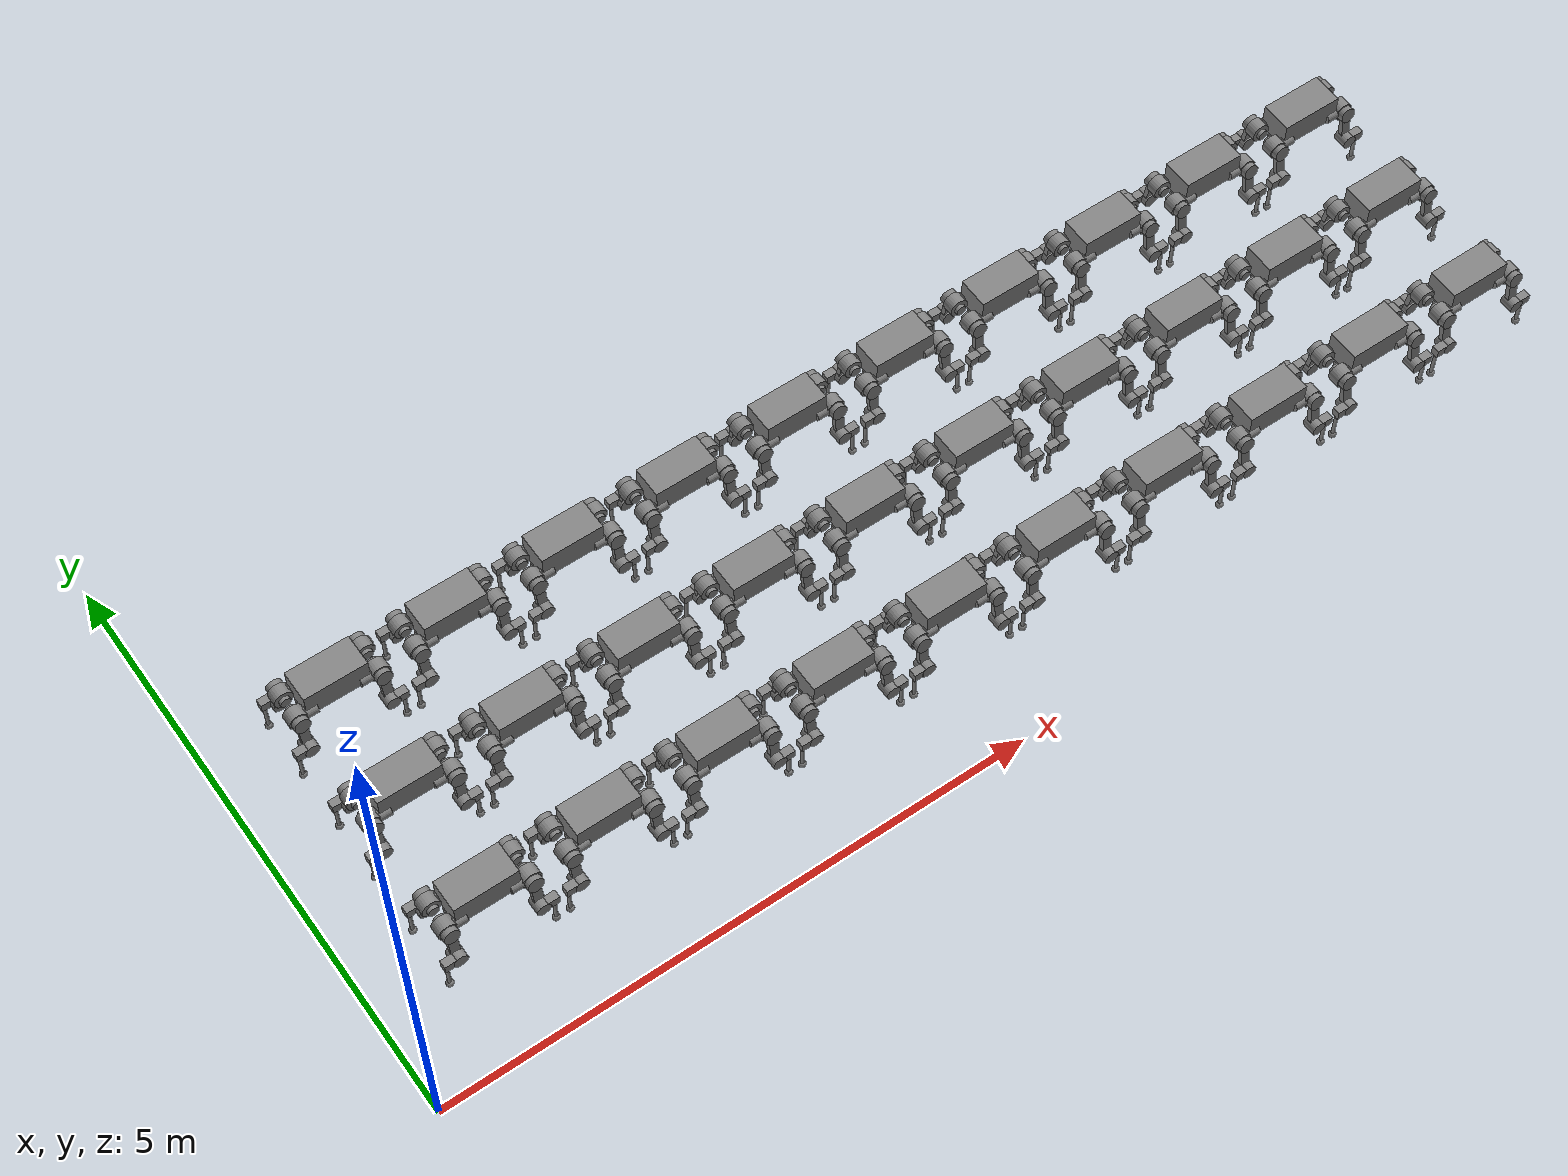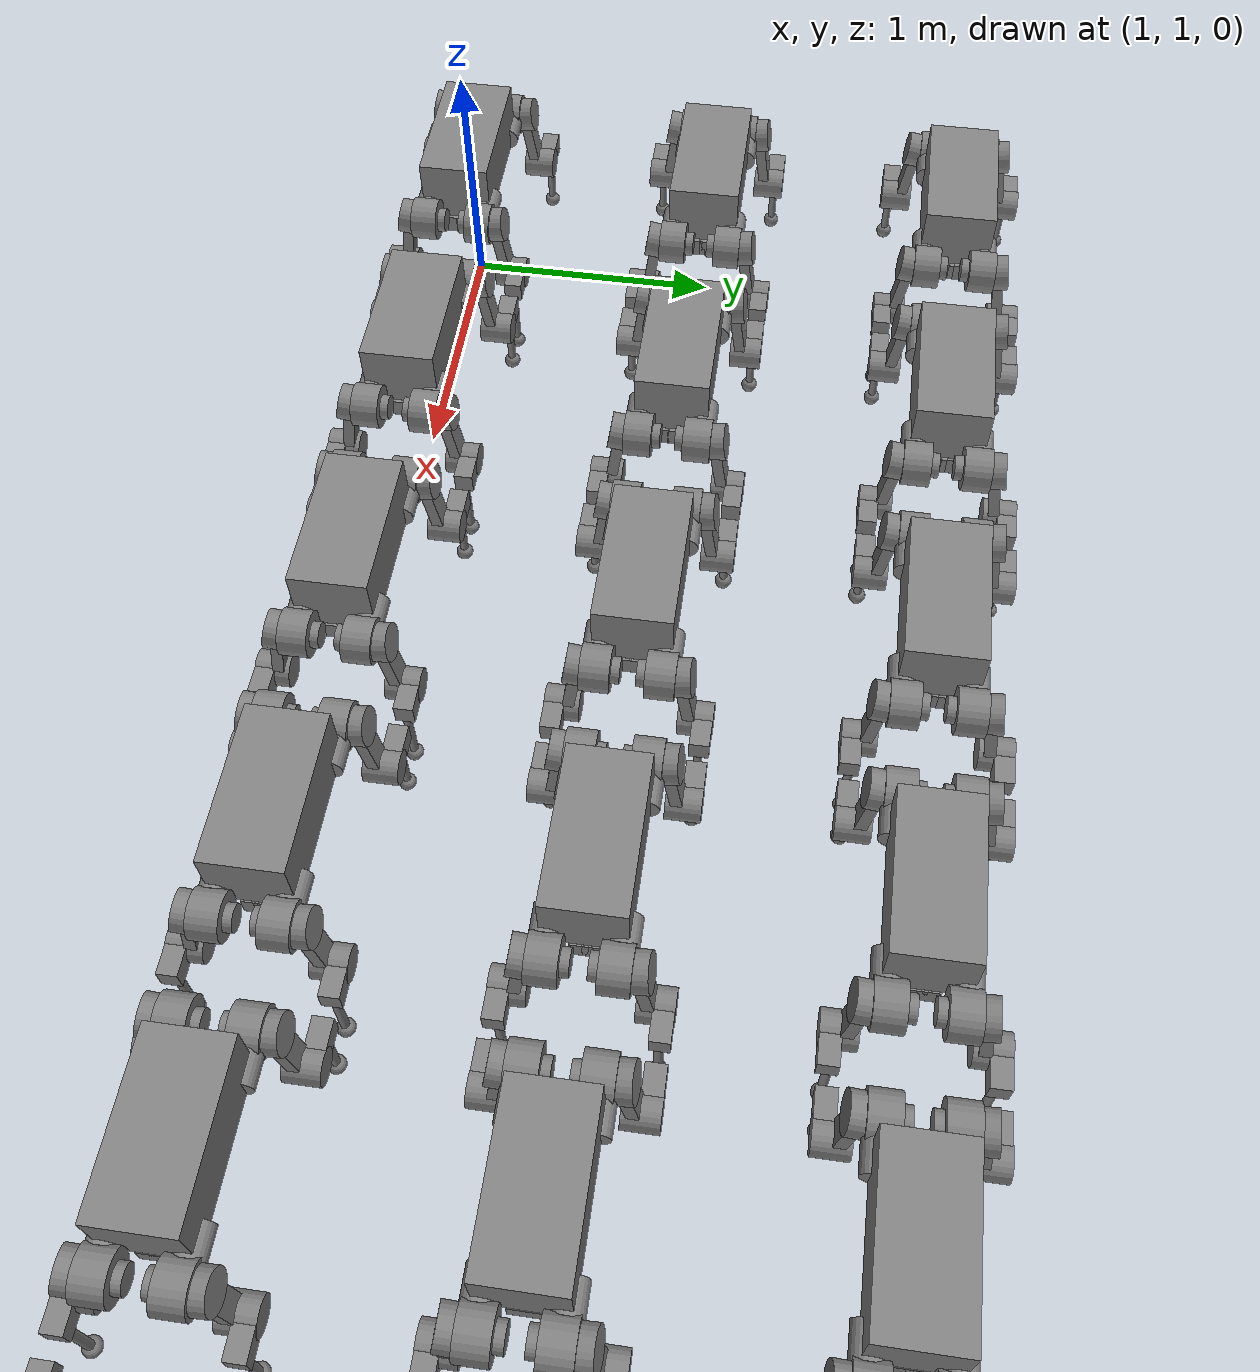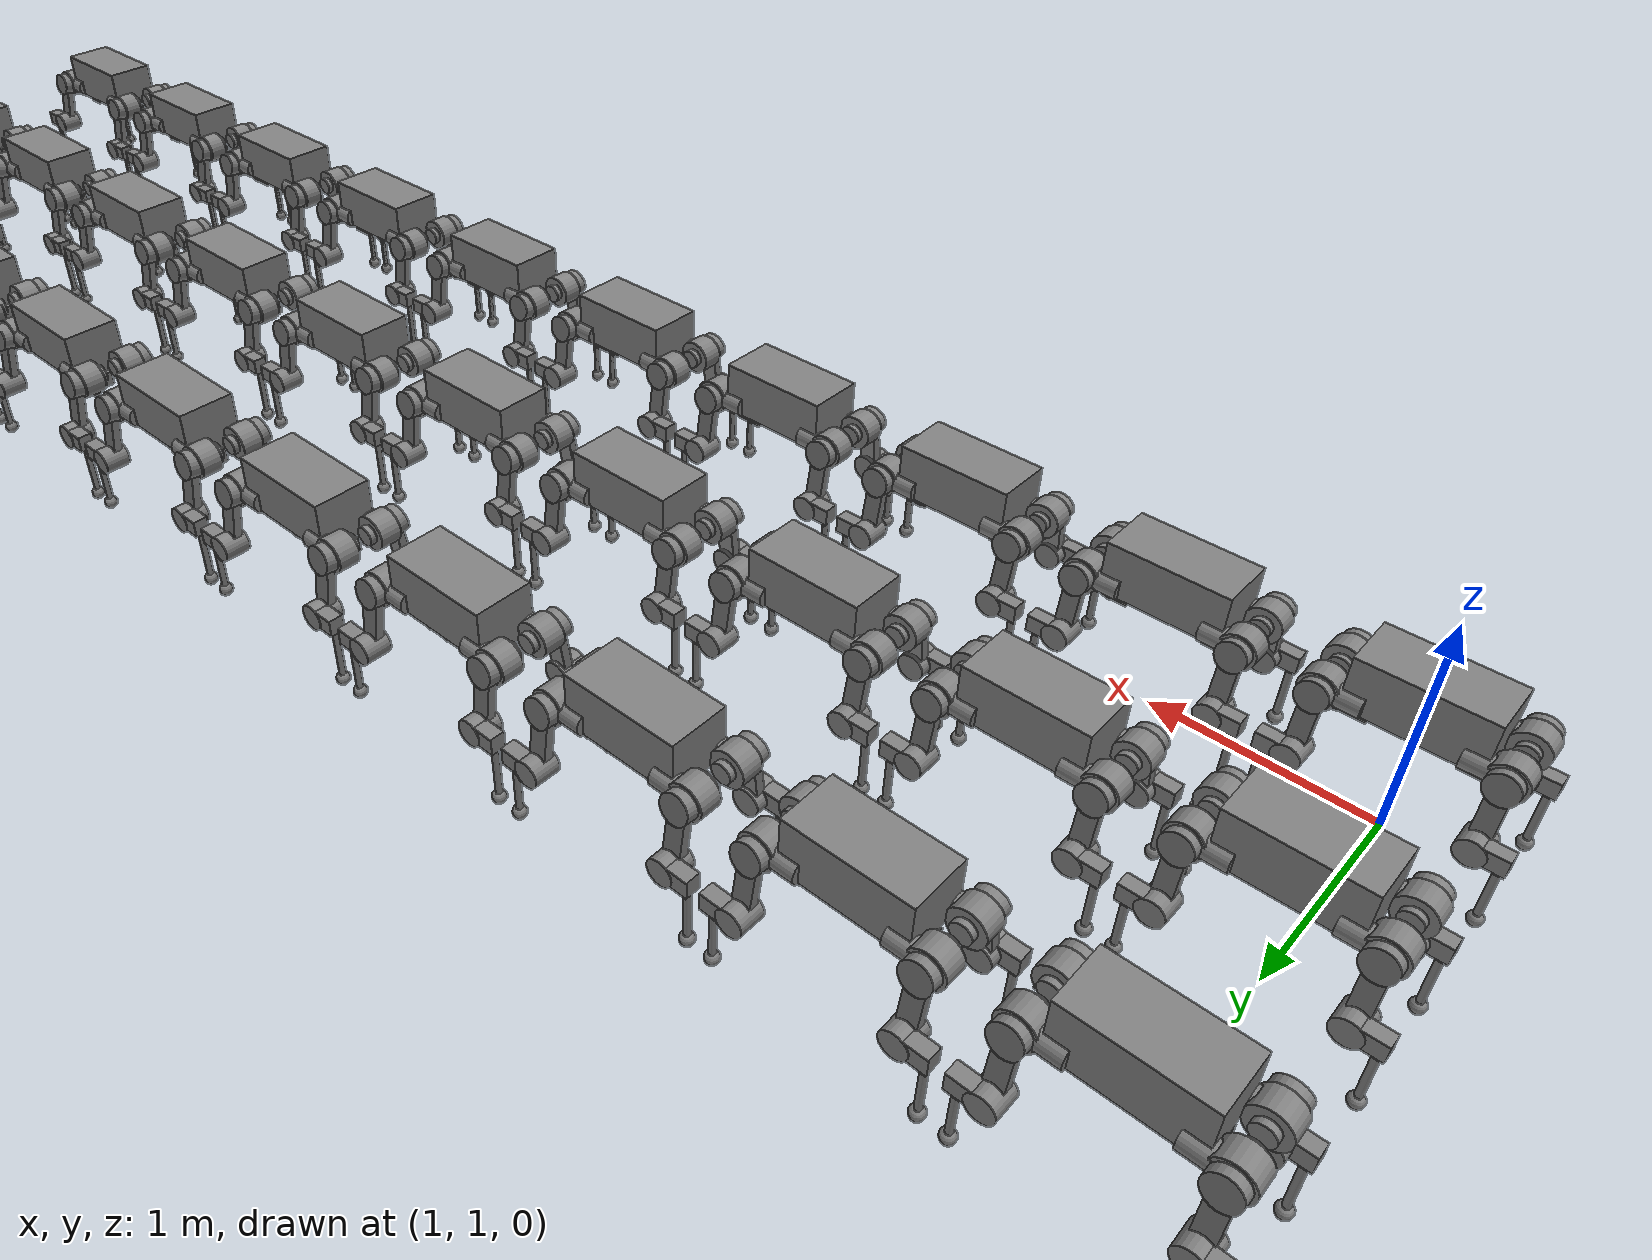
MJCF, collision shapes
<mujoco model="anymal_b">
  <compiler angle="radian" meshdir="assets" texturedir="assets" autolimits="true"/>

  <option cone="elliptic" impratio="100"/>

  <default>
    <default class="anymal_b">
      <mesh scale="0.001 0.001 0.001"/>
      <site group="3" rgba="1 0 0 0.66"/>
      <joint type="hinge" damping="1" frictionloss="0.1"/>
      <default class="HAA">
        <joint axis="1 0 0"/>
      </default>
      <default class="HFE">
        <joint axis="0 1 0"/>
      </default>
      <default class="KFE">
        <joint axis="0 1 0"/>
      </default>
      <geom mass="0"/>
      <default class="visual">
        <geom type="mesh" contype="0" conaffinity="0" group="2"/>
        <default class="visual_zflip">
          <geom quat="0 0 0 1"/>
        </default>
      </default>
      <default class="collision">
        <geom group="3"/>
        <default class="haa_actuator">
          <geom type="cylinder" size="0.05 0.05" euler="0 1.57079632679 0"/>
        </default>
        <default class="belly_plate_bump">
          <geom type="box" size="0.05 0.05 0.035"/>
        </default>
        <default class="mount">
          <geom type="box" size="0.01 0.135 0.045"/>
        </default>
        <default class="protector">
          <geom type="cylinder" size="0.08 0.05"/>
        </default>
        <default class="heatfins">
          <geom type="cylinder" size="0.045 0.015"/>
        </default>
        <default class="thigh_with_fins">
          <geom type="box" size="0.04 0.02 0.125"/>
        </default>
        <default class="kfe_actuator">
          <geom type="cylinder" size="0.06 0.06"/>
        </default>
        <default class="upper_protector">
          <geom type="cylinder" size="0.066 0.06"/>
        </default>
        <default class="shank">
          <geom type="box" size="0.04 0.034 0.065" euler="0 1.57079632679 0"/>
        </default>
        <default class="adapter">
          <geom type="cylinder" size="0.015 0.14" pos="0 0 -0.14"/>
        </default>
        <default class="foot">
          <geom type="sphere" size="0.031" pos="0 0 0.02325" priority="1" solimp="0.015 1 0.031" condim="6"
            friction="0.8 0.02 0.01"/>
        </default>
      </default>
      <default class="affine">
        <position kp="100" ctrlrange="-6.28 6.28" forcerange="-40 40"/>
      </default>
    </default>
  </default>

  <asset>
    <material name="light_gray" rgba="0.8 0.8 0.8 1"/>
    <material name="dark_gray" rgba="0.64 0.64 0.64 1"/>
    <material name="alu_eloxiert" rgba="0.1139 0.1139 0.1139 1"/>
    <material name="any_blau" rgba="0.2399 0.3499 0.5899 1"/>
    <texture name="base_uv_texture" type="2d" file="base_uv_texture.png"/>
    <material name="carbon_fibre_logo" texture="base_uv_texture" specular="1" shininess="1"/>
    <material name="rot_emcy" rgba="0.2611 0.09645 0.0735 1"/>
    <material name="yellow_emcy" rgba="0.5987 0.4607 0.2442 1"/>
    <material name="copper" rgba="0.8 0.4673 0.284 1"/>
    <material name="foam_dark" rgba="0.1 0.1 0.1 1"/>
    <texture name="carbon_uv_texture" type="2d" file="carbon_uv_texture.png"/>
    <material name="carbon_fibre" texture="carbon_uv_texture" specular="1" shininess="1"/>

    <mesh class="anymal_b" file="anymal_base_0.obj"/>
    <mesh class="anymal_b" file="anymal_base_1.obj"/>
    <mesh class="anymal_b" file="anymal_base_2.obj"/>
    <mesh class="anymal_b" file="anymal_base_3.obj"/>
    <mesh class="anymal_b" file="anymal_base_4.obj"/>
    <mesh class="anymal_b" file="anymal_base_5.obj"/>
    <mesh class="anymal_b" file="anymal_base_6.obj"/>
    <mesh class="anymal_b" file="anymal_base_7.obj"/>
    <mesh class="anymal_b" file="anymal_hip_l_0.obj"/>
    <mesh class="anymal_b" file="anymal_hip_l_1.obj"/>
    <mesh class="anymal_b" file="anymal_hip_l_2.obj"/>
    <mesh class="anymal_b" file="anymal_hip_l_3.obj"/>
    <mesh class="anymal_b" file="anymal_hip_l_4.obj"/>
    <mesh class="anymal_b" file="anymal_hip_l_5.obj"/>
    <mesh class="anymal_b" file="anymal_hip_l_6.obj"/>
    <mesh class="anymal_b" file="anymal_thigh_l_0.obj"/>
    <mesh class="anymal_b" file="anymal_thigh_l_1.obj"/>
    <mesh class="anymal_b" file="anymal_thigh_l_2.obj"/>
    <mesh class="anymal_b" file="anymal_thigh_l_3.obj"/>
    <mesh class="anymal_b" file="anymal_thigh_l_4.obj"/>
    <mesh class="anymal_b" file="anymal_thigh_l_5.obj"/>
    <mesh class="anymal_b" file="anymal_shank_l_0.obj"/>
    <mesh class="anymal_b" file="anymal_shank_l_1.obj"/>
    <mesh class="anymal_b" file="anymal_shank_l_2.obj"/>
    <mesh class="anymal_b" file="anymal_shank_l_3.obj"/>
    <mesh class="anymal_b" file="anymal_hip_r_0.obj"/>
    <mesh class="anymal_b" file="anymal_hip_r_1.obj"/>
    <mesh class="anymal_b" file="anymal_hip_r_2.obj"/>
    <mesh class="anymal_b" file="anymal_hip_r_3.obj"/>
    <mesh class="anymal_b" file="anymal_hip_r_4.obj"/>
    <mesh class="anymal_b" file="anymal_hip_r_5.obj"/>
    <mesh class="anymal_b" file="anymal_hip_r_6.obj"/>
    <mesh class="anymal_b" file="anymal_thigh_r_0.obj"/>
    <mesh class="anymal_b" file="anymal_thigh_r_1.obj"/>
    <mesh class="anymal_b" file="anymal_thigh_r_2.obj"/>
    <mesh class="anymal_b" file="anymal_thigh_r_3.obj"/>
    <mesh class="anymal_b" file="anymal_thigh_r_4.obj"/>
    <mesh class="anymal_b" file="anymal_thigh_r_5.obj"/>
    <mesh class="anymal_b" file="anymal_shank_r_0.obj"/>
    <mesh class="anymal_b" file="anymal_shank_r_1.obj"/>
    <mesh class="anymal_b" file="anymal_shank_r_2.obj"/>
    <mesh class="anymal_b" file="anymal_shank_r_3.obj"/>
    <mesh class="anymal_b" file="anymal_foot_0.obj"/>
    <mesh class="anymal_b" file="anymal_foot_1.obj"/>
    <mesh class="anymal_b" file="anymal_foot_2.obj"/>
    <mesh class="anymal_b" file="anymal_foot_3.obj"/>
  </asset>

  <worldbody>
    <body name="r_1_1__base" pos="1 1 0.58" quat="0 0 0 1" childclass="anymal_b">
      <freejoint/>
      <inertial mass="19.2035" pos="0.0025 0 0.0502071" quat="0.5 0.5 0.5 0.5" diaginertia="0.639559 0.624031 0.217374"/>
      <geom class="visual" mesh="anymal_base_0" material="yellow_emcy"/>
      <geom class="visual" mesh="anymal_base_1" material="rot_emcy"/>
      <geom class="visual" mesh="anymal_base_2" material="dark_gray"/>
      <geom class="visual" mesh="anymal_base_3" material="any_blau"/>
      <geom class="visual" mesh="anymal_base_4" material="alu_eloxiert"/>
      <geom class="visual" mesh="anymal_base_5" material="carbon_fibre_logo"/>
      <geom class="visual" mesh="anymal_base_6" material="foam_dark"/>
      <geom class="visual" mesh="anymal_base_7" material="light_gray"/>
      <geom class="collision" size="0.2655 0.135 0.12" pos="0 0 0.08" type="box"/>
      <geom class="haa_actuator" pos="0.227 0.116 0"/>
      <geom class="haa_actuator" pos="0.227 -0.116 0"/>
      <geom class="haa_actuator" pos="-0.227 0.116 0"/>
      <geom class="haa_actuator" pos="-0.227 -0.116 0"/>
      <geom class="belly_plate_bump" pos="0.2155 0 -0.09"/>
      <geom class="belly_plate_bump" pos="-0.2155 0 -0.09"/>
      <geom class="collision" size="0.2655 0.01 0.035" pos="0 0 -0.09" type="box"/>
      <body name="r_1_1__LF_HIP" pos="0.277 0.116 0">
        <inertial mass="1.42462" pos="0.0645163 -0.0037871 -0.000152184" quat="0.996866 0.0379822 0.0252009 -0.0646548"
          diaginertia="0.00243341 0.00230249 0.00197758"/>
        <joint name="r_1_1__LF_HAA" class="HAA"/>
        <geom class="visual" mesh="anymal_hip_l_0" material="light_gray"/>
        <geom class="visual" mesh="anymal_hip_l_1" material="copper"/>
        <geom class="visual" mesh="anymal_hip_l_2" material="foam_dark"/>
        <geom class="visual" mesh="anymal_hip_l_3" material="alu_eloxiert"/>
        <geom class="visual" mesh="anymal_hip_l_4" material="any_blau"/>
        <geom class="visual" mesh="anymal_hip_l_5" material="dark_gray"/>
        <geom class="visual" mesh="anymal_hip_l_6" material="light_gray"/>
        <geom class="protector" pos="0.0635 -0.009 0" quat="1 1 0 0"/>
        <geom class="heatfins" pos="0.0635 -0.074 0" quat="1 1 0 0"/>
        <body name="r_1_1__LF_THIGH" pos="0.0635 0.041 0">
          <inertial mass="1.63498" pos="-0.00389797 0.0542266 -0.214583" quat="0.74395 -0.0633414 0.0362707 0.664237"
            diaginertia="0.0122697 0.0120427 0.00228302"/>
          <joint name="r_1_1__LF_HFE" class="HFE"/>
          <geom class="visual" material="any_blau" mesh="anymal_thigh_l_0"/>
          <geom class="visual" material="dark_gray" mesh="anymal_thigh_l_1"/>
          <geom class="visual" material="copper" mesh="anymal_thigh_l_2"/>
          <geom class="visual" material="alu_eloxiert" mesh="anymal_thigh_l_3"/>
          <geom class="visual" material="foam_dark" mesh="anymal_thigh_l_4"/>
          <geom class="visual" material="light_gray" mesh="anymal_thigh_l_5"/>
          <geom class="thigh_with_fins" pos="0 0.035 -0.125" quat="0.997373 0.0724365 0 0"/>
          <geom class="kfe_actuator" pos="0 0.069 -0.25" quat="1 1 0 0"/>
          <geom class="upper_protector" pos="0 -0.005 0" quat="0.654029 0.75647 0 0"/>
          <body name="r_1_1__LF_SHANK" pos="0 0.109 -0.25">
            <inertial mass="0.472163" pos="0.0696396 -0.0132494 -0.150905"
              quat="0.677954 -0.0950614 -0.0578104 0.726636" diaginertia="0.0116034 0.0110666 0.000723761"/>
            <joint name="r_1_1__LF_KFE" class="KFE"/>
            <geom class="visual" material="foam_dark" mesh="anymal_shank_l_0"/>
            <geom class="visual" material="dark_gray" mesh="anymal_shank_l_1"/>
            <geom class="visual" material="light_gray" mesh="anymal_shank_l_2"/>
            <geom class="visual" material="light_gray" mesh="anymal_shank_l_3"/>
            <geom class="shank" pos="0.065 -0.015 0.01" quat="1 0 1 0"/>
            <geom class="visual" material="carbon_fibre" mesh="anymal_foot_0" pos="0.1 -0.02 0.032"/>
            <geom class="visual" material="foam_dark" mesh="anymal_foot_1" pos="0.1 -0.02 0.032"/>
            <geom class="visual" material="dark_gray" mesh="anymal_foot_2" pos="0.1 -0.02 0.032"/>
            <geom class="visual" material="light_gray" mesh="anymal_foot_3" pos="0.1 -0.02 0.032"/>
            <geom class="adapter" pos="0.1 -0.02 -0.160625"/>
            <geom class="foot" pos="0.1 -0.02 -0.298"/>
          </body>
        </body>
      </body>
      <body name="r_1_1__RF_HIP" pos="0.277 -0.116 0">
        <inertial mass="1.42462" pos="0.0645163 0.0037871 -0.000152184" quat="0.996866 -0.0379822 0.0252009 0.0646548"
          diaginertia="0.00243341 0.00230249 0.00197758"/>
        <joint name="r_1_1__RF_HAA" class="HAA"/>
        <geom class="visual" material="light_gray" mesh="anymal_hip_r_0"/>
        <geom class="visual" material="copper" mesh="anymal_hip_r_1"/>
        <geom class="visual" material="foam_dark" mesh="anymal_hip_r_2"/>
        <geom class="visual" material="alu_eloxiert" mesh="anymal_hip_r_3"/>
        <geom class="visual" material="any_blau" mesh="anymal_hip_r_4"/>
        <geom class="visual" material="dark_gray" mesh="anymal_hip_r_5"/>
        <geom class="visual" material="light_gray" mesh="anymal_hip_r_6"/>
        <geom class="protector" pos="0.0635 0.009 0" quat="1 1 0 0"/>
        <geom class="heatfins" pos="0.0635 0.074 0" quat="1 1 0 0"/>
        <body name="r_1_1__RF_THIGH" pos="0.0635 -0.041 0">
          <inertial mass="1.63498" pos="-0.00389797 -0.0542266 -0.214583" quat="0.664237 0.0362707 -0.0633414 0.74395"
            diaginertia="0.0122697 0.0120427 0.00228302"/>
          <joint name="r_1_1__RF_HFE" class="HFE"/>
          <geom class="visual" material="any_blau" mesh="anymal_thigh_r_0"/>
          <geom class="visual" material="dark_gray" mesh="anymal_thigh_r_1"/>
          <geom class="visual" material="copper" mesh="anymal_thigh_r_2"/>
          <geom class="visual" material="alu_eloxiert" mesh="anymal_thigh_r_3"/>
          <geom class="visual" material="foam_dark" mesh="anymal_thigh_r_4"/>
          <geom class="visual" material="light_gray" mesh="anymal_thigh_r_5"/>
          <geom class="thigh_with_fins" pos="0 -0.035 -0.125" quat="0.997373 -0.0724365 0 0"/>
          <geom class="kfe_actuator" pos="0 -0.069 -0.25" quat="1 1 0 0"/>
          <geom class="upper_protector" pos="0 0.005 0" quat="0.654029 -0.75647 0 0"/>
          <body name="r_1_1__RF_SHANK" pos="0 -0.109 -0.25">
            <inertial mass="0.472163" pos="0.0696396 0.0132494 -0.150905" quat="0.726636 -0.0578104 -0.0950614 0.677954"
              diaginertia="0.0116034 0.0110666 0.000723761"/>
            <joint name="r_1_1__RF_KFE" class="KFE"/>
            <geom class="visual" material="foam_dark" mesh="anymal_shank_r_0"/>
            <geom class="visual" material="dark_gray" mesh="anymal_shank_r_1"/>
            <geom class="visual" material="light_gray" mesh="anymal_shank_r_2"/>
            <geom class="visual" material="light_gray" mesh="anymal_shank_r_3"/>
            <geom class="shank" pos="0.065 0.015 0.01" quat="1 0 1 0"/>
            <geom class="visual" material="carbon_fibre" mesh="anymal_foot_0" pos="0.1 0.02 0.032"/>
            <geom class="visual" material="foam_dark" mesh="anymal_foot_1" pos="0.1 0.02 0.032"/>
            <geom class="visual" material="dark_gray" mesh="anymal_foot_2" pos="0.1 0.02 0.032"/>
            <geom class="visual" material="light_gray" mesh="anymal_foot_3" pos="0.1 0.02 0.032"/>
            <geom class="adapter" pos="0.1 0.02 -0.160625"/>
            <geom class="foot" pos="0.1 0.02 -0.298"/>
          </body>
        </body>
      </body>
      <body name="r_1_1__LH_HIP" pos="-0.277 0.116 0">
        <inertial mass="1.42462" pos="-0.0645163 -0.0037871 -0.000152184" quat="0.996866 0.0379822 -0.0252009 0.0646548"
          diaginertia="0.00243341 0.00230249 0.00197758"/>
        <joint name="r_1_1__LH_HAA" class="HAA"/>
        <geom class="visual_zflip" material="light_gray" mesh="anymal_hip_r_0"/>
        <geom class="visual_zflip" material="copper" mesh="anymal_hip_r_1"/>
        <geom class="visual_zflip" material="foam_dark" mesh="anymal_hip_r_2"/>
        <geom class="visual_zflip" material="alu_eloxiert" mesh="anymal_hip_r_3"/>
        <geom class="visual_zflip" material="any_blau" mesh="anymal_hip_r_4"/>
        <geom class="visual_zflip" material="dark_gray" mesh="anymal_hip_r_5"/>
        <geom class="visual_zflip" material="light_gray" mesh="anymal_hip_r_6"/>
        <geom class="protector" pos="-0.0635 -0.009 0" quat="1 -1 0 0"/>
        <geom class="heatfins" pos="-0.0635 -0.074 0" quat="1 -1 0 0"/>
        <body name="r_1_1__LH_THIGH" pos="-0.0635 0.041 0">
          <inertial mass="1.63498" pos="0.00389797 0.0542266 -0.214583" quat="0.664237 -0.0362707 0.0633414 0.74395"
            diaginertia="0.0122697 0.0120427 0.00228302"/>
          <joint name="r_1_1__LH_HFE" class="HFE"/>
          <geom class="visual_zflip" material="any_blau" mesh="anymal_thigh_r_0"/>
          <geom class="visual_zflip" material="dark_gray" mesh="anymal_thigh_r_1"/>
          <geom class="visual_zflip" material="copper" mesh="anymal_thigh_r_2"/>
          <geom class="visual_zflip" material="alu_eloxiert" mesh="anymal_thigh_r_3"/>
          <geom class="visual_zflip" material="foam_dark" mesh="anymal_thigh_r_4"/>
          <geom class="visual_zflip" material="light_gray" mesh="anymal_thigh_r_5"/>
          <geom class="thigh_with_fins" pos="0 0.035 -0.125" quat="0.997373 0.0724365 0 0"/>
          <geom class="kfe_actuator" pos="0 0.069 -0.25" quat="1 1 0 0"/>
          <geom class="upper_protector" pos="0 -0.005 0" quat="0.654029 0.75647 0 0"/>
          <body name="r_1_1__LH_SHANK" pos="0 0.109 -0.25">
            <inertial mass="0.472163" pos="-0.0696396 -0.0132494 -0.150905" quat="0.726636 0.0578104 0.0950615 0.677954"
              diaginertia="0.0116034 0.0110666 0.000723761"/>
            <joint name="r_1_1__LH_KFE" class="KFE"/>
            <geom class="visual_zflip" material="foam_dark" mesh="anymal_shank_r_0"/>
            <geom class="visual_zflip" material="dark_gray" mesh="anymal_shank_r_1"/>
            <geom class="visual_zflip" material="light_gray" mesh="anymal_shank_r_2"/>
            <geom class="visual_zflip" material="light_gray" mesh="anymal_shank_r_3"/>
            <geom class="shank" pos="-0.065 -0.015 0.01" quat="1 0 1 0"/>
            <geom class="visual_zflip" material="carbon_fibre" mesh="anymal_foot_0" pos="-0.1 -0.02 0.032"/>
            <geom class="visual_zflip" material="foam_dark" mesh="anymal_foot_1" pos="-0.1 -0.02 0.032"/>
            <geom class="visual_zflip" material="dark_gray" mesh="anymal_foot_2" pos="-0.1 -0.02 0.032"/>
            <geom class="visual_zflip" material="light_gray" mesh="anymal_foot_3" pos="-0.1 -0.02 0.032"/>
            <geom class="adapter" pos="-0.1 -0.02 -0.160625"/>
            <geom class="foot" pos="-0.1 -0.02 -0.298"/>
          </body>
        </body>
      </body>
      <body name="r_1_1__RH_HIP" pos="-0.277 -0.116 0">
        <inertial mass="1.42462" pos="-0.0645163 0.0037871 -0.000152184"
          quat="0.996866 -0.0379822 -0.0252009 -0.0646548" diaginertia="0.00243341 0.00230249 0.00197758"/>
        <joint name="r_1_1__RH_HAA" class="HAA"/>
        <geom class="visual_zflip" mesh="anymal_hip_l_0" material="light_gray"/>
        <geom class="visual_zflip" mesh="anymal_hip_l_1" material="copper"/>
        <geom class="visual_zflip" mesh="anymal_hip_l_2" material="foam_dark"/>
        <geom class="visual_zflip" mesh="anymal_hip_l_3" material="alu_eloxiert"/>
        <geom class="visual_zflip" mesh="anymal_hip_l_4" material="any_blau"/>
        <geom class="visual_zflip" mesh="anymal_hip_l_5" material="dark_gray"/>
        <geom class="visual_zflip" mesh="anymal_hip_l_6" material="light_gray"/>
        <geom class="protector" pos="-0.0635 0.009 0" quat="1 -1 0 0"/>
        <geom class="heatfins" pos="-0.0635 0.074 0" quat="1 -1 0 0"/>
        <body name="r_1_1__RH_THIGH" pos="-0.0635 -0.041 0">
          <inertial mass="1.63498" pos="0.00389797 -0.0542266 -0.214583" quat="0.74395 0.0633414 -0.0362707 0.664237"
            diaginertia="0.0122697 0.0120427 0.00228302"/>
          <joint name="r_1_1__RH_HFE" class="HFE"/>
          <geom class="visual_zflip" material="any_blau" mesh="anymal_thigh_l_0"/>
          <geom class="visual_zflip" material="dark_gray" mesh="anymal_thigh_l_1"/>
          <geom class="visual_zflip" material="copper" mesh="anymal_thigh_l_2"/>
          <geom class="visual_zflip" material="alu_eloxiert" mesh="anymal_thigh_l_3"/>
          <geom class="visual_zflip" material="foam_dark" mesh="anymal_thigh_l_4"/>
          <geom class="visual_zflip" material="light_gray" mesh="anymal_thigh_l_5"/>
          <geom class="thigh_with_fins" pos="0 -0.035 -0.125" quat="0.997373 -0.0724365 0 0"/>
          <geom class="kfe_actuator" pos="0 -0.069 -0.25" quat="1 1 0 0"/>
          <geom class="upper_protector" pos="0 0.005 0" quat="0.654029 -0.75647 0 0"/>
          <body name="r_1_1__RH_SHANK" pos="0 -0.109 -0.25">
            <inertial mass="0.472163" pos="-0.0696396 0.0132494 -0.150905" quat="0.677954 0.0950614 0.0578104 0.726636"
              diaginertia="0.0116034 0.0110666 0.000723761"/>
            <joint name="r_1_1__RH_KFE" class="KFE"/>
            <geom class="visual_zflip" material="foam_dark" mesh="anymal_shank_l_0"/>
            <geom class="visual_zflip" material="dark_gray" mesh="anymal_shank_l_1"/>
            <geom class="visual_zflip" material="light_gray" mesh="anymal_shank_l_2"/>
            <geom class="visual_zflip" material="light_gray" mesh="anymal_shank_l_3"/>
            <geom class="shank" pos="-0.065 0.015 0.01" quat="1 0 1 0"/>
            <geom class="visual_zflip" material="carbon_fibre" mesh="anymal_foot_0" pos="-0.1 0.02 0.032"/>
            <geom class="visual_zflip" material="foam_dark" mesh="anymal_foot_1" pos="-0.1 0.02 0.032"/>
            <geom class="visual_zflip" material="dark_gray" mesh="anymal_foot_2" pos="-0.1 0.02 0.032"/>
            <geom class="visual_zflip" material="light_gray" mesh="anymal_foot_3" pos="-0.1 0.02 0.032"/>
            <geom class="adapter" pos="-0.1 0.02 -0.160625"/>
            <geom class="foot" pos="-0.1 0.02 -0.298"/>
          </body>
        </body>
      </body>
    </body>
    <body name="r_1_2__base" pos="1 2 0.58" quat="0 0 0 1" childclass="anymal_b">
      <freejoint/>
      <inertial mass="19.2035" pos="0.0025 0 0.0502071" quat="0.5 0.5 0.5 0.5" diaginertia="0.639559 0.624031 0.217374"/>
      <geom class="visual" mesh="anymal_base_0" material="yellow_emcy"/>
      <geom class="visual" mesh="anymal_base_1" material="rot_emcy"/>
      <geom class="visual" mesh="anymal_base_2" material="dark_gray"/>
      <geom class="visual" mesh="anymal_base_3" material="any_blau"/>
      <geom class="visual" mesh="anymal_base_4" material="alu_eloxiert"/>
      <geom class="visual" mesh="anymal_base_5" material="carbon_fibre_logo"/>
      <geom class="visual" mesh="anymal_base_6" material="foam_dark"/>
      <geom class="visual" mesh="anymal_base_7" material="light_gray"/>
      <geom class="collision" size="0.2655 0.135 0.12" pos="0 0 0.08" type="box"/>
      <geom class="haa_actuator" pos="0.227 0.116 0"/>
      <geom class="haa_actuator" pos="0.227 -0.116 0"/>
      <geom class="haa_actuator" pos="-0.227 0.116 0"/>
      <geom class="haa_actuator" pos="-0.227 -0.116 0"/>
      <geom class="belly_plate_bump" pos="0.2155 0 -0.09"/>
      <geom class="belly_plate_bump" pos="-0.2155 0 -0.09"/>
      <geom class="collision" size="0.2655 0.01 0.035" pos="0 0 -0.09" type="box"/>
      <body name="r_1_2__LF_HIP" pos="0.277 0.116 0">
        <inertial mass="1.42462" pos="0.0645163 -0.0037871 -0.000152184" quat="0.996866 0.0379822 0.0252009 -0.0646548"
          diaginertia="0.00243341 0.00230249 0.00197758"/>
        <joint name="r_1_2__LF_HAA" class="HAA"/>
        <geom class="visual" mesh="anymal_hip_l_0" material="light_gray"/>
        <geom class="visual" mesh="anymal_hip_l_1" material="copper"/>
        <geom class="visual" mesh="anymal_hip_l_2" material="foam_dark"/>
        <geom class="visual" mesh="anymal_hip_l_3" material="alu_eloxiert"/>
        <geom class="visual" mesh="anymal_hip_l_4" material="any_blau"/>
        <geom class="visual" mesh="anymal_hip_l_5" material="dark_gray"/>
        <geom class="visual" mesh="anymal_hip_l_6" material="light_gray"/>
        <geom class="protector" pos="0.0635 -0.009 0" quat="1 1 0 0"/>
        <geom class="heatfins" pos="0.0635 -0.074 0" quat="1 1 0 0"/>
        <body name="r_1_2__LF_THIGH" pos="0.0635 0.041 0">
          <inertial mass="1.63498" pos="-0.00389797 0.0542266 -0.214583" quat="0.74395 -0.0633414 0.0362707 0.664237"
            diaginertia="0.0122697 0.0120427 0.00228302"/>
          <joint name="r_1_2__LF_HFE" class="HFE"/>
          <geom class="visual" material="any_blau" mesh="anymal_thigh_l_0"/>
          <geom class="visual" material="dark_gray" mesh="anymal_thigh_l_1"/>
          <geom class="visual" material="copper" mesh="anymal_thigh_l_2"/>
          <geom class="visual" material="alu_eloxiert" mesh="anymal_thigh_l_3"/>
          <geom class="visual" material="foam_dark" mesh="anymal_thigh_l_4"/>
          <geom class="visual" material="light_gray" mesh="anymal_thigh_l_5"/>
          <geom class="thigh_with_fins" pos="0 0.035 -0.125" quat="0.997373 0.0724365 0 0"/>
          <geom class="kfe_actuator" pos="0 0.069 -0.25" quat="1 1 0 0"/>
          <geom class="upper_protector" pos="0 -0.005 0" quat="0.654029 0.75647 0 0"/>
          <body name="r_1_2__LF_SHANK" pos="0 0.109 -0.25">
            <inertial mass="0.472163" pos="0.0696396 -0.0132494 -0.150905"
              quat="0.677954 -0.0950614 -0.0578104 0.726636" diaginertia="0.0116034 0.0110666 0.000723761"/>
            <joint name="r_1_2__LF_KFE" class="KFE"/>
            <geom class="visual" material="foam_dark" mesh="anymal_shank_l_0"/>
            <geom class="visual" material="dark_gray" mesh="anymal_shank_l_1"/>
            <geom class="visual" material="light_gray" mesh="anymal_shank_l_2"/>
            <geom class="visual" material="light_gray" mesh="anymal_shank_l_3"/>
            <geom class="shank" pos="0.065 -0.015 0.01" quat="1 0 1 0"/>
            <geom class="visual" material="carbon_fibre" mesh="anymal_foot_0" pos="0.1 -0.02 0.032"/>
            <geom class="visual" material="foam_dark" mesh="anymal_foot_1" pos="0.1 -0.02 0.032"/>
            <geom class="visual" material="dark_gray" mesh="anymal_foot_2" pos="0.1 -0.02 0.032"/>
            <geom class="visual" material="light_gray" mesh="anymal_foot_3" pos="0.1 -0.02 0.032"/>
            <geom class="adapter" pos="0.1 -0.02 -0.160625"/>
            <geom class="foot" pos="0.1 -0.02 -0.298"/>
          </body>
        </body>
      </body>
      <body name="r_1_2__RF_HIP" pos="0.277 -0.116 0">
        <inertial mass="1.42462" pos="0.0645163 0.0037871 -0.000152184" quat="0.996866 -0.0379822 0.0252009 0.0646548"
          diaginertia="0.00243341 0.00230249 0.00197758"/>
        <joint name="r_1_2__RF_HAA" class="HAA"/>
        <geom class="visual" material="light_gray" mesh="anymal_hip_r_0"/>
        <geom class="visual" material="copper" mesh="anymal_hip_r_1"/>
        <geom class="visual" material="foam_dark" mesh="anymal_hip_r_2"/>
        <geom class="visual" material="alu_eloxiert" mesh="anymal_hip_r_3"/>
        <geom class="visual" material="any_blau" mesh="anymal_hip_r_4"/>
        <geom class="visual" material="dark_gray" mesh="anymal_hip_r_5"/>
        <geom class="visual" material="light_gray" mesh="anymal_hip_r_6"/>
        <geom class="protector" pos="0.0635 0.009 0" quat="1 1 0 0"/>
        <geom class="heatfins" pos="0.0635 0.074 0" quat="1 1 0 0"/>
        <body name="r_1_2__RF_THIGH" pos="0.0635 -0.041 0">
          <inertial mass="1.63498" pos="-0.00389797 -0.0542266 -0.214583" quat="0.664237 0.0362707 -0.0633414 0.74395"
            diaginertia="0.0122697 0.0120427 0.00228302"/>
          <joint name="r_1_2__RF_HFE" class="HFE"/>
          <geom class="visual" material="any_blau" mesh="anymal_thigh_r_0"/>
          <geom class="visual" material="dark_gray" mesh="anymal_thigh_r_1"/>
          <geom class="visual" material="copper" mesh="anymal_thigh_r_2"/>
          <geom class="visual" material="alu_eloxiert" mesh="anymal_thigh_r_3"/>
          <geom class="visual" material="foam_dark" mesh="anymal_thigh_r_4"/>
          <geom class="visual" material="light_gray" mesh="anymal_thigh_r_5"/>
          <geom class="thigh_with_fins" pos="0 -0.035 -0.125" quat="0.997373 -0.0724365 0 0"/>
          <geom class="kfe_actuator" pos="0 -0.069 -0.25" quat="1 1 0 0"/>
          <geom class="upper_protector" pos="0 0.005 0" quat="0.654029 -0.75647 0 0"/>
          <body name="r_1_2__RF_SHANK" pos="0 -0.109 -0.25">
            <inertial mass="0.472163" pos="0.0696396 0.0132494 -0.150905" quat="0.726636 -0.0578104 -0.0950614 0.677954"
              diaginertia="0.0116034 0.0110666 0.000723761"/>
            <joint name="r_1_2__RF_KFE" class="KFE"/>
            <geom class="visual" material="foam_dark" mesh="anymal_shank_r_0"/>
            <geom class="visual" material="dark_gray" mesh="anymal_shank_r_1"/>
            <geom class="visual" material="light_gray" mesh="anymal_shank_r_2"/>
            <geom class="visual" material="light_gray" mesh="anymal_shank_r_3"/>
            <geom class="shank" pos="0.065 0.015 0.01" quat="1 0 1 0"/>
            <geom class="visual" material="carbon_fibre" mesh="anymal_foot_0" pos="0.1 0.02 0.032"/>
            <geom class="visual" material="foam_dark" mesh="anymal_foot_1" pos="0.1 0.02 0.032"/>
            <geom class="visual" material="dark_gray" mesh="anymal_foot_2" pos="0.1 0.02 0.032"/>
            <geom class="visual" material="light_gray" mesh="anymal_foot_3" pos="0.1 0.02 0.032"/>
            <geom class="adapter" pos="0.1 0.02 -0.160625"/>
            <geom class="foot" pos="0.1 0.02 -0.298"/>
          </body>
        </body>
      </body>
      <body name="r_1_2__LH_HIP" pos="-0.277 0.116 0">
        <inertial mass="1.42462" pos="-0.0645163 -0.0037871 -0.000152184" quat="0.996866 0.0379822 -0.0252009 0.0646548"
          diaginertia="0.00243341 0.00230249 0.00197758"/>
        <joint name="r_1_2__LH_HAA" class="HAA"/>
        <geom class="visual_zflip" material="light_gray" mesh="anymal_hip_r_0"/>
        <geom class="visual_zflip" material="copper" mesh="anymal_hip_r_1"/>
        <geom class="visual_zflip" material="foam_dark" mesh="anymal_hip_r_2"/>
        <geom class="visual_zflip" material="alu_eloxiert" mesh="anymal_hip_r_3"/>
        <geom class="visual_zflip" material="any_blau" mesh="anymal_hip_r_4"/>
        <geom class="visual_zflip" material="dark_gray" mesh="anymal_hip_r_5"/>
        <geom class="visual_zflip" material="light_gray" mesh="anymal_hip_r_6"/>
        <geom class="protector" pos="-0.0635 -0.009 0" quat="1 -1 0 0"/>
        <geom class="heatfins" pos="-0.0635 -0.074 0" quat="1 -1 0 0"/>
        <body name="r_1_2__LH_THIGH" pos="-0.0635 0.041 0">
          <inertial mass="1.63498" pos="0.00389797 0.0542266 -0.214583" quat="0.664237 -0.0362707 0.0633414 0.74395"
            diaginertia="0.0122697 0.0120427 0.00228302"/>
          <joint name="r_1_2__LH_HFE" class="HFE"/>
          <geom class="visual_zflip" material="any_blau" mesh="anymal_thigh_r_0"/>
          <geom class="visual_zflip" material="dark_gray" mesh="anymal_thigh_r_1"/>
          <geom class="visual_zflip" material="copper" mesh="anymal_thigh_r_2"/>
          <geom class="visual_zflip" material="alu_eloxiert" mesh="anymal_thigh_r_3"/>
          <geom class="visual_zflip" material="foam_dark" mesh="anymal_thigh_r_4"/>
          <geom class="visual_zflip" material="light_gray" mesh="anymal_thigh_r_5"/>
          <geom class="thigh_with_fins" pos="0 0.035 -0.125" quat="0.997373 0.0724365 0 0"/>
          <geom class="kfe_actuator" pos="0 0.069 -0.25" quat="1 1 0 0"/>
          <geom class="upper_protector" pos="0 -0.005 0" quat="0.654029 0.75647 0 0"/>
          <body name="r_1_2__LH_SHANK" pos="0 0.109 -0.25">
            <inertial mass="0.472163" pos="-0.0696396 -0.0132494 -0.150905" quat="0.726636 0.0578104 0.0950615 0.677954"
              diaginertia="0.0116034 0.0110666 0.000723761"/>
            <joint name="r_1_2__LH_KFE" class="KFE"/>
            <geom class="visual_zflip" material="foam_dark" mesh="anymal_shank_r_0"/>
            <geom class="visual_zflip" material="dark_gray" mesh="anymal_shank_r_1"/>
            <geom class="visual_zflip" material="light_gray" mesh="anymal_shank_r_2"/>
            <geom class="visual_zflip" material="light_gray" mesh="anymal_shank_r_3"/>
            <geom class="shank" pos="-0.065 -0.015 0.01" quat="1 0 1 0"/>
            <geom class="visual_zflip" material="carbon_fibre" mesh="anymal_foot_0" pos="-0.1 -0.02 0.032"/>
            <geom class="visual_zflip" material="foam_dark" mesh="anymal_foot_1" pos="-0.1 -0.02 0.032"/>
            <geom class="visual_zflip" material="dark_gray" mesh="anymal_foot_2" pos="-0.1 -0.02 0.032"/>
            <geom class="visual_zflip" material="light_gray" mesh="anymal_foot_3" pos="-0.1 -0.02 0.032"/>
            <geom class="adapter" pos="-0.1 -0.02 -0.160625"/>
            <geom class="foot" pos="-0.1 -0.02 -0.298"/>
          </body>
        </body>
      </body>
      <body name="r_1_2__RH_HIP" pos="-0.277 -0.116 0">
        <inertial mass="1.42462" pos="-0.0645163 0.0037871 -0.000152184"
          quat="0.996866 -0.0379822 -0.0252009 -0.0646548" diaginertia="0.00243341 0.00230249 0.00197758"/>
        <joint name="r_1_2__RH_HAA" class="HAA"/>
        <geom class="visual_zflip" mesh="anymal_hip_l_0" material="light_gray"/>
        <geom class="visual_zflip" mesh="anymal_hip_l_1" material="copper"/>
        <geom class="visual_zflip" mesh="anymal_hip_l_2" material="foam_dark"/>
        <geom class="visual_zflip" mesh="anymal_hip_l_3" material="alu_eloxiert"/>
        <geom class="visual_zflip" mesh="anymal_hip_l_4" material="any_blau"/>
        <geom class="visual_zflip" mesh="anymal_hip_l_5" material="dark_gray"/>
        <geom class="visual_zflip" mesh="anymal_hip_l_6" material="light_gray"/>
        <geom class="protector" pos="-0.0635 0.009 0" quat="1 -1 0 0"/>
        <geom class="heatfins" pos="-0.0635 0.074 0" quat="1 -1 0 0"/>
        <body name="r_1_2__RH_THIGH" pos="-0.0635 -0.041 0">
          <inertial mass="1.63498" pos="0.00389797 -0.0542266 -0.214583" quat="0.74395 0.0633414 -0.0362707 0.664237"
            diaginertia="0.0122697 0.0120427 0.00228302"/>
          <joint name="r_1_2__RH_HFE" class="HFE"/>
          <geom class="visual_zflip" material="any_blau" mesh="anymal_thigh_l_0"/>
          <geom class="visual_zflip" material="dark_gray" mesh="anymal_thigh_l_1"/>
          <geom class="visual_zflip" material="copper" mesh="anymal_thigh_l_2"/>
          <geom class="visual_zflip" material="alu_eloxiert" mesh="anymal_thigh_l_3"/>
          <geom class="visual_zflip" material="foam_dark" mesh="anymal_thigh_l_4"/>
          <geom class="visual_zflip" material="light_gray" mesh="anymal_thigh_l_5"/>
          <geom class="thigh_with_fins" pos="0 -0.035 -0.125" quat="0.997373 -0.0724365 0 0"/>
          <geom class="kfe_actuator" pos="0 -0.069 -0.25" quat="1 1 0 0"/>
          <geom class="upper_protector" pos="0 0.005 0" quat="0.654029 -0.75647 0 0"/>
          <body name="r_1_2__RH_SHANK" pos="0 -0.109 -0.25">
            <inertial mass="0.472163" pos="-0.0696396 0.0132494 -0.150905" quat="0.677954 0.0950614 0.0578104 0.726636"
              diaginertia="0.0116034 0.0110666 0.000723761"/>
            <joint name="r_1_2__RH_KFE" class="KFE"/>
            <geom class="visual_zflip" material="foam_dark" mesh="anymal_shank_l_0"/>
            <geom class="visual_zflip" material="dark_gray" mesh="anymal_shank_l_1"/>
            <geom class="visual_zflip" material="light_gray" mesh="anymal_shank_l_2"/>
            <geom class="visual_zflip" material="light_gray" mesh="anymal_shank_l_3"/>
            <geom class="shank" pos="-0.065 0.015 0.01" quat="1 0 1 0"/>
            <geom class="visual_zflip" material="carbon_fibre" mesh="anymal_foot_0" pos="-0.1 0.02 0.032"/>
            <geom class="visual_zflip" material="foam_dark" mesh="anymal_foot_1" pos="-0.1 0.02 0.032"/>
            <geom class="visual_zflip" material="dark_gray" mesh="anymal_foot_2" pos="-0.1 0.02 0.032"/>
            <geom class="visual_zflip" material="light_gray" mesh="anymal_foot_3" pos="-0.1 0.02 0.032"/>
            <geom class="adapter" pos="-0.1 0.02 -0.160625"/>
            <geom class="foot" pos="-0.1 0.02 -0.298"/>
          </body>
        </body>
      </body>
    </body>
    <body name="r_1_3__base" pos="1 3 0.58" quat="0 0 0 1" childclass="anymal_b">
      <freejoint/>
      <inertial mass="19.2035" pos="0.0025 0 0.0502071" quat="0.5 0.5 0.5 0.5" diaginertia="0.639559 0.624031 0.217374"/>
      <geom class="visual" mesh="anymal_base_0" material="yellow_emcy"/>
      <geom class="visual" mesh="anymal_base_1" material="rot_emcy"/>
      <geom class="visual" mesh="anymal_base_2" material="dark_gray"/>
      <geom class="visual" mesh="anymal_base_3" material="any_blau"/>
      <geom class="visual" mesh="anymal_base_4" material="alu_eloxiert"/>
      <geom class="visual" mesh="anymal_base_5" material="carbon_fibre_logo"/>
      <geom class="visual" mesh="anymal_base_6" material="foam_dark"/>
      <geom class="visual" mesh="anymal_base_7" material="light_gray"/>
      <geom class="collision" size="0.2655 0.135 0.12" pos="0 0 0.08" type="box"/>
      <geom class="haa_actuator" pos="0.227 0.116 0"/>
      <geom class="haa_actuator" pos="0.227 -0.116 0"/>
      <geom class="haa_actuator" pos="-0.227 0.116 0"/>
      <geom class="haa_actuator" pos="-0.227 -0.116 0"/>
      <geom class="belly_plate_bump" pos="0.2155 0 -0.09"/>
      <geom class="belly_plate_bump" pos="-0.2155 0 -0.09"/>
      <geom class="collision" size="0.2655 0.01 0.035" pos="0 0 -0.09" type="box"/>
      <body name="r_1_3__LF_HIP" pos="0.277 0.116 0">
        <inertial mass="1.42462" pos="0.0645163 -0.0037871 -0.000152184" quat="0.996866 0.0379822 0.0252009 -0.0646548"
          diaginertia="0.00243341 0.00230249 0.00197758"/>
        <joint name="r_1_3__LF_HAA" class="HAA"/>
        <geom class="visual" mesh="anymal_hip_l_0" material="light_gray"/>
        <geom class="visual" mesh="anymal_hip_l_1" material="copper"/>
        <geom class="visual" mesh="anymal_hip_l_2" material="foam_dark"/>
        <geom class="visual" mesh="anymal_hip_l_3" material="alu_eloxiert"/>
        <geom class="visual" mesh="anymal_hip_l_4" material="any_blau"/>
        <geom class="visual" mesh="anymal_hip_l_5" material="dark_gray"/>
        <geom class="visual" mesh="anymal_hip_l_6" material="light_gray"/>
        <geom class="protector" pos="0.0635 -0.009 0" quat="1 1 0 0"/>
        <geom class="heatfins" pos="0.0635 -0.074 0" quat="1 1 0 0"/>
        <body name="r_1_3__LF_THIGH" pos="0.0635 0.041 0">
          <inertial mass="1.63498" pos="-0.00389797 0.0542266 -0.214583" quat="0.74395 -0.0633414 0.0362707 0.664237"
            diaginertia="0.0122697 0.0120427 0.00228302"/>
          <joint name="r_1_3__LF_HFE" class="HFE"/>
          <geom class="visual" material="any_blau" mesh="anymal_thigh_l_0"/>
          <geom class="visual" material="dark_gray" mesh="anymal_thigh_l_1"/>
          <geom class="visual" material="copper" mesh="anymal_thigh_l_2"/>
          <geom class="visual" material="alu_eloxiert" mesh="anymal_thigh_l_3"/>
          <geom class="visual" material="foam_dark" mesh="anymal_thigh_l_4"/>
          <geom class="visual" material="light_gray" mesh="anymal_thigh_l_5"/>
          <geom class="thigh_with_fins" pos="0 0.035 -0.125" quat="0.997373 0.0724365 0 0"/>
          <geom class="kfe_actuator" pos="0 0.069 -0.25" quat="1 1 0 0"/>
          <geom class="upper_protector" pos="0 -0.005 0" quat="0.654029 0.75647 0 0"/>
          <body name="r_1_3__LF_SHANK" pos="0 0.109 -0.25">
            <inertial mass="0.472163" pos="0.0696396 -0.0132494 -0.150905"
              quat="0.677954 -0.0950614 -0.0578104 0.726636" diaginertia="0.0116034 0.0110666 0.000723761"/>
            <joint name="r_1_3__LF_KFE" class="KFE"/>
            <geom class="visual" material="foam_dark" mesh="anymal_shank_l_0"/>
            <geom class="visual" material="dark_gray" mesh="anymal_shank_l_1"/>
            <geom class="visual" material="light_gray" mesh="anymal_shank_l_2"/>
            <geom class="visual" material="light_gray" mesh="anymal_shank_l_3"/>
            <geom class="shank" pos="0.065 -0.015 0.01" quat="1 0 1 0"/>
            <geom class="visual" material="carbon_fibre" mesh="anymal_foot_0" pos="0.1 -0.02 0.032"/>
            <geom class="visual" material="foam_dark" mesh="anymal_foot_1" pos="0.1 -0.02 0.032"/>
            <geom class="visual" material="dark_gray" mesh="anymal_foot_2" pos="0.1 -0.02 0.032"/>
            <geom class="visual" material="light_gray" mesh="anymal_foot_3" pos="0.1 -0.02 0.032"/>
            <geom class="adapter" pos="0.1 -0.02 -0.160625"/>
            <geom class="foot" pos="0.1 -0.02 -0.298"/>
          </body>
        </body>
      </body>
      <body name="r_1_3__RF_HIP" pos="0.277 -0.116 0">
        <inertial mass="1.42462" pos="0.0645163 0.0037871 -0.000152184" quat="0.996866 -0.0379822 0.0252009 0.0646548"
          diaginertia="0.00243341 0.00230249 0.00197758"/>
        <joint name="r_1_3__RF_HAA" class="HAA"/>
        <geom class="visual" material="light_gray" mesh="anymal_hip_r_0"/>
        <geom class="visual" material="copper" mesh="anymal_hip_r_1"/>
        <geom class="visual" material="foam_dark" mesh="anymal_hip_r_2"/>
        <geom class="visual" material="alu_eloxiert" mesh="anymal_hip_r_3"/>
        <geom class="visual" material="any_blau" mesh="anymal_hip_r_4"/>
        <geom class="visual" material="dark_gray" mesh="anymal_hip_r_5"/>
        <geom class="visual" material="light_gray" mesh="anymal_hip_r_6"/>
        <geom class="protector" pos="0.0635 0.009 0" quat="1 1 0 0"/>
        <geom class="heatfins" pos="0.0635 0.074 0" quat="1 1 0 0"/>
        <body name="r_1_3__RF_THIGH" pos="0.0635 -0.041 0">
          <inertial mass="1.63498" pos="-0.00389797 -0.0542266 -0.214583" quat="0.664237 0.0362707 -0.0633414 0.74395"
            diaginertia="0.0122697 0.0120427 0.00228302"/>
          <joint name="r_1_3__RF_HFE" class="HFE"/>
          <geom class="visual" material="any_blau" mesh="anymal_thigh_r_0"/>
          <geom class="visual" material="dark_gray" mesh="anymal_thigh_r_1"/>
          <geom class="visual" material="copper" mesh="anymal_thigh_r_2"/>
          <geom class="visual" material="alu_eloxiert" mesh="anymal_thigh_r_3"/>
          <geom class="visual" material="foam_dark" mesh="anymal_thigh_r_4"/>
          <geom class="visual" material="light_gray" mesh="anymal_thigh_r_5"/>
          <geom class="thigh_with_fins" pos="0 -0.035 -0.125" quat="0.997373 -0.0724365 0 0"/>
          <geom class="kfe_actuator" pos="0 -0.069 -0.25" quat="1 1 0 0"/>
          <geom class="upper_protector" pos="0 0.005 0" quat="0.654029 -0.75647 0 0"/>
          <body name="r_1_3__RF_SHANK" pos="0 -0.109 -0.25">
            <inertial mass="0.472163" pos="0.0696396 0.0132494 -0.150905" quat="0.726636 -0.0578104 -0.0950614 0.677954"
              diaginertia="0.0116034 0.0110666 0.000723761"/>
            <joint name="r_1_3__RF_KFE" class="KFE"/>
            <geom class="visual" material="foam_dark" mesh="anymal_shank_r_0"/>
            <geom class="visual" material="dark_gray" mesh="anymal_shank_r_1"/>
            <geom class="visual" material="light_gray" mesh="anymal_shank_r_2"/>
            <geom class="visual" material="light_gray" mesh="anymal_shank_r_3"/>
            <geom class="shank" pos="0.065 0.015 0.01" quat="1 0 1 0"/>
            <geom class="visual" material="carbon_fibre" mesh="anymal_foot_0" pos="0.1 0.02 0.032"/>
            <geom class="visual" material="foam_dark" mesh="anymal_foot_1" pos="0.1 0.02 0.032"/>
            <geom class="visual" material="dark_gray" mesh="anymal_foot_2" pos="0.1 0.02 0.032"/>
            <geom class="visual" material="light_gray" mesh="anymal_foot_3" pos="0.1 0.02 0.032"/>
            <geom class="adapter" pos="0.1 0.02 -0.160625"/>
            <geom class="foot" pos="0.1 0.02 -0.298"/>
          </body>
        </body>
      </body>
      <body name="r_1_3__LH_HIP" pos="-0.277 0.116 0">
        <inertial mass="1.42462" pos="-0.0645163 -0.0037871 -0.000152184" quat="0.996866 0.0379822 -0.0252009 0.0646548"
          diaginertia="0.00243341 0.00230249 0.00197758"/>
        <joint name="r_1_3__LH_HAA" class="HAA"/>
        <geom class="visual_zflip" material="light_gray" mesh="anymal_hip_r_0"/>
        <geom class="visual_zflip" material="copper" mesh="anymal_hip_r_1"/>
        <geom class="visual_zflip" material="foam_dark" mesh="anymal_hip_r_2"/>
        <geom class="visual_zflip" material="alu_eloxiert" mesh="anymal_hip_r_3"/>
        <geom class="visual_zflip" material="any_blau" mesh="anymal_hip_r_4"/>
        <geom class="visual_zflip" material="dark_gray" mesh="anymal_hip_r_5"/>
        <geom class="visual_zflip" material="light_gray" mesh="anymal_hip_r_6"/>
        <geom class="protector" pos="-0.0635 -0.009 0" quat="1 -1 0 0"/>
        <geom class="heatfins" pos="-0.0635 -0.074 0" quat="1 -1 0 0"/>
        <body name="r_1_3__LH_THIGH" pos="-0.0635 0.041 0">
          <inertial mass="1.63498" pos="0.00389797 0.0542266 -0.214583" quat="0.664237 -0.0362707 0.0633414 0.74395"
            diaginertia="0.0122697 0.0120427 0.00228302"/>
          <joint name="r_1_3__LH_HFE" class="HFE"/>
          <geom class="visual_zflip" material="any_blau" mesh="anymal_thigh_r_0"/>
          <geom class="visual_zflip" material="dark_gray" mesh="anymal_thigh_r_1"/>
          <geom class="visual_zflip" material="copper" mesh="anymal_thigh_r_2"/>
          <geom class="visual_zflip" material="alu_eloxiert" mesh="anymal_thigh_r_3"/>
          <geom class="visual_zflip" material="foam_dark" mesh="anymal_thigh_r_4"/>
          <geom class="visual_zflip" material="light_gray" mesh="anymal_thigh_r_5"/>
          <geom class="thigh_with_fins" pos="0 0.035 -0.125" quat="0.997373 0.0724365 0 0"/>
          <geom class="kfe_actuator" pos="0 0.069 -0.25" quat="1 1 0 0"/>
          <geom class="upper_protector" pos="0 -0.005 0" quat="0.654029 0.75647 0 0"/>
          <body name="r_1_3__LH_SHANK" pos="0 0.109 -0.25">
            <inertial mass="0.472163" pos="-0.0696396 -0.0132494 -0.150905" quat="0.726636 0.0578104 0.0950615 0.677954"
              diaginertia="0.0116034 0.0110666 0.000723761"/>
            <joint name="r_1_3__LH_KFE" class="KFE"/>
            <geom class="visual_zflip" material="foam_dark" mesh="anymal_shank_r_0"/>
            <geom class="visual_zflip" material="dark_gray" mesh="anymal_shank_r_1"/>
            <geom class="visual_zflip" material="light_gray" mesh="anymal_shank_r_2"/>
            <geom class="visual_zflip" material="light_gray" mesh="anymal_shank_r_3"/>
            <geom class="shank" pos="-0.065 -0.015 0.01" quat="1 0 1 0"/>
            <geom class="visual_zflip" material="carbon_fibre" mesh="anymal_foot_0" pos="-0.1 -0.02 0.032"/>
            <geom class="visual_zflip" material="foam_dark" mesh="anymal_foot_1" pos="-0.1 -0.02 0.032"/>
            <geom class="visual_zflip" material="dark_gray" mesh="anymal_foot_2" pos="-0.1 -0.02 0.032"/>
            <geom class="visual_zflip" material="light_gray" mesh="anymal_foot_3" pos="-0.1 -0.02 0.032"/>
            <geom class="adapter" pos="-0.1 -0.02 -0.160625"/>
            <geom class="foot" pos="-0.1 -0.02 -0.298"/>
          </body>
        </body>
      </body>
      <body name="r_1_3__RH_HIP" pos="-0.277 -0.116 0">
        <inertial mass="1.42462" pos="-0.0645163 0.0037871 -0.000152184"
          quat="0.996866 -0.0379822 -0.0252009 -0.0646548" diaginertia="0.00243341 0.00230249 0.00197758"/>
        <joint name="r_1_3__RH_HAA" class="HAA"/>
        <geom class="visual_zflip" mesh="anymal_hip_l_0" material="light_gray"/>
        <geom class="visual_zflip" mesh="anymal_hip_l_1" material="copper"/>
        <geom class="visual_zflip" mesh="anymal_hip_l_2" material="foam_dark"/>
        <geom class="visual_zflip" mesh="anymal_hip_l_3" material="alu_eloxiert"/>
        <geom class="visual_zflip" mesh="anymal_hip_l_4" material="any_blau"/>
        <geom class="visual_zflip" mesh="anymal_hip_l_5" material="dark_gray"/>
        <geom class="visual_zflip" mesh="anymal_hip_l_6" material="light_gray"/>
        <geom class="protector" pos="-0.0635 0.009 0" quat="1 -1 0 0"/>
        <geom class="heatfins" pos="-0.0635 0.074 0" quat="1 -1 0 0"/>
        <body name="r_1_3__RH_THIGH" pos="-0.0635 -0.041 0">
          <inertial mass="1.63498" pos="0.00389797 -0.0542266 -0.214583" quat="0.74395 0.0633414 -0.0362707 0.664237"
            diaginertia="0.0122697 0.0120427 0.00228302"/>
          <joint name="r_1_3__RH_HFE" class="HFE"/>
          <geom class="visual_zflip" material="any_blau" mesh="anymal_thigh_l_0"/>
          <geom class="visual_zflip" material="dark_gray" mesh="anymal_thigh_l_1"/>
          <geom class="visual_zflip" material="copper" mesh="anymal_thigh_l_2"/>
          <geom class="visual_zflip" material="alu_eloxiert" mesh="anymal_thigh_l_3"/>
          <geom class="visual_zflip" material="foam_dark" mesh="anymal_thigh_l_4"/>
          <geom class="visual_zflip" material="light_gray" mesh="anymal_thigh_l_5"/>
          <geom class="thigh_with_fins" pos="0 -0.035 -0.125" quat="0.997373 -0.0724365 0 0"/>
          <geom class="kfe_actuator" pos="0 -0.069 -0.25" quat="1 1 0 0"/>
          <geom class="upper_protector" pos="0 0.005 0" quat="0.654029 -0.75647 0 0"/>
          <body name="r_1_3__RH_SHANK" pos="0 -0.109 -0.25">
            <inertial mass="0.472163" pos="-0.0696396 0.0132494 -0.150905" quat="0.677954 0.0950614 0.0578104 0.726636"
              diaginertia="0.0116034 0.0110666 0.000723761"/>
            <joint name="r_1_3__RH_KFE" class="KFE"/>
            <geom class="visual_zflip" material="foam_dark" mesh="anymal_shank_l_0"/>
            <geom class="visual_zflip" material="dark_gray" mesh="anymal_shank_l_1"/>
            <geom class="visual_zflip" material="light_gray" mesh="anymal_shank_l_2"/>
            <geom class="visual_zflip" material="light_gray" mesh="anymal_shank_l_3"/>
            <geom class="shank" pos="-0.065 0.015 0.01" quat="1 0 1 0"/>
            <geom class="visual_zflip" material="carbon_fibre" mesh="anymal_foot_0" pos="-0.1 0.02 0.032"/>
            <geom class="visual_zflip" material="foam_dark" mesh="anymal_foot_1" pos="-0.1 0.02 0.032"/>
            <geom class="visual_zflip" material="dark_gray" mesh="anymal_foot_2" pos="-0.1 0.02 0.032"/>
            <geom class="visual_zflip" material="light_gray" mesh="anymal_foot_3" pos="-0.1 0.02 0.032"/>
            <geom class="adapter" pos="-0.1 0.02 -0.160625"/>
            <geom class="foot" pos="-0.1 0.02 -0.298"/>
          </body>
        </body>
      </body>
    </body>
    <body name="r_2_1__base" pos="2 1 0.58" quat="0 0 0 1" childclass="anymal_b">
      <freejoint/>
      <inertial mass="19.2035" pos="0.0025 0 0.0502071" quat="0.5 0.5 0.5 0.5" diaginertia="0.639559 0.624031 0.217374"/>
      <geom class="visual" mesh="anymal_base_0" material="yellow_emcy"/>
      <geom class="visual" mesh="anymal_base_1" material="rot_emcy"/>
      <geom class="visual" mesh="anymal_base_2" material="dark_gray"/>
      <geom class="visual" mesh="anymal_base_3" material="any_blau"/>
      <geom class="visual" mesh="anymal_base_4" material="alu_eloxiert"/>
      <geom class="visual" mesh="anymal_base_5" material="carbon_fibre_logo"/>
      <geom class="visual" mesh="anymal_base_6" material="foam_dark"/>
      <geom class="visual" mesh="anymal_base_7" material="light_gray"/>
      <geom class="collision" size="0.2655 0.135 0.12" pos="0 0 0.08" type="box"/>
      <geom class="haa_actuator" pos="0.227 0.116 0"/>
      <geom class="haa_actuator" pos="0.227 -0.116 0"/>
      <geom class="haa_actuator" pos="-0.227 0.116 0"/>
      <geom class="haa_actuator" pos="-0.227 -0.116 0"/>
      <geom class="belly_plate_bump" pos="0.2155 0 -0.09"/>
      <geom class="belly_plate_bump" pos="-0.2155 0 -0.09"/>
      <geom class="collision" size="0.2655 0.01 0.035" pos="0 0 -0.09" type="box"/>
      <body name="r_2_1__LF_HIP" pos="0.277 0.116 0">
        <inertial mass="1.42462" pos="0.0645163 -0.0037871 -0.000152184" quat="0.996866 0.0379822 0.0252009 -0.0646548"
          diaginertia="0.00243341 0.00230249 0.00197758"/>
        <joint name="r_2_1__LF_HAA" class="HAA"/>
        <geom class="visual" mesh="anymal_hip_l_0" material="light_gray"/>
        <geom class="visual" mesh="anymal_hip_l_1" material="copper"/>
        <geom class="visual" mesh="anymal_hip_l_2" material="foam_dark"/>
        <geom class="visual" mesh="anymal_hip_l_3" material="alu_eloxiert"/>
        <geom class="visual" mesh="anymal_hip_l_4" material="any_blau"/>
        <geom class="visual" mesh="anymal_hip_l_5" material="dark_gray"/>
        <geom class="visual" mesh="anymal_hip_l_6" material="light_gray"/>
        <geom class="protector" pos="0.0635 -0.009 0" quat="1 1 0 0"/>
        <geom class="heatfins" pos="0.0635 -0.074 0" quat="1 1 0 0"/>
        <body name="r_2_1__LF_THIGH" pos="0.0635 0.041 0">
          <inertial mass="1.63498" pos="-0.00389797 0.0542266 -0.214583" quat="0.74395 -0.0633414 0.0362707 0.664237"
            diaginertia="0.0122697 0.0120427 0.00228302"/>
          <joint name="r_2_1__LF_HFE" class="HFE"/>
          <geom class="visual" material="any_blau" mesh="anymal_thigh_l_0"/>
          <geom class="visual" material="dark_gray" mesh="anymal_thigh_l_1"/>
          <geom class="visual" material="copper" mesh="anymal_thigh_l_2"/>
          <geom class="visual" material="alu_eloxiert" mesh="anymal_thigh_l_3"/>
          <geom class="visual" material="foam_dark" mesh="anymal_thigh_l_4"/>
          <geom class="visual" material="light_gray" mesh="anymal_thigh_l_5"/>
          <geom class="thigh_with_fins" pos="0 0.035 -0.125" quat="0.997373 0.0724365 0 0"/>
          <geom class="kfe_actuator" pos="0 0.069 -0.25" quat="1 1 0 0"/>
          <geom class="upper_protector" pos="0 -0.005 0" quat="0.654029 0.75647 0 0"/>
          <body name="r_2_1__LF_SHANK" pos="0 0.109 -0.25">
            <inertial mass="0.472163" pos="0.0696396 -0.0132494 -0.150905"
              quat="0.677954 -0.0950614 -0.0578104 0.726636" diaginertia="0.0116034 0.0110666 0.000723761"/>
            <joint name="r_2_1__LF_KFE" class="KFE"/>
            <geom class="visual" material="foam_dark" mesh="anymal_shank_l_0"/>
            <geom class="visual" material="dark_gray" mesh="anymal_shank_l_1"/>
            <geom class="visual" material="light_gray" mesh="anymal_shank_l_2"/>
            <geom class="visual" material="light_gray" mesh="anymal_shank_l_3"/>
            <geom class="shank" pos="0.065 -0.015 0.01" quat="1 0 1 0"/>
            <geom class="visual" material="carbon_fibre" mesh="anymal_foot_0" pos="0.1 -0.02 0.032"/>
            <geom class="visual" material="foam_dark" mesh="anymal_foot_1" pos="0.1 -0.02 0.032"/>
            <geom class="visual" material="dark_gray" mesh="anymal_foot_2" pos="0.1 -0.02 0.032"/>
            <geom class="visual" material="light_gray" mesh="anymal_foot_3" pos="0.1 -0.02 0.032"/>
            <geom class="adapter" pos="0.1 -0.02 -0.160625"/>
            <geom class="foot" pos="0.1 -0.02 -0.298"/>
          </body>
        </body>
      </body>
      <body name="r_2_1__RF_HIP" pos="0.277 -0.116 0">
        <inertial mass="1.42462" pos="0.0645163 0.0037871 -0.000152184" quat="0.996866 -0.0379822 0.0252009 0.0646548"
          diaginertia="0.00243341 0.00230249 0.00197758"/>
        <joint name="r_2_1__RF_HAA" class="HAA"/>
        <geom class="visual" material="light_gray" mesh="anymal_hip_r_0"/>
        <geom class="visual" material="copper" mesh="anymal_hip_r_1"/>
        <geom class="visual" material="foam_dark" mesh="anymal_hip_r_2"/>
        <geom class="visual" material="alu_eloxiert" mesh="anymal_hip_r_3"/>
        <geom class="visual" material="any_blau" mesh="anymal_hip_r_4"/>
        <geom class="visual" material="dark_gray" mesh="anymal_hip_r_5"/>
        <geom class="visual" material="light_gray" mesh="anymal_hip_r_6"/>
        <geom class="protector" pos="0.0635 0.009 0" quat="1 1 0 0"/>
        <geom class="heatfins" pos="0.0635 0.074 0" quat="1 1 0 0"/>
        <body name="r_2_1__RF_THIGH" pos="0.0635 -0.041 0">
          <inertial mass="1.63498" pos="-0.00389797 -0.0542266 -0.214583" quat="0.664237 0.0362707 -0.0633414 0.74395"
            diaginertia="0.0122697 0.0120427 0.00228302"/>
          <joint name="r_2_1__RF_HFE" class="HFE"/>
          <geom class="visual" material="any_blau" mesh="anymal_thigh_r_0"/>
          <geom class="visual" material="dark_gray" mesh="anymal_thigh_r_1"/>
          <geom class="visual" material="copper" mesh="anymal_thigh_r_2"/>
          <geom class="visual" material="alu_eloxiert" mesh="anymal_thigh_r_3"/>
          <geom class="visual" material="foam_dark" mesh="anymal_thigh_r_4"/>
          <geom class="visual" material="light_gray" mesh="anymal_thigh_r_5"/>
          <geom class="thigh_with_fins" pos="0 -0.035 -0.125" quat="0.997373 -0.0724365 0 0"/>
          <geom class="kfe_actuator" pos="0 -0.069 -0.25" quat="1 1 0 0"/>
          <geom class="upper_protector" pos="0 0.005 0" quat="0.654029 -0.75647 0 0"/>
          <body name="r_2_1__RF_SHANK" pos="0 -0.109 -0.25">
            <inertial mass="0.472163" pos="0.0696396 0.0132494 -0.150905" quat="0.726636 -0.0578104 -0.0950614 0.677954"
              diaginertia="0.0116034 0.0110666 0.000723761"/>
            <joint name="r_2_1__RF_KFE" class="KFE"/>
            <geom class="visual" material="foam_dark" mesh="anymal_shank_r_0"/>
            <geom class="visual" material="dark_gray" mesh="anymal_shank_r_1"/>
            <geom class="visual" material="light_gray" mesh="anymal_shank_r_2"/>
            <geom class="visual" material="light_gray" mesh="anymal_shank_r_3"/>
            <geom class="shank" pos="0.065 0.015 0.01" quat="1 0 1 0"/>
            <geom class="visual" material="carbon_fibre" mesh="anymal_foot_0" pos="0.1 0.02 0.032"/>
            <geom class="visual" material="foam_dark" mesh="anymal_foot_1" pos="0.1 0.02 0.032"/>
            <geom class="visual" material="dark_gray" mesh="anymal_foot_2" pos="0.1 0.02 0.032"/>
            <geom class="visual" material="light_gray" mesh="anymal_foot_3" pos="0.1 0.02 0.032"/>
            <geom class="adapter" pos="0.1 0.02 -0.160625"/>
            <geom class="foot" pos="0.1 0.02 -0.298"/>
          </body>
        </body>
      </body>
      <body name="r_2_1__LH_HIP" pos="-0.277 0.116 0">
        <inertial mass="1.42462" pos="-0.0645163 -0.0037871 -0.000152184" quat="0.996866 0.0379822 -0.0252009 0.0646548"
          diaginertia="0.00243341 0.00230249 0.00197758"/>
        <joint name="r_2_1__LH_HAA" class="HAA"/>
        <geom class="visual_zflip" material="light_gray" mesh="anymal_hip_r_0"/>
        <geom class="visual_zflip" material="copper" mesh="anymal_hip_r_1"/>
        <geom class="visual_zflip" material="foam_dark" mesh="anymal_hip_r_2"/>
        <geom class="visual_zflip" material="alu_eloxiert" mesh="anymal_hip_r_3"/>
        <geom class="visual_zflip" material="any_blau" mesh="anymal_hip_r_4"/>
        <geom class="visual_zflip" material="dark_gray" mesh="anymal_hip_r_5"/>
        <geom class="visual_zflip" material="light_gray" mesh="anymal_hip_r_6"/>
        <geom class="protector" pos="-0.0635 -0.009 0" quat="1 -1 0 0"/>
        <geom class="heatfins" pos="-0.0635 -0.074 0" quat="1 -1 0 0"/>
        <body name="r_2_1__LH_THIGH" pos="-0.0635 0.041 0">
          <inertial mass="1.63498" pos="0.00389797 0.0542266 -0.214583" quat="0.664237 -0.0362707 0.0633414 0.74395"
            diaginertia="0.0122697 0.0120427 0.00228302"/>
          <joint name="r_2_1__LH_HFE" class="HFE"/>
          <geom class="visual_zflip" material="any_blau" mesh="anymal_thigh_r_0"/>
          <geom class="visual_zflip" material="dark_gray" mesh="anymal_thigh_r_1"/>
          <geom class="visual_zflip" material="copper" mesh="anymal_thigh_r_2"/>
          <geom class="visual_zflip" material="alu_eloxiert" mesh="anymal_thigh_r_3"/>
          <geom class="visual_zflip" material="foam_dark" mesh="anymal_thigh_r_4"/>
          <geom class="visual_zflip" material="light_gray" mesh="anymal_thigh_r_5"/>
          <geom class="thigh_with_fins" pos="0 0.035 -0.125" quat="0.997373 0.0724365 0 0"/>
          <geom class="kfe_actuator" pos="0 0.069 -0.25" quat="1 1 0 0"/>
          <geom class="upper_protector" pos="0 -0.005 0" quat="0.654029 0.75647 0 0"/>
          <body name="r_2_1__LH_SHANK" pos="0 0.109 -0.25">
            <inertial mass="0.472163" pos="-0.0696396 -0.0132494 -0.150905" quat="0.726636 0.0578104 0.0950615 0.677954"
              diaginertia="0.0116034 0.0110666 0.000723761"/>
            <joint name="r_2_1__LH_KFE" class="KFE"/>
            <geom class="visual_zflip" material="foam_dark" mesh="anymal_shank_r_0"/>
            <geom class="visual_zflip" material="dark_gray" mesh="anymal_shank_r_1"/>
            <geom class="visual_zflip" material="light_gray" mesh="anymal_shank_r_2"/>
            <geom class="visual_zflip" material="light_gray" mesh="anymal_shank_r_3"/>
            <geom class="shank" pos="-0.065 -0.015 0.01" quat="1 0 1 0"/>
            <geom class="visual_zflip" material="carbon_fibre" mesh="anymal_foot_0" pos="-0.1 -0.02 0.032"/>
            <geom class="visual_zflip" material="foam_dark" mesh="anymal_foot_1" pos="-0.1 -0.02 0.032"/>
            <geom class="visual_zflip" material="dark_gray" mesh="anymal_foot_2" pos="-0.1 -0.02 0.032"/>
            <geom class="visual_zflip" material="light_gray" mesh="anymal_foot_3" pos="-0.1 -0.02 0.032"/>
            <geom class="adapter" pos="-0.1 -0.02 -0.160625"/>
            <geom class="foot" pos="-0.1 -0.02 -0.298"/>
          </body>
        </body>
      </body>
      <body name="r_2_1__RH_HIP" pos="-0.277 -0.116 0">
        <inertial mass="1.42462" pos="-0.0645163 0.0037871 -0.000152184"
          quat="0.996866 -0.0379822 -0.0252009 -0.0646548" diaginertia="0.00243341 0.00230249 0.00197758"/>
        <joint name="r_2_1__RH_HAA" class="HAA"/>
        <geom class="visual_zflip" mesh="anymal_hip_l_0" material="light_gray"/>
        <geom class="visual_zflip" mesh="anymal_hip_l_1" material="copper"/>
        <geom class="visual_zflip" mesh="anymal_hip_l_2" material="foam_dark"/>
        <geom class="visual_zflip" mesh="anymal_hip_l_3" material="alu_eloxiert"/>
        <geom class="visual_zflip" mesh="anymal_hip_l_4" material="any_blau"/>
        <geom class="visual_zflip" mesh="anymal_hip_l_5" material="dark_gray"/>
        <geom class="visual_zflip" mesh="anymal_hip_l_6" material="light_gray"/>
        <geom class="protector" pos="-0.0635 0.009 0" quat="1 -1 0 0"/>
        <geom class="heatfins" pos="-0.0635 0.074 0" quat="1 -1 0 0"/>
        <body name="r_2_1__RH_THIGH" pos="-0.0635 -0.041 0">
          <inertial mass="1.63498" pos="0.00389797 -0.0542266 -0.214583" quat="0.74395 0.0633414 -0.0362707 0.664237"
            diaginertia="0.0122697 0.0120427 0.00228302"/>
          <joint name="r_2_1__RH_HFE" class="HFE"/>
          <geom class="visual_zflip" material="any_blau" mesh="anymal_thigh_l_0"/>
          <geom class="visual_zflip" material="dark_gray" mesh="anymal_thigh_l_1"/>
          <geom class="visual_zflip" material="copper" mesh="anymal_thigh_l_2"/>
          <geom class="visual_zflip" material="alu_eloxiert" mesh="anymal_thigh_l_3"/>
          <geom class="visual_zflip" material="foam_dark" mesh="anymal_thigh_l_4"/>
          <geom class="visual_zflip" material="light_gray" mesh="anymal_thigh_l_5"/>
          <geom class="thigh_with_fins" pos="0 -0.035 -0.125" quat="0.997373 -0.0724365 0 0"/>
          <geom class="kfe_actuator" pos="0 -0.069 -0.25" quat="1 1 0 0"/>
          <geom class="upper_protector" pos="0 0.005 0" quat="0.654029 -0.75647 0 0"/>
          <body name="r_2_1__RH_SHANK" pos="0 -0.109 -0.25">
            <inertial mass="0.472163" pos="-0.0696396 0.0132494 -0.150905" quat="0.677954 0.0950614 0.0578104 0.726636"
              diaginertia="0.0116034 0.0110666 0.000723761"/>
            <joint name="r_2_1__RH_KFE" class="KFE"/>
            <geom class="visual_zflip" material="foam_dark" mesh="anymal_shank_l_0"/>
            <geom class="visual_zflip" material="dark_gray" mesh="anymal_shank_l_1"/>
            <geom class="visual_zflip" material="light_gray" mesh="anymal_shank_l_2"/>
            <geom class="visual_zflip" material="light_gray" mesh="anymal_shank_l_3"/>
            <geom class="shank" pos="-0.065 0.015 0.01" quat="1 0 1 0"/>
            <geom class="visual_zflip" material="carbon_fibre" mesh="anymal_foot_0" pos="-0.1 0.02 0.032"/>
            <geom class="visual_zflip" material="foam_dark" mesh="anymal_foot_1" pos="-0.1 0.02 0.032"/>
            <geom class="visual_zflip" material="dark_gray" mesh="anymal_foot_2" pos="-0.1 0.02 0.032"/>
            <geom class="visual_zflip" material="light_gray" mesh="anymal_foot_3" pos="-0.1 0.02 0.032"/>
            <geom class="adapter" pos="-0.1 0.02 -0.160625"/>
            <geom class="foot" pos="-0.1 0.02 -0.298"/>
          </body>
        </body>
      </body>
    </body>
    <body name="r_2_2__base" pos="2 2 0.58" quat="0 0 0 1" childclass="anymal_b">
      <freejoint/>
      <inertial mass="19.2035" pos="0.0025 0 0.0502071" quat="0.5 0.5 0.5 0.5" diaginertia="0.639559 0.624031 0.217374"/>
      <geom class="visual" mesh="anymal_base_0" material="yellow_emcy"/>
      <geom class="visual" mesh="anymal_base_1" material="rot_emcy"/>
      <geom class="visual" mesh="anymal_base_2" material="dark_gray"/>
      <geom class="visual" mesh="anymal_base_3" material="any_blau"/>
      <geom class="visual" mesh="anymal_base_4" material="alu_eloxiert"/>
      <geom class="visual" mesh="anymal_base_5" material="carbon_fibre_logo"/>
      <geom class="visual" mesh="anymal_base_6" material="foam_dark"/>
      <geom class="visual" mesh="anymal_base_7" material="light_gray"/>
      <geom class="collision" size="0.2655 0.135 0.12" pos="0 0 0.08" type="box"/>
      <geom class="haa_actuator" pos="0.227 0.116 0"/>
      <geom class="haa_actuator" pos="0.227 -0.116 0"/>
      <geom class="haa_actuator" pos="-0.227 0.116 0"/>
      <geom class="haa_actuator" pos="-0.227 -0.116 0"/>
      <geom class="belly_plate_bump" pos="0.2155 0 -0.09"/>
      <geom class="belly_plate_bump" pos="-0.2155 0 -0.09"/>
      <geom class="collision" size="0.2655 0.01 0.035" pos="0 0 -0.09" type="box"/>
      <body name="r_2_2__LF_HIP" pos="0.277 0.116 0">
        <inertial mass="1.42462" pos="0.0645163 -0.0037871 -0.000152184" quat="0.996866 0.0379822 0.0252009 -0.0646548"
          diaginertia="0.00243341 0.00230249 0.00197758"/>
        <joint name="r_2_2__LF_HAA" class="HAA"/>
        <geom class="visual" mesh="anymal_hip_l_0" material="light_gray"/>
        <geom class="visual" mesh="anymal_hip_l_1" material="copper"/>
        <geom class="visual" mesh="anymal_hip_l_2" material="foam_dark"/>
        <geom class="visual" mesh="anymal_hip_l_3" material="alu_eloxiert"/>
        <geom class="visual" mesh="anymal_hip_l_4" material="any_blau"/>
        <geom class="visual" mesh="anymal_hip_l_5" material="dark_gray"/>
        <geom class="visual" mesh="anymal_hip_l_6" material="light_gray"/>
        <geom class="protector" pos="0.0635 -0.009 0" quat="1 1 0 0"/>
        <geom class="heatfins" pos="0.0635 -0.074 0" quat="1 1 0 0"/>
        <body name="r_2_2__LF_THIGH" pos="0.0635 0.041 0">
          <inertial mass="1.63498" pos="-0.00389797 0.0542266 -0.214583" quat="0.74395 -0.0633414 0.0362707 0.664237"
            diaginertia="0.0122697 0.0120427 0.00228302"/>
          <joint name="r_2_2__LF_HFE" class="HFE"/>
          <geom class="visual" material="any_blau" mesh="anymal_thigh_l_0"/>
          <geom class="visual" material="dark_gray" mesh="anymal_thigh_l_1"/>
          <geom class="visual" material="copper" mesh="anymal_thigh_l_2"/>
          <geom class="visual" material="alu_eloxiert" mesh="anymal_thigh_l_3"/>
          <geom class="visual" material="foam_dark" mesh="anymal_thigh_l_4"/>
          <geom class="visual" material="light_gray" mesh="anymal_thigh_l_5"/>
          <geom class="thigh_with_fins" pos="0 0.035 -0.125" quat="0.997373 0.0724365 0 0"/>
          <geom class="kfe_actuator" pos="0 0.069 -0.25" quat="1 1 0 0"/>
          <geom class="upper_protector" pos="0 -0.005 0" quat="0.654029 0.75647 0 0"/>
          <body name="r_2_2__LF_SHANK" pos="0 0.109 -0.25">
            <inertial mass="0.472163" pos="0.0696396 -0.0132494 -0.150905"
              quat="0.677954 -0.0950614 -0.0578104 0.726636" diaginertia="0.0116034 0.0110666 0.000723761"/>
            <joint name="r_2_2__LF_KFE" class="KFE"/>
            <geom class="visual" material="foam_dark" mesh="anymal_shank_l_0"/>
            <geom class="visual" material="dark_gray" mesh="anymal_shank_l_1"/>
            <geom class="visual" material="light_gray" mesh="anymal_shank_l_2"/>
            <geom class="visual" material="light_gray" mesh="anymal_shank_l_3"/>
            <geom class="shank" pos="0.065 -0.015 0.01" quat="1 0 1 0"/>
            <geom class="visual" material="carbon_fibre" mesh="anymal_foot_0" pos="0.1 -0.02 0.032"/>
            <geom class="visual" material="foam_dark" mesh="anymal_foot_1" pos="0.1 -0.02 0.032"/>
            <geom class="visual" material="dark_gray" mesh="anymal_foot_2" pos="0.1 -0.02 0.032"/>
            <geom class="visual" material="light_gray" mesh="anymal_foot_3" pos="0.1 -0.02 0.032"/>
            <geom class="adapter" pos="0.1 -0.02 -0.160625"/>
            <geom class="foot" pos="0.1 -0.02 -0.298"/>
          </body>
        </body>
      </body>
      <body name="r_2_2__RF_HIP" pos="0.277 -0.116 0">
        <inertial mass="1.42462" pos="0.0645163 0.0037871 -0.000152184" quat="0.996866 -0.0379822 0.0252009 0.0646548"
          diaginertia="0.00243341 0.00230249 0.00197758"/>
        <joint name="r_2_2__RF_HAA" class="HAA"/>
        <geom class="visual" material="light_gray" mesh="anymal_hip_r_0"/>
        <geom class="visual" material="copper" mesh="anymal_hip_r_1"/>
        <geom class="visual" material="foam_dark" mesh="anymal_hip_r_2"/>
        <geom class="visual" material="alu_eloxiert" mesh="anymal_hip_r_3"/>
        <geom class="visual" material="any_blau" mesh="anymal_hip_r_4"/>
        <geom class="visual" material="dark_gray" mesh="anymal_hip_r_5"/>
        <geom class="visual" material="light_gray" mesh="anymal_hip_r_6"/>
        <geom class="protector" pos="0.0635 0.009 0" quat="1 1 0 0"/>
        <geom class="heatfins" pos="0.0635 0.074 0" quat="1 1 0 0"/>
        <body name="r_2_2__RF_THIGH" pos="0.0635 -0.041 0">
          <inertial mass="1.63498" pos="-0.00389797 -0.0542266 -0.214583" quat="0.664237 0.0362707 -0.0633414 0.74395"
            diaginertia="0.0122697 0.0120427 0.00228302"/>
          <joint name="r_2_2__RF_HFE" class="HFE"/>
          <geom class="visual" material="any_blau" mesh="anymal_thigh_r_0"/>
          <geom class="visual" material="dark_gray" mesh="anymal_thigh_r_1"/>
          <geom class="visual" material="copper" mesh="anymal_thigh_r_2"/>
          <geom class="visual" material="alu_eloxiert" mesh="anymal_thigh_r_3"/>
          <geom class="visual" material="foam_dark" mesh="anymal_thigh_r_4"/>
          <geom class="visual" material="light_gray" mesh="anymal_thigh_r_5"/>
          <geom class="thigh_with_fins" pos="0 -0.035 -0.125" quat="0.997373 -0.0724365 0 0"/>
          <geom class="kfe_actuator" pos="0 -0.069 -0.25" quat="1 1 0 0"/>
          <geom class="upper_protector" pos="0 0.005 0" quat="0.654029 -0.75647 0 0"/>
          <body name="r_2_2__RF_SHANK" pos="0 -0.109 -0.25">
            <inertial mass="0.472163" pos="0.0696396 0.0132494 -0.150905" quat="0.726636 -0.0578104 -0.0950614 0.677954"
              diaginertia="0.0116034 0.0110666 0.000723761"/>
            <joint name="r_2_2__RF_KFE" class="KFE"/>
            <geom class="visual" material="foam_dark" mesh="anymal_shank_r_0"/>
            <geom class="visual" material="dark_gray" mesh="anymal_shank_r_1"/>
            <geom class="visual" material="light_gray" mesh="anymal_shank_r_2"/>
            <geom class="visual" material="light_gray" mesh="anymal_shank_r_3"/>
            <geom class="shank" pos="0.065 0.015 0.01" quat="1 0 1 0"/>
            <geom class="visual" material="carbon_fibre" mesh="anymal_foot_0" pos="0.1 0.02 0.032"/>
            <geom class="visual" material="foam_dark" mesh="anymal_foot_1" pos="0.1 0.02 0.032"/>
            <geom class="visual" material="dark_gray" mesh="anymal_foot_2" pos="0.1 0.02 0.032"/>
            <geom class="visual" material="light_gray" mesh="anymal_foot_3" pos="0.1 0.02 0.032"/>
            <geom class="adapter" pos="0.1 0.02 -0.160625"/>
            <geom class="foot" pos="0.1 0.02 -0.298"/>
          </body>
        </body>
      </body>
      <body name="r_2_2__LH_HIP" pos="-0.277 0.116 0">
        <inertial mass="1.42462" pos="-0.0645163 -0.0037871 -0.000152184" quat="0.996866 0.0379822 -0.0252009 0.0646548"
          diaginertia="0.00243341 0.00230249 0.00197758"/>
        <joint name="r_2_2__LH_HAA" class="HAA"/>
        <geom class="visual_zflip" material="light_gray" mesh="anymal_hip_r_0"/>
        <geom class="visual_zflip" material="copper" mesh="anymal_hip_r_1"/>
        <geom class="visual_zflip" material="foam_dark" mesh="anymal_hip_r_2"/>
        <geom class="visual_zflip" material="alu_eloxiert" mesh="anymal_hip_r_3"/>
        <geom class="visual_zflip" material="any_blau" mesh="anymal_hip_r_4"/>
        <geom class="visual_zflip" material="dark_gray" mesh="anymal_hip_r_5"/>
        <geom class="visual_zflip" material="light_gray" mesh="anymal_hip_r_6"/>
        <geom class="protector" pos="-0.0635 -0.009 0" quat="1 -1 0 0"/>
        <geom class="heatfins" pos="-0.0635 -0.074 0" quat="1 -1 0 0"/>
        <body name="r_2_2__LH_THIGH" pos="-0.0635 0.041 0">
          <inertial mass="1.63498" pos="0.00389797 0.0542266 -0.214583" quat="0.664237 -0.0362707 0.0633414 0.74395"
            diaginertia="0.0122697 0.0120427 0.00228302"/>
          <joint name="r_2_2__LH_HFE" class="HFE"/>
          <geom class="visual_zflip" material="any_blau" mesh="anymal_thigh_r_0"/>
          <geom class="visual_zflip" material="dark_gray" mesh="anymal_thigh_r_1"/>
          <geom class="visual_zflip" material="copper" mesh="anymal_thigh_r_2"/>
          <geom class="visual_zflip" material="alu_eloxiert" mesh="anymal_thigh_r_3"/>
          <geom class="visual_zflip" material="foam_dark" mesh="anymal_thigh_r_4"/>
          <geom class="visual_zflip" material="light_gray" mesh="anymal_thigh_r_5"/>
          <geom class="thigh_with_fins" pos="0 0.035 -0.125" quat="0.997373 0.0724365 0 0"/>
          <geom class="kfe_actuator" pos="0 0.069 -0.25" quat="1 1 0 0"/>
          <geom class="upper_protector" pos="0 -0.005 0" quat="0.654029 0.75647 0 0"/>
          <body name="r_2_2__LH_SHANK" pos="0 0.109 -0.25">
            <inertial mass="0.472163" pos="-0.0696396 -0.0132494 -0.150905" quat="0.726636 0.0578104 0.0950615 0.677954"
              diaginertia="0.0116034 0.0110666 0.000723761"/>
            <joint name="r_2_2__LH_KFE" class="KFE"/>
            <geom class="visual_zflip" material="foam_dark" mesh="anymal_shank_r_0"/>
            <geom class="visual_zflip" material="dark_gray" mesh="anymal_shank_r_1"/>
            <geom class="visual_zflip" material="light_gray" mesh="anymal_shank_r_2"/>
            <geom class="visual_zflip" material="light_gray" mesh="anymal_shank_r_3"/>
            <geom class="shank" pos="-0.065 -0.015 0.01" quat="1 0 1 0"/>
            <geom class="visual_zflip" material="carbon_fibre" mesh="anymal_foot_0" pos="-0.1 -0.02 0.032"/>
            <geom class="visual_zflip" material="foam_dark" mesh="anymal_foot_1" pos="-0.1 -0.02 0.032"/>
            <geom class="visual_zflip" material="dark_gray" mesh="anymal_foot_2" pos="-0.1 -0.02 0.032"/>
            <geom class="visual_zflip" material="light_gray" mesh="anymal_foot_3" pos="-0.1 -0.02 0.032"/>
            <geom class="adapter" pos="-0.1 -0.02 -0.160625"/>
            <geom class="foot" pos="-0.1 -0.02 -0.298"/>
          </body>
        </body>
      </body>
      <body name="r_2_2__RH_HIP" pos="-0.277 -0.116 0">
        <inertial mass="1.42462" pos="-0.0645163 0.0037871 -0.000152184"
          quat="0.996866 -0.0379822 -0.0252009 -0.0646548" diaginertia="0.00243341 0.00230249 0.00197758"/>
        <joint name="r_2_2__RH_HAA" class="HAA"/>
        <geom class="visual_zflip" mesh="anymal_hip_l_0" material="light_gray"/>
        <geom class="visual_zflip" mesh="anymal_hip_l_1" material="copper"/>
        <geom class="visual_zflip" mesh="anymal_hip_l_2" material="foam_dark"/>
        <geom class="visual_zflip" mesh="anymal_hip_l_3" material="alu_eloxiert"/>
        <geom class="visual_zflip" mesh="anymal_hip_l_4" material="any_blau"/>
        <geom class="visual_zflip" mesh="anymal_hip_l_5" material="dark_gray"/>
        <geom class="visual_zflip" mesh="anymal_hip_l_6" material="light_gray"/>
        <geom class="protector" pos="-0.0635 0.009 0" quat="1 -1 0 0"/>
        <geom class="heatfins" pos="-0.0635 0.074 0" quat="1 -1 0 0"/>
        <body name="r_2_2__RH_THIGH" pos="-0.0635 -0.041 0">
          <inertial mass="1.63498" pos="0.00389797 -0.0542266 -0.214583" quat="0.74395 0.0633414 -0.0362707 0.664237"
            diaginertia="0.0122697 0.0120427 0.00228302"/>
          <joint name="r_2_2__RH_HFE" class="HFE"/>
          <geom class="visual_zflip" material="any_blau" mesh="anymal_thigh_l_0"/>
          <geom class="visual_zflip" material="dark_gray" mesh="anymal_thigh_l_1"/>
          <geom class="visual_zflip" material="copper" mesh="anymal_thigh_l_2"/>
          <geom class="visual_zflip" material="alu_eloxiert" mesh="anymal_thigh_l_3"/>
          <geom class="visual_zflip" material="foam_dark" mesh="anymal_thigh_l_4"/>
          <geom class="visual_zflip" material="light_gray" mesh="anymal_thigh_l_5"/>
          <geom class="thigh_with_fins" pos="0 -0.035 -0.125" quat="0.997373 -0.0724365 0 0"/>
          <geom class="kfe_actuator" pos="0 -0.069 -0.25" quat="1 1 0 0"/>
          <geom class="upper_protector" pos="0 0.005 0" quat="0.654029 -0.75647 0 0"/>
          <body name="r_2_2__RH_SHANK" pos="0 -0.109 -0.25">
            <inertial mass="0.472163" pos="-0.0696396 0.0132494 -0.150905" quat="0.677954 0.0950614 0.0578104 0.726636"
              diaginertia="0.0116034 0.0110666 0.000723761"/>
            <joint name="r_2_2__RH_KFE" class="KFE"/>
            <geom class="visual_zflip" material="foam_dark" mesh="anymal_shank_l_0"/>
            <geom class="visual_zflip" material="dark_gray" mesh="anymal_shank_l_1"/>
            <geom class="visual_zflip" material="light_gray" mesh="anymal_shank_l_2"/>
            <geom class="visual_zflip" material="light_gray" mesh="anymal_shank_l_3"/>
            <geom class="shank" pos="-0.065 0.015 0.01" quat="1 0 1 0"/>
            <geom class="visual_zflip" material="carbon_fibre" mesh="anymal_foot_0" pos="-0.1 0.02 0.032"/>
            <geom class="visual_zflip" material="foam_dark" mesh="anymal_foot_1" pos="-0.1 0.02 0.032"/>
            <geom class="visual_zflip" material="dark_gray" mesh="anymal_foot_2" pos="-0.1 0.02 0.032"/>
            <geom class="visual_zflip" material="light_gray" mesh="anymal_foot_3" pos="-0.1 0.02 0.032"/>
            <geom class="adapter" pos="-0.1 0.02 -0.160625"/>
            <geom class="foot" pos="-0.1 0.02 -0.298"/>
          </body>
        </body>
      </body>
    </body>
    <body name="r_2_3__base" pos="2 3 0.58" quat="0 0 0 1" childclass="anymal_b">
      <freejoint/>
      <inertial mass="19.2035" pos="0.0025 0 0.0502071" quat="0.5 0.5 0.5 0.5" diaginertia="0.639559 0.624031 0.217374"/>
      <geom class="visual" mesh="anymal_base_0" material="yellow_emcy"/>
      <geom class="visual" mesh="anymal_base_1" material="rot_emcy"/>
      <geom class="visual" mesh="anymal_base_2" material="dark_gray"/>
      <geom class="visual" mesh="anymal_base_3" material="any_blau"/>
      <geom class="visual" mesh="anymal_base_4" material="alu_eloxiert"/>
      <geom class="visual" mesh="anymal_base_5" material="carbon_fibre_logo"/>
      <geom class="visual" mesh="anymal_base_6" material="foam_dark"/>
      <geom class="visual" mesh="anymal_base_7" material="light_gray"/>
      <geom class="collision" size="0.2655 0.135 0.12" pos="0 0 0.08" type="box"/>
      <geom class="haa_actuator" pos="0.227 0.116 0"/>
      <geom class="haa_actuator" pos="0.227 -0.116 0"/>
      <geom class="haa_actuator" pos="-0.227 0.116 0"/>
      <geom class="haa_actuator" pos="-0.227 -0.116 0"/>
      <geom class="belly_plate_bump" pos="0.2155 0 -0.09"/>
      <geom class="belly_plate_bump" pos="-0.2155 0 -0.09"/>
      <geom class="collision" size="0.2655 0.01 0.035" pos="0 0 -0.09" type="box"/>
      <body name="r_2_3__LF_HIP" pos="0.277 0.116 0">
        <inertial mass="1.42462" pos="0.0645163 -0.0037871 -0.000152184" quat="0.996866 0.0379822 0.0252009 -0.0646548"
          diaginertia="0.00243341 0.00230249 0.00197758"/>
        <joint name="r_2_3__LF_HAA" class="HAA"/>
        <geom class="visual" mesh="anymal_hip_l_0" material="light_gray"/>
        <geom class="visual" mesh="anymal_hip_l_1" material="copper"/>
        <geom class="visual" mesh="anymal_hip_l_2" material="foam_dark"/>
        <geom class="visual" mesh="anymal_hip_l_3" material="alu_eloxiert"/>
        <geom class="visual" mesh="anymal_hip_l_4" material="any_blau"/>
        <geom class="visual" mesh="anymal_hip_l_5" material="dark_gray"/>
        <geom class="visual" mesh="anymal_hip_l_6" material="light_gray"/>
        <geom class="protector" pos="0.0635 -0.009 0" quat="1 1 0 0"/>
        <geom class="heatfins" pos="0.0635 -0.074 0" quat="1 1 0 0"/>
        <body name="r_2_3__LF_THIGH" pos="0.0635 0.041 0">
          <inertial mass="1.63498" pos="-0.00389797 0.0542266 -0.214583" quat="0.74395 -0.0633414 0.0362707 0.664237"
            diaginertia="0.0122697 0.0120427 0.00228302"/>
          <joint name="r_2_3__LF_HFE" class="HFE"/>
          <geom class="visual" material="any_blau" mesh="anymal_thigh_l_0"/>
          <geom class="visual" material="dark_gray" mesh="anymal_thigh_l_1"/>
          <geom class="visual" material="copper" mesh="anymal_thigh_l_2"/>
          <geom class="visual" material="alu_eloxiert" mesh="anymal_thigh_l_3"/>
          <geom class="visual" material="foam_dark" mesh="anymal_thigh_l_4"/>
          <geom class="visual" material="light_gray" mesh="anymal_thigh_l_5"/>
          <geom class="thigh_with_fins" pos="0 0.035 -0.125" quat="0.997373 0.0724365 0 0"/>
          <geom class="kfe_actuator" pos="0 0.069 -0.25" quat="1 1 0 0"/>
          <geom class="upper_protector" pos="0 -0.005 0" quat="0.654029 0.75647 0 0"/>
          <body name="r_2_3__LF_SHANK" pos="0 0.109 -0.25">
            <inertial mass="0.472163" pos="0.0696396 -0.0132494 -0.150905"
              quat="0.677954 -0.0950614 -0.0578104 0.726636" diaginertia="0.0116034 0.0110666 0.000723761"/>
            <joint name="r_2_3__LF_KFE" class="KFE"/>
            <geom class="visual" material="foam_dark" mesh="anymal_shank_l_0"/>
            <geom class="visual" material="dark_gray" mesh="anymal_shank_l_1"/>
            <geom class="visual" material="light_gray" mesh="anymal_shank_l_2"/>
            <geom class="visual" material="light_gray" mesh="anymal_shank_l_3"/>
            <geom class="shank" pos="0.065 -0.015 0.01" quat="1 0 1 0"/>
            <geom class="visual" material="carbon_fibre" mesh="anymal_foot_0" pos="0.1 -0.02 0.032"/>
            <geom class="visual" material="foam_dark" mesh="anymal_foot_1" pos="0.1 -0.02 0.032"/>
            <geom class="visual" material="dark_gray" mesh="anymal_foot_2" pos="0.1 -0.02 0.032"/>
            <geom class="visual" material="light_gray" mesh="anymal_foot_3" pos="0.1 -0.02 0.032"/>
            <geom class="adapter" pos="0.1 -0.02 -0.160625"/>
            <geom class="foot" pos="0.1 -0.02 -0.298"/>
          </body>
        </body>
      </body>
      <body name="r_2_3__RF_HIP" pos="0.277 -0.116 0">
        <inertial mass="1.42462" pos="0.0645163 0.0037871 -0.000152184" quat="0.996866 -0.0379822 0.0252009 0.0646548"
          diaginertia="0.00243341 0.00230249 0.00197758"/>
        <joint name="r_2_3__RF_HAA" class="HAA"/>
        <geom class="visual" material="light_gray" mesh="anymal_hip_r_0"/>
        <geom class="visual" material="copper" mesh="anymal_hip_r_1"/>
        <geom class="visual" material="foam_dark" mesh="anymal_hip_r_2"/>
        <geom class="visual" material="alu_eloxiert" mesh="anymal_hip_r_3"/>
        <geom class="visual" material="any_blau" mesh="anymal_hip_r_4"/>
        <geom class="visual" material="dark_gray" mesh="anymal_hip_r_5"/>
        <geom class="visual" material="light_gray" mesh="anymal_hip_r_6"/>
        <geom class="protector" pos="0.0635 0.009 0" quat="1 1 0 0"/>
        <geom class="heatfins" pos="0.0635 0.074 0" quat="1 1 0 0"/>
        <body name="r_2_3__RF_THIGH" pos="0.0635 -0.041 0">
          <inertial mass="1.63498" pos="-0.00389797 -0.0542266 -0.214583" quat="0.664237 0.0362707 -0.0633414 0.74395"
            diaginertia="0.0122697 0.0120427 0.00228302"/>
          <joint name="r_2_3__RF_HFE" class="HFE"/>
          <geom class="visual" material="any_blau" mesh="anymal_thigh_r_0"/>
          <geom class="visual" material="dark_gray" mesh="anymal_thigh_r_1"/>
          <geom class="visual" material="copper" mesh="anymal_thigh_r_2"/>
          <geom class="visual" material="alu_eloxiert" mesh="anymal_thigh_r_3"/>
          <geom class="visual" material="foam_dark" mesh="anymal_thigh_r_4"/>
          <geom class="visual" material="light_gray" mesh="anymal_thigh_r_5"/>
          <geom class="thigh_with_fins" pos="0 -0.035 -0.125" quat="0.997373 -0.0724365 0 0"/>
          <geom class="kfe_actuator" pos="0 -0.069 -0.25" quat="1 1 0 0"/>
          <geom class="upper_protector" pos="0 0.005 0" quat="0.654029 -0.75647 0 0"/>
          <body name="r_2_3__RF_SHANK" pos="0 -0.109 -0.25">
            <inertial mass="0.472163" pos="0.0696396 0.0132494 -0.150905" quat="0.726636 -0.0578104 -0.0950614 0.677954"
              diaginertia="0.0116034 0.0110666 0.000723761"/>
            <joint name="r_2_3__RF_KFE" class="KFE"/>
            <geom class="visual" material="foam_dark" mesh="anymal_shank_r_0"/>
            <geom class="visual" material="dark_gray" mesh="anymal_shank_r_1"/>
            <geom class="visual" material="light_gray" mesh="anymal_shank_r_2"/>
            <geom class="visual" material="light_gray" mesh="anymal_shank_r_3"/>
            <geom class="shank" pos="0.065 0.015 0.01" quat="1 0 1 0"/>
            <geom class="visual" material="carbon_fibre" mesh="anymal_foot_0" pos="0.1 0.02 0.032"/>
            <geom class="visual" material="foam_dark" mesh="anymal_foot_1" pos="0.1 0.02 0.032"/>
            <geom class="visual" material="dark_gray" mesh="anymal_foot_2" pos="0.1 0.02 0.032"/>
            <geom class="visual" material="light_gray" mesh="anymal_foot_3" pos="0.1 0.02 0.032"/>
            <geom class="adapter" pos="0.1 0.02 -0.160625"/>
            <geom class="foot" pos="0.1 0.02 -0.298"/>
          </body>
        </body>
      </body>
      <body name="r_2_3__LH_HIP" pos="-0.277 0.116 0">
        <inertial mass="1.42462" pos="-0.0645163 -0.0037871 -0.000152184" quat="0.996866 0.0379822 -0.0252009 0.0646548"
          diaginertia="0.00243341 0.00230249 0.00197758"/>
        <joint name="r_2_3__LH_HAA" class="HAA"/>
        <geom class="visual_zflip" material="light_gray" mesh="anymal_hip_r_0"/>
        <geom class="visual_zflip" material="copper" mesh="anymal_hip_r_1"/>
        <geom class="visual_zflip" material="foam_dark" mesh="anymal_hip_r_2"/>
        <geom class="visual_zflip" material="alu_eloxiert" mesh="anymal_hip_r_3"/>
        <geom class="visual_zflip" material="any_blau" mesh="anymal_hip_r_4"/>
        <geom class="visual_zflip" material="dark_gray" mesh="anymal_hip_r_5"/>
        <geom class="visual_zflip" material="light_gray" mesh="anymal_hip_r_6"/>
        <geom class="protector" pos="-0.0635 -0.009 0" quat="1 -1 0 0"/>
        <geom class="heatfins" pos="-0.0635 -0.074 0" quat="1 -1 0 0"/>
        <body name="r_2_3__LH_THIGH" pos="-0.0635 0.041 0">
          <inertial mass="1.63498" pos="0.00389797 0.0542266 -0.214583" quat="0.664237 -0.0362707 0.0633414 0.74395"
            diaginertia="0.0122697 0.0120427 0.00228302"/>
          <joint name="r_2_3__LH_HFE" class="HFE"/>
          <geom class="visual_zflip" material="any_blau" mesh="anymal_thigh_r_0"/>
          <geom class="visual_zflip" material="dark_gray" mesh="anymal_thigh_r_1"/>
          <geom class="visual_zflip" material="copper" mesh="anymal_thigh_r_2"/>
          <geom class="visual_zflip" material="alu_eloxiert" mesh="anymal_thigh_r_3"/>
          <geom class="visual_zflip" material="foam_dark" mesh="anymal_thigh_r_4"/>
          <geom class="visual_zflip" material="light_gray" mesh="anymal_thigh_r_5"/>
          <geom class="thigh_with_fins" pos="0 0.035 -0.125" quat="0.997373 0.0724365 0 0"/>
          <geom class="kfe_actuator" pos="0 0.069 -0.25" quat="1 1 0 0"/>
          <geom class="upper_protector" pos="0 -0.005 0" quat="0.654029 0.75647 0 0"/>
          <body name="r_2_3__LH_SHANK" pos="0 0.109 -0.25">
            <inertial mass="0.472163" pos="-0.0696396 -0.0132494 -0.150905" quat="0.726636 0.0578104 0.0950615 0.677954"
              diaginertia="0.0116034 0.0110666 0.000723761"/>
            <joint name="r_2_3__LH_KFE" class="KFE"/>
            <geom class="visual_zflip" material="foam_dark" mesh="anymal_shank_r_0"/>
            <geom class="visual_zflip" material="dark_gray" mesh="anymal_shank_r_1"/>
            <geom class="visual_zflip" material="light_gray" mesh="anymal_shank_r_2"/>
            <geom class="visual_zflip" material="light_gray" mesh="anymal_shank_r_3"/>
            <geom class="shank" pos="-0.065 -0.015 0.01" quat="1 0 1 0"/>
            <geom class="visual_zflip" material="carbon_fibre" mesh="anymal_foot_0" pos="-0.1 -0.02 0.032"/>
            <geom class="visual_zflip" material="foam_dark" mesh="anymal_foot_1" pos="-0.1 -0.02 0.032"/>
            <geom class="visual_zflip" material="dark_gray" mesh="anymal_foot_2" pos="-0.1 -0.02 0.032"/>
            <geom class="visual_zflip" material="light_gray" mesh="anymal_foot_3" pos="-0.1 -0.02 0.032"/>
            <geom class="adapter" pos="-0.1 -0.02 -0.160625"/>
            <geom class="foot" pos="-0.1 -0.02 -0.298"/>
          </body>
        </body>
      </body>
      <body name="r_2_3__RH_HIP" pos="-0.277 -0.116 0">
        <inertial mass="1.42462" pos="-0.0645163 0.0037871 -0.000152184"
          quat="0.996866 -0.0379822 -0.0252009 -0.0646548" diaginertia="0.00243341 0.00230249 0.00197758"/>
        <joint name="r_2_3__RH_HAA" class="HAA"/>
        <geom class="visual_zflip" mesh="anymal_hip_l_0" material="light_gray"/>
        <geom class="visual_zflip" mesh="anymal_hip_l_1" material="copper"/>
        <geom class="visual_zflip" mesh="anymal_hip_l_2" material="foam_dark"/>
        <geom class="visual_zflip" mesh="anymal_hip_l_3" material="alu_eloxiert"/>
        <geom class="visual_zflip" mesh="anymal_hip_l_4" material="any_blau"/>
        <geom class="visual_zflip" mesh="anymal_hip_l_5" material="dark_gray"/>
        <geom class="visual_zflip" mesh="anymal_hip_l_6" material="light_gray"/>
        <geom class="protector" pos="-0.0635 0.009 0" quat="1 -1 0 0"/>
        <geom class="heatfins" pos="-0.0635 0.074 0" quat="1 -1 0 0"/>
        <body name="r_2_3__RH_THIGH" pos="-0.0635 -0.041 0">
          <inertial mass="1.63498" pos="0.00389797 -0.0542266 -0.214583" quat="0.74395 0.0633414 -0.0362707 0.664237"
            diaginertia="0.0122697 0.0120427 0.00228302"/>
          <joint name="r_2_3__RH_HFE" class="HFE"/>
          <geom class="visual_zflip" material="any_blau" mesh="anymal_thigh_l_0"/>
          <geom class="visual_zflip" material="dark_gray" mesh="anymal_thigh_l_1"/>
          <geom class="visual_zflip" material="copper" mesh="anymal_thigh_l_2"/>
          <geom class="visual_zflip" material="alu_eloxiert" mesh="anymal_thigh_l_3"/>
          <geom class="visual_zflip" material="foam_dark" mesh="anymal_thigh_l_4"/>
          <geom class="visual_zflip" material="light_gray" mesh="anymal_thigh_l_5"/>
          <geom class="thigh_with_fins" pos="0 -0.035 -0.125" quat="0.997373 -0.0724365 0 0"/>
          <geom class="kfe_actuator" pos="0 -0.069 -0.25" quat="1 1 0 0"/>
          <geom class="upper_protector" pos="0 0.005 0" quat="0.654029 -0.75647 0 0"/>
          <body name="r_2_3__RH_SHANK" pos="0 -0.109 -0.25">
            <inertial mass="0.472163" pos="-0.0696396 0.0132494 -0.150905" quat="0.677954 0.0950614 0.0578104 0.726636"
              diaginertia="0.0116034 0.0110666 0.000723761"/>
            <joint name="r_2_3__RH_KFE" class="KFE"/>
            <geom class="visual_zflip" material="foam_dark" mesh="anymal_shank_l_0"/>
            <geom class="visual_zflip" material="dark_gray" mesh="anymal_shank_l_1"/>
            <geom class="visual_zflip" material="light_gray" mesh="anymal_shank_l_2"/>
            <geom class="visual_zflip" material="light_gray" mesh="anymal_shank_l_3"/>
            <geom class="shank" pos="-0.065 0.015 0.01" quat="1 0 1 0"/>
            <geom class="visual_zflip" material="carbon_fibre" mesh="anymal_foot_0" pos="-0.1 0.02 0.032"/>
            <geom class="visual_zflip" material="foam_dark" mesh="anymal_foot_1" pos="-0.1 0.02 0.032"/>
            <geom class="visual_zflip" material="dark_gray" mesh="anymal_foot_2" pos="-0.1 0.02 0.032"/>
            <geom class="visual_zflip" material="light_gray" mesh="anymal_foot_3" pos="-0.1 0.02 0.032"/>
            <geom class="adapter" pos="-0.1 0.02 -0.160625"/>
            <geom class="foot" pos="-0.1 0.02 -0.298"/>
          </body>
        </body>
      </body>
    </body>
    <body name="r_3_1__base" pos="3 1 0.58" quat="0 0 0 1" childclass="anymal_b">
      <freejoint/>
      <inertial mass="19.2035" pos="0.0025 0 0.0502071" quat="0.5 0.5 0.5 0.5" diaginertia="0.639559 0.624031 0.217374"/>
      <geom class="visual" mesh="anymal_base_0" material="yellow_emcy"/>
      <geom class="visual" mesh="anymal_base_1" material="rot_emcy"/>
      <geom class="visual" mesh="anymal_base_2" material="dark_gray"/>
      <geom class="visual" mesh="anymal_base_3" material="any_blau"/>
      <geom class="visual" mesh="anymal_base_4" material="alu_eloxiert"/>
      <geom class="visual" mesh="anymal_base_5" material="carbon_fibre_logo"/>
      <geom class="visual" mesh="anymal_base_6" material="foam_dark"/>
      <geom class="visual" mesh="anymal_base_7" material="light_gray"/>
      <geom class="collision" size="0.2655 0.135 0.12" pos="0 0 0.08" type="box"/>
      <geom class="haa_actuator" pos="0.227 0.116 0"/>
      <geom class="haa_actuator" pos="0.227 -0.116 0"/>
      <geom class="haa_actuator" pos="-0.227 0.116 0"/>
      <geom class="haa_actuator" pos="-0.227 -0.116 0"/>
      <geom class="belly_plate_bump" pos="0.2155 0 -0.09"/>
      <geom class="belly_plate_bump" pos="-0.2155 0 -0.09"/>
      <geom class="collision" size="0.2655 0.01 0.035" pos="0 0 -0.09" type="box"/>
      <body name="r_3_1__LF_HIP" pos="0.277 0.116 0">
        <inertial mass="1.42462" pos="0.0645163 -0.0037871 -0.000152184" quat="0.996866 0.0379822 0.0252009 -0.0646548"
          diaginertia="0.00243341 0.00230249 0.00197758"/>
        <joint name="r_3_1__LF_HAA" class="HAA"/>
        <geom class="visual" mesh="anymal_hip_l_0" material="light_gray"/>
        <geom class="visual" mesh="anymal_hip_l_1" material="copper"/>
        <geom class="visual" mesh="anymal_hip_l_2" material="foam_dark"/>
        <geom class="visual" mesh="anymal_hip_l_3" material="alu_eloxiert"/>
        <geom class="visual" mesh="anymal_hip_l_4" material="any_blau"/>
        <geom class="visual" mesh="anymal_hip_l_5" material="dark_gray"/>
        <geom class="visual" mesh="anymal_hip_l_6" material="light_gray"/>
        <geom class="protector" pos="0.0635 -0.009 0" quat="1 1 0 0"/>
        <geom class="heatfins" pos="0.0635 -0.074 0" quat="1 1 0 0"/>
        <body name="r_3_1__LF_THIGH" pos="0.0635 0.041 0">
          <inertial mass="1.63498" pos="-0.00389797 0.0542266 -0.214583" quat="0.74395 -0.0633414 0.0362707 0.664237"
            diaginertia="0.0122697 0.0120427 0.00228302"/>
          <joint name="r_3_1__LF_HFE" class="HFE"/>
          <geom class="visual" material="any_blau" mesh="anymal_thigh_l_0"/>
          <geom class="visual" material="dark_gray" mesh="anymal_thigh_l_1"/>
          <geom class="visual" material="copper" mesh="anymal_thigh_l_2"/>
          <geom class="visual" material="alu_eloxiert" mesh="anymal_thigh_l_3"/>
          <geom class="visual" material="foam_dark" mesh="anymal_thigh_l_4"/>
          <geom class="visual" material="light_gray" mesh="anymal_thigh_l_5"/>
          <geom class="thigh_with_fins" pos="0 0.035 -0.125" quat="0.997373 0.0724365 0 0"/>
          <geom class="kfe_actuator" pos="0 0.069 -0.25" quat="1 1 0 0"/>
          <geom class="upper_protector" pos="0 -0.005 0" quat="0.654029 0.75647 0 0"/>
          <body name="r_3_1__LF_SHANK" pos="0 0.109 -0.25">
            <inertial mass="0.472163" pos="0.0696396 -0.0132494 -0.150905"
              quat="0.677954 -0.0950614 -0.0578104 0.726636" diaginertia="0.0116034 0.0110666 0.000723761"/>
            <joint name="r_3_1__LF_KFE" class="KFE"/>
            <geom class="visual" material="foam_dark" mesh="anymal_shank_l_0"/>
            <geom class="visual" material="dark_gray" mesh="anymal_shank_l_1"/>
            <geom class="visual" material="light_gray" mesh="anymal_shank_l_2"/>
            <geom class="visual" material="light_gray" mesh="anymal_shank_l_3"/>
            <geom class="shank" pos="0.065 -0.015 0.01" quat="1 0 1 0"/>
            <geom class="visual" material="carbon_fibre" mesh="anymal_foot_0" pos="0.1 -0.02 0.032"/>
            <geom class="visual" material="foam_dark" mesh="anymal_foot_1" pos="0.1 -0.02 0.032"/>
            <geom class="visual" material="dark_gray" mesh="anymal_foot_2" pos="0.1 -0.02 0.032"/>
            <geom class="visual" material="light_gray" mesh="anymal_foot_3" pos="0.1 -0.02 0.032"/>
            <geom class="adapter" pos="0.1 -0.02 -0.160625"/>
            <geom class="foot" pos="0.1 -0.02 -0.298"/>
          </body>
        </body>
      </body>
      <body name="r_3_1__RF_HIP" pos="0.277 -0.116 0">
        <inertial mass="1.42462" pos="0.0645163 0.0037871 -0.000152184" quat="0.996866 -0.0379822 0.0252009 0.0646548"
          diaginertia="0.00243341 0.00230249 0.00197758"/>
        <joint name="r_3_1__RF_HAA" class="HAA"/>
        <geom class="visual" material="light_gray" mesh="anymal_hip_r_0"/>
        <geom class="visual" material="copper" mesh="anymal_hip_r_1"/>
        <geom class="visual" material="foam_dark" mesh="anymal_hip_r_2"/>
        <geom class="visual" material="alu_eloxiert" mesh="anymal_hip_r_3"/>
        <geom class="visual" material="any_blau" mesh="anymal_hip_r_4"/>
        <geom class="visual" material="dark_gray" mesh="anymal_hip_r_5"/>
        <geom class="visual" material="light_gray" mesh="anymal_hip_r_6"/>
        <geom class="protector" pos="0.0635 0.009 0" quat="1 1 0 0"/>
        <geom class="heatfins" pos="0.0635 0.074 0" quat="1 1 0 0"/>
        <body name="r_3_1__RF_THIGH" pos="0.0635 -0.041 0">
          <inertial mass="1.63498" pos="-0.00389797 -0.0542266 -0.214583" quat="0.664237 0.0362707 -0.0633414 0.74395"
            diaginertia="0.0122697 0.0120427 0.00228302"/>
          <joint name="r_3_1__RF_HFE" class="HFE"/>
          <geom class="visual" material="any_blau" mesh="anymal_thigh_r_0"/>
          <geom class="visual" material="dark_gray" mesh="anymal_thigh_r_1"/>
          <geom class="visual" material="copper" mesh="anymal_thigh_r_2"/>
          <geom class="visual" material="alu_eloxiert" mesh="anymal_thigh_r_3"/>
          <geom class="visual" material="foam_dark" mesh="anymal_thigh_r_4"/>
          <geom class="visual" material="light_gray" mesh="anymal_thigh_r_5"/>
          <geom class="thigh_with_fins" pos="0 -0.035 -0.125" quat="0.997373 -0.0724365 0 0"/>
          <geom class="kfe_actuator" pos="0 -0.069 -0.25" quat="1 1 0 0"/>
          <geom class="upper_protector" pos="0 0.005 0" quat="0.654029 -0.75647 0 0"/>
          <body name="r_3_1__RF_SHANK" pos="0 -0.109 -0.25">
            <inertial mass="0.472163" pos="0.0696396 0.0132494 -0.150905" quat="0.726636 -0.0578104 -0.0950614 0.677954"
              diaginertia="0.0116034 0.0110666 0.000723761"/>
            <joint name="r_3_1__RF_KFE" class="KFE"/>
            <geom class="visual" material="foam_dark" mesh="anymal_shank_r_0"/>
            <geom class="visual" material="dark_gray" mesh="anymal_shank_r_1"/>
            <geom class="visual" material="light_gray" mesh="anymal_shank_r_2"/>
            <geom class="visual" material="light_gray" mesh="anymal_shank_r_3"/>
            <geom class="shank" pos="0.065 0.015 0.01" quat="1 0 1 0"/>
            <geom class="visual" material="carbon_fibre" mesh="anymal_foot_0" pos="0.1 0.02 0.032"/>
            <geom class="visual" material="foam_dark" mesh="anymal_foot_1" pos="0.1 0.02 0.032"/>
            <geom class="visual" material="dark_gray" mesh="anymal_foot_2" pos="0.1 0.02 0.032"/>
            <geom class="visual" material="light_gray" mesh="anymal_foot_3" pos="0.1 0.02 0.032"/>
            <geom class="adapter" pos="0.1 0.02 -0.160625"/>
            <geom class="foot" pos="0.1 0.02 -0.298"/>
          </body>
        </body>
      </body>
      <body name="r_3_1__LH_HIP" pos="-0.277 0.116 0">
        <inertial mass="1.42462" pos="-0.0645163 -0.0037871 -0.000152184" quat="0.996866 0.0379822 -0.0252009 0.0646548"
          diaginertia="0.00243341 0.00230249 0.00197758"/>
        <joint name="r_3_1__LH_HAA" class="HAA"/>
        <geom class="visual_zflip" material="light_gray" mesh="anymal_hip_r_0"/>
        <geom class="visual_zflip" material="copper" mesh="anymal_hip_r_1"/>
        <geom class="visual_zflip" material="foam_dark" mesh="anymal_hip_r_2"/>
        <geom class="visual_zflip" material="alu_eloxiert" mesh="anymal_hip_r_3"/>
        <geom class="visual_zflip" material="any_blau" mesh="anymal_hip_r_4"/>
        <geom class="visual_zflip" material="dark_gray" mesh="anymal_hip_r_5"/>
        <geom class="visual_zflip" material="light_gray" mesh="anymal_hip_r_6"/>
        <geom class="protector" pos="-0.0635 -0.009 0" quat="1 -1 0 0"/>
        <geom class="heatfins" pos="-0.0635 -0.074 0" quat="1 -1 0 0"/>
        <body name="r_3_1__LH_THIGH" pos="-0.0635 0.041 0">
          <inertial mass="1.63498" pos="0.00389797 0.0542266 -0.214583" quat="0.664237 -0.0362707 0.0633414 0.74395"
            diaginertia="0.0122697 0.0120427 0.00228302"/>
          <joint name="r_3_1__LH_HFE" class="HFE"/>
          <geom class="visual_zflip" material="any_blau" mesh="anymal_thigh_r_0"/>
          <geom class="visual_zflip" material="dark_gray" mesh="anymal_thigh_r_1"/>
          <geom class="visual_zflip" material="copper" mesh="anymal_thigh_r_2"/>
          <geom class="visual_zflip" material="alu_eloxiert" mesh="anymal_thigh_r_3"/>
          <geom class="visual_zflip" material="foam_dark" mesh="anymal_thigh_r_4"/>
          <geom class="visual_zflip" material="light_gray" mesh="anymal_thigh_r_5"/>
          <geom class="thigh_with_fins" pos="0 0.035 -0.125" quat="0.997373 0.0724365 0 0"/>
          <geom class="kfe_actuator" pos="0 0.069 -0.25" quat="1 1 0 0"/>
          <geom class="upper_protector" pos="0 -0.005 0" quat="0.654029 0.75647 0 0"/>
          <body name="r_3_1__LH_SHANK" pos="0 0.109 -0.25">
            <inertial mass="0.472163" pos="-0.0696396 -0.0132494 -0.150905" quat="0.726636 0.0578104 0.0950615 0.677954"
              diaginertia="0.0116034 0.0110666 0.000723761"/>
            <joint name="r_3_1__LH_KFE" class="KFE"/>
            <geom class="visual_zflip" material="foam_dark" mesh="anymal_shank_r_0"/>
            <geom class="visual_zflip" material="dark_gray" mesh="anymal_shank_r_1"/>
            <geom class="visual_zflip" material="light_gray" mesh="anymal_shank_r_2"/>
            <geom class="visual_zflip" material="light_gray" mesh="anymal_shank_r_3"/>
            <geom class="shank" pos="-0.065 -0.015 0.01" quat="1 0 1 0"/>
            <geom class="visual_zflip" material="carbon_fibre" mesh="anymal_foot_0" pos="-0.1 -0.02 0.032"/>
            <geom class="visual_zflip" material="foam_dark" mesh="anymal_foot_1" pos="-0.1 -0.02 0.032"/>
            <geom class="visual_zflip" material="dark_gray" mesh="anymal_foot_2" pos="-0.1 -0.02 0.032"/>
            <geom class="visual_zflip" material="light_gray" mesh="anymal_foot_3" pos="-0.1 -0.02 0.032"/>
            <geom class="adapter" pos="-0.1 -0.02 -0.160625"/>
            <geom class="foot" pos="-0.1 -0.02 -0.298"/>
          </body>
        </body>
      </body>
      <body name="r_3_1__RH_HIP" pos="-0.277 -0.116 0">
        <inertial mass="1.42462" pos="-0.0645163 0.0037871 -0.000152184"
          quat="0.996866 -0.0379822 -0.0252009 -0.0646548" diaginertia="0.00243341 0.00230249 0.00197758"/>
        <joint name="r_3_1__RH_HAA" class="HAA"/>
        <geom class="visual_zflip" mesh="anymal_hip_l_0" material="light_gray"/>
        <geom class="visual_zflip" mesh="anymal_hip_l_1" material="copper"/>
        <geom class="visual_zflip" mesh="anymal_hip_l_2" material="foam_dark"/>
        <geom class="visual_zflip" mesh="anymal_hip_l_3" material="alu_eloxiert"/>
        <geom class="visual_zflip" mesh="anymal_hip_l_4" material="any_blau"/>
        <geom class="visual_zflip" mesh="anymal_hip_l_5" material="dark_gray"/>
        <geom class="visual_zflip" mesh="anymal_hip_l_6" material="light_gray"/>
        <geom class="protector" pos="-0.0635 0.009 0" quat="1 -1 0 0"/>
        <geom class="heatfins" pos="-0.0635 0.074 0" quat="1 -1 0 0"/>
        <body name="r_3_1__RH_THIGH" pos="-0.0635 -0.041 0">
          <inertial mass="1.63498" pos="0.00389797 -0.0542266 -0.214583" quat="0.74395 0.0633414 -0.0362707 0.664237"
            diaginertia="0.0122697 0.0120427 0.00228302"/>
          <joint name="r_3_1__RH_HFE" class="HFE"/>
          <geom class="visual_zflip" material="any_blau" mesh="anymal_thigh_l_0"/>
          <geom class="visual_zflip" material="dark_gray" mesh="anymal_thigh_l_1"/>
          <geom class="visual_zflip" material="copper" mesh="anymal_thigh_l_2"/>
          <geom class="visual_zflip" material="alu_eloxiert" mesh="anymal_thigh_l_3"/>
          <geom class="visual_zflip" material="foam_dark" mesh="anymal_thigh_l_4"/>
          <geom class="visual_zflip" material="light_gray" mesh="anymal_thigh_l_5"/>
          <geom class="thigh_with_fins" pos="0 -0.035 -0.125" quat="0.997373 -0.0724365 0 0"/>
          <geom class="kfe_actuator" pos="0 -0.069 -0.25" quat="1 1 0 0"/>
          <geom class="upper_protector" pos="0 0.005 0" quat="0.654029 -0.75647 0 0"/>
          <body name="r_3_1__RH_SHANK" pos="0 -0.109 -0.25">
            <inertial mass="0.472163" pos="-0.0696396 0.0132494 -0.150905" quat="0.677954 0.0950614 0.0578104 0.726636"
              diaginertia="0.0116034 0.0110666 0.000723761"/>
            <joint name="r_3_1__RH_KFE" class="KFE"/>
            <geom class="visual_zflip" material="foam_dark" mesh="anymal_shank_l_0"/>
            <geom class="visual_zflip" material="dark_gray" mesh="anymal_shank_l_1"/>
            <geom class="visual_zflip" material="light_gray" mesh="anymal_shank_l_2"/>
            <geom class="visual_zflip" material="light_gray" mesh="anymal_shank_l_3"/>
            <geom class="shank" pos="-0.065 0.015 0.01" quat="1 0 1 0"/>
            <geom class="visual_zflip" material="carbon_fibre" mesh="anymal_foot_0" pos="-0.1 0.02 0.032"/>
            <geom class="visual_zflip" material="foam_dark" mesh="anymal_foot_1" pos="-0.1 0.02 0.032"/>
            <geom class="visual_zflip" material="dark_gray" mesh="anymal_foot_2" pos="-0.1 0.02 0.032"/>
            <geom class="visual_zflip" material="light_gray" mesh="anymal_foot_3" pos="-0.1 0.02 0.032"/>
            <geom class="adapter" pos="-0.1 0.02 -0.160625"/>
            <geom class="foot" pos="-0.1 0.02 -0.298"/>
          </body>
        </body>
      </body>
    </body>
    <body name="r_3_2__base" pos="3 2 0.58" quat="0 0 0 1" childclass="anymal_b">
      <freejoint/>
      <inertial mass="19.2035" pos="0.0025 0 0.0502071" quat="0.5 0.5 0.5 0.5" diaginertia="0.639559 0.624031 0.217374"/>
      <geom class="visual" mesh="anymal_base_0" material="yellow_emcy"/>
      <geom class="visual" mesh="anymal_base_1" material="rot_emcy"/>
      <geom class="visual" mesh="anymal_base_2" material="dark_gray"/>
      <geom class="visual" mesh="anymal_base_3" material="any_blau"/>
      <geom class="visual" mesh="anymal_base_4" material="alu_eloxiert"/>
      <geom class="visual" mesh="anymal_base_5" material="carbon_fibre_logo"/>
      <geom class="visual" mesh="anymal_base_6" material="foam_dark"/>
      <geom class="visual" mesh="anymal_base_7" material="light_gray"/>
      <geom class="collision" size="0.2655 0.135 0.12" pos="0 0 0.08" type="box"/>
      <geom class="haa_actuator" pos="0.227 0.116 0"/>
      <geom class="haa_actuator" pos="0.227 -0.116 0"/>
      <geom class="haa_actuator" pos="-0.227 0.116 0"/>
      <geom class="haa_actuator" pos="-0.227 -0.116 0"/>
      <geom class="belly_plate_bump" pos="0.2155 0 -0.09"/>
      <geom class="belly_plate_bump" pos="-0.2155 0 -0.09"/>
      <geom class="collision" size="0.2655 0.01 0.035" pos="0 0 -0.09" type="box"/>
      <body name="r_3_2__LF_HIP" pos="0.277 0.116 0">
        <inertial mass="1.42462" pos="0.0645163 -0.0037871 -0.000152184" quat="0.996866 0.0379822 0.0252009 -0.0646548"
          diaginertia="0.00243341 0.00230249 0.00197758"/>
        <joint name="r_3_2__LF_HAA" class="HAA"/>
        <geom class="visual" mesh="anymal_hip_l_0" material="light_gray"/>
        <geom class="visual" mesh="anymal_hip_l_1" material="copper"/>
        <geom class="visual" mesh="anymal_hip_l_2" material="foam_dark"/>
        <geom class="visual" mesh="anymal_hip_l_3" material="alu_eloxiert"/>
        <geom class="visual" mesh="anymal_hip_l_4" material="any_blau"/>
        <geom class="visual" mesh="anymal_hip_l_5" material="dark_gray"/>
        <geom class="visual" mesh="anymal_hip_l_6" material="light_gray"/>
        <geom class="protector" pos="0.0635 -0.009 0" quat="1 1 0 0"/>
        <geom class="heatfins" pos="0.0635 -0.074 0" quat="1 1 0 0"/>
        <body name="r_3_2__LF_THIGH" pos="0.0635 0.041 0">
          <inertial mass="1.63498" pos="-0.00389797 0.0542266 -0.214583" quat="0.74395 -0.0633414 0.0362707 0.664237"
            diaginertia="0.0122697 0.0120427 0.00228302"/>
          <joint name="r_3_2__LF_HFE" class="HFE"/>
          <geom class="visual" material="any_blau" mesh="anymal_thigh_l_0"/>
          <geom class="visual" material="dark_gray" mesh="anymal_thigh_l_1"/>
          <geom class="visual" material="copper" mesh="anymal_thigh_l_2"/>
          <geom class="visual" material="alu_eloxiert" mesh="anymal_thigh_l_3"/>
          <geom class="visual" material="foam_dark" mesh="anymal_thigh_l_4"/>
          <geom class="visual" material="light_gray" mesh="anymal_thigh_l_5"/>
          <geom class="thigh_with_fins" pos="0 0.035 -0.125" quat="0.997373 0.0724365 0 0"/>
          <geom class="kfe_actuator" pos="0 0.069 -0.25" quat="1 1 0 0"/>
          <geom class="upper_protector" pos="0 -0.005 0" quat="0.654029 0.75647 0 0"/>
          <body name="r_3_2__LF_SHANK" pos="0 0.109 -0.25">
            <inertial mass="0.472163" pos="0.0696396 -0.0132494 -0.150905"
              quat="0.677954 -0.0950614 -0.0578104 0.726636" diaginertia="0.0116034 0.0110666 0.000723761"/>
            <joint name="r_3_2__LF_KFE" class="KFE"/>
            <geom class="visual" material="foam_dark" mesh="anymal_shank_l_0"/>
            <geom class="visual" material="dark_gray" mesh="anymal_shank_l_1"/>
            <geom class="visual" material="light_gray" mesh="anymal_shank_l_2"/>
            <geom class="visual" material="light_gray" mesh="anymal_shank_l_3"/>
            <geom class="shank" pos="0.065 -0.015 0.01" quat="1 0 1 0"/>
            <geom class="visual" material="carbon_fibre" mesh="anymal_foot_0" pos="0.1 -0.02 0.032"/>
            <geom class="visual" material="foam_dark" mesh="anymal_foot_1" pos="0.1 -0.02 0.032"/>
            <geom class="visual" material="dark_gray" mesh="anymal_foot_2" pos="0.1 -0.02 0.032"/>
            <geom class="visual" material="light_gray" mesh="anymal_foot_3" pos="0.1 -0.02 0.032"/>
            <geom class="adapter" pos="0.1 -0.02 -0.160625"/>
            <geom class="foot" pos="0.1 -0.02 -0.298"/>
          </body>
        </body>
      </body>
      <body name="r_3_2__RF_HIP" pos="0.277 -0.116 0">
        <inertial mass="1.42462" pos="0.0645163 0.0037871 -0.000152184" quat="0.996866 -0.0379822 0.0252009 0.0646548"
          diaginertia="0.00243341 0.00230249 0.00197758"/>
        <joint name="r_3_2__RF_HAA" class="HAA"/>
        <geom class="visual" material="light_gray" mesh="anymal_hip_r_0"/>
        <geom class="visual" material="copper" mesh="anymal_hip_r_1"/>
        <geom class="visual" material="foam_dark" mesh="anymal_hip_r_2"/>
        <geom class="visual" material="alu_eloxiert" mesh="anymal_hip_r_3"/>
        <geom class="visual" material="any_blau" mesh="anymal_hip_r_4"/>
        <geom class="visual" material="dark_gray" mesh="anymal_hip_r_5"/>
        <geom class="visual" material="light_gray" mesh="anymal_hip_r_6"/>
        <geom class="protector" pos="0.0635 0.009 0" quat="1 1 0 0"/>
        <geom class="heatfins" pos="0.0635 0.074 0" quat="1 1 0 0"/>
        <body name="r_3_2__RF_THIGH" pos="0.0635 -0.041 0">
          <inertial mass="1.63498" pos="-0.00389797 -0.0542266 -0.214583" quat="0.664237 0.0362707 -0.0633414 0.74395"
            diaginertia="0.0122697 0.0120427 0.00228302"/>
          <joint name="r_3_2__RF_HFE" class="HFE"/>
          <geom class="visual" material="any_blau" mesh="anymal_thigh_r_0"/>
          <geom class="visual" material="dark_gray" mesh="anymal_thigh_r_1"/>
          <geom class="visual" material="copper" mesh="anymal_thigh_r_2"/>
          <geom class="visual" material="alu_eloxiert" mesh="anymal_thigh_r_3"/>
          <geom class="visual" material="foam_dark" mesh="anymal_thigh_r_4"/>
          <geom class="visual" material="light_gray" mesh="anymal_thigh_r_5"/>
          <geom class="thigh_with_fins" pos="0 -0.035 -0.125" quat="0.997373 -0.0724365 0 0"/>
          <geom class="kfe_actuator" pos="0 -0.069 -0.25" quat="1 1 0 0"/>
          <geom class="upper_protector" pos="0 0.005 0" quat="0.654029 -0.75647 0 0"/>
          <body name="r_3_2__RF_SHANK" pos="0 -0.109 -0.25">
            <inertial mass="0.472163" pos="0.0696396 0.0132494 -0.150905" quat="0.726636 -0.0578104 -0.0950614 0.677954"
              diaginertia="0.0116034 0.0110666 0.000723761"/>
            <joint name="r_3_2__RF_KFE" class="KFE"/>
            <geom class="visual" material="foam_dark" mesh="anymal_shank_r_0"/>
            <geom class="visual" material="dark_gray" mesh="anymal_shank_r_1"/>
            <geom class="visual" material="light_gray" mesh="anymal_shank_r_2"/>
            <geom class="visual" material="light_gray" mesh="anymal_shank_r_3"/>
            <geom class="shank" pos="0.065 0.015 0.01" quat="1 0 1 0"/>
            <geom class="visual" material="carbon_fibre" mesh="anymal_foot_0" pos="0.1 0.02 0.032"/>
            <geom class="visual" material="foam_dark" mesh="anymal_foot_1" pos="0.1 0.02 0.032"/>
            <geom class="visual" material="dark_gray" mesh="anymal_foot_2" pos="0.1 0.02 0.032"/>
            <geom class="visual" material="light_gray" mesh="anymal_foot_3" pos="0.1 0.02 0.032"/>
            <geom class="adapter" pos="0.1 0.02 -0.160625"/>
            <geom class="foot" pos="0.1 0.02 -0.298"/>
          </body>
        </body>
      </body>
      <body name="r_3_2__LH_HIP" pos="-0.277 0.116 0">
        <inertial mass="1.42462" pos="-0.0645163 -0.0037871 -0.000152184" quat="0.996866 0.0379822 -0.0252009 0.0646548"
          diaginertia="0.00243341 0.00230249 0.00197758"/>
        <joint name="r_3_2__LH_HAA" class="HAA"/>
        <geom class="visual_zflip" material="light_gray" mesh="anymal_hip_r_0"/>
        <geom class="visual_zflip" material="copper" mesh="anymal_hip_r_1"/>
        <geom class="visual_zflip" material="foam_dark" mesh="anymal_hip_r_2"/>
        <geom class="visual_zflip" material="alu_eloxiert" mesh="anymal_hip_r_3"/>
        <geom class="visual_zflip" material="any_blau" mesh="anymal_hip_r_4"/>
        <geom class="visual_zflip" material="dark_gray" mesh="anymal_hip_r_5"/>
        <geom class="visual_zflip" material="light_gray" mesh="anymal_hip_r_6"/>
        <geom class="protector" pos="-0.0635 -0.009 0" quat="1 -1 0 0"/>
        <geom class="heatfins" pos="-0.0635 -0.074 0" quat="1 -1 0 0"/>
        <body name="r_3_2__LH_THIGH" pos="-0.0635 0.041 0">
          <inertial mass="1.63498" pos="0.00389797 0.0542266 -0.214583" quat="0.664237 -0.0362707 0.0633414 0.74395"
            diaginertia="0.0122697 0.0120427 0.00228302"/>
          <joint name="r_3_2__LH_HFE" class="HFE"/>
          <geom class="visual_zflip" material="any_blau" mesh="anymal_thigh_r_0"/>
          <geom class="visual_zflip" material="dark_gray" mesh="anymal_thigh_r_1"/>
          <geom class="visual_zflip" material="copper" mesh="anymal_thigh_r_2"/>
          <geom class="visual_zflip" material="alu_eloxiert" mesh="anymal_thigh_r_3"/>
          <geom class="visual_zflip" material="foam_dark" mesh="anymal_thigh_r_4"/>
          <geom class="visual_zflip" material="light_gray" mesh="anymal_thigh_r_5"/>
          <geom class="thigh_with_fins" pos="0 0.035 -0.125" quat="0.997373 0.0724365 0 0"/>
          <geom class="kfe_actuator" pos="0 0.069 -0.25" quat="1 1 0 0"/>
          <geom class="upper_protector" pos="0 -0.005 0" quat="0.654029 0.75647 0 0"/>
          <body name="r_3_2__LH_SHANK" pos="0 0.109 -0.25">
            <inertial mass="0.472163" pos="-0.0696396 -0.0132494 -0.150905" quat="0.726636 0.0578104 0.0950615 0.677954"
              diaginertia="0.0116034 0.0110666 0.000723761"/>
            <joint name="r_3_2__LH_KFE" class="KFE"/>
            <geom class="visual_zflip" material="foam_dark" mesh="anymal_shank_r_0"/>
            <geom class="visual_zflip" material="dark_gray" mesh="anymal_shank_r_1"/>
            <geom class="visual_zflip" material="light_gray" mesh="anymal_shank_r_2"/>
            <geom class="visual_zflip" material="light_gray" mesh="anymal_shank_r_3"/>
            <geom class="shank" pos="-0.065 -0.015 0.01" quat="1 0 1 0"/>
            <geom class="visual_zflip" material="carbon_fibre" mesh="anymal_foot_0" pos="-0.1 -0.02 0.032"/>
            <geom class="visual_zflip" material="foam_dark" mesh="anymal_foot_1" pos="-0.1 -0.02 0.032"/>
            <geom class="visual_zflip" material="dark_gray" mesh="anymal_foot_2" pos="-0.1 -0.02 0.032"/>
            <geom class="visual_zflip" material="light_gray" mesh="anymal_foot_3" pos="-0.1 -0.02 0.032"/>
            <geom class="adapter" pos="-0.1 -0.02 -0.160625"/>
            <geom class="foot" pos="-0.1 -0.02 -0.298"/>
          </body>
        </body>
      </body>
      <body name="r_3_2__RH_HIP" pos="-0.277 -0.116 0">
        <inertial mass="1.42462" pos="-0.0645163 0.0037871 -0.000152184"
          quat="0.996866 -0.0379822 -0.0252009 -0.0646548" diaginertia="0.00243341 0.00230249 0.00197758"/>
        <joint name="r_3_2__RH_HAA" class="HAA"/>
        <geom class="visual_zflip" mesh="anymal_hip_l_0" material="light_gray"/>
        <geom class="visual_zflip" mesh="anymal_hip_l_1" material="copper"/>
        <geom class="visual_zflip" mesh="anymal_hip_l_2" material="foam_dark"/>
        <geom class="visual_zflip" mesh="anymal_hip_l_3" material="alu_eloxiert"/>
        <geom class="visual_zflip" mesh="anymal_hip_l_4" material="any_blau"/>
        <geom class="visual_zflip" mesh="anymal_hip_l_5" material="dark_gray"/>
        <geom class="visual_zflip" mesh="anymal_hip_l_6" material="light_gray"/>
        <geom class="protector" pos="-0.0635 0.009 0" quat="1 -1 0 0"/>
        <geom class="heatfins" pos="-0.0635 0.074 0" quat="1 -1 0 0"/>
        <body name="r_3_2__RH_THIGH" pos="-0.0635 -0.041 0">
          <inertial mass="1.63498" pos="0.00389797 -0.0542266 -0.214583" quat="0.74395 0.0633414 -0.0362707 0.664237"
            diaginertia="0.0122697 0.0120427 0.00228302"/>
          <joint name="r_3_2__RH_HFE" class="HFE"/>
          <geom class="visual_zflip" material="any_blau" mesh="anymal_thigh_l_0"/>
          <geom class="visual_zflip" material="dark_gray" mesh="anymal_thigh_l_1"/>
          <geom class="visual_zflip" material="copper" mesh="anymal_thigh_l_2"/>
          <geom class="visual_zflip" material="alu_eloxiert" mesh="anymal_thigh_l_3"/>
          <geom class="visual_zflip" material="foam_dark" mesh="anymal_thigh_l_4"/>
          <geom class="visual_zflip" material="light_gray" mesh="anymal_thigh_l_5"/>
          <geom class="thigh_with_fins" pos="0 -0.035 -0.125" quat="0.997373 -0.0724365 0 0"/>
          <geom class="kfe_actuator" pos="0 -0.069 -0.25" quat="1 1 0 0"/>
          <geom class="upper_protector" pos="0 0.005 0" quat="0.654029 -0.75647 0 0"/>
          <body name="r_3_2__RH_SHANK" pos="0 -0.109 -0.25">
            <inertial mass="0.472163" pos="-0.0696396 0.0132494 -0.150905" quat="0.677954 0.0950614 0.0578104 0.726636"
              diaginertia="0.0116034 0.0110666 0.000723761"/>
            <joint name="r_3_2__RH_KFE" class="KFE"/>
            <geom class="visual_zflip" material="foam_dark" mesh="anymal_shank_l_0"/>
            <geom class="visual_zflip" material="dark_gray" mesh="anymal_shank_l_1"/>
            <geom class="visual_zflip" material="light_gray" mesh="anymal_shank_l_2"/>
            <geom class="visual_zflip" material="light_gray" mesh="anymal_shank_l_3"/>
            <geom class="shank" pos="-0.065 0.015 0.01" quat="1 0 1 0"/>
            <geom class="visual_zflip" material="carbon_fibre" mesh="anymal_foot_0" pos="-0.1 0.02 0.032"/>
            <geom class="visual_zflip" material="foam_dark" mesh="anymal_foot_1" pos="-0.1 0.02 0.032"/>
            <geom class="visual_zflip" material="dark_gray" mesh="anymal_foot_2" pos="-0.1 0.02 0.032"/>
            <geom class="visual_zflip" material="light_gray" mesh="anymal_foot_3" pos="-0.1 0.02 0.032"/>
            <geom class="adapter" pos="-0.1 0.02 -0.160625"/>
            <geom class="foot" pos="-0.1 0.02 -0.298"/>
          </body>
        </body>
      </body>
    </body>
    <body name="r_3_3__base" pos="3 3 0.58" quat="0 0 0 1" childclass="anymal_b">
      <freejoint/>
      <inertial mass="19.2035" pos="0.0025 0 0.0502071" quat="0.5 0.5 0.5 0.5" diaginertia="0.639559 0.624031 0.217374"/>
      <geom class="visual" mesh="anymal_base_0" material="yellow_emcy"/>
      <geom class="visual" mesh="anymal_base_1" material="rot_emcy"/>
      <geom class="visual" mesh="anymal_base_2" material="dark_gray"/>
      <geom class="visual" mesh="anymal_base_3" material="any_blau"/>
      <geom class="visual" mesh="anymal_base_4" material="alu_eloxiert"/>
      <geom class="visual" mesh="anymal_base_5" material="carbon_fibre_logo"/>
      <geom class="visual" mesh="anymal_base_6" material="foam_dark"/>
      <geom class="visual" mesh="anymal_base_7" material="light_gray"/>
      <geom class="collision" size="0.2655 0.135 0.12" pos="0 0 0.08" type="box"/>
      <geom class="haa_actuator" pos="0.227 0.116 0"/>
      <geom class="haa_actuator" pos="0.227 -0.116 0"/>
      <geom class="haa_actuator" pos="-0.227 0.116 0"/>
      <geom class="haa_actuator" pos="-0.227 -0.116 0"/>
      <geom class="belly_plate_bump" pos="0.2155 0 -0.09"/>
      <geom class="belly_plate_bump" pos="-0.2155 0 -0.09"/>
      <geom class="collision" size="0.2655 0.01 0.035" pos="0 0 -0.09" type="box"/>
      <body name="r_3_3__LF_HIP" pos="0.277 0.116 0">
        <inertial mass="1.42462" pos="0.0645163 -0.0037871 -0.000152184" quat="0.996866 0.0379822 0.0252009 -0.0646548"
          diaginertia="0.00243341 0.00230249 0.00197758"/>
        <joint name="r_3_3__LF_HAA" class="HAA"/>
        <geom class="visual" mesh="anymal_hip_l_0" material="light_gray"/>
        <geom class="visual" mesh="anymal_hip_l_1" material="copper"/>
        <geom class="visual" mesh="anymal_hip_l_2" material="foam_dark"/>
        <geom class="visual" mesh="anymal_hip_l_3" material="alu_eloxiert"/>
        <geom class="visual" mesh="anymal_hip_l_4" material="any_blau"/>
        <geom class="visual" mesh="anymal_hip_l_5" material="dark_gray"/>
        <geom class="visual" mesh="anymal_hip_l_6" material="light_gray"/>
        <geom class="protector" pos="0.0635 -0.009 0" quat="1 1 0 0"/>
        <geom class="heatfins" pos="0.0635 -0.074 0" quat="1 1 0 0"/>
        <body name="r_3_3__LF_THIGH" pos="0.0635 0.041 0">
          <inertial mass="1.63498" pos="-0.00389797 0.0542266 -0.214583" quat="0.74395 -0.0633414 0.0362707 0.664237"
            diaginertia="0.0122697 0.0120427 0.00228302"/>
          <joint name="r_3_3__LF_HFE" class="HFE"/>
          <geom class="visual" material="any_blau" mesh="anymal_thigh_l_0"/>
          <geom class="visual" material="dark_gray" mesh="anymal_thigh_l_1"/>
          <geom class="visual" material="copper" mesh="anymal_thigh_l_2"/>
          <geom class="visual" material="alu_eloxiert" mesh="anymal_thigh_l_3"/>
          <geom class="visual" material="foam_dark" mesh="anymal_thigh_l_4"/>
          <geom class="visual" material="light_gray" mesh="anymal_thigh_l_5"/>
          <geom class="thigh_with_fins" pos="0 0.035 -0.125" quat="0.997373 0.0724365 0 0"/>
          <geom class="kfe_actuator" pos="0 0.069 -0.25" quat="1 1 0 0"/>
          <geom class="upper_protector" pos="0 -0.005 0" quat="0.654029 0.75647 0 0"/>
          <body name="r_3_3__LF_SHANK" pos="0 0.109 -0.25">
            <inertial mass="0.472163" pos="0.0696396 -0.0132494 -0.150905"
              quat="0.677954 -0.0950614 -0.0578104 0.726636" diaginertia="0.0116034 0.0110666 0.000723761"/>
            <joint name="r_3_3__LF_KFE" class="KFE"/>
            <geom class="visual" material="foam_dark" mesh="anymal_shank_l_0"/>
            <geom class="visual" material="dark_gray" mesh="anymal_shank_l_1"/>
            <geom class="visual" material="light_gray" mesh="anymal_shank_l_2"/>
            <geom class="visual" material="light_gray" mesh="anymal_shank_l_3"/>
            <geom class="shank" pos="0.065 -0.015 0.01" quat="1 0 1 0"/>
            <geom class="visual" material="carbon_fibre" mesh="anymal_foot_0" pos="0.1 -0.02 0.032"/>
            <geom class="visual" material="foam_dark" mesh="anymal_foot_1" pos="0.1 -0.02 0.032"/>
            <geom class="visual" material="dark_gray" mesh="anymal_foot_2" pos="0.1 -0.02 0.032"/>
            <geom class="visual" material="light_gray" mesh="anymal_foot_3" pos="0.1 -0.02 0.032"/>
            <geom class="adapter" pos="0.1 -0.02 -0.160625"/>
            <geom class="foot" pos="0.1 -0.02 -0.298"/>
          </body>
        </body>
      </body>
      <body name="r_3_3__RF_HIP" pos="0.277 -0.116 0">
        <inertial mass="1.42462" pos="0.0645163 0.0037871 -0.000152184" quat="0.996866 -0.0379822 0.0252009 0.0646548"
          diaginertia="0.00243341 0.00230249 0.00197758"/>
        <joint name="r_3_3__RF_HAA" class="HAA"/>
        <geom class="visual" material="light_gray" mesh="anymal_hip_r_0"/>
        <geom class="visual" material="copper" mesh="anymal_hip_r_1"/>
        <geom class="visual" material="foam_dark" mesh="anymal_hip_r_2"/>
        <geom class="visual" material="alu_eloxiert" mesh="anymal_hip_r_3"/>
        <geom class="visual" material="any_blau" mesh="anymal_hip_r_4"/>
        <geom class="visual" material="dark_gray" mesh="anymal_hip_r_5"/>
        <geom class="visual" material="light_gray" mesh="anymal_hip_r_6"/>
        <geom class="protector" pos="0.0635 0.009 0" quat="1 1 0 0"/>
        <geom class="heatfins" pos="0.0635 0.074 0" quat="1 1 0 0"/>
        <body name="r_3_3__RF_THIGH" pos="0.0635 -0.041 0">
          <inertial mass="1.63498" pos="-0.00389797 -0.0542266 -0.214583" quat="0.664237 0.0362707 -0.0633414 0.74395"
            diaginertia="0.0122697 0.0120427 0.00228302"/>
          <joint name="r_3_3__RF_HFE" class="HFE"/>
          <geom class="visual" material="any_blau" mesh="anymal_thigh_r_0"/>
          <geom class="visual" material="dark_gray" mesh="anymal_thigh_r_1"/>
          <geom class="visual" material="copper" mesh="anymal_thigh_r_2"/>
          <geom class="visual" material="alu_eloxiert" mesh="anymal_thigh_r_3"/>
          <geom class="visual" material="foam_dark" mesh="anymal_thigh_r_4"/>
          <geom class="visual" material="light_gray" mesh="anymal_thigh_r_5"/>
          <geom class="thigh_with_fins" pos="0 -0.035 -0.125" quat="0.997373 -0.0724365 0 0"/>
          <geom class="kfe_actuator" pos="0 -0.069 -0.25" quat="1 1 0 0"/>
          <geom class="upper_protector" pos="0 0.005 0" quat="0.654029 -0.75647 0 0"/>
          <body name="r_3_3__RF_SHANK" pos="0 -0.109 -0.25">
            <inertial mass="0.472163" pos="0.0696396 0.0132494 -0.150905" quat="0.726636 -0.0578104 -0.0950614 0.677954"
              diaginertia="0.0116034 0.0110666 0.000723761"/>
            <joint name="r_3_3__RF_KFE" class="KFE"/>
            <geom class="visual" material="foam_dark" mesh="anymal_shank_r_0"/>
            <geom class="visual" material="dark_gray" mesh="anymal_shank_r_1"/>
            <geom class="visual" material="light_gray" mesh="anymal_shank_r_2"/>
            <geom class="visual" material="light_gray" mesh="anymal_shank_r_3"/>
            <geom class="shank" pos="0.065 0.015 0.01" quat="1 0 1 0"/>
            <geom class="visual" material="carbon_fibre" mesh="anymal_foot_0" pos="0.1 0.02 0.032"/>
            <geom class="visual" material="foam_dark" mesh="anymal_foot_1" pos="0.1 0.02 0.032"/>
            <geom class="visual" material="dark_gray" mesh="anymal_foot_2" pos="0.1 0.02 0.032"/>
            <geom class="visual" material="light_gray" mesh="anymal_foot_3" pos="0.1 0.02 0.032"/>
            <geom class="adapter" pos="0.1 0.02 -0.160625"/>
            <geom class="foot" pos="0.1 0.02 -0.298"/>
          </body>
        </body>
      </body>
      <body name="r_3_3__LH_HIP" pos="-0.277 0.116 0">
        <inertial mass="1.42462" pos="-0.0645163 -0.0037871 -0.000152184" quat="0.996866 0.0379822 -0.0252009 0.0646548"
          diaginertia="0.00243341 0.00230249 0.00197758"/>
        <joint name="r_3_3__LH_HAA" class="HAA"/>
        <geom class="visual_zflip" material="light_gray" mesh="anymal_hip_r_0"/>
        <geom class="visual_zflip" material="copper" mesh="anymal_hip_r_1"/>
        <geom class="visual_zflip" material="foam_dark" mesh="anymal_hip_r_2"/>
        <geom class="visual_zflip" material="alu_eloxiert" mesh="anymal_hip_r_3"/>
        <geom class="visual_zflip" material="any_blau" mesh="anymal_hip_r_4"/>
        <geom class="visual_zflip" material="dark_gray" mesh="anymal_hip_r_5"/>
        <geom class="visual_zflip" material="light_gray" mesh="anymal_hip_r_6"/>
        <geom class="protector" pos="-0.0635 -0.009 0" quat="1 -1 0 0"/>
        <geom class="heatfins" pos="-0.0635 -0.074 0" quat="1 -1 0 0"/>
        <body name="r_3_3__LH_THIGH" pos="-0.0635 0.041 0">
          <inertial mass="1.63498" pos="0.00389797 0.0542266 -0.214583" quat="0.664237 -0.0362707 0.0633414 0.74395"
            diaginertia="0.0122697 0.0120427 0.00228302"/>
          <joint name="r_3_3__LH_HFE" class="HFE"/>
          <geom class="visual_zflip" material="any_blau" mesh="anymal_thigh_r_0"/>
          <geom class="visual_zflip" material="dark_gray" mesh="anymal_thigh_r_1"/>
          <geom class="visual_zflip" material="copper" mesh="anymal_thigh_r_2"/>
          <geom class="visual_zflip" material="alu_eloxiert" mesh="anymal_thigh_r_3"/>
          <geom class="visual_zflip" material="foam_dark" mesh="anymal_thigh_r_4"/>
          <geom class="visual_zflip" material="light_gray" mesh="anymal_thigh_r_5"/>
          <geom class="thigh_with_fins" pos="0 0.035 -0.125" quat="0.997373 0.0724365 0 0"/>
          <geom class="kfe_actuator" pos="0 0.069 -0.25" quat="1 1 0 0"/>
          <geom class="upper_protector" pos="0 -0.005 0" quat="0.654029 0.75647 0 0"/>
          <body name="r_3_3__LH_SHANK" pos="0 0.109 -0.25">
            <inertial mass="0.472163" pos="-0.0696396 -0.0132494 -0.150905" quat="0.726636 0.0578104 0.0950615 0.677954"
              diaginertia="0.0116034 0.0110666 0.000723761"/>
            <joint name="r_3_3__LH_KFE" class="KFE"/>
            <geom class="visual_zflip" material="foam_dark" mesh="anymal_shank_r_0"/>
            <geom class="visual_zflip" material="dark_gray" mesh="anymal_shank_r_1"/>
            <geom class="visual_zflip" material="light_gray" mesh="anymal_shank_r_2"/>
            <geom class="visual_zflip" material="light_gray" mesh="anymal_shank_r_3"/>
            <geom class="shank" pos="-0.065 -0.015 0.01" quat="1 0 1 0"/>
            <geom class="visual_zflip" material="carbon_fibre" mesh="anymal_foot_0" pos="-0.1 -0.02 0.032"/>
            <geom class="visual_zflip" material="foam_dark" mesh="anymal_foot_1" pos="-0.1 -0.02 0.032"/>
            <geom class="visual_zflip" material="dark_gray" mesh="anymal_foot_2" pos="-0.1 -0.02 0.032"/>
            <geom class="visual_zflip" material="light_gray" mesh="anymal_foot_3" pos="-0.1 -0.02 0.032"/>
            <geom class="adapter" pos="-0.1 -0.02 -0.160625"/>
            <geom class="foot" pos="-0.1 -0.02 -0.298"/>
          </body>
        </body>
      </body>
      <body name="r_3_3__RH_HIP" pos="-0.277 -0.116 0">
        <inertial mass="1.42462" pos="-0.0645163 0.0037871 -0.000152184"
          quat="0.996866 -0.0379822 -0.0252009 -0.0646548" diaginertia="0.00243341 0.00230249 0.00197758"/>
        <joint name="r_3_3__RH_HAA" class="HAA"/>
        <geom class="visual_zflip" mesh="anymal_hip_l_0" material="light_gray"/>
        <geom class="visual_zflip" mesh="anymal_hip_l_1" material="copper"/>
        <geom class="visual_zflip" mesh="anymal_hip_l_2" material="foam_dark"/>
        <geom class="visual_zflip" mesh="anymal_hip_l_3" material="alu_eloxiert"/>
        <geom class="visual_zflip" mesh="anymal_hip_l_4" material="any_blau"/>
        <geom class="visual_zflip" mesh="anymal_hip_l_5" material="dark_gray"/>
        <geom class="visual_zflip" mesh="anymal_hip_l_6" material="light_gray"/>
        <geom class="protector" pos="-0.0635 0.009 0" quat="1 -1 0 0"/>
        <geom class="heatfins" pos="-0.0635 0.074 0" quat="1 -1 0 0"/>
        <body name="r_3_3__RH_THIGH" pos="-0.0635 -0.041 0">
          <inertial mass="1.63498" pos="0.00389797 -0.0542266 -0.214583" quat="0.74395 0.0633414 -0.0362707 0.664237"
            diaginertia="0.0122697 0.0120427 0.00228302"/>
          <joint name="r_3_3__RH_HFE" class="HFE"/>
          <geom class="visual_zflip" material="any_blau" mesh="anymal_thigh_l_0"/>
          <geom class="visual_zflip" material="dark_gray" mesh="anymal_thigh_l_1"/>
          <geom class="visual_zflip" material="copper" mesh="anymal_thigh_l_2"/>
          <geom class="visual_zflip" material="alu_eloxiert" mesh="anymal_thigh_l_3"/>
          <geom class="visual_zflip" material="foam_dark" mesh="anymal_thigh_l_4"/>
          <geom class="visual_zflip" material="light_gray" mesh="anymal_thigh_l_5"/>
          <geom class="thigh_with_fins" pos="0 -0.035 -0.125" quat="0.997373 -0.0724365 0 0"/>
          <geom class="kfe_actuator" pos="0 -0.069 -0.25" quat="1 1 0 0"/>
          <geom class="upper_protector" pos="0 0.005 0" quat="0.654029 -0.75647 0 0"/>
          <body name="r_3_3__RH_SHANK" pos="0 -0.109 -0.25">
            <inertial mass="0.472163" pos="-0.0696396 0.0132494 -0.150905" quat="0.677954 0.0950614 0.0578104 0.726636"
              diaginertia="0.0116034 0.0110666 0.000723761"/>
            <joint name="r_3_3__RH_KFE" class="KFE"/>
            <geom class="visual_zflip" material="foam_dark" mesh="anymal_shank_l_0"/>
            <geom class="visual_zflip" material="dark_gray" mesh="anymal_shank_l_1"/>
            <geom class="visual_zflip" material="light_gray" mesh="anymal_shank_l_2"/>
            <geom class="visual_zflip" material="light_gray" mesh="anymal_shank_l_3"/>
            <geom class="shank" pos="-0.065 0.015 0.01" quat="1 0 1 0"/>
            <geom class="visual_zflip" material="carbon_fibre" mesh="anymal_foot_0" pos="-0.1 0.02 0.032"/>
            <geom class="visual_zflip" material="foam_dark" mesh="anymal_foot_1" pos="-0.1 0.02 0.032"/>
            <geom class="visual_zflip" material="dark_gray" mesh="anymal_foot_2" pos="-0.1 0.02 0.032"/>
            <geom class="visual_zflip" material="light_gray" mesh="anymal_foot_3" pos="-0.1 0.02 0.032"/>
            <geom class="adapter" pos="-0.1 0.02 -0.160625"/>
            <geom class="foot" pos="-0.1 0.02 -0.298"/>
          </body>
        </body>
      </body>
    </body>
    <body name="r_4_1__base" pos="4 1 0.58" quat="0 0 0 1" childclass="anymal_b">
      <freejoint/>
      <inertial mass="19.2035" pos="0.0025 0 0.0502071" quat="0.5 0.5 0.5 0.5" diaginertia="0.639559 0.624031 0.217374"/>
      <geom class="visual" mesh="anymal_base_0" material="yellow_emcy"/>
      <geom class="visual" mesh="anymal_base_1" material="rot_emcy"/>
      <geom class="visual" mesh="anymal_base_2" material="dark_gray"/>
      <geom class="visual" mesh="anymal_base_3" material="any_blau"/>
      <geom class="visual" mesh="anymal_base_4" material="alu_eloxiert"/>
      <geom class="visual" mesh="anymal_base_5" material="carbon_fibre_logo"/>
      <geom class="visual" mesh="anymal_base_6" material="foam_dark"/>
      <geom class="visual" mesh="anymal_base_7" material="light_gray"/>
      <geom class="collision" size="0.2655 0.135 0.12" pos="0 0 0.08" type="box"/>
      <geom class="haa_actuator" pos="0.227 0.116 0"/>
      <geom class="haa_actuator" pos="0.227 -0.116 0"/>
      <geom class="haa_actuator" pos="-0.227 0.116 0"/>
      <geom class="haa_actuator" pos="-0.227 -0.116 0"/>
      <geom class="belly_plate_bump" pos="0.2155 0 -0.09"/>
      <geom class="belly_plate_bump" pos="-0.2155 0 -0.09"/>
      <geom class="collision" size="0.2655 0.01 0.035" pos="0 0 -0.09" type="box"/>
      <body name="r_4_1__LF_HIP" pos="0.277 0.116 0">
        <inertial mass="1.42462" pos="0.0645163 -0.0037871 -0.000152184" quat="0.996866 0.0379822 0.0252009 -0.0646548"
          diaginertia="0.00243341 0.00230249 0.00197758"/>
        <joint name="r_4_1__LF_HAA" class="HAA"/>
        <geom class="visual" mesh="anymal_hip_l_0" material="light_gray"/>
        <geom class="visual" mesh="anymal_hip_l_1" material="copper"/>
        <geom class="visual" mesh="anymal_hip_l_2" material="foam_dark"/>
        <geom class="visual" mesh="anymal_hip_l_3" material="alu_eloxiert"/>
        <geom class="visual" mesh="anymal_hip_l_4" material="any_blau"/>
        <geom class="visual" mesh="anymal_hip_l_5" material="dark_gray"/>
        <geom class="visual" mesh="anymal_hip_l_6" material="light_gray"/>
        <geom class="protector" pos="0.0635 -0.009 0" quat="1 1 0 0"/>
        <geom class="heatfins" pos="0.0635 -0.074 0" quat="1 1 0 0"/>
        <body name="r_4_1__LF_THIGH" pos="0.0635 0.041 0">
          <inertial mass="1.63498" pos="-0.00389797 0.0542266 -0.214583" quat="0.74395 -0.0633414 0.0362707 0.664237"
            diaginertia="0.0122697 0.0120427 0.00228302"/>
          <joint name="r_4_1__LF_HFE" class="HFE"/>
          <geom class="visual" material="any_blau" mesh="anymal_thigh_l_0"/>
          <geom class="visual" material="dark_gray" mesh="anymal_thigh_l_1"/>
          <geom class="visual" material="copper" mesh="anymal_thigh_l_2"/>
          <geom class="visual" material="alu_eloxiert" mesh="anymal_thigh_l_3"/>
          <geom class="visual" material="foam_dark" mesh="anymal_thigh_l_4"/>
          <geom class="visual" material="light_gray" mesh="anymal_thigh_l_5"/>
          <geom class="thigh_with_fins" pos="0 0.035 -0.125" quat="0.997373 0.0724365 0 0"/>
          <geom class="kfe_actuator" pos="0 0.069 -0.25" quat="1 1 0 0"/>
          <geom class="upper_protector" pos="0 -0.005 0" quat="0.654029 0.75647 0 0"/>
          <body name="r_4_1__LF_SHANK" pos="0 0.109 -0.25">
            <inertial mass="0.472163" pos="0.0696396 -0.0132494 -0.150905"
              quat="0.677954 -0.0950614 -0.0578104 0.726636" diaginertia="0.0116034 0.0110666 0.000723761"/>
            <joint name="r_4_1__LF_KFE" class="KFE"/>
            <geom class="visual" material="foam_dark" mesh="anymal_shank_l_0"/>
            <geom class="visual" material="dark_gray" mesh="anymal_shank_l_1"/>
            <geom class="visual" material="light_gray" mesh="anymal_shank_l_2"/>
            <geom class="visual" material="light_gray" mesh="anymal_shank_l_3"/>
            <geom class="shank" pos="0.065 -0.015 0.01" quat="1 0 1 0"/>
            <geom class="visual" material="carbon_fibre" mesh="anymal_foot_0" pos="0.1 -0.02 0.032"/>
            <geom class="visual" material="foam_dark" mesh="anymal_foot_1" pos="0.1 -0.02 0.032"/>
            <geom class="visual" material="dark_gray" mesh="anymal_foot_2" pos="0.1 -0.02 0.032"/>
            <geom class="visual" material="light_gray" mesh="anymal_foot_3" pos="0.1 -0.02 0.032"/>
            <geom class="adapter" pos="0.1 -0.02 -0.160625"/>
            <geom class="foot" pos="0.1 -0.02 -0.298"/>
          </body>
        </body>
      </body>
      <body name="r_4_1__RF_HIP" pos="0.277 -0.116 0">
        <inertial mass="1.42462" pos="0.0645163 0.0037871 -0.000152184" quat="0.996866 -0.0379822 0.0252009 0.0646548"
          diaginertia="0.00243341 0.00230249 0.00197758"/>
        <joint name="r_4_1__RF_HAA" class="HAA"/>
        <geom class="visual" material="light_gray" mesh="anymal_hip_r_0"/>
        <geom class="visual" material="copper" mesh="anymal_hip_r_1"/>
        <geom class="visual" material="foam_dark" mesh="anymal_hip_r_2"/>
        <geom class="visual" material="alu_eloxiert" mesh="anymal_hip_r_3"/>
        <geom class="visual" material="any_blau" mesh="anymal_hip_r_4"/>
        <geom class="visual" material="dark_gray" mesh="anymal_hip_r_5"/>
        <geom class="visual" material="light_gray" mesh="anymal_hip_r_6"/>
        <geom class="protector" pos="0.0635 0.009 0" quat="1 1 0 0"/>
        <geom class="heatfins" pos="0.0635 0.074 0" quat="1 1 0 0"/>
        <body name="r_4_1__RF_THIGH" pos="0.0635 -0.041 0">
          <inertial mass="1.63498" pos="-0.00389797 -0.0542266 -0.214583" quat="0.664237 0.0362707 -0.0633414 0.74395"
            diaginertia="0.0122697 0.0120427 0.00228302"/>
          <joint name="r_4_1__RF_HFE" class="HFE"/>
          <geom class="visual" material="any_blau" mesh="anymal_thigh_r_0"/>
          <geom class="visual" material="dark_gray" mesh="anymal_thigh_r_1"/>
          <geom class="visual" material="copper" mesh="anymal_thigh_r_2"/>
          <geom class="visual" material="alu_eloxiert" mesh="anymal_thigh_r_3"/>
          <geom class="visual" material="foam_dark" mesh="anymal_thigh_r_4"/>
          <geom class="visual" material="light_gray" mesh="anymal_thigh_r_5"/>
          <geom class="thigh_with_fins" pos="0 -0.035 -0.125" quat="0.997373 -0.0724365 0 0"/>
          <geom class="kfe_actuator" pos="0 -0.069 -0.25" quat="1 1 0 0"/>
          <geom class="upper_protector" pos="0 0.005 0" quat="0.654029 -0.75647 0 0"/>
          <body name="r_4_1__RF_SHANK" pos="0 -0.109 -0.25">
            <inertial mass="0.472163" pos="0.0696396 0.0132494 -0.150905" quat="0.726636 -0.0578104 -0.0950614 0.677954"
              diaginertia="0.0116034 0.0110666 0.000723761"/>
            <joint name="r_4_1__RF_KFE" class="KFE"/>
            <geom class="visual" material="foam_dark" mesh="anymal_shank_r_0"/>
            <geom class="visual" material="dark_gray" mesh="anymal_shank_r_1"/>
            <geom class="visual" material="light_gray" mesh="anymal_shank_r_2"/>
            <geom class="visual" material="light_gray" mesh="anymal_shank_r_3"/>
            <geom class="shank" pos="0.065 0.015 0.01" quat="1 0 1 0"/>
            <geom class="visual" material="carbon_fibre" mesh="anymal_foot_0" pos="0.1 0.02 0.032"/>
            <geom class="visual" material="foam_dark" mesh="anymal_foot_1" pos="0.1 0.02 0.032"/>
            <geom class="visual" material="dark_gray" mesh="anymal_foot_2" pos="0.1 0.02 0.032"/>
            <geom class="visual" material="light_gray" mesh="anymal_foot_3" pos="0.1 0.02 0.032"/>
            <geom class="adapter" pos="0.1 0.02 -0.160625"/>
            <geom class="foot" pos="0.1 0.02 -0.298"/>
          </body>
        </body>
      </body>
      <body name="r_4_1__LH_HIP" pos="-0.277 0.116 0">
        <inertial mass="1.42462" pos="-0.0645163 -0.0037871 -0.000152184" quat="0.996866 0.0379822 -0.0252009 0.0646548"
          diaginertia="0.00243341 0.00230249 0.00197758"/>
        <joint name="r_4_1__LH_HAA" class="HAA"/>
        <geom class="visual_zflip" material="light_gray" mesh="anymal_hip_r_0"/>
        <geom class="visual_zflip" material="copper" mesh="anymal_hip_r_1"/>
        <geom class="visual_zflip" material="foam_dark" mesh="anymal_hip_r_2"/>
        <geom class="visual_zflip" material="alu_eloxiert" mesh="anymal_hip_r_3"/>
        <geom class="visual_zflip" material="any_blau" mesh="anymal_hip_r_4"/>
        <geom class="visual_zflip" material="dark_gray" mesh="anymal_hip_r_5"/>
        <geom class="visual_zflip" material="light_gray" mesh="anymal_hip_r_6"/>
        <geom class="protector" pos="-0.0635 -0.009 0" quat="1 -1 0 0"/>
        <geom class="heatfins" pos="-0.0635 -0.074 0" quat="1 -1 0 0"/>
        <body name="r_4_1__LH_THIGH" pos="-0.0635 0.041 0">
          <inertial mass="1.63498" pos="0.00389797 0.0542266 -0.214583" quat="0.664237 -0.0362707 0.0633414 0.74395"
            diaginertia="0.0122697 0.0120427 0.00228302"/>
          <joint name="r_4_1__LH_HFE" class="HFE"/>
          <geom class="visual_zflip" material="any_blau" mesh="anymal_thigh_r_0"/>
          <geom class="visual_zflip" material="dark_gray" mesh="anymal_thigh_r_1"/>
          <geom class="visual_zflip" material="copper" mesh="anymal_thigh_r_2"/>
          <geom class="visual_zflip" material="alu_eloxiert" mesh="anymal_thigh_r_3"/>
          <geom class="visual_zflip" material="foam_dark" mesh="anymal_thigh_r_4"/>
          <geom class="visual_zflip" material="light_gray" mesh="anymal_thigh_r_5"/>
          <geom class="thigh_with_fins" pos="0 0.035 -0.125" quat="0.997373 0.0724365 0 0"/>
          <geom class="kfe_actuator" pos="0 0.069 -0.25" quat="1 1 0 0"/>
          <geom class="upper_protector" pos="0 -0.005 0" quat="0.654029 0.75647 0 0"/>
          <body name="r_4_1__LH_SHANK" pos="0 0.109 -0.25">
            <inertial mass="0.472163" pos="-0.0696396 -0.0132494 -0.150905" quat="0.726636 0.0578104 0.0950615 0.677954"
              diaginertia="0.0116034 0.0110666 0.000723761"/>
            <joint name="r_4_1__LH_KFE" class="KFE"/>
            <geom class="visual_zflip" material="foam_dark" mesh="anymal_shank_r_0"/>
            <geom class="visual_zflip" material="dark_gray" mesh="anymal_shank_r_1"/>
            <geom class="visual_zflip" material="light_gray" mesh="anymal_shank_r_2"/>
            <geom class="visual_zflip" material="light_gray" mesh="anymal_shank_r_3"/>
            <geom class="shank" pos="-0.065 -0.015 0.01" quat="1 0 1 0"/>
            <geom class="visual_zflip" material="carbon_fibre" mesh="anymal_foot_0" pos="-0.1 -0.02 0.032"/>
            <geom class="visual_zflip" material="foam_dark" mesh="anymal_foot_1" pos="-0.1 -0.02 0.032"/>
            <geom class="visual_zflip" material="dark_gray" mesh="anymal_foot_2" pos="-0.1 -0.02 0.032"/>
            <geom class="visual_zflip" material="light_gray" mesh="anymal_foot_3" pos="-0.1 -0.02 0.032"/>
            <geom class="adapter" pos="-0.1 -0.02 -0.160625"/>
            <geom class="foot" pos="-0.1 -0.02 -0.298"/>
          </body>
        </body>
      </body>
      <body name="r_4_1__RH_HIP" pos="-0.277 -0.116 0">
        <inertial mass="1.42462" pos="-0.0645163 0.0037871 -0.000152184"
          quat="0.996866 -0.0379822 -0.0252009 -0.0646548" diaginertia="0.00243341 0.00230249 0.00197758"/>
        <joint name="r_4_1__RH_HAA" class="HAA"/>
        <geom class="visual_zflip" mesh="anymal_hip_l_0" material="light_gray"/>
        <geom class="visual_zflip" mesh="anymal_hip_l_1" material="copper"/>
        <geom class="visual_zflip" mesh="anymal_hip_l_2" material="foam_dark"/>
        <geom class="visual_zflip" mesh="anymal_hip_l_3" material="alu_eloxiert"/>
        <geom class="visual_zflip" mesh="anymal_hip_l_4" material="any_blau"/>
        <geom class="visual_zflip" mesh="anymal_hip_l_5" material="dark_gray"/>
        <geom class="visual_zflip" mesh="anymal_hip_l_6" material="light_gray"/>
        <geom class="protector" pos="-0.0635 0.009 0" quat="1 -1 0 0"/>
        <geom class="heatfins" pos="-0.0635 0.074 0" quat="1 -1 0 0"/>
        <body name="r_4_1__RH_THIGH" pos="-0.0635 -0.041 0">
          <inertial mass="1.63498" pos="0.00389797 -0.0542266 -0.214583" quat="0.74395 0.0633414 -0.0362707 0.664237"
            diaginertia="0.0122697 0.0120427 0.00228302"/>
          <joint name="r_4_1__RH_HFE" class="HFE"/>
          <geom class="visual_zflip" material="any_blau" mesh="anymal_thigh_l_0"/>
          <geom class="visual_zflip" material="dark_gray" mesh="anymal_thigh_l_1"/>
          <geom class="visual_zflip" material="copper" mesh="anymal_thigh_l_2"/>
          <geom class="visual_zflip" material="alu_eloxiert" mesh="anymal_thigh_l_3"/>
          <geom class="visual_zflip" material="foam_dark" mesh="anymal_thigh_l_4"/>
          <geom class="visual_zflip" material="light_gray" mesh="anymal_thigh_l_5"/>
          <geom class="thigh_with_fins" pos="0 -0.035 -0.125" quat="0.997373 -0.0724365 0 0"/>
          <geom class="kfe_actuator" pos="0 -0.069 -0.25" quat="1 1 0 0"/>
          <geom class="upper_protector" pos="0 0.005 0" quat="0.654029 -0.75647 0 0"/>
          <body name="r_4_1__RH_SHANK" pos="0 -0.109 -0.25">
            <inertial mass="0.472163" pos="-0.0696396 0.0132494 -0.150905" quat="0.677954 0.0950614 0.0578104 0.726636"
              diaginertia="0.0116034 0.0110666 0.000723761"/>
            <joint name="r_4_1__RH_KFE" class="KFE"/>
            <geom class="visual_zflip" material="foam_dark" mesh="anymal_shank_l_0"/>
            <geom class="visual_zflip" material="dark_gray" mesh="anymal_shank_l_1"/>
            <geom class="visual_zflip" material="light_gray" mesh="anymal_shank_l_2"/>
            <geom class="visual_zflip" material="light_gray" mesh="anymal_shank_l_3"/>
            <geom class="shank" pos="-0.065 0.015 0.01" quat="1 0 1 0"/>
            <geom class="visual_zflip" material="carbon_fibre" mesh="anymal_foot_0" pos="-0.1 0.02 0.032"/>
            <geom class="visual_zflip" material="foam_dark" mesh="anymal_foot_1" pos="-0.1 0.02 0.032"/>
            <geom class="visual_zflip" material="dark_gray" mesh="anymal_foot_2" pos="-0.1 0.02 0.032"/>
            <geom class="visual_zflip" material="light_gray" mesh="anymal_foot_3" pos="-0.1 0.02 0.032"/>
            <geom class="adapter" pos="-0.1 0.02 -0.160625"/>
            <geom class="foot" pos="-0.1 0.02 -0.298"/>
          </body>
        </body>
      </body>
    </body>
    <body name="r_4_2__base" pos="4 2 0.58" quat="0 0 0 1" childclass="anymal_b">
      <freejoint/>
      <inertial mass="19.2035" pos="0.0025 0 0.0502071" quat="0.5 0.5 0.5 0.5" diaginertia="0.639559 0.624031 0.217374"/>
      <geom class="visual" mesh="anymal_base_0" material="yellow_emcy"/>
      <geom class="visual" mesh="anymal_base_1" material="rot_emcy"/>
      <geom class="visual" mesh="anymal_base_2" material="dark_gray"/>
      <geom class="visual" mesh="anymal_base_3" material="any_blau"/>
      <geom class="visual" mesh="anymal_base_4" material="alu_eloxiert"/>
      <geom class="visual" mesh="anymal_base_5" material="carbon_fibre_logo"/>
      <geom class="visual" mesh="anymal_base_6" material="foam_dark"/>
      <geom class="visual" mesh="anymal_base_7" material="light_gray"/>
      <geom class="collision" size="0.2655 0.135 0.12" pos="0 0 0.08" type="box"/>
      <geom class="haa_actuator" pos="0.227 0.116 0"/>
      <geom class="haa_actuator" pos="0.227 -0.116 0"/>
      <geom class="haa_actuator" pos="-0.227 0.116 0"/>
      <geom class="haa_actuator" pos="-0.227 -0.116 0"/>
      <geom class="belly_plate_bump" pos="0.2155 0 -0.09"/>
      <geom class="belly_plate_bump" pos="-0.2155 0 -0.09"/>
      <geom class="collision" size="0.2655 0.01 0.035" pos="0 0 -0.09" type="box"/>
      <body name="r_4_2__LF_HIP" pos="0.277 0.116 0">
        <inertial mass="1.42462" pos="0.0645163 -0.0037871 -0.000152184" quat="0.996866 0.0379822 0.0252009 -0.0646548"
          diaginertia="0.00243341 0.00230249 0.00197758"/>
        <joint name="r_4_2__LF_HAA" class="HAA"/>
        <geom class="visual" mesh="anymal_hip_l_0" material="light_gray"/>
        <geom class="visual" mesh="anymal_hip_l_1" material="copper"/>
        <geom class="visual" mesh="anymal_hip_l_2" material="foam_dark"/>
        <geom class="visual" mesh="anymal_hip_l_3" material="alu_eloxiert"/>
        <geom class="visual" mesh="anymal_hip_l_4" material="any_blau"/>
        <geom class="visual" mesh="anymal_hip_l_5" material="dark_gray"/>
        <geom class="visual" mesh="anymal_hip_l_6" material="light_gray"/>
        <geom class="protector" pos="0.0635 -0.009 0" quat="1 1 0 0"/>
        <geom class="heatfins" pos="0.0635 -0.074 0" quat="1 1 0 0"/>
        <body name="r_4_2__LF_THIGH" pos="0.0635 0.041 0">
          <inertial mass="1.63498" pos="-0.00389797 0.0542266 -0.214583" quat="0.74395 -0.0633414 0.0362707 0.664237"
            diaginertia="0.0122697 0.0120427 0.00228302"/>
          <joint name="r_4_2__LF_HFE" class="HFE"/>
          <geom class="visual" material="any_blau" mesh="anymal_thigh_l_0"/>
          <geom class="visual" material="dark_gray" mesh="anymal_thigh_l_1"/>
          <geom class="visual" material="copper" mesh="anymal_thigh_l_2"/>
          <geom class="visual" material="alu_eloxiert" mesh="anymal_thigh_l_3"/>
          <geom class="visual" material="foam_dark" mesh="anymal_thigh_l_4"/>
          <geom class="visual" material="light_gray" mesh="anymal_thigh_l_5"/>
          <geom class="thigh_with_fins" pos="0 0.035 -0.125" quat="0.997373 0.0724365 0 0"/>
          <geom class="kfe_actuator" pos="0 0.069 -0.25" quat="1 1 0 0"/>
          <geom class="upper_protector" pos="0 -0.005 0" quat="0.654029 0.75647 0 0"/>
          <body name="r_4_2__LF_SHANK" pos="0 0.109 -0.25">
            <inertial mass="0.472163" pos="0.0696396 -0.0132494 -0.150905"
              quat="0.677954 -0.0950614 -0.0578104 0.726636" diaginertia="0.0116034 0.0110666 0.000723761"/>
            <joint name="r_4_2__LF_KFE" class="KFE"/>
            <geom class="visual" material="foam_dark" mesh="anymal_shank_l_0"/>
            <geom class="visual" material="dark_gray" mesh="anymal_shank_l_1"/>
            <geom class="visual" material="light_gray" mesh="anymal_shank_l_2"/>
            <geom class="visual" material="light_gray" mesh="anymal_shank_l_3"/>
            <geom class="shank" pos="0.065 -0.015 0.01" quat="1 0 1 0"/>
            <geom class="visual" material="carbon_fibre" mesh="anymal_foot_0" pos="0.1 -0.02 0.032"/>
            <geom class="visual" material="foam_dark" mesh="anymal_foot_1" pos="0.1 -0.02 0.032"/>
            <geom class="visual" material="dark_gray" mesh="anymal_foot_2" pos="0.1 -0.02 0.032"/>
            <geom class="visual" material="light_gray" mesh="anymal_foot_3" pos="0.1 -0.02 0.032"/>
            <geom class="adapter" pos="0.1 -0.02 -0.160625"/>
            <geom class="foot" pos="0.1 -0.02 -0.298"/>
          </body>
        </body>
      </body>
      <body name="r_4_2__RF_HIP" pos="0.277 -0.116 0">
        <inertial mass="1.42462" pos="0.0645163 0.0037871 -0.000152184" quat="0.996866 -0.0379822 0.0252009 0.0646548"
          diaginertia="0.00243341 0.00230249 0.00197758"/>
        <joint name="r_4_2__RF_HAA" class="HAA"/>
        <geom class="visual" material="light_gray" mesh="anymal_hip_r_0"/>
        <geom class="visual" material="copper" mesh="anymal_hip_r_1"/>
        <geom class="visual" material="foam_dark" mesh="anymal_hip_r_2"/>
        <geom class="visual" material="alu_eloxiert" mesh="anymal_hip_r_3"/>
        <geom class="visual" material="any_blau" mesh="anymal_hip_r_4"/>
        <geom class="visual" material="dark_gray" mesh="anymal_hip_r_5"/>
        <geom class="visual" material="light_gray" mesh="anymal_hip_r_6"/>
        <geom class="protector" pos="0.0635 0.009 0" quat="1 1 0 0"/>
        <geom class="heatfins" pos="0.0635 0.074 0" quat="1 1 0 0"/>
        <body name="r_4_2__RF_THIGH" pos="0.0635 -0.041 0">
          <inertial mass="1.63498" pos="-0.00389797 -0.0542266 -0.214583" quat="0.664237 0.0362707 -0.0633414 0.74395"
            diaginertia="0.0122697 0.0120427 0.00228302"/>
          <joint name="r_4_2__RF_HFE" class="HFE"/>
          <geom class="visual" material="any_blau" mesh="anymal_thigh_r_0"/>
          <geom class="visual" material="dark_gray" mesh="anymal_thigh_r_1"/>
          <geom class="visual" material="copper" mesh="anymal_thigh_r_2"/>
          <geom class="visual" material="alu_eloxiert" mesh="anymal_thigh_r_3"/>
          <geom class="visual" material="foam_dark" mesh="anymal_thigh_r_4"/>
          <geom class="visual" material="light_gray" mesh="anymal_thigh_r_5"/>
          <geom class="thigh_with_fins" pos="0 -0.035 -0.125" quat="0.997373 -0.0724365 0 0"/>
          <geom class="kfe_actuator" pos="0 -0.069 -0.25" quat="1 1 0 0"/>
          <geom class="upper_protector" pos="0 0.005 0" quat="0.654029 -0.75647 0 0"/>
          <body name="r_4_2__RF_SHANK" pos="0 -0.109 -0.25">
            <inertial mass="0.472163" pos="0.0696396 0.0132494 -0.150905" quat="0.726636 -0.0578104 -0.0950614 0.677954"
              diaginertia="0.0116034 0.0110666 0.000723761"/>
            <joint name="r_4_2__RF_KFE" class="KFE"/>
            <geom class="visual" material="foam_dark" mesh="anymal_shank_r_0"/>
            <geom class="visual" material="dark_gray" mesh="anymal_shank_r_1"/>
            <geom class="visual" material="light_gray" mesh="anymal_shank_r_2"/>
            <geom class="visual" material="light_gray" mesh="anymal_shank_r_3"/>
            <geom class="shank" pos="0.065 0.015 0.01" quat="1 0 1 0"/>
            <geom class="visual" material="carbon_fibre" mesh="anymal_foot_0" pos="0.1 0.02 0.032"/>
            <geom class="visual" material="foam_dark" mesh="anymal_foot_1" pos="0.1 0.02 0.032"/>
            <geom class="visual" material="dark_gray" mesh="anymal_foot_2" pos="0.1 0.02 0.032"/>
            <geom class="visual" material="light_gray" mesh="anymal_foot_3" pos="0.1 0.02 0.032"/>
            <geom class="adapter" pos="0.1 0.02 -0.160625"/>
            <geom class="foot" pos="0.1 0.02 -0.298"/>
          </body>
        </body>
      </body>
      <body name="r_4_2__LH_HIP" pos="-0.277 0.116 0">
        <inertial mass="1.42462" pos="-0.0645163 -0.0037871 -0.000152184" quat="0.996866 0.0379822 -0.0252009 0.0646548"
          diaginertia="0.00243341 0.00230249 0.00197758"/>
        <joint name="r_4_2__LH_HAA" class="HAA"/>
        <geom class="visual_zflip" material="light_gray" mesh="anymal_hip_r_0"/>
        <geom class="visual_zflip" material="copper" mesh="anymal_hip_r_1"/>
        <geom class="visual_zflip" material="foam_dark" mesh="anymal_hip_r_2"/>
        <geom class="visual_zflip" material="alu_eloxiert" mesh="anymal_hip_r_3"/>
        <geom class="visual_zflip" material="any_blau" mesh="anymal_hip_r_4"/>
        <geom class="visual_zflip" material="dark_gray" mesh="anymal_hip_r_5"/>
        <geom class="visual_zflip" material="light_gray" mesh="anymal_hip_r_6"/>
        <geom class="protector" pos="-0.0635 -0.009 0" quat="1 -1 0 0"/>
        <geom class="heatfins" pos="-0.0635 -0.074 0" quat="1 -1 0 0"/>
        <body name="r_4_2__LH_THIGH" pos="-0.0635 0.041 0">
          <inertial mass="1.63498" pos="0.00389797 0.0542266 -0.214583" quat="0.664237 -0.0362707 0.0633414 0.74395"
            diaginertia="0.0122697 0.0120427 0.00228302"/>
          <joint name="r_4_2__LH_HFE" class="HFE"/>
          <geom class="visual_zflip" material="any_blau" mesh="anymal_thigh_r_0"/>
          <geom class="visual_zflip" material="dark_gray" mesh="anymal_thigh_r_1"/>
          <geom class="visual_zflip" material="copper" mesh="anymal_thigh_r_2"/>
          <geom class="visual_zflip" material="alu_eloxiert" mesh="anymal_thigh_r_3"/>
          <geom class="visual_zflip" material="foam_dark" mesh="anymal_thigh_r_4"/>
          <geom class="visual_zflip" material="light_gray" mesh="anymal_thigh_r_5"/>
          <geom class="thigh_with_fins" pos="0 0.035 -0.125" quat="0.997373 0.0724365 0 0"/>
          <geom class="kfe_actuator" pos="0 0.069 -0.25" quat="1 1 0 0"/>
          <geom class="upper_protector" pos="0 -0.005 0" quat="0.654029 0.75647 0 0"/>
          <body name="r_4_2__LH_SHANK" pos="0 0.109 -0.25">
            <inertial mass="0.472163" pos="-0.0696396 -0.0132494 -0.150905" quat="0.726636 0.0578104 0.0950615 0.677954"
              diaginertia="0.0116034 0.0110666 0.000723761"/>
            <joint name="r_4_2__LH_KFE" class="KFE"/>
            <geom class="visual_zflip" material="foam_dark" mesh="anymal_shank_r_0"/>
            <geom class="visual_zflip" material="dark_gray" mesh="anymal_shank_r_1"/>
            <geom class="visual_zflip" material="light_gray" mesh="anymal_shank_r_2"/>
            <geom class="visual_zflip" material="light_gray" mesh="anymal_shank_r_3"/>
            <geom class="shank" pos="-0.065 -0.015 0.01" quat="1 0 1 0"/>
            <geom class="visual_zflip" material="carbon_fibre" mesh="anymal_foot_0" pos="-0.1 -0.02 0.032"/>
            <geom class="visual_zflip" material="foam_dark" mesh="anymal_foot_1" pos="-0.1 -0.02 0.032"/>
            <geom class="visual_zflip" material="dark_gray" mesh="anymal_foot_2" pos="-0.1 -0.02 0.032"/>
            <geom class="visual_zflip" material="light_gray" mesh="anymal_foot_3" pos="-0.1 -0.02 0.032"/>
            <geom class="adapter" pos="-0.1 -0.02 -0.160625"/>
            <geom class="foot" pos="-0.1 -0.02 -0.298"/>
          </body>
        </body>
      </body>
      <body name="r_4_2__RH_HIP" pos="-0.277 -0.116 0">
        <inertial mass="1.42462" pos="-0.0645163 0.0037871 -0.000152184"
          quat="0.996866 -0.0379822 -0.0252009 -0.0646548" diaginertia="0.00243341 0.00230249 0.00197758"/>
        <joint name="r_4_2__RH_HAA" class="HAA"/>
        <geom class="visual_zflip" mesh="anymal_hip_l_0" material="light_gray"/>
        <geom class="visual_zflip" mesh="anymal_hip_l_1" material="copper"/>
        <geom class="visual_zflip" mesh="anymal_hip_l_2" material="foam_dark"/>
        <geom class="visual_zflip" mesh="anymal_hip_l_3" material="alu_eloxiert"/>
        <geom class="visual_zflip" mesh="anymal_hip_l_4" material="any_blau"/>
        <geom class="visual_zflip" mesh="anymal_hip_l_5" material="dark_gray"/>
        <geom class="visual_zflip" mesh="anymal_hip_l_6" material="light_gray"/>
        <geom class="protector" pos="-0.0635 0.009 0" quat="1 -1 0 0"/>
        <geom class="heatfins" pos="-0.0635 0.074 0" quat="1 -1 0 0"/>
        <body name="r_4_2__RH_THIGH" pos="-0.0635 -0.041 0">
          <inertial mass="1.63498" pos="0.00389797 -0.0542266 -0.214583" quat="0.74395 0.0633414 -0.0362707 0.664237"
            diaginertia="0.0122697 0.0120427 0.00228302"/>
          <joint name="r_4_2__RH_HFE" class="HFE"/>
          <geom class="visual_zflip" material="any_blau" mesh="anymal_thigh_l_0"/>
          <geom class="visual_zflip" material="dark_gray" mesh="anymal_thigh_l_1"/>
          <geom class="visual_zflip" material="copper" mesh="anymal_thigh_l_2"/>
          <geom class="visual_zflip" material="alu_eloxiert" mesh="anymal_thigh_l_3"/>
          <geom class="visual_zflip" material="foam_dark" mesh="anymal_thigh_l_4"/>
          <geom class="visual_zflip" material="light_gray" mesh="anymal_thigh_l_5"/>
          <geom class="thigh_with_fins" pos="0 -0.035 -0.125" quat="0.997373 -0.0724365 0 0"/>
          <geom class="kfe_actuator" pos="0 -0.069 -0.25" quat="1 1 0 0"/>
          <geom class="upper_protector" pos="0 0.005 0" quat="0.654029 -0.75647 0 0"/>
          <body name="r_4_2__RH_SHANK" pos="0 -0.109 -0.25">
            <inertial mass="0.472163" pos="-0.0696396 0.0132494 -0.150905" quat="0.677954 0.0950614 0.0578104 0.726636"
              diaginertia="0.0116034 0.0110666 0.000723761"/>
            <joint name="r_4_2__RH_KFE" class="KFE"/>
            <geom class="visual_zflip" material="foam_dark" mesh="anymal_shank_l_0"/>
            <geom class="visual_zflip" material="dark_gray" mesh="anymal_shank_l_1"/>
            <geom class="visual_zflip" material="light_gray" mesh="anymal_shank_l_2"/>
            <geom class="visual_zflip" material="light_gray" mesh="anymal_shank_l_3"/>
            <geom class="shank" pos="-0.065 0.015 0.01" quat="1 0 1 0"/>
            <geom class="visual_zflip" material="carbon_fibre" mesh="anymal_foot_0" pos="-0.1 0.02 0.032"/>
            <geom class="visual_zflip" material="foam_dark" mesh="anymal_foot_1" pos="-0.1 0.02 0.032"/>
            <geom class="visual_zflip" material="dark_gray" mesh="anymal_foot_2" pos="-0.1 0.02 0.032"/>
            <geom class="visual_zflip" material="light_gray" mesh="anymal_foot_3" pos="-0.1 0.02 0.032"/>
            <geom class="adapter" pos="-0.1 0.02 -0.160625"/>
            <geom class="foot" pos="-0.1 0.02 -0.298"/>
          </body>
        </body>
      </body>
    </body>
    <body name="r_4_3__base" pos="4 3 0.58" quat="0 0 0 1" childclass="anymal_b">
      <freejoint/>
      <inertial mass="19.2035" pos="0.0025 0 0.0502071" quat="0.5 0.5 0.5 0.5" diaginertia="0.639559 0.624031 0.217374"/>
      <geom class="visual" mesh="anymal_base_0" material="yellow_emcy"/>
      <geom class="visual" mesh="anymal_base_1" material="rot_emcy"/>
      <geom class="visual" mesh="anymal_base_2" material="dark_gray"/>
      <geom class="visual" mesh="anymal_base_3" material="any_blau"/>
      <geom class="visual" mesh="anymal_base_4" material="alu_eloxiert"/>
      <geom class="visual" mesh="anymal_base_5" material="carbon_fibre_logo"/>
      <geom class="visual" mesh="anymal_base_6" material="foam_dark"/>
      <geom class="visual" mesh="anymal_base_7" material="light_gray"/>
      <geom class="collision" size="0.2655 0.135 0.12" pos="0 0 0.08" type="box"/>
      <geom class="haa_actuator" pos="0.227 0.116 0"/>
      <geom class="haa_actuator" pos="0.227 -0.116 0"/>
      <geom class="haa_actuator" pos="-0.227 0.116 0"/>
      <geom class="haa_actuator" pos="-0.227 -0.116 0"/>
      <geom class="belly_plate_bump" pos="0.2155 0 -0.09"/>
      <geom class="belly_plate_bump" pos="-0.2155 0 -0.09"/>
      <geom class="collision" size="0.2655 0.01 0.035" pos="0 0 -0.09" type="box"/>
      <body name="r_4_3__LF_HIP" pos="0.277 0.116 0">
        <inertial mass="1.42462" pos="0.0645163 -0.0037871 -0.000152184" quat="0.996866 0.0379822 0.0252009 -0.0646548"
          diaginertia="0.00243341 0.00230249 0.00197758"/>
        <joint name="r_4_3__LF_HAA" class="HAA"/>
        <geom class="visual" mesh="anymal_hip_l_0" material="light_gray"/>
        <geom class="visual" mesh="anymal_hip_l_1" material="copper"/>
        <geom class="visual" mesh="anymal_hip_l_2" material="foam_dark"/>
        <geom class="visual" mesh="anymal_hip_l_3" material="alu_eloxiert"/>
        <geom class="visual" mesh="anymal_hip_l_4" material="any_blau"/>
        <geom class="visual" mesh="anymal_hip_l_5" material="dark_gray"/>
        <geom class="visual" mesh="anymal_hip_l_6" material="light_gray"/>
        <geom class="protector" pos="0.0635 -0.009 0" quat="1 1 0 0"/>
        <geom class="heatfins" pos="0.0635 -0.074 0" quat="1 1 0 0"/>
        <body name="r_4_3__LF_THIGH" pos="0.0635 0.041 0">
          <inertial mass="1.63498" pos="-0.00389797 0.0542266 -0.214583" quat="0.74395 -0.0633414 0.0362707 0.664237"
            diaginertia="0.0122697 0.0120427 0.00228302"/>
          <joint name="r_4_3__LF_HFE" class="HFE"/>
          <geom class="visual" material="any_blau" mesh="anymal_thigh_l_0"/>
          <geom class="visual" material="dark_gray" mesh="anymal_thigh_l_1"/>
          <geom class="visual" material="copper" mesh="anymal_thigh_l_2"/>
          <geom class="visual" material="alu_eloxiert" mesh="anymal_thigh_l_3"/>
          <geom class="visual" material="foam_dark" mesh="anymal_thigh_l_4"/>
          <geom class="visual" material="light_gray" mesh="anymal_thigh_l_5"/>
          <geom class="thigh_with_fins" pos="0 0.035 -0.125" quat="0.997373 0.0724365 0 0"/>
          <geom class="kfe_actuator" pos="0 0.069 -0.25" quat="1 1 0 0"/>
          <geom class="upper_protector" pos="0 -0.005 0" quat="0.654029 0.75647 0 0"/>
          <body name="r_4_3__LF_SHANK" pos="0 0.109 -0.25">
            <inertial mass="0.472163" pos="0.0696396 -0.0132494 -0.150905"
              quat="0.677954 -0.0950614 -0.0578104 0.726636" diaginertia="0.0116034 0.0110666 0.000723761"/>
            <joint name="r_4_3__LF_KFE" class="KFE"/>
            <geom class="visual" material="foam_dark" mesh="anymal_shank_l_0"/>
            <geom class="visual" material="dark_gray" mesh="anymal_shank_l_1"/>
            <geom class="visual" material="light_gray" mesh="anymal_shank_l_2"/>
            <geom class="visual" material="light_gray" mesh="anymal_shank_l_3"/>
            <geom class="shank" pos="0.065 -0.015 0.01" quat="1 0 1 0"/>
            <geom class="visual" material="carbon_fibre" mesh="anymal_foot_0" pos="0.1 -0.02 0.032"/>
            <geom class="visual" material="foam_dark" mesh="anymal_foot_1" pos="0.1 -0.02 0.032"/>
            <geom class="visual" material="dark_gray" mesh="anymal_foot_2" pos="0.1 -0.02 0.032"/>
            <geom class="visual" material="light_gray" mesh="anymal_foot_3" pos="0.1 -0.02 0.032"/>
            <geom class="adapter" pos="0.1 -0.02 -0.160625"/>
            <geom class="foot" pos="0.1 -0.02 -0.298"/>
          </body>
        </body>
      </body>
      <body name="r_4_3__RF_HIP" pos="0.277 -0.116 0">
        <inertial mass="1.42462" pos="0.0645163 0.0037871 -0.000152184" quat="0.996866 -0.0379822 0.0252009 0.0646548"
          diaginertia="0.00243341 0.00230249 0.00197758"/>
        <joint name="r_4_3__RF_HAA" class="HAA"/>
        <geom class="visual" material="light_gray" mesh="anymal_hip_r_0"/>
        <geom class="visual" material="copper" mesh="anymal_hip_r_1"/>
        <geom class="visual" material="foam_dark" mesh="anymal_hip_r_2"/>
        <geom class="visual" material="alu_eloxiert" mesh="anymal_hip_r_3"/>
        <geom class="visual" material="any_blau" mesh="anymal_hip_r_4"/>
        <geom class="visual" material="dark_gray" mesh="anymal_hip_r_5"/>
        <geom class="visual" material="light_gray" mesh="anymal_hip_r_6"/>
        <geom class="protector" pos="0.0635 0.009 0" quat="1 1 0 0"/>
        <geom class="heatfins" pos="0.0635 0.074 0" quat="1 1 0 0"/>
        <body name="r_4_3__RF_THIGH" pos="0.0635 -0.041 0">
          <inertial mass="1.63498" pos="-0.00389797 -0.0542266 -0.214583" quat="0.664237 0.0362707 -0.0633414 0.74395"
            diaginertia="0.0122697 0.0120427 0.00228302"/>
          <joint name="r_4_3__RF_HFE" class="HFE"/>
          <geom class="visual" material="any_blau" mesh="anymal_thigh_r_0"/>
          <geom class="visual" material="dark_gray" mesh="anymal_thigh_r_1"/>
          <geom class="visual" material="copper" mesh="anymal_thigh_r_2"/>
          <geom class="visual" material="alu_eloxiert" mesh="anymal_thigh_r_3"/>
          <geom class="visual" material="foam_dark" mesh="anymal_thigh_r_4"/>
          <geom class="visual" material="light_gray" mesh="anymal_thigh_r_5"/>
          <geom class="thigh_with_fins" pos="0 -0.035 -0.125" quat="0.997373 -0.0724365 0 0"/>
          <geom class="kfe_actuator" pos="0 -0.069 -0.25" quat="1 1 0 0"/>
          <geom class="upper_protector" pos="0 0.005 0" quat="0.654029 -0.75647 0 0"/>
          <body name="r_4_3__RF_SHANK" pos="0 -0.109 -0.25">
            <inertial mass="0.472163" pos="0.0696396 0.0132494 -0.150905" quat="0.726636 -0.0578104 -0.0950614 0.677954"
              diaginertia="0.0116034 0.0110666 0.000723761"/>
            <joint name="r_4_3__RF_KFE" class="KFE"/>
            <geom class="visual" material="foam_dark" mesh="anymal_shank_r_0"/>
            <geom class="visual" material="dark_gray" mesh="anymal_shank_r_1"/>
            <geom class="visual" material="light_gray" mesh="anymal_shank_r_2"/>
            <geom class="visual" material="light_gray" mesh="anymal_shank_r_3"/>
            <geom class="shank" pos="0.065 0.015 0.01" quat="1 0 1 0"/>
            <geom class="visual" material="carbon_fibre" mesh="anymal_foot_0" pos="0.1 0.02 0.032"/>
            <geom class="visual" material="foam_dark" mesh="anymal_foot_1" pos="0.1 0.02 0.032"/>
            <geom class="visual" material="dark_gray" mesh="anymal_foot_2" pos="0.1 0.02 0.032"/>
            <geom class="visual" material="light_gray" mesh="anymal_foot_3" pos="0.1 0.02 0.032"/>
            <geom class="adapter" pos="0.1 0.02 -0.160625"/>
            <geom class="foot" pos="0.1 0.02 -0.298"/>
          </body>
        </body>
      </body>
      <body name="r_4_3__LH_HIP" pos="-0.277 0.116 0">
        <inertial mass="1.42462" pos="-0.0645163 -0.0037871 -0.000152184" quat="0.996866 0.0379822 -0.0252009 0.0646548"
          diaginertia="0.00243341 0.00230249 0.00197758"/>
        <joint name="r_4_3__LH_HAA" class="HAA"/>
        <geom class="visual_zflip" material="light_gray" mesh="anymal_hip_r_0"/>
        <geom class="visual_zflip" material="copper" mesh="anymal_hip_r_1"/>
        <geom class="visual_zflip" material="foam_dark" mesh="anymal_hip_r_2"/>
        <geom class="visual_zflip" material="alu_eloxiert" mesh="anymal_hip_r_3"/>
        <geom class="visual_zflip" material="any_blau" mesh="anymal_hip_r_4"/>
        <geom class="visual_zflip" material="dark_gray" mesh="anymal_hip_r_5"/>
        <geom class="visual_zflip" material="light_gray" mesh="anymal_hip_r_6"/>
        <geom class="protector" pos="-0.0635 -0.009 0" quat="1 -1 0 0"/>
        <geom class="heatfins" pos="-0.0635 -0.074 0" quat="1 -1 0 0"/>
        <body name="r_4_3__LH_THIGH" pos="-0.0635 0.041 0">
          <inertial mass="1.63498" pos="0.00389797 0.0542266 -0.214583" quat="0.664237 -0.0362707 0.0633414 0.74395"
            diaginertia="0.0122697 0.0120427 0.00228302"/>
          <joint name="r_4_3__LH_HFE" class="HFE"/>
          <geom class="visual_zflip" material="any_blau" mesh="anymal_thigh_r_0"/>
          <geom class="visual_zflip" material="dark_gray" mesh="anymal_thigh_r_1"/>
          <geom class="visual_zflip" material="copper" mesh="anymal_thigh_r_2"/>
          <geom class="visual_zflip" material="alu_eloxiert" mesh="anymal_thigh_r_3"/>
          <geom class="visual_zflip" material="foam_dark" mesh="anymal_thigh_r_4"/>
          <geom class="visual_zflip" material="light_gray" mesh="anymal_thigh_r_5"/>
          <geom class="thigh_with_fins" pos="0 0.035 -0.125" quat="0.997373 0.0724365 0 0"/>
          <geom class="kfe_actuator" pos="0 0.069 -0.25" quat="1 1 0 0"/>
          <geom class="upper_protector" pos="0 -0.005 0" quat="0.654029 0.75647 0 0"/>
          <body name="r_4_3__LH_SHANK" pos="0 0.109 -0.25">
            <inertial mass="0.472163" pos="-0.0696396 -0.0132494 -0.150905" quat="0.726636 0.0578104 0.0950615 0.677954"
              diaginertia="0.0116034 0.0110666 0.000723761"/>
            <joint name="r_4_3__LH_KFE" class="KFE"/>
            <geom class="visual_zflip" material="foam_dark" mesh="anymal_shank_r_0"/>
            <geom class="visual_zflip" material="dark_gray" mesh="anymal_shank_r_1"/>
            <geom class="visual_zflip" material="light_gray" mesh="anymal_shank_r_2"/>
            <geom class="visual_zflip" material="light_gray" mesh="anymal_shank_r_3"/>
            <geom class="shank" pos="-0.065 -0.015 0.01" quat="1 0 1 0"/>
            <geom class="visual_zflip" material="carbon_fibre" mesh="anymal_foot_0" pos="-0.1 -0.02 0.032"/>
            <geom class="visual_zflip" material="foam_dark" mesh="anymal_foot_1" pos="-0.1 -0.02 0.032"/>
            <geom class="visual_zflip" material="dark_gray" mesh="anymal_foot_2" pos="-0.1 -0.02 0.032"/>
            <geom class="visual_zflip" material="light_gray" mesh="anymal_foot_3" pos="-0.1 -0.02 0.032"/>
            <geom class="adapter" pos="-0.1 -0.02 -0.160625"/>
            <geom class="foot" pos="-0.1 -0.02 -0.298"/>
          </body>
        </body>
      </body>
      <body name="r_4_3__RH_HIP" pos="-0.277 -0.116 0">
        <inertial mass="1.42462" pos="-0.0645163 0.0037871 -0.000152184"
          quat="0.996866 -0.0379822 -0.0252009 -0.0646548" diaginertia="0.00243341 0.00230249 0.00197758"/>
        <joint name="r_4_3__RH_HAA" class="HAA"/>
        <geom class="visual_zflip" mesh="anymal_hip_l_0" material="light_gray"/>
        <geom class="visual_zflip" mesh="anymal_hip_l_1" material="copper"/>
        <geom class="visual_zflip" mesh="anymal_hip_l_2" material="foam_dark"/>
        <geom class="visual_zflip" mesh="anymal_hip_l_3" material="alu_eloxiert"/>
        <geom class="visual_zflip" mesh="anymal_hip_l_4" material="any_blau"/>
        <geom class="visual_zflip" mesh="anymal_hip_l_5" material="dark_gray"/>
        <geom class="visual_zflip" mesh="anymal_hip_l_6" material="light_gray"/>
        <geom class="protector" pos="-0.0635 0.009 0" quat="1 -1 0 0"/>
        <geom class="heatfins" pos="-0.0635 0.074 0" quat="1 -1 0 0"/>
        <body name="r_4_3__RH_THIGH" pos="-0.0635 -0.041 0">
          <inertial mass="1.63498" pos="0.00389797 -0.0542266 -0.214583" quat="0.74395 0.0633414 -0.0362707 0.664237"
            diaginertia="0.0122697 0.0120427 0.00228302"/>
          <joint name="r_4_3__RH_HFE" class="HFE"/>
          <geom class="visual_zflip" material="any_blau" mesh="anymal_thigh_l_0"/>
          <geom class="visual_zflip" material="dark_gray" mesh="anymal_thigh_l_1"/>
          <geom class="visual_zflip" material="copper" mesh="anymal_thigh_l_2"/>
          <geom class="visual_zflip" material="alu_eloxiert" mesh="anymal_thigh_l_3"/>
          <geom class="visual_zflip" material="foam_dark" mesh="anymal_thigh_l_4"/>
          <geom class="visual_zflip" material="light_gray" mesh="anymal_thigh_l_5"/>
          <geom class="thigh_with_fins" pos="0 -0.035 -0.125" quat="0.997373 -0.0724365 0 0"/>
          <geom class="kfe_actuator" pos="0 -0.069 -0.25" quat="1 1 0 0"/>
          <geom class="upper_protector" pos="0 0.005 0" quat="0.654029 -0.75647 0 0"/>
          <body name="r_4_3__RH_SHANK" pos="0 -0.109 -0.25">
            <inertial mass="0.472163" pos="-0.0696396 0.0132494 -0.150905" quat="0.677954 0.0950614 0.0578104 0.726636"
              diaginertia="0.0116034 0.0110666 0.000723761"/>
            <joint name="r_4_3__RH_KFE" class="KFE"/>
            <geom class="visual_zflip" material="foam_dark" mesh="anymal_shank_l_0"/>
            <geom class="visual_zflip" material="dark_gray" mesh="anymal_shank_l_1"/>
            <geom class="visual_zflip" material="light_gray" mesh="anymal_shank_l_2"/>
            <geom class="visual_zflip" material="light_gray" mesh="anymal_shank_l_3"/>
            <geom class="shank" pos="-0.065 0.015 0.01" quat="1 0 1 0"/>
            <geom class="visual_zflip" material="carbon_fibre" mesh="anymal_foot_0" pos="-0.1 0.02 0.032"/>
            <geom class="visual_zflip" material="foam_dark" mesh="anymal_foot_1" pos="-0.1 0.02 0.032"/>
            <geom class="visual_zflip" material="dark_gray" mesh="anymal_foot_2" pos="-0.1 0.02 0.032"/>
            <geom class="visual_zflip" material="light_gray" mesh="anymal_foot_3" pos="-0.1 0.02 0.032"/>
            <geom class="adapter" pos="-0.1 0.02 -0.160625"/>
            <geom class="foot" pos="-0.1 0.02 -0.298"/>
          </body>
        </body>
      </body>
    </body>
    <body name="r_5_1__base" pos="5 1 0.58" quat="0 0 0 1" childclass="anymal_b">
      <freejoint/>
      <inertial mass="19.2035" pos="0.0025 0 0.0502071" quat="0.5 0.5 0.5 0.5" diaginertia="0.639559 0.624031 0.217374"/>
      <geom class="visual" mesh="anymal_base_0" material="yellow_emcy"/>
      <geom class="visual" mesh="anymal_base_1" material="rot_emcy"/>
      <geom class="visual" mesh="anymal_base_2" material="dark_gray"/>
      <geom class="visual" mesh="anymal_base_3" material="any_blau"/>
      <geom class="visual" mesh="anymal_base_4" material="alu_eloxiert"/>
      <geom class="visual" mesh="anymal_base_5" material="carbon_fibre_logo"/>
      <geom class="visual" mesh="anymal_base_6" material="foam_dark"/>
      <geom class="visual" mesh="anymal_base_7" material="light_gray"/>
      <geom class="collision" size="0.2655 0.135 0.12" pos="0 0 0.08" type="box"/>
      <geom class="haa_actuator" pos="0.227 0.116 0"/>
      <geom class="haa_actuator" pos="0.227 -0.116 0"/>
      <geom class="haa_actuator" pos="-0.227 0.116 0"/>
      <geom class="haa_actuator" pos="-0.227 -0.116 0"/>
      <geom class="belly_plate_bump" pos="0.2155 0 -0.09"/>
      <geom class="belly_plate_bump" pos="-0.2155 0 -0.09"/>
      <geom class="collision" size="0.2655 0.01 0.035" pos="0 0 -0.09" type="box"/>
      <body name="r_5_1__LF_HIP" pos="0.277 0.116 0">
        <inertial mass="1.42462" pos="0.0645163 -0.0037871 -0.000152184" quat="0.996866 0.0379822 0.0252009 -0.0646548"
          diaginertia="0.00243341 0.00230249 0.00197758"/>
        <joint name="r_5_1__LF_HAA" class="HAA"/>
        <geom class="visual" mesh="anymal_hip_l_0" material="light_gray"/>
        <geom class="visual" mesh="anymal_hip_l_1" material="copper"/>
        <geom class="visual" mesh="anymal_hip_l_2" material="foam_dark"/>
        <geom class="visual" mesh="anymal_hip_l_3" material="alu_eloxiert"/>
        <geom class="visual" mesh="anymal_hip_l_4" material="any_blau"/>
        <geom class="visual" mesh="anymal_hip_l_5" material="dark_gray"/>
        <geom class="visual" mesh="anymal_hip_l_6" material="light_gray"/>
        <geom class="protector" pos="0.0635 -0.009 0" quat="1 1 0 0"/>
        <geom class="heatfins" pos="0.0635 -0.074 0" quat="1 1 0 0"/>
        <body name="r_5_1__LF_THIGH" pos="0.0635 0.041 0">
          <inertial mass="1.63498" pos="-0.00389797 0.0542266 -0.214583" quat="0.74395 -0.0633414 0.0362707 0.664237"
            diaginertia="0.0122697 0.0120427 0.00228302"/>
          <joint name="r_5_1__LF_HFE" class="HFE"/>
          <geom class="visual" material="any_blau" mesh="anymal_thigh_l_0"/>
          <geom class="visual" material="dark_gray" mesh="anymal_thigh_l_1"/>
          <geom class="visual" material="copper" mesh="anymal_thigh_l_2"/>
          <geom class="visual" material="alu_eloxiert" mesh="anymal_thigh_l_3"/>
          <geom class="visual" material="foam_dark" mesh="anymal_thigh_l_4"/>
          <geom class="visual" material="light_gray" mesh="anymal_thigh_l_5"/>
          <geom class="thigh_with_fins" pos="0 0.035 -0.125" quat="0.997373 0.0724365 0 0"/>
          <geom class="kfe_actuator" pos="0 0.069 -0.25" quat="1 1 0 0"/>
          <geom class="upper_protector" pos="0 -0.005 0" quat="0.654029 0.75647 0 0"/>
          <body name="r_5_1__LF_SHANK" pos="0 0.109 -0.25">
            <inertial mass="0.472163" pos="0.0696396 -0.0132494 -0.150905"
              quat="0.677954 -0.0950614 -0.0578104 0.726636" diaginertia="0.0116034 0.0110666 0.000723761"/>
            <joint name="r_5_1__LF_KFE" class="KFE"/>
            <geom class="visual" material="foam_dark" mesh="anymal_shank_l_0"/>
            <geom class="visual" material="dark_gray" mesh="anymal_shank_l_1"/>
            <geom class="visual" material="light_gray" mesh="anymal_shank_l_2"/>
            <geom class="visual" material="light_gray" mesh="anymal_shank_l_3"/>
            <geom class="shank" pos="0.065 -0.015 0.01" quat="1 0 1 0"/>
            <geom class="visual" material="carbon_fibre" mesh="anymal_foot_0" pos="0.1 -0.02 0.032"/>
            <geom class="visual" material="foam_dark" mesh="anymal_foot_1" pos="0.1 -0.02 0.032"/>
            <geom class="visual" material="dark_gray" mesh="anymal_foot_2" pos="0.1 -0.02 0.032"/>
            <geom class="visual" material="light_gray" mesh="anymal_foot_3" pos="0.1 -0.02 0.032"/>
            <geom class="adapter" pos="0.1 -0.02 -0.160625"/>
            <geom class="foot" pos="0.1 -0.02 -0.298"/>
          </body>
        </body>
      </body>
      <body name="r_5_1__RF_HIP" pos="0.277 -0.116 0">
        <inertial mass="1.42462" pos="0.0645163 0.0037871 -0.000152184" quat="0.996866 -0.0379822 0.0252009 0.0646548"
          diaginertia="0.00243341 0.00230249 0.00197758"/>
        <joint name="r_5_1__RF_HAA" class="HAA"/>
        <geom class="visual" material="light_gray" mesh="anymal_hip_r_0"/>
        <geom class="visual" material="copper" mesh="anymal_hip_r_1"/>
        <geom class="visual" material="foam_dark" mesh="anymal_hip_r_2"/>
        <geom class="visual" material="alu_eloxiert" mesh="anymal_hip_r_3"/>
        <geom class="visual" material="any_blau" mesh="anymal_hip_r_4"/>
        <geom class="visual" material="dark_gray" mesh="anymal_hip_r_5"/>
        <geom class="visual" material="light_gray" mesh="anymal_hip_r_6"/>
        <geom class="protector" pos="0.0635 0.009 0" quat="1 1 0 0"/>
        <geom class="heatfins" pos="0.0635 0.074 0" quat="1 1 0 0"/>
        <body name="r_5_1__RF_THIGH" pos="0.0635 -0.041 0">
          <inertial mass="1.63498" pos="-0.00389797 -0.0542266 -0.214583" quat="0.664237 0.0362707 -0.0633414 0.74395"
            diaginertia="0.0122697 0.0120427 0.00228302"/>
          <joint name="r_5_1__RF_HFE" class="HFE"/>
          <geom class="visual" material="any_blau" mesh="anymal_thigh_r_0"/>
          <geom class="visual" material="dark_gray" mesh="anymal_thigh_r_1"/>
          <geom class="visual" material="copper" mesh="anymal_thigh_r_2"/>
          <geom class="visual" material="alu_eloxiert" mesh="anymal_thigh_r_3"/>
          <geom class="visual" material="foam_dark" mesh="anymal_thigh_r_4"/>
          <geom class="visual" material="light_gray" mesh="anymal_thigh_r_5"/>
          <geom class="thigh_with_fins" pos="0 -0.035 -0.125" quat="0.997373 -0.0724365 0 0"/>
          <geom class="kfe_actuator" pos="0 -0.069 -0.25" quat="1 1 0 0"/>
          <geom class="upper_protector" pos="0 0.005 0" quat="0.654029 -0.75647 0 0"/>
          <body name="r_5_1__RF_SHANK" pos="0 -0.109 -0.25">
            <inertial mass="0.472163" pos="0.0696396 0.0132494 -0.150905" quat="0.726636 -0.0578104 -0.0950614 0.677954"
              diaginertia="0.0116034 0.0110666 0.000723761"/>
            <joint name="r_5_1__RF_KFE" class="KFE"/>
            <geom class="visual" material="foam_dark" mesh="anymal_shank_r_0"/>
            <geom class="visual" material="dark_gray" mesh="anymal_shank_r_1"/>
            <geom class="visual" material="light_gray" mesh="anymal_shank_r_2"/>
            <geom class="visual" material="light_gray" mesh="anymal_shank_r_3"/>
            <geom class="shank" pos="0.065 0.015 0.01" quat="1 0 1 0"/>
            <geom class="visual" material="carbon_fibre" mesh="anymal_foot_0" pos="0.1 0.02 0.032"/>
            <geom class="visual" material="foam_dark" mesh="anymal_foot_1" pos="0.1 0.02 0.032"/>
            <geom class="visual" material="dark_gray" mesh="anymal_foot_2" pos="0.1 0.02 0.032"/>
            <geom class="visual" material="light_gray" mesh="anymal_foot_3" pos="0.1 0.02 0.032"/>
            <geom class="adapter" pos="0.1 0.02 -0.160625"/>
            <geom class="foot" pos="0.1 0.02 -0.298"/>
          </body>
        </body>
      </body>
      <body name="r_5_1__LH_HIP" pos="-0.277 0.116 0">
        <inertial mass="1.42462" pos="-0.0645163 -0.0037871 -0.000152184" quat="0.996866 0.0379822 -0.0252009 0.0646548"
          diaginertia="0.00243341 0.00230249 0.00197758"/>
        <joint name="r_5_1__LH_HAA" class="HAA"/>
        <geom class="visual_zflip" material="light_gray" mesh="anymal_hip_r_0"/>
        <geom class="visual_zflip" material="copper" mesh="anymal_hip_r_1"/>
        <geom class="visual_zflip" material="foam_dark" mesh="anymal_hip_r_2"/>
        <geom class="visual_zflip" material="alu_eloxiert" mesh="anymal_hip_r_3"/>
        <geom class="visual_zflip" material="any_blau" mesh="anymal_hip_r_4"/>
        <geom class="visual_zflip" material="dark_gray" mesh="anymal_hip_r_5"/>
        <geom class="visual_zflip" material="light_gray" mesh="anymal_hip_r_6"/>
        <geom class="protector" pos="-0.0635 -0.009 0" quat="1 -1 0 0"/>
        <geom class="heatfins" pos="-0.0635 -0.074 0" quat="1 -1 0 0"/>
        <body name="r_5_1__LH_THIGH" pos="-0.0635 0.041 0">
          <inertial mass="1.63498" pos="0.00389797 0.0542266 -0.214583" quat="0.664237 -0.0362707 0.0633414 0.74395"
            diaginertia="0.0122697 0.0120427 0.00228302"/>
          <joint name="r_5_1__LH_HFE" class="HFE"/>
          <geom class="visual_zflip" material="any_blau" mesh="anymal_thigh_r_0"/>
          <geom class="visual_zflip" material="dark_gray" mesh="anymal_thigh_r_1"/>
          <geom class="visual_zflip" material="copper" mesh="anymal_thigh_r_2"/>
          <geom class="visual_zflip" material="alu_eloxiert" mesh="anymal_thigh_r_3"/>
          <geom class="visual_zflip" material="foam_dark" mesh="anymal_thigh_r_4"/>
          <geom class="visual_zflip" material="light_gray" mesh="anymal_thigh_r_5"/>
          <geom class="thigh_with_fins" pos="0 0.035 -0.125" quat="0.997373 0.0724365 0 0"/>
          <geom class="kfe_actuator" pos="0 0.069 -0.25" quat="1 1 0 0"/>
          <geom class="upper_protector" pos="0 -0.005 0" quat="0.654029 0.75647 0 0"/>
          <body name="r_5_1__LH_SHANK" pos="0 0.109 -0.25">
            <inertial mass="0.472163" pos="-0.0696396 -0.0132494 -0.150905" quat="0.726636 0.0578104 0.0950615 0.677954"
              diaginertia="0.0116034 0.0110666 0.000723761"/>
            <joint name="r_5_1__LH_KFE" class="KFE"/>
            <geom class="visual_zflip" material="foam_dark" mesh="anymal_shank_r_0"/>
            <geom class="visual_zflip" material="dark_gray" mesh="anymal_shank_r_1"/>
            <geom class="visual_zflip" material="light_gray" mesh="anymal_shank_r_2"/>
            <geom class="visual_zflip" material="light_gray" mesh="anymal_shank_r_3"/>
            <geom class="shank" pos="-0.065 -0.015 0.01" quat="1 0 1 0"/>
            <geom class="visual_zflip" material="carbon_fibre" mesh="anymal_foot_0" pos="-0.1 -0.02 0.032"/>
            <geom class="visual_zflip" material="foam_dark" mesh="anymal_foot_1" pos="-0.1 -0.02 0.032"/>
            <geom class="visual_zflip" material="dark_gray" mesh="anymal_foot_2" pos="-0.1 -0.02 0.032"/>
            <geom class="visual_zflip" material="light_gray" mesh="anymal_foot_3" pos="-0.1 -0.02 0.032"/>
            <geom class="adapter" pos="-0.1 -0.02 -0.160625"/>
            <geom class="foot" pos="-0.1 -0.02 -0.298"/>
          </body>
        </body>
      </body>
      <body name="r_5_1__RH_HIP" pos="-0.277 -0.116 0">
        <inertial mass="1.42462" pos="-0.0645163 0.0037871 -0.000152184"
          quat="0.996866 -0.0379822 -0.0252009 -0.0646548" diaginertia="0.00243341 0.00230249 0.00197758"/>
        <joint name="r_5_1__RH_HAA" class="HAA"/>
        <geom class="visual_zflip" mesh="anymal_hip_l_0" material="light_gray"/>
        <geom class="visual_zflip" mesh="anymal_hip_l_1" material="copper"/>
        <geom class="visual_zflip" mesh="anymal_hip_l_2" material="foam_dark"/>
        <geom class="visual_zflip" mesh="anymal_hip_l_3" material="alu_eloxiert"/>
        <geom class="visual_zflip" mesh="anymal_hip_l_4" material="any_blau"/>
        <geom class="visual_zflip" mesh="anymal_hip_l_5" material="dark_gray"/>
        <geom class="visual_zflip" mesh="anymal_hip_l_6" material="light_gray"/>
        <geom class="protector" pos="-0.0635 0.009 0" quat="1 -1 0 0"/>
        <geom class="heatfins" pos="-0.0635 0.074 0" quat="1 -1 0 0"/>
        <body name="r_5_1__RH_THIGH" pos="-0.0635 -0.041 0">
          <inertial mass="1.63498" pos="0.00389797 -0.0542266 -0.214583" quat="0.74395 0.0633414 -0.0362707 0.664237"
            diaginertia="0.0122697 0.0120427 0.00228302"/>
          <joint name="r_5_1__RH_HFE" class="HFE"/>
          <geom class="visual_zflip" material="any_blau" mesh="anymal_thigh_l_0"/>
          <geom class="visual_zflip" material="dark_gray" mesh="anymal_thigh_l_1"/>
          <geom class="visual_zflip" material="copper" mesh="anymal_thigh_l_2"/>
          <geom class="visual_zflip" material="alu_eloxiert" mesh="anymal_thigh_l_3"/>
          <geom class="visual_zflip" material="foam_dark" mesh="anymal_thigh_l_4"/>
          <geom class="visual_zflip" material="light_gray" mesh="anymal_thigh_l_5"/>
          <geom class="thigh_with_fins" pos="0 -0.035 -0.125" quat="0.997373 -0.0724365 0 0"/>
          <geom class="kfe_actuator" pos="0 -0.069 -0.25" quat="1 1 0 0"/>
          <geom class="upper_protector" pos="0 0.005 0" quat="0.654029 -0.75647 0 0"/>
          <body name="r_5_1__RH_SHANK" pos="0 -0.109 -0.25">
            <inertial mass="0.472163" pos="-0.0696396 0.0132494 -0.150905" quat="0.677954 0.0950614 0.0578104 0.726636"
              diaginertia="0.0116034 0.0110666 0.000723761"/>
            <joint name="r_5_1__RH_KFE" class="KFE"/>
            <geom class="visual_zflip" material="foam_dark" mesh="anymal_shank_l_0"/>
            <geom class="visual_zflip" material="dark_gray" mesh="anymal_shank_l_1"/>
            <geom class="visual_zflip" material="light_gray" mesh="anymal_shank_l_2"/>
            <geom class="visual_zflip" material="light_gray" mesh="anymal_shank_l_3"/>
            <geom class="shank" pos="-0.065 0.015 0.01" quat="1 0 1 0"/>
            <geom class="visual_zflip" material="carbon_fibre" mesh="anymal_foot_0" pos="-0.1 0.02 0.032"/>
            <geom class="visual_zflip" material="foam_dark" mesh="anymal_foot_1" pos="-0.1 0.02 0.032"/>
            <geom class="visual_zflip" material="dark_gray" mesh="anymal_foot_2" pos="-0.1 0.02 0.032"/>
            <geom class="visual_zflip" material="light_gray" mesh="anymal_foot_3" pos="-0.1 0.02 0.032"/>
            <geom class="adapter" pos="-0.1 0.02 -0.160625"/>
            <geom class="foot" pos="-0.1 0.02 -0.298"/>
          </body>
        </body>
      </body>
    </body>
    <body name="r_5_2__base" pos="5 2 0.58" quat="0 0 0 1" childclass="anymal_b">
      <freejoint/>
      <inertial mass="19.2035" pos="0.0025 0 0.0502071" quat="0.5 0.5 0.5 0.5" diaginertia="0.639559 0.624031 0.217374"/>
      <geom class="visual" mesh="anymal_base_0" material="yellow_emcy"/>
      <geom class="visual" mesh="anymal_base_1" material="rot_emcy"/>
      <geom class="visual" mesh="anymal_base_2" material="dark_gray"/>
      <geom class="visual" mesh="anymal_base_3" material="any_blau"/>
      <geom class="visual" mesh="anymal_base_4" material="alu_eloxiert"/>
      <geom class="visual" mesh="anymal_base_5" material="carbon_fibre_logo"/>
      <geom class="visual" mesh="anymal_base_6" material="foam_dark"/>
      <geom class="visual" mesh="anymal_base_7" material="light_gray"/>
      <geom class="collision" size="0.2655 0.135 0.12" pos="0 0 0.08" type="box"/>
      <geom class="haa_actuator" pos="0.227 0.116 0"/>
      <geom class="haa_actuator" pos="0.227 -0.116 0"/>
      <geom class="haa_actuator" pos="-0.227 0.116 0"/>
      <geom class="haa_actuator" pos="-0.227 -0.116 0"/>
      <geom class="belly_plate_bump" pos="0.2155 0 -0.09"/>
      <geom class="belly_plate_bump" pos="-0.2155 0 -0.09"/>
      <geom class="collision" size="0.2655 0.01 0.035" pos="0 0 -0.09" type="box"/>
      <body name="r_5_2__LF_HIP" pos="0.277 0.116 0">
        <inertial mass="1.42462" pos="0.0645163 -0.0037871 -0.000152184" quat="0.996866 0.0379822 0.0252009 -0.0646548"
          diaginertia="0.00243341 0.00230249 0.00197758"/>
        <joint name="r_5_2__LF_HAA" class="HAA"/>
        <geom class="visual" mesh="anymal_hip_l_0" material="light_gray"/>
        <geom class="visual" mesh="anymal_hip_l_1" material="copper"/>
        <geom class="visual" mesh="anymal_hip_l_2" material="foam_dark"/>
        <geom class="visual" mesh="anymal_hip_l_3" material="alu_eloxiert"/>
        <geom class="visual" mesh="anymal_hip_l_4" material="any_blau"/>
        <geom class="visual" mesh="anymal_hip_l_5" material="dark_gray"/>
        <geom class="visual" mesh="anymal_hip_l_6" material="light_gray"/>
        <geom class="protector" pos="0.0635 -0.009 0" quat="1 1 0 0"/>
        <geom class="heatfins" pos="0.0635 -0.074 0" quat="1 1 0 0"/>
        <body name="r_5_2__LF_THIGH" pos="0.0635 0.041 0">
          <inertial mass="1.63498" pos="-0.00389797 0.0542266 -0.214583" quat="0.74395 -0.0633414 0.0362707 0.664237"
            diaginertia="0.0122697 0.0120427 0.00228302"/>
          <joint name="r_5_2__LF_HFE" class="HFE"/>
          <geom class="visual" material="any_blau" mesh="anymal_thigh_l_0"/>
          <geom class="visual" material="dark_gray" mesh="anymal_thigh_l_1"/>
          <geom class="visual" material="copper" mesh="anymal_thigh_l_2"/>
          <geom class="visual" material="alu_eloxiert" mesh="anymal_thigh_l_3"/>
          <geom class="visual" material="foam_dark" mesh="anymal_thigh_l_4"/>
          <geom class="visual" material="light_gray" mesh="anymal_thigh_l_5"/>
          <geom class="thigh_with_fins" pos="0 0.035 -0.125" quat="0.997373 0.0724365 0 0"/>
          <geom class="kfe_actuator" pos="0 0.069 -0.25" quat="1 1 0 0"/>
          <geom class="upper_protector" pos="0 -0.005 0" quat="0.654029 0.75647 0 0"/>
          <body name="r_5_2__LF_SHANK" pos="0 0.109 -0.25">
            <inertial mass="0.472163" pos="0.0696396 -0.0132494 -0.150905"
              quat="0.677954 -0.0950614 -0.0578104 0.726636" diaginertia="0.0116034 0.0110666 0.000723761"/>
            <joint name="r_5_2__LF_KFE" class="KFE"/>
            <geom class="visual" material="foam_dark" mesh="anymal_shank_l_0"/>
            <geom class="visual" material="dark_gray" mesh="anymal_shank_l_1"/>
            <geom class="visual" material="light_gray" mesh="anymal_shank_l_2"/>
            <geom class="visual" material="light_gray" mesh="anymal_shank_l_3"/>
            <geom class="shank" pos="0.065 -0.015 0.01" quat="1 0 1 0"/>
            <geom class="visual" material="carbon_fibre" mesh="anymal_foot_0" pos="0.1 -0.02 0.032"/>
            <geom class="visual" material="foam_dark" mesh="anymal_foot_1" pos="0.1 -0.02 0.032"/>
            <geom class="visual" material="dark_gray" mesh="anymal_foot_2" pos="0.1 -0.02 0.032"/>
            <geom class="visual" material="light_gray" mesh="anymal_foot_3" pos="0.1 -0.02 0.032"/>
            <geom class="adapter" pos="0.1 -0.02 -0.160625"/>
            <geom class="foot" pos="0.1 -0.02 -0.298"/>
          </body>
        </body>
      </body>
      <body name="r_5_2__RF_HIP" pos="0.277 -0.116 0">
        <inertial mass="1.42462" pos="0.0645163 0.0037871 -0.000152184" quat="0.996866 -0.0379822 0.0252009 0.0646548"
          diaginertia="0.00243341 0.00230249 0.00197758"/>
        <joint name="r_5_2__RF_HAA" class="HAA"/>
        <geom class="visual" material="light_gray" mesh="anymal_hip_r_0"/>
        <geom class="visual" material="copper" mesh="anymal_hip_r_1"/>
        <geom class="visual" material="foam_dark" mesh="anymal_hip_r_2"/>
        <geom class="visual" material="alu_eloxiert" mesh="anymal_hip_r_3"/>
        <geom class="visual" material="any_blau" mesh="anymal_hip_r_4"/>
        <geom class="visual" material="dark_gray" mesh="anymal_hip_r_5"/>
        <geom class="visual" material="light_gray" mesh="anymal_hip_r_6"/>
        <geom class="protector" pos="0.0635 0.009 0" quat="1 1 0 0"/>
        <geom class="heatfins" pos="0.0635 0.074 0" quat="1 1 0 0"/>
        <body name="r_5_2__RF_THIGH" pos="0.0635 -0.041 0">
          <inertial mass="1.63498" pos="-0.00389797 -0.0542266 -0.214583" quat="0.664237 0.0362707 -0.0633414 0.74395"
            diaginertia="0.0122697 0.0120427 0.00228302"/>
          <joint name="r_5_2__RF_HFE" class="HFE"/>
          <geom class="visual" material="any_blau" mesh="anymal_thigh_r_0"/>
          <geom class="visual" material="dark_gray" mesh="anymal_thigh_r_1"/>
          <geom class="visual" material="copper" mesh="anymal_thigh_r_2"/>
          <geom class="visual" material="alu_eloxiert" mesh="anymal_thigh_r_3"/>
          <geom class="visual" material="foam_dark" mesh="anymal_thigh_r_4"/>
          <geom class="visual" material="light_gray" mesh="anymal_thigh_r_5"/>
          <geom class="thigh_with_fins" pos="0 -0.035 -0.125" quat="0.997373 -0.0724365 0 0"/>
          <geom class="kfe_actuator" pos="0 -0.069 -0.25" quat="1 1 0 0"/>
          <geom class="upper_protector" pos="0 0.005 0" quat="0.654029 -0.75647 0 0"/>
          <body name="r_5_2__RF_SHANK" pos="0 -0.109 -0.25">
            <inertial mass="0.472163" pos="0.0696396 0.0132494 -0.150905" quat="0.726636 -0.0578104 -0.0950614 0.677954"
              diaginertia="0.0116034 0.0110666 0.000723761"/>
            <joint name="r_5_2__RF_KFE" class="KFE"/>
            <geom class="visual" material="foam_dark" mesh="anymal_shank_r_0"/>
            <geom class="visual" material="dark_gray" mesh="anymal_shank_r_1"/>
            <geom class="visual" material="light_gray" mesh="anymal_shank_r_2"/>
            <geom class="visual" material="light_gray" mesh="anymal_shank_r_3"/>
            <geom class="shank" pos="0.065 0.015 0.01" quat="1 0 1 0"/>
            <geom class="visual" material="carbon_fibre" mesh="anymal_foot_0" pos="0.1 0.02 0.032"/>
            <geom class="visual" material="foam_dark" mesh="anymal_foot_1" pos="0.1 0.02 0.032"/>
            <geom class="visual" material="dark_gray" mesh="anymal_foot_2" pos="0.1 0.02 0.032"/>
            <geom class="visual" material="light_gray" mesh="anymal_foot_3" pos="0.1 0.02 0.032"/>
            <geom class="adapter" pos="0.1 0.02 -0.160625"/>
            <geom class="foot" pos="0.1 0.02 -0.298"/>
          </body>
        </body>
      </body>
      <body name="r_5_2__LH_HIP" pos="-0.277 0.116 0">
        <inertial mass="1.42462" pos="-0.0645163 -0.0037871 -0.000152184" quat="0.996866 0.0379822 -0.0252009 0.0646548"
          diaginertia="0.00243341 0.00230249 0.00197758"/>
        <joint name="r_5_2__LH_HAA" class="HAA"/>
        <geom class="visual_zflip" material="light_gray" mesh="anymal_hip_r_0"/>
        <geom class="visual_zflip" material="copper" mesh="anymal_hip_r_1"/>
        <geom class="visual_zflip" material="foam_dark" mesh="anymal_hip_r_2"/>
        <geom class="visual_zflip" material="alu_eloxiert" mesh="anymal_hip_r_3"/>
        <geom class="visual_zflip" material="any_blau" mesh="anymal_hip_r_4"/>
        <geom class="visual_zflip" material="dark_gray" mesh="anymal_hip_r_5"/>
        <geom class="visual_zflip" material="light_gray" mesh="anymal_hip_r_6"/>
        <geom class="protector" pos="-0.0635 -0.009 0" quat="1 -1 0 0"/>
        <geom class="heatfins" pos="-0.0635 -0.074 0" quat="1 -1 0 0"/>
        <body name="r_5_2__LH_THIGH" pos="-0.0635 0.041 0">
          <inertial mass="1.63498" pos="0.00389797 0.0542266 -0.214583" quat="0.664237 -0.0362707 0.0633414 0.74395"
            diaginertia="0.0122697 0.0120427 0.00228302"/>
          <joint name="r_5_2__LH_HFE" class="HFE"/>
          <geom class="visual_zflip" material="any_blau" mesh="anymal_thigh_r_0"/>
          <geom class="visual_zflip" material="dark_gray" mesh="anymal_thigh_r_1"/>
          <geom class="visual_zflip" material="copper" mesh="anymal_thigh_r_2"/>
          <geom class="visual_zflip" material="alu_eloxiert" mesh="anymal_thigh_r_3"/>
          <geom class="visual_zflip" material="foam_dark" mesh="anymal_thigh_r_4"/>
          <geom class="visual_zflip" material="light_gray" mesh="anymal_thigh_r_5"/>
          <geom class="thigh_with_fins" pos="0 0.035 -0.125" quat="0.997373 0.0724365 0 0"/>
          <geom class="kfe_actuator" pos="0 0.069 -0.25" quat="1 1 0 0"/>
          <geom class="upper_protector" pos="0 -0.005 0" quat="0.654029 0.75647 0 0"/>
          <body name="r_5_2__LH_SHANK" pos="0 0.109 -0.25">
            <inertial mass="0.472163" pos="-0.0696396 -0.0132494 -0.150905" quat="0.726636 0.0578104 0.0950615 0.677954"
              diaginertia="0.0116034 0.0110666 0.000723761"/>
            <joint name="r_5_2__LH_KFE" class="KFE"/>
            <geom class="visual_zflip" material="foam_dark" mesh="anymal_shank_r_0"/>
            <geom class="visual_zflip" material="dark_gray" mesh="anymal_shank_r_1"/>
            <geom class="visual_zflip" material="light_gray" mesh="anymal_shank_r_2"/>
            <geom class="visual_zflip" material="light_gray" mesh="anymal_shank_r_3"/>
            <geom class="shank" pos="-0.065 -0.015 0.01" quat="1 0 1 0"/>
            <geom class="visual_zflip" material="carbon_fibre" mesh="anymal_foot_0" pos="-0.1 -0.02 0.032"/>
            <geom class="visual_zflip" material="foam_dark" mesh="anymal_foot_1" pos="-0.1 -0.02 0.032"/>
            <geom class="visual_zflip" material="dark_gray" mesh="anymal_foot_2" pos="-0.1 -0.02 0.032"/>
            <geom class="visual_zflip" material="light_gray" mesh="anymal_foot_3" pos="-0.1 -0.02 0.032"/>
            <geom class="adapter" pos="-0.1 -0.02 -0.160625"/>
            <geom class="foot" pos="-0.1 -0.02 -0.298"/>
          </body>
        </body>
      </body>
      <body name="r_5_2__RH_HIP" pos="-0.277 -0.116 0">
        <inertial mass="1.42462" pos="-0.0645163 0.0037871 -0.000152184"
          quat="0.996866 -0.0379822 -0.0252009 -0.0646548" diaginertia="0.00243341 0.00230249 0.00197758"/>
        <joint name="r_5_2__RH_HAA" class="HAA"/>
        <geom class="visual_zflip" mesh="anymal_hip_l_0" material="light_gray"/>
        <geom class="visual_zflip" mesh="anymal_hip_l_1" material="copper"/>
        <geom class="visual_zflip" mesh="anymal_hip_l_2" material="foam_dark"/>
        <geom class="visual_zflip" mesh="anymal_hip_l_3" material="alu_eloxiert"/>
        <geom class="visual_zflip" mesh="anymal_hip_l_4" material="any_blau"/>
        <geom class="visual_zflip" mesh="anymal_hip_l_5" material="dark_gray"/>
        <geom class="visual_zflip" mesh="anymal_hip_l_6" material="light_gray"/>
        <geom class="protector" pos="-0.0635 0.009 0" quat="1 -1 0 0"/>
        <geom class="heatfins" pos="-0.0635 0.074 0" quat="1 -1 0 0"/>
        <body name="r_5_2__RH_THIGH" pos="-0.0635 -0.041 0">
          <inertial mass="1.63498" pos="0.00389797 -0.0542266 -0.214583" quat="0.74395 0.0633414 -0.0362707 0.664237"
            diaginertia="0.0122697 0.0120427 0.00228302"/>
          <joint name="r_5_2__RH_HFE" class="HFE"/>
          <geom class="visual_zflip" material="any_blau" mesh="anymal_thigh_l_0"/>
          <geom class="visual_zflip" material="dark_gray" mesh="anymal_thigh_l_1"/>
          <geom class="visual_zflip" material="copper" mesh="anymal_thigh_l_2"/>
          <geom class="visual_zflip" material="alu_eloxiert" mesh="anymal_thigh_l_3"/>
          <geom class="visual_zflip" material="foam_dark" mesh="anymal_thigh_l_4"/>
          <geom class="visual_zflip" material="light_gray" mesh="anymal_thigh_l_5"/>
          <geom class="thigh_with_fins" pos="0 -0.035 -0.125" quat="0.997373 -0.0724365 0 0"/>
          <geom class="kfe_actuator" pos="0 -0.069 -0.25" quat="1 1 0 0"/>
          <geom class="upper_protector" pos="0 0.005 0" quat="0.654029 -0.75647 0 0"/>
          <body name="r_5_2__RH_SHANK" pos="0 -0.109 -0.25">
            <inertial mass="0.472163" pos="-0.0696396 0.0132494 -0.150905" quat="0.677954 0.0950614 0.0578104 0.726636"
              diaginertia="0.0116034 0.0110666 0.000723761"/>
            <joint name="r_5_2__RH_KFE" class="KFE"/>
            <geom class="visual_zflip" material="foam_dark" mesh="anymal_shank_l_0"/>
            <geom class="visual_zflip" material="dark_gray" mesh="anymal_shank_l_1"/>
            <geom class="visual_zflip" material="light_gray" mesh="anymal_shank_l_2"/>
            <geom class="visual_zflip" material="light_gray" mesh="anymal_shank_l_3"/>
            <geom class="shank" pos="-0.065 0.015 0.01" quat="1 0 1 0"/>
            <geom class="visual_zflip" material="carbon_fibre" mesh="anymal_foot_0" pos="-0.1 0.02 0.032"/>
            <geom class="visual_zflip" material="foam_dark" mesh="anymal_foot_1" pos="-0.1 0.02 0.032"/>
            <geom class="visual_zflip" material="dark_gray" mesh="anymal_foot_2" pos="-0.1 0.02 0.032"/>
            <geom class="visual_zflip" material="light_gray" mesh="anymal_foot_3" pos="-0.1 0.02 0.032"/>
            <geom class="adapter" pos="-0.1 0.02 -0.160625"/>
            <geom class="foot" pos="-0.1 0.02 -0.298"/>
          </body>
        </body>
      </body>
    </body>
    <body name="r_5_3__base" pos="5 3 0.58" quat="0 0 0 1" childclass="anymal_b">
      <freejoint/>
      <inertial mass="19.2035" pos="0.0025 0 0.0502071" quat="0.5 0.5 0.5 0.5" diaginertia="0.639559 0.624031 0.217374"/>
      <geom class="visual" mesh="anymal_base_0" material="yellow_emcy"/>
      <geom class="visual" mesh="anymal_base_1" material="rot_emcy"/>
      <geom class="visual" mesh="anymal_base_2" material="dark_gray"/>
      <geom class="visual" mesh="anymal_base_3" material="any_blau"/>
      <geom class="visual" mesh="anymal_base_4" material="alu_eloxiert"/>
      <geom class="visual" mesh="anymal_base_5" material="carbon_fibre_logo"/>
      <geom class="visual" mesh="anymal_base_6" material="foam_dark"/>
      <geom class="visual" mesh="anymal_base_7" material="light_gray"/>
      <geom class="collision" size="0.2655 0.135 0.12" pos="0 0 0.08" type="box"/>
      <geom class="haa_actuator" pos="0.227 0.116 0"/>
      <geom class="haa_actuator" pos="0.227 -0.116 0"/>
      <geom class="haa_actuator" pos="-0.227 0.116 0"/>
      <geom class="haa_actuator" pos="-0.227 -0.116 0"/>
      <geom class="belly_plate_bump" pos="0.2155 0 -0.09"/>
      <geom class="belly_plate_bump" pos="-0.2155 0 -0.09"/>
      <geom class="collision" size="0.2655 0.01 0.035" pos="0 0 -0.09" type="box"/>
      <body name="r_5_3__LF_HIP" pos="0.277 0.116 0">
        <inertial mass="1.42462" pos="0.0645163 -0.0037871 -0.000152184" quat="0.996866 0.0379822 0.0252009 -0.0646548"
          diaginertia="0.00243341 0.00230249 0.00197758"/>
        <joint name="r_5_3__LF_HAA" class="HAA"/>
        <geom class="visual" mesh="anymal_hip_l_0" material="light_gray"/>
        <geom class="visual" mesh="anymal_hip_l_1" material="copper"/>
        <geom class="visual" mesh="anymal_hip_l_2" material="foam_dark"/>
        <geom class="visual" mesh="anymal_hip_l_3" material="alu_eloxiert"/>
        <geom class="visual" mesh="anymal_hip_l_4" material="any_blau"/>
        <geom class="visual" mesh="anymal_hip_l_5" material="dark_gray"/>
        <geom class="visual" mesh="anymal_hip_l_6" material="light_gray"/>
        <geom class="protector" pos="0.0635 -0.009 0" quat="1 1 0 0"/>
        <geom class="heatfins" pos="0.0635 -0.074 0" quat="1 1 0 0"/>
        <body name="r_5_3__LF_THIGH" pos="0.0635 0.041 0">
          <inertial mass="1.63498" pos="-0.00389797 0.0542266 -0.214583" quat="0.74395 -0.0633414 0.0362707 0.664237"
            diaginertia="0.0122697 0.0120427 0.00228302"/>
          <joint name="r_5_3__LF_HFE" class="HFE"/>
          <geom class="visual" material="any_blau" mesh="anymal_thigh_l_0"/>
          <geom class="visual" material="dark_gray" mesh="anymal_thigh_l_1"/>
          <geom class="visual" material="copper" mesh="anymal_thigh_l_2"/>
          <geom class="visual" material="alu_eloxiert" mesh="anymal_thigh_l_3"/>
          <geom class="visual" material="foam_dark" mesh="anymal_thigh_l_4"/>
          <geom class="visual" material="light_gray" mesh="anymal_thigh_l_5"/>
          <geom class="thigh_with_fins" pos="0 0.035 -0.125" quat="0.997373 0.0724365 0 0"/>
          <geom class="kfe_actuator" pos="0 0.069 -0.25" quat="1 1 0 0"/>
          <geom class="upper_protector" pos="0 -0.005 0" quat="0.654029 0.75647 0 0"/>
          <body name="r_5_3__LF_SHANK" pos="0 0.109 -0.25">
            <inertial mass="0.472163" pos="0.0696396 -0.0132494 -0.150905"
              quat="0.677954 -0.0950614 -0.0578104 0.726636" diaginertia="0.0116034 0.0110666 0.000723761"/>
            <joint name="r_5_3__LF_KFE" class="KFE"/>
            <geom class="visual" material="foam_dark" mesh="anymal_shank_l_0"/>
            <geom class="visual" material="dark_gray" mesh="anymal_shank_l_1"/>
            <geom class="visual" material="light_gray" mesh="anymal_shank_l_2"/>
            <geom class="visual" material="light_gray" mesh="anymal_shank_l_3"/>
            <geom class="shank" pos="0.065 -0.015 0.01" quat="1 0 1 0"/>
            <geom class="visual" material="carbon_fibre" mesh="anymal_foot_0" pos="0.1 -0.02 0.032"/>
            <geom class="visual" material="foam_dark" mesh="anymal_foot_1" pos="0.1 -0.02 0.032"/>
            <geom class="visual" material="dark_gray" mesh="anymal_foot_2" pos="0.1 -0.02 0.032"/>
            <geom class="visual" material="light_gray" mesh="anymal_foot_3" pos="0.1 -0.02 0.032"/>
            <geom class="adapter" pos="0.1 -0.02 -0.160625"/>
            <geom class="foot" pos="0.1 -0.02 -0.298"/>
          </body>
        </body>
      </body>
      <body name="r_5_3__RF_HIP" pos="0.277 -0.116 0">
        <inertial mass="1.42462" pos="0.0645163 0.0037871 -0.000152184" quat="0.996866 -0.0379822 0.0252009 0.0646548"
          diaginertia="0.00243341 0.00230249 0.00197758"/>
        <joint name="r_5_3__RF_HAA" class="HAA"/>
        <geom class="visual" material="light_gray" mesh="anymal_hip_r_0"/>
        <geom class="visual" material="copper" mesh="anymal_hip_r_1"/>
        <geom class="visual" material="foam_dark" mesh="anymal_hip_r_2"/>
        <geom class="visual" material="alu_eloxiert" mesh="anymal_hip_r_3"/>
        <geom class="visual" material="any_blau" mesh="anymal_hip_r_4"/>
        <geom class="visual" material="dark_gray" mesh="anymal_hip_r_5"/>
        <geom class="visual" material="light_gray" mesh="anymal_hip_r_6"/>
        <geom class="protector" pos="0.0635 0.009 0" quat="1 1 0 0"/>
        <geom class="heatfins" pos="0.0635 0.074 0" quat="1 1 0 0"/>
        <body name="r_5_3__RF_THIGH" pos="0.0635 -0.041 0">
          <inertial mass="1.63498" pos="-0.00389797 -0.0542266 -0.214583" quat="0.664237 0.0362707 -0.0633414 0.74395"
            diaginertia="0.0122697 0.0120427 0.00228302"/>
          <joint name="r_5_3__RF_HFE" class="HFE"/>
          <geom class="visual" material="any_blau" mesh="anymal_thigh_r_0"/>
          <geom class="visual" material="dark_gray" mesh="anymal_thigh_r_1"/>
          <geom class="visual" material="copper" mesh="anymal_thigh_r_2"/>
          <geom class="visual" material="alu_eloxiert" mesh="anymal_thigh_r_3"/>
          <geom class="visual" material="foam_dark" mesh="anymal_thigh_r_4"/>
          <geom class="visual" material="light_gray" mesh="anymal_thigh_r_5"/>
          <geom class="thigh_with_fins" pos="0 -0.035 -0.125" quat="0.997373 -0.0724365 0 0"/>
          <geom class="kfe_actuator" pos="0 -0.069 -0.25" quat="1 1 0 0"/>
          <geom class="upper_protector" pos="0 0.005 0" quat="0.654029 -0.75647 0 0"/>
          <body name="r_5_3__RF_SHANK" pos="0 -0.109 -0.25">
            <inertial mass="0.472163" pos="0.0696396 0.0132494 -0.150905" quat="0.726636 -0.0578104 -0.0950614 0.677954"
              diaginertia="0.0116034 0.0110666 0.000723761"/>
            <joint name="r_5_3__RF_KFE" class="KFE"/>
            <geom class="visual" material="foam_dark" mesh="anymal_shank_r_0"/>
            <geom class="visual" material="dark_gray" mesh="anymal_shank_r_1"/>
            <geom class="visual" material="light_gray" mesh="anymal_shank_r_2"/>
            <geom class="visual" material="light_gray" mesh="anymal_shank_r_3"/>
            <geom class="shank" pos="0.065 0.015 0.01" quat="1 0 1 0"/>
            <geom class="visual" material="carbon_fibre" mesh="anymal_foot_0" pos="0.1 0.02 0.032"/>
            <geom class="visual" material="foam_dark" mesh="anymal_foot_1" pos="0.1 0.02 0.032"/>
            <geom class="visual" material="dark_gray" mesh="anymal_foot_2" pos="0.1 0.02 0.032"/>
            <geom class="visual" material="light_gray" mesh="anymal_foot_3" pos="0.1 0.02 0.032"/>
            <geom class="adapter" pos="0.1 0.02 -0.160625"/>
            <geom class="foot" pos="0.1 0.02 -0.298"/>
          </body>
        </body>
      </body>
      <body name="r_5_3__LH_HIP" pos="-0.277 0.116 0">
        <inertial mass="1.42462" pos="-0.0645163 -0.0037871 -0.000152184" quat="0.996866 0.0379822 -0.0252009 0.0646548"
          diaginertia="0.00243341 0.00230249 0.00197758"/>
        <joint name="r_5_3__LH_HAA" class="HAA"/>
        <geom class="visual_zflip" material="light_gray" mesh="anymal_hip_r_0"/>
        <geom class="visual_zflip" material="copper" mesh="anymal_hip_r_1"/>
        <geom class="visual_zflip" material="foam_dark" mesh="anymal_hip_r_2"/>
        <geom class="visual_zflip" material="alu_eloxiert" mesh="anymal_hip_r_3"/>
        <geom class="visual_zflip" material="any_blau" mesh="anymal_hip_r_4"/>
        <geom class="visual_zflip" material="dark_gray" mesh="anymal_hip_r_5"/>
        <geom class="visual_zflip" material="light_gray" mesh="anymal_hip_r_6"/>
        <geom class="protector" pos="-0.0635 -0.009 0" quat="1 -1 0 0"/>
        <geom class="heatfins" pos="-0.0635 -0.074 0" quat="1 -1 0 0"/>
        <body name="r_5_3__LH_THIGH" pos="-0.0635 0.041 0">
          <inertial mass="1.63498" pos="0.00389797 0.0542266 -0.214583" quat="0.664237 -0.0362707 0.0633414 0.74395"
            diaginertia="0.0122697 0.0120427 0.00228302"/>
          <joint name="r_5_3__LH_HFE" class="HFE"/>
          <geom class="visual_zflip" material="any_blau" mesh="anymal_thigh_r_0"/>
          <geom class="visual_zflip" material="dark_gray" mesh="anymal_thigh_r_1"/>
          <geom class="visual_zflip" material="copper" mesh="anymal_thigh_r_2"/>
          <geom class="visual_zflip" material="alu_eloxiert" mesh="anymal_thigh_r_3"/>
          <geom class="visual_zflip" material="foam_dark" mesh="anymal_thigh_r_4"/>
          <geom class="visual_zflip" material="light_gray" mesh="anymal_thigh_r_5"/>
          <geom class="thigh_with_fins" pos="0 0.035 -0.125" quat="0.997373 0.0724365 0 0"/>
          <geom class="kfe_actuator" pos="0 0.069 -0.25" quat="1 1 0 0"/>
          <geom class="upper_protector" pos="0 -0.005 0" quat="0.654029 0.75647 0 0"/>
          <body name="r_5_3__LH_SHANK" pos="0 0.109 -0.25">
            <inertial mass="0.472163" pos="-0.0696396 -0.0132494 -0.150905" quat="0.726636 0.0578104 0.0950615 0.677954"
              diaginertia="0.0116034 0.0110666 0.000723761"/>
            <joint name="r_5_3__LH_KFE" class="KFE"/>
            <geom class="visual_zflip" material="foam_dark" mesh="anymal_shank_r_0"/>
            <geom class="visual_zflip" material="dark_gray" mesh="anymal_shank_r_1"/>
            <geom class="visual_zflip" material="light_gray" mesh="anymal_shank_r_2"/>
            <geom class="visual_zflip" material="light_gray" mesh="anymal_shank_r_3"/>
            <geom class="shank" pos="-0.065 -0.015 0.01" quat="1 0 1 0"/>
            <geom class="visual_zflip" material="carbon_fibre" mesh="anymal_foot_0" pos="-0.1 -0.02 0.032"/>
            <geom class="visual_zflip" material="foam_dark" mesh="anymal_foot_1" pos="-0.1 -0.02 0.032"/>
            <geom class="visual_zflip" material="dark_gray" mesh="anymal_foot_2" pos="-0.1 -0.02 0.032"/>
            <geom class="visual_zflip" material="light_gray" mesh="anymal_foot_3" pos="-0.1 -0.02 0.032"/>
            <geom class="adapter" pos="-0.1 -0.02 -0.160625"/>
            <geom class="foot" pos="-0.1 -0.02 -0.298"/>
          </body>
        </body>
      </body>
      <body name="r_5_3__RH_HIP" pos="-0.277 -0.116 0">
        <inertial mass="1.42462" pos="-0.0645163 0.0037871 -0.000152184"
          quat="0.996866 -0.0379822 -0.0252009 -0.0646548" diaginertia="0.00243341 0.00230249 0.00197758"/>
        <joint name="r_5_3__RH_HAA" class="HAA"/>
        <geom class="visual_zflip" mesh="anymal_hip_l_0" material="light_gray"/>
        <geom class="visual_zflip" mesh="anymal_hip_l_1" material="copper"/>
        <geom class="visual_zflip" mesh="anymal_hip_l_2" material="foam_dark"/>
        <geom class="visual_zflip" mesh="anymal_hip_l_3" material="alu_eloxiert"/>
        <geom class="visual_zflip" mesh="anymal_hip_l_4" material="any_blau"/>
        <geom class="visual_zflip" mesh="anymal_hip_l_5" material="dark_gray"/>
        <geom class="visual_zflip" mesh="anymal_hip_l_6" material="light_gray"/>
        <geom class="protector" pos="-0.0635 0.009 0" quat="1 -1 0 0"/>
        <geom class="heatfins" pos="-0.0635 0.074 0" quat="1 -1 0 0"/>
        <body name="r_5_3__RH_THIGH" pos="-0.0635 -0.041 0">
          <inertial mass="1.63498" pos="0.00389797 -0.0542266 -0.214583" quat="0.74395 0.0633414 -0.0362707 0.664237"
            diaginertia="0.0122697 0.0120427 0.00228302"/>
          <joint name="r_5_3__RH_HFE" class="HFE"/>
          <geom class="visual_zflip" material="any_blau" mesh="anymal_thigh_l_0"/>
          <geom class="visual_zflip" material="dark_gray" mesh="anymal_thigh_l_1"/>
          <geom class="visual_zflip" material="copper" mesh="anymal_thigh_l_2"/>
          <geom class="visual_zflip" material="alu_eloxiert" mesh="anymal_thigh_l_3"/>
          <geom class="visual_zflip" material="foam_dark" mesh="anymal_thigh_l_4"/>
          <geom class="visual_zflip" material="light_gray" mesh="anymal_thigh_l_5"/>
          <geom class="thigh_with_fins" pos="0 -0.035 -0.125" quat="0.997373 -0.0724365 0 0"/>
          <geom class="kfe_actuator" pos="0 -0.069 -0.25" quat="1 1 0 0"/>
          <geom class="upper_protector" pos="0 0.005 0" quat="0.654029 -0.75647 0 0"/>
          <body name="r_5_3__RH_SHANK" pos="0 -0.109 -0.25">
            <inertial mass="0.472163" pos="-0.0696396 0.0132494 -0.150905" quat="0.677954 0.0950614 0.0578104 0.726636"
              diaginertia="0.0116034 0.0110666 0.000723761"/>
            <joint name="r_5_3__RH_KFE" class="KFE"/>
            <geom class="visual_zflip" material="foam_dark" mesh="anymal_shank_l_0"/>
            <geom class="visual_zflip" material="dark_gray" mesh="anymal_shank_l_1"/>
            <geom class="visual_zflip" material="light_gray" mesh="anymal_shank_l_2"/>
            <geom class="visual_zflip" material="light_gray" mesh="anymal_shank_l_3"/>
            <geom class="shank" pos="-0.065 0.015 0.01" quat="1 0 1 0"/>
            <geom class="visual_zflip" material="carbon_fibre" mesh="anymal_foot_0" pos="-0.1 0.02 0.032"/>
            <geom class="visual_zflip" material="foam_dark" mesh="anymal_foot_1" pos="-0.1 0.02 0.032"/>
            <geom class="visual_zflip" material="dark_gray" mesh="anymal_foot_2" pos="-0.1 0.02 0.032"/>
            <geom class="visual_zflip" material="light_gray" mesh="anymal_foot_3" pos="-0.1 0.02 0.032"/>
            <geom class="adapter" pos="-0.1 0.02 -0.160625"/>
            <geom class="foot" pos="-0.1 0.02 -0.298"/>
          </body>
        </body>
      </body>
    </body>
    <body name="r_6_1__base" pos="6 1 0.58" quat="0 0 0 1" childclass="anymal_b">
      <freejoint/>
      <inertial mass="19.2035" pos="0.0025 0 0.0502071" quat="0.5 0.5 0.5 0.5" diaginertia="0.639559 0.624031 0.217374"/>
      <geom class="visual" mesh="anymal_base_0" material="yellow_emcy"/>
      <geom class="visual" mesh="anymal_base_1" material="rot_emcy"/>
      <geom class="visual" mesh="anymal_base_2" material="dark_gray"/>
      <geom class="visual" mesh="anymal_base_3" material="any_blau"/>
      <geom class="visual" mesh="anymal_base_4" material="alu_eloxiert"/>
      <geom class="visual" mesh="anymal_base_5" material="carbon_fibre_logo"/>
      <geom class="visual" mesh="anymal_base_6" material="foam_dark"/>
      <geom class="visual" mesh="anymal_base_7" material="light_gray"/>
      <geom class="collision" size="0.2655 0.135 0.12" pos="0 0 0.08" type="box"/>
      <geom class="haa_actuator" pos="0.227 0.116 0"/>
      <geom class="haa_actuator" pos="0.227 -0.116 0"/>
      <geom class="haa_actuator" pos="-0.227 0.116 0"/>
      <geom class="haa_actuator" pos="-0.227 -0.116 0"/>
      <geom class="belly_plate_bump" pos="0.2155 0 -0.09"/>
      <geom class="belly_plate_bump" pos="-0.2155 0 -0.09"/>
      <geom class="collision" size="0.2655 0.01 0.035" pos="0 0 -0.09" type="box"/>
      <body name="r_6_1__LF_HIP" pos="0.277 0.116 0">
        <inertial mass="1.42462" pos="0.0645163 -0.0037871 -0.000152184" quat="0.996866 0.0379822 0.0252009 -0.0646548"
          diaginertia="0.00243341 0.00230249 0.00197758"/>
        <joint name="r_6_1__LF_HAA" class="HAA"/>
        <geom class="visual" mesh="anymal_hip_l_0" material="light_gray"/>
        <geom class="visual" mesh="anymal_hip_l_1" material="copper"/>
        <geom class="visual" mesh="anymal_hip_l_2" material="foam_dark"/>
        <geom class="visual" mesh="anymal_hip_l_3" material="alu_eloxiert"/>
        <geom class="visual" mesh="anymal_hip_l_4" material="any_blau"/>
        <geom class="visual" mesh="anymal_hip_l_5" material="dark_gray"/>
        <geom class="visual" mesh="anymal_hip_l_6" material="light_gray"/>
        <geom class="protector" pos="0.0635 -0.009 0" quat="1 1 0 0"/>
        <geom class="heatfins" pos="0.0635 -0.074 0" quat="1 1 0 0"/>
        <body name="r_6_1__LF_THIGH" pos="0.0635 0.041 0">
          <inertial mass="1.63498" pos="-0.00389797 0.0542266 -0.214583" quat="0.74395 -0.0633414 0.0362707 0.664237"
            diaginertia="0.0122697 0.0120427 0.00228302"/>
          <joint name="r_6_1__LF_HFE" class="HFE"/>
          <geom class="visual" material="any_blau" mesh="anymal_thigh_l_0"/>
          <geom class="visual" material="dark_gray" mesh="anymal_thigh_l_1"/>
          <geom class="visual" material="copper" mesh="anymal_thigh_l_2"/>
          <geom class="visual" material="alu_eloxiert" mesh="anymal_thigh_l_3"/>
          <geom class="visual" material="foam_dark" mesh="anymal_thigh_l_4"/>
          <geom class="visual" material="light_gray" mesh="anymal_thigh_l_5"/>
          <geom class="thigh_with_fins" pos="0 0.035 -0.125" quat="0.997373 0.0724365 0 0"/>
          <geom class="kfe_actuator" pos="0 0.069 -0.25" quat="1 1 0 0"/>
          <geom class="upper_protector" pos="0 -0.005 0" quat="0.654029 0.75647 0 0"/>
          <body name="r_6_1__LF_SHANK" pos="0 0.109 -0.25">
            <inertial mass="0.472163" pos="0.0696396 -0.0132494 -0.150905"
              quat="0.677954 -0.0950614 -0.0578104 0.726636" diaginertia="0.0116034 0.0110666 0.000723761"/>
            <joint name="r_6_1__LF_KFE" class="KFE"/>
            <geom class="visual" material="foam_dark" mesh="anymal_shank_l_0"/>
            <geom class="visual" material="dark_gray" mesh="anymal_shank_l_1"/>
            <geom class="visual" material="light_gray" mesh="anymal_shank_l_2"/>
            <geom class="visual" material="light_gray" mesh="anymal_shank_l_3"/>
            <geom class="shank" pos="0.065 -0.015 0.01" quat="1 0 1 0"/>
            <geom class="visual" material="carbon_fibre" mesh="anymal_foot_0" pos="0.1 -0.02 0.032"/>
            <geom class="visual" material="foam_dark" mesh="anymal_foot_1" pos="0.1 -0.02 0.032"/>
            <geom class="visual" material="dark_gray" mesh="anymal_foot_2" pos="0.1 -0.02 0.032"/>
            <geom class="visual" material="light_gray" mesh="anymal_foot_3" pos="0.1 -0.02 0.032"/>
            <geom class="adapter" pos="0.1 -0.02 -0.160625"/>
            <geom class="foot" pos="0.1 -0.02 -0.298"/>
          </body>
        </body>
      </body>
      <body name="r_6_1__RF_HIP" pos="0.277 -0.116 0">
        <inertial mass="1.42462" pos="0.0645163 0.0037871 -0.000152184" quat="0.996866 -0.0379822 0.0252009 0.0646548"
          diaginertia="0.00243341 0.00230249 0.00197758"/>
        <joint name="r_6_1__RF_HAA" class="HAA"/>
        <geom class="visual" material="light_gray" mesh="anymal_hip_r_0"/>
        <geom class="visual" material="copper" mesh="anymal_hip_r_1"/>
        <geom class="visual" material="foam_dark" mesh="anymal_hip_r_2"/>
        <geom class="visual" material="alu_eloxiert" mesh="anymal_hip_r_3"/>
        <geom class="visual" material="any_blau" mesh="anymal_hip_r_4"/>
        <geom class="visual" material="dark_gray" mesh="anymal_hip_r_5"/>
        <geom class="visual" material="light_gray" mesh="anymal_hip_r_6"/>
        <geom class="protector" pos="0.0635 0.009 0" quat="1 1 0 0"/>
        <geom class="heatfins" pos="0.0635 0.074 0" quat="1 1 0 0"/>
        <body name="r_6_1__RF_THIGH" pos="0.0635 -0.041 0">
          <inertial mass="1.63498" pos="-0.00389797 -0.0542266 -0.214583" quat="0.664237 0.0362707 -0.0633414 0.74395"
            diaginertia="0.0122697 0.0120427 0.00228302"/>
          <joint name="r_6_1__RF_HFE" class="HFE"/>
          <geom class="visual" material="any_blau" mesh="anymal_thigh_r_0"/>
          <geom class="visual" material="dark_gray" mesh="anymal_thigh_r_1"/>
          <geom class="visual" material="copper" mesh="anymal_thigh_r_2"/>
          <geom class="visual" material="alu_eloxiert" mesh="anymal_thigh_r_3"/>
          <geom class="visual" material="foam_dark" mesh="anymal_thigh_r_4"/>
          <geom class="visual" material="light_gray" mesh="anymal_thigh_r_5"/>
          <geom class="thigh_with_fins" pos="0 -0.035 -0.125" quat="0.997373 -0.0724365 0 0"/>
          <geom class="kfe_actuator" pos="0 -0.069 -0.25" quat="1 1 0 0"/>
          <geom class="upper_protector" pos="0 0.005 0" quat="0.654029 -0.75647 0 0"/>
          <body name="r_6_1__RF_SHANK" pos="0 -0.109 -0.25">
            <inertial mass="0.472163" pos="0.0696396 0.0132494 -0.150905" quat="0.726636 -0.0578104 -0.0950614 0.677954"
              diaginertia="0.0116034 0.0110666 0.000723761"/>
            <joint name="r_6_1__RF_KFE" class="KFE"/>
            <geom class="visual" material="foam_dark" mesh="anymal_shank_r_0"/>
            <geom class="visual" material="dark_gray" mesh="anymal_shank_r_1"/>
            <geom class="visual" material="light_gray" mesh="anymal_shank_r_2"/>
            <geom class="visual" material="light_gray" mesh="anymal_shank_r_3"/>
            <geom class="shank" pos="0.065 0.015 0.01" quat="1 0 1 0"/>
            <geom class="visual" material="carbon_fibre" mesh="anymal_foot_0" pos="0.1 0.02 0.032"/>
            <geom class="visual" material="foam_dark" mesh="anymal_foot_1" pos="0.1 0.02 0.032"/>
            <geom class="visual" material="dark_gray" mesh="anymal_foot_2" pos="0.1 0.02 0.032"/>
            <geom class="visual" material="light_gray" mesh="anymal_foot_3" pos="0.1 0.02 0.032"/>
            <geom class="adapter" pos="0.1 0.02 -0.160625"/>
            <geom class="foot" pos="0.1 0.02 -0.298"/>
          </body>
        </body>
      </body>
      <body name="r_6_1__LH_HIP" pos="-0.277 0.116 0">
        <inertial mass="1.42462" pos="-0.0645163 -0.0037871 -0.000152184" quat="0.996866 0.0379822 -0.0252009 0.0646548"
          diaginertia="0.00243341 0.00230249 0.00197758"/>
        <joint name="r_6_1__LH_HAA" class="HAA"/>
        <geom class="visual_zflip" material="light_gray" mesh="anymal_hip_r_0"/>
        <geom class="visual_zflip" material="copper" mesh="anymal_hip_r_1"/>
        <geom class="visual_zflip" material="foam_dark" mesh="anymal_hip_r_2"/>
        <geom class="visual_zflip" material="alu_eloxiert" mesh="anymal_hip_r_3"/>
        <geom class="visual_zflip" material="any_blau" mesh="anymal_hip_r_4"/>
        <geom class="visual_zflip" material="dark_gray" mesh="anymal_hip_r_5"/>
        <geom class="visual_zflip" material="light_gray" mesh="anymal_hip_r_6"/>
        <geom class="protector" pos="-0.0635 -0.009 0" quat="1 -1 0 0"/>
        <geom class="heatfins" pos="-0.0635 -0.074 0" quat="1 -1 0 0"/>
        <body name="r_6_1__LH_THIGH" pos="-0.0635 0.041 0">
          <inertial mass="1.63498" pos="0.00389797 0.0542266 -0.214583" quat="0.664237 -0.0362707 0.0633414 0.74395"
            diaginertia="0.0122697 0.0120427 0.00228302"/>
          <joint name="r_6_1__LH_HFE" class="HFE"/>
          <geom class="visual_zflip" material="any_blau" mesh="anymal_thigh_r_0"/>
          <geom class="visual_zflip" material="dark_gray" mesh="anymal_thigh_r_1"/>
          <geom class="visual_zflip" material="copper" mesh="anymal_thigh_r_2"/>
          <geom class="visual_zflip" material="alu_eloxiert" mesh="anymal_thigh_r_3"/>
          <geom class="visual_zflip" material="foam_dark" mesh="anymal_thigh_r_4"/>
          <geom class="visual_zflip" material="light_gray" mesh="anymal_thigh_r_5"/>
          <geom class="thigh_with_fins" pos="0 0.035 -0.125" quat="0.997373 0.0724365 0 0"/>
          <geom class="kfe_actuator" pos="0 0.069 -0.25" quat="1 1 0 0"/>
          <geom class="upper_protector" pos="0 -0.005 0" quat="0.654029 0.75647 0 0"/>
          <body name="r_6_1__LH_SHANK" pos="0 0.109 -0.25">
            <inertial mass="0.472163" pos="-0.0696396 -0.0132494 -0.150905" quat="0.726636 0.0578104 0.0950615 0.677954"
              diaginertia="0.0116034 0.0110666 0.000723761"/>
            <joint name="r_6_1__LH_KFE" class="KFE"/>
            <geom class="visual_zflip" material="foam_dark" mesh="anymal_shank_r_0"/>
            <geom class="visual_zflip" material="dark_gray" mesh="anymal_shank_r_1"/>
            <geom class="visual_zflip" material="light_gray" mesh="anymal_shank_r_2"/>
            <geom class="visual_zflip" material="light_gray" mesh="anymal_shank_r_3"/>
            <geom class="shank" pos="-0.065 -0.015 0.01" quat="1 0 1 0"/>
            <geom class="visual_zflip" material="carbon_fibre" mesh="anymal_foot_0" pos="-0.1 -0.02 0.032"/>
            <geom class="visual_zflip" material="foam_dark" mesh="anymal_foot_1" pos="-0.1 -0.02 0.032"/>
            <geom class="visual_zflip" material="dark_gray" mesh="anymal_foot_2" pos="-0.1 -0.02 0.032"/>
            <geom class="visual_zflip" material="light_gray" mesh="anymal_foot_3" pos="-0.1 -0.02 0.032"/>
            <geom class="adapter" pos="-0.1 -0.02 -0.160625"/>
            <geom class="foot" pos="-0.1 -0.02 -0.298"/>
          </body>
        </body>
      </body>
      <body name="r_6_1__RH_HIP" pos="-0.277 -0.116 0">
        <inertial mass="1.42462" pos="-0.0645163 0.0037871 -0.000152184"
          quat="0.996866 -0.0379822 -0.0252009 -0.0646548" diaginertia="0.00243341 0.00230249 0.00197758"/>
        <joint name="r_6_1__RH_HAA" class="HAA"/>
        <geom class="visual_zflip" mesh="anymal_hip_l_0" material="light_gray"/>
        <geom class="visual_zflip" mesh="anymal_hip_l_1" material="copper"/>
        <geom class="visual_zflip" mesh="anymal_hip_l_2" material="foam_dark"/>
        <geom class="visual_zflip" mesh="anymal_hip_l_3" material="alu_eloxiert"/>
        <geom class="visual_zflip" mesh="anymal_hip_l_4" material="any_blau"/>
        <geom class="visual_zflip" mesh="anymal_hip_l_5" material="dark_gray"/>
        <geom class="visual_zflip" mesh="anymal_hip_l_6" material="light_gray"/>
        <geom class="protector" pos="-0.0635 0.009 0" quat="1 -1 0 0"/>
        <geom class="heatfins" pos="-0.0635 0.074 0" quat="1 -1 0 0"/>
        <body name="r_6_1__RH_THIGH" pos="-0.0635 -0.041 0">
          <inertial mass="1.63498" pos="0.00389797 -0.0542266 -0.214583" quat="0.74395 0.0633414 -0.0362707 0.664237"
            diaginertia="0.0122697 0.0120427 0.00228302"/>
          <joint name="r_6_1__RH_HFE" class="HFE"/>
          <geom class="visual_zflip" material="any_blau" mesh="anymal_thigh_l_0"/>
          <geom class="visual_zflip" material="dark_gray" mesh="anymal_thigh_l_1"/>
          <geom class="visual_zflip" material="copper" mesh="anymal_thigh_l_2"/>
          <geom class="visual_zflip" material="alu_eloxiert" mesh="anymal_thigh_l_3"/>
          <geom class="visual_zflip" material="foam_dark" mesh="anymal_thigh_l_4"/>
          <geom class="visual_zflip" material="light_gray" mesh="anymal_thigh_l_5"/>
          <geom class="thigh_with_fins" pos="0 -0.035 -0.125" quat="0.997373 -0.0724365 0 0"/>
          <geom class="kfe_actuator" pos="0 -0.069 -0.25" quat="1 1 0 0"/>
          <geom class="upper_protector" pos="0 0.005 0" quat="0.654029 -0.75647 0 0"/>
          <body name="r_6_1__RH_SHANK" pos="0 -0.109 -0.25">
            <inertial mass="0.472163" pos="-0.0696396 0.0132494 -0.150905" quat="0.677954 0.0950614 0.0578104 0.726636"
              diaginertia="0.0116034 0.0110666 0.000723761"/>
            <joint name="r_6_1__RH_KFE" class="KFE"/>
            <geom class="visual_zflip" material="foam_dark" mesh="anymal_shank_l_0"/>
            <geom class="visual_zflip" material="dark_gray" mesh="anymal_shank_l_1"/>
            <geom class="visual_zflip" material="light_gray" mesh="anymal_shank_l_2"/>
            <geom class="visual_zflip" material="light_gray" mesh="anymal_shank_l_3"/>
            <geom class="shank" pos="-0.065 0.015 0.01" quat="1 0 1 0"/>
            <geom class="visual_zflip" material="carbon_fibre" mesh="anymal_foot_0" pos="-0.1 0.02 0.032"/>
            <geom class="visual_zflip" material="foam_dark" mesh="anymal_foot_1" pos="-0.1 0.02 0.032"/>
            <geom class="visual_zflip" material="dark_gray" mesh="anymal_foot_2" pos="-0.1 0.02 0.032"/>
            <geom class="visual_zflip" material="light_gray" mesh="anymal_foot_3" pos="-0.1 0.02 0.032"/>
            <geom class="adapter" pos="-0.1 0.02 -0.160625"/>
            <geom class="foot" pos="-0.1 0.02 -0.298"/>
          </body>
        </body>
      </body>
    </body>
    <body name="r_6_2__base" pos="6 2 0.58" quat="0 0 0 1" childclass="anymal_b">
      <freejoint/>
      <inertial mass="19.2035" pos="0.0025 0 0.0502071" quat="0.5 0.5 0.5 0.5" diaginertia="0.639559 0.624031 0.217374"/>
      <geom class="visual" mesh="anymal_base_0" material="yellow_emcy"/>
      <geom class="visual" mesh="anymal_base_1" material="rot_emcy"/>
      <geom class="visual" mesh="anymal_base_2" material="dark_gray"/>
      <geom class="visual" mesh="anymal_base_3" material="any_blau"/>
      <geom class="visual" mesh="anymal_base_4" material="alu_eloxiert"/>
      <geom class="visual" mesh="anymal_base_5" material="carbon_fibre_logo"/>
      <geom class="visual" mesh="anymal_base_6" material="foam_dark"/>
      <geom class="visual" mesh="anymal_base_7" material="light_gray"/>
      <geom class="collision" size="0.2655 0.135 0.12" pos="0 0 0.08" type="box"/>
      <geom class="haa_actuator" pos="0.227 0.116 0"/>
      <geom class="haa_actuator" pos="0.227 -0.116 0"/>
      <geom class="haa_actuator" pos="-0.227 0.116 0"/>
      <geom class="haa_actuator" pos="-0.227 -0.116 0"/>
      <geom class="belly_plate_bump" pos="0.2155 0 -0.09"/>
      <geom class="belly_plate_bump" pos="-0.2155 0 -0.09"/>
      <geom class="collision" size="0.2655 0.01 0.035" pos="0 0 -0.09" type="box"/>
      <body name="r_6_2__LF_HIP" pos="0.277 0.116 0">
        <inertial mass="1.42462" pos="0.0645163 -0.0037871 -0.000152184" quat="0.996866 0.0379822 0.0252009 -0.0646548"
          diaginertia="0.00243341 0.00230249 0.00197758"/>
        <joint name="r_6_2__LF_HAA" class="HAA"/>
        <geom class="visual" mesh="anymal_hip_l_0" material="light_gray"/>
        <geom class="visual" mesh="anymal_hip_l_1" material="copper"/>
        <geom class="visual" mesh="anymal_hip_l_2" material="foam_dark"/>
        <geom class="visual" mesh="anymal_hip_l_3" material="alu_eloxiert"/>
        <geom class="visual" mesh="anymal_hip_l_4" material="any_blau"/>
        <geom class="visual" mesh="anymal_hip_l_5" material="dark_gray"/>
        <geom class="visual" mesh="anymal_hip_l_6" material="light_gray"/>
        <geom class="protector" pos="0.0635 -0.009 0" quat="1 1 0 0"/>
        <geom class="heatfins" pos="0.0635 -0.074 0" quat="1 1 0 0"/>
        <body name="r_6_2__LF_THIGH" pos="0.0635 0.041 0">
          <inertial mass="1.63498" pos="-0.00389797 0.0542266 -0.214583" quat="0.74395 -0.0633414 0.0362707 0.664237"
            diaginertia="0.0122697 0.0120427 0.00228302"/>
          <joint name="r_6_2__LF_HFE" class="HFE"/>
          <geom class="visual" material="any_blau" mesh="anymal_thigh_l_0"/>
          <geom class="visual" material="dark_gray" mesh="anymal_thigh_l_1"/>
          <geom class="visual" material="copper" mesh="anymal_thigh_l_2"/>
          <geom class="visual" material="alu_eloxiert" mesh="anymal_thigh_l_3"/>
          <geom class="visual" material="foam_dark" mesh="anymal_thigh_l_4"/>
          <geom class="visual" material="light_gray" mesh="anymal_thigh_l_5"/>
          <geom class="thigh_with_fins" pos="0 0.035 -0.125" quat="0.997373 0.0724365 0 0"/>
          <geom class="kfe_actuator" pos="0 0.069 -0.25" quat="1 1 0 0"/>
          <geom class="upper_protector" pos="0 -0.005 0" quat="0.654029 0.75647 0 0"/>
          <body name="r_6_2__LF_SHANK" pos="0 0.109 -0.25">
            <inertial mass="0.472163" pos="0.0696396 -0.0132494 -0.150905"
              quat="0.677954 -0.0950614 -0.0578104 0.726636" diaginertia="0.0116034 0.0110666 0.000723761"/>
            <joint name="r_6_2__LF_KFE" class="KFE"/>
            <geom class="visual" material="foam_dark" mesh="anymal_shank_l_0"/>
            <geom class="visual" material="dark_gray" mesh="anymal_shank_l_1"/>
            <geom class="visual" material="light_gray" mesh="anymal_shank_l_2"/>
            <geom class="visual" material="light_gray" mesh="anymal_shank_l_3"/>
            <geom class="shank" pos="0.065 -0.015 0.01" quat="1 0 1 0"/>
            <geom class="visual" material="carbon_fibre" mesh="anymal_foot_0" pos="0.1 -0.02 0.032"/>
            <geom class="visual" material="foam_dark" mesh="anymal_foot_1" pos="0.1 -0.02 0.032"/>
            <geom class="visual" material="dark_gray" mesh="anymal_foot_2" pos="0.1 -0.02 0.032"/>
            <geom class="visual" material="light_gray" mesh="anymal_foot_3" pos="0.1 -0.02 0.032"/>
            <geom class="adapter" pos="0.1 -0.02 -0.160625"/>
            <geom class="foot" pos="0.1 -0.02 -0.298"/>
          </body>
        </body>
      </body>
      <body name="r_6_2__RF_HIP" pos="0.277 -0.116 0">
        <inertial mass="1.42462" pos="0.0645163 0.0037871 -0.000152184" quat="0.996866 -0.0379822 0.0252009 0.0646548"
          diaginertia="0.00243341 0.00230249 0.00197758"/>
        <joint name="r_6_2__RF_HAA" class="HAA"/>
        <geom class="visual" material="light_gray" mesh="anymal_hip_r_0"/>
        <geom class="visual" material="copper" mesh="anymal_hip_r_1"/>
        <geom class="visual" material="foam_dark" mesh="anymal_hip_r_2"/>
        <geom class="visual" material="alu_eloxiert" mesh="anymal_hip_r_3"/>
        <geom class="visual" material="any_blau" mesh="anymal_hip_r_4"/>
        <geom class="visual" material="dark_gray" mesh="anymal_hip_r_5"/>
        <geom class="visual" material="light_gray" mesh="anymal_hip_r_6"/>
        <geom class="protector" pos="0.0635 0.009 0" quat="1 1 0 0"/>
        <geom class="heatfins" pos="0.0635 0.074 0" quat="1 1 0 0"/>
        <body name="r_6_2__RF_THIGH" pos="0.0635 -0.041 0">
          <inertial mass="1.63498" pos="-0.00389797 -0.0542266 -0.214583" quat="0.664237 0.0362707 -0.0633414 0.74395"
            diaginertia="0.0122697 0.0120427 0.00228302"/>
          <joint name="r_6_2__RF_HFE" class="HFE"/>
          <geom class="visual" material="any_blau" mesh="anymal_thigh_r_0"/>
          <geom class="visual" material="dark_gray" mesh="anymal_thigh_r_1"/>
          <geom class="visual" material="copper" mesh="anymal_thigh_r_2"/>
          <geom class="visual" material="alu_eloxiert" mesh="anymal_thigh_r_3"/>
          <geom class="visual" material="foam_dark" mesh="anymal_thigh_r_4"/>
          <geom class="visual" material="light_gray" mesh="anymal_thigh_r_5"/>
          <geom class="thigh_with_fins" pos="0 -0.035 -0.125" quat="0.997373 -0.0724365 0 0"/>
          <geom class="kfe_actuator" pos="0 -0.069 -0.25" quat="1 1 0 0"/>
          <geom class="upper_protector" pos="0 0.005 0" quat="0.654029 -0.75647 0 0"/>
          <body name="r_6_2__RF_SHANK" pos="0 -0.109 -0.25">
            <inertial mass="0.472163" pos="0.0696396 0.0132494 -0.150905" quat="0.726636 -0.0578104 -0.0950614 0.677954"
              diaginertia="0.0116034 0.0110666 0.000723761"/>
            <joint name="r_6_2__RF_KFE" class="KFE"/>
            <geom class="visual" material="foam_dark" mesh="anymal_shank_r_0"/>
            <geom class="visual" material="dark_gray" mesh="anymal_shank_r_1"/>
            <geom class="visual" material="light_gray" mesh="anymal_shank_r_2"/>
            <geom class="visual" material="light_gray" mesh="anymal_shank_r_3"/>
            <geom class="shank" pos="0.065 0.015 0.01" quat="1 0 1 0"/>
            <geom class="visual" material="carbon_fibre" mesh="anymal_foot_0" pos="0.1 0.02 0.032"/>
            <geom class="visual" material="foam_dark" mesh="anymal_foot_1" pos="0.1 0.02 0.032"/>
            <geom class="visual" material="dark_gray" mesh="anymal_foot_2" pos="0.1 0.02 0.032"/>
            <geom class="visual" material="light_gray" mesh="anymal_foot_3" pos="0.1 0.02 0.032"/>
            <geom class="adapter" pos="0.1 0.02 -0.160625"/>
            <geom class="foot" pos="0.1 0.02 -0.298"/>
          </body>
        </body>
      </body>
      <body name="r_6_2__LH_HIP" pos="-0.277 0.116 0">
        <inertial mass="1.42462" pos="-0.0645163 -0.0037871 -0.000152184" quat="0.996866 0.0379822 -0.0252009 0.0646548"
          diaginertia="0.00243341 0.00230249 0.00197758"/>
        <joint name="r_6_2__LH_HAA" class="HAA"/>
        <geom class="visual_zflip" material="light_gray" mesh="anymal_hip_r_0"/>
        <geom class="visual_zflip" material="copper" mesh="anymal_hip_r_1"/>
        <geom class="visual_zflip" material="foam_dark" mesh="anymal_hip_r_2"/>
        <geom class="visual_zflip" material="alu_eloxiert" mesh="anymal_hip_r_3"/>
        <geom class="visual_zflip" material="any_blau" mesh="anymal_hip_r_4"/>
        <geom class="visual_zflip" material="dark_gray" mesh="anymal_hip_r_5"/>
        <geom class="visual_zflip" material="light_gray" mesh="anymal_hip_r_6"/>
        <geom class="protector" pos="-0.0635 -0.009 0" quat="1 -1 0 0"/>
        <geom class="heatfins" pos="-0.0635 -0.074 0" quat="1 -1 0 0"/>
        <body name="r_6_2__LH_THIGH" pos="-0.0635 0.041 0">
          <inertial mass="1.63498" pos="0.00389797 0.0542266 -0.214583" quat="0.664237 -0.0362707 0.0633414 0.74395"
            diaginertia="0.0122697 0.0120427 0.00228302"/>
          <joint name="r_6_2__LH_HFE" class="HFE"/>
          <geom class="visual_zflip" material="any_blau" mesh="anymal_thigh_r_0"/>
          <geom class="visual_zflip" material="dark_gray" mesh="anymal_thigh_r_1"/>
          <geom class="visual_zflip" material="copper" mesh="anymal_thigh_r_2"/>
          <geom class="visual_zflip" material="alu_eloxiert" mesh="anymal_thigh_r_3"/>
          <geom class="visual_zflip" material="foam_dark" mesh="anymal_thigh_r_4"/>
          <geom class="visual_zflip" material="light_gray" mesh="anymal_thigh_r_5"/>
          <geom class="thigh_with_fins" pos="0 0.035 -0.125" quat="0.997373 0.0724365 0 0"/>
          <geom class="kfe_actuator" pos="0 0.069 -0.25" quat="1 1 0 0"/>
          <geom class="upper_protector" pos="0 -0.005 0" quat="0.654029 0.75647 0 0"/>
          <body name="r_6_2__LH_SHANK" pos="0 0.109 -0.25">
            <inertial mass="0.472163" pos="-0.0696396 -0.0132494 -0.150905" quat="0.726636 0.0578104 0.0950615 0.677954"
              diaginertia="0.0116034 0.0110666 0.000723761"/>
            <joint name="r_6_2__LH_KFE" class="KFE"/>
            <geom class="visual_zflip" material="foam_dark" mesh="anymal_shank_r_0"/>
            <geom class="visual_zflip" material="dark_gray" mesh="anymal_shank_r_1"/>
            <geom class="visual_zflip" material="light_gray" mesh="anymal_shank_r_2"/>
            <geom class="visual_zflip" material="light_gray" mesh="anymal_shank_r_3"/>
            <geom class="shank" pos="-0.065 -0.015 0.01" quat="1 0 1 0"/>
            <geom class="visual_zflip" material="carbon_fibre" mesh="anymal_foot_0" pos="-0.1 -0.02 0.032"/>
            <geom class="visual_zflip" material="foam_dark" mesh="anymal_foot_1" pos="-0.1 -0.02 0.032"/>
            <geom class="visual_zflip" material="dark_gray" mesh="anymal_foot_2" pos="-0.1 -0.02 0.032"/>
            <geom class="visual_zflip" material="light_gray" mesh="anymal_foot_3" pos="-0.1 -0.02 0.032"/>
            <geom class="adapter" pos="-0.1 -0.02 -0.160625"/>
            <geom class="foot" pos="-0.1 -0.02 -0.298"/>
          </body>
        </body>
      </body>
      <body name="r_6_2__RH_HIP" pos="-0.277 -0.116 0">
        <inertial mass="1.42462" pos="-0.0645163 0.0037871 -0.000152184"
          quat="0.996866 -0.0379822 -0.0252009 -0.0646548" diaginertia="0.00243341 0.00230249 0.00197758"/>
        <joint name="r_6_2__RH_HAA" class="HAA"/>
        <geom class="visual_zflip" mesh="anymal_hip_l_0" material="light_gray"/>
        <geom class="visual_zflip" mesh="anymal_hip_l_1" material="copper"/>
        <geom class="visual_zflip" mesh="anymal_hip_l_2" material="foam_dark"/>
        <geom class="visual_zflip" mesh="anymal_hip_l_3" material="alu_eloxiert"/>
        <geom class="visual_zflip" mesh="anymal_hip_l_4" material="any_blau"/>
        <geom class="visual_zflip" mesh="anymal_hip_l_5" material="dark_gray"/>
        <geom class="visual_zflip" mesh="anymal_hip_l_6" material="light_gray"/>
        <geom class="protector" pos="-0.0635 0.009 0" quat="1 -1 0 0"/>
        <geom class="heatfins" pos="-0.0635 0.074 0" quat="1 -1 0 0"/>
        <body name="r_6_2__RH_THIGH" pos="-0.0635 -0.041 0">
          <inertial mass="1.63498" pos="0.00389797 -0.0542266 -0.214583" quat="0.74395 0.0633414 -0.0362707 0.664237"
            diaginertia="0.0122697 0.0120427 0.00228302"/>
          <joint name="r_6_2__RH_HFE" class="HFE"/>
          <geom class="visual_zflip" material="any_blau" mesh="anymal_thigh_l_0"/>
          <geom class="visual_zflip" material="dark_gray" mesh="anymal_thigh_l_1"/>
          <geom class="visual_zflip" material="copper" mesh="anymal_thigh_l_2"/>
          <geom class="visual_zflip" material="alu_eloxiert" mesh="anymal_thigh_l_3"/>
          <geom class="visual_zflip" material="foam_dark" mesh="anymal_thigh_l_4"/>
          <geom class="visual_zflip" material="light_gray" mesh="anymal_thigh_l_5"/>
          <geom class="thigh_with_fins" pos="0 -0.035 -0.125" quat="0.997373 -0.0724365 0 0"/>
          <geom class="kfe_actuator" pos="0 -0.069 -0.25" quat="1 1 0 0"/>
          <geom class="upper_protector" pos="0 0.005 0" quat="0.654029 -0.75647 0 0"/>
          <body name="r_6_2__RH_SHANK" pos="0 -0.109 -0.25">
            <inertial mass="0.472163" pos="-0.0696396 0.0132494 -0.150905" quat="0.677954 0.0950614 0.0578104 0.726636"
              diaginertia="0.0116034 0.0110666 0.000723761"/>
            <joint name="r_6_2__RH_KFE" class="KFE"/>
            <geom class="visual_zflip" material="foam_dark" mesh="anymal_shank_l_0"/>
            <geom class="visual_zflip" material="dark_gray" mesh="anymal_shank_l_1"/>
            <geom class="visual_zflip" material="light_gray" mesh="anymal_shank_l_2"/>
            <geom class="visual_zflip" material="light_gray" mesh="anymal_shank_l_3"/>
            <geom class="shank" pos="-0.065 0.015 0.01" quat="1 0 1 0"/>
            <geom class="visual_zflip" material="carbon_fibre" mesh="anymal_foot_0" pos="-0.1 0.02 0.032"/>
            <geom class="visual_zflip" material="foam_dark" mesh="anymal_foot_1" pos="-0.1 0.02 0.032"/>
            <geom class="visual_zflip" material="dark_gray" mesh="anymal_foot_2" pos="-0.1 0.02 0.032"/>
            <geom class="visual_zflip" material="light_gray" mesh="anymal_foot_3" pos="-0.1 0.02 0.032"/>
            <geom class="adapter" pos="-0.1 0.02 -0.160625"/>
            <geom class="foot" pos="-0.1 0.02 -0.298"/>
          </body>
        </body>
      </body>
    </body>
    <body name="r_6_3__base" pos="6 3 0.58" quat="0 0 0 1" childclass="anymal_b">
      <freejoint/>
      <inertial mass="19.2035" pos="0.0025 0 0.0502071" quat="0.5 0.5 0.5 0.5" diaginertia="0.639559 0.624031 0.217374"/>
      <geom class="visual" mesh="anymal_base_0" material="yellow_emcy"/>
      <geom class="visual" mesh="anymal_base_1" material="rot_emcy"/>
      <geom class="visual" mesh="anymal_base_2" material="dark_gray"/>
      <geom class="visual" mesh="anymal_base_3" material="any_blau"/>
      <geom class="visual" mesh="anymal_base_4" material="alu_eloxiert"/>
      <geom class="visual" mesh="anymal_base_5" material="carbon_fibre_logo"/>
      <geom class="visual" mesh="anymal_base_6" material="foam_dark"/>
      <geom class="visual" mesh="anymal_base_7" material="light_gray"/>
      <geom class="collision" size="0.2655 0.135 0.12" pos="0 0 0.08" type="box"/>
      <geom class="haa_actuator" pos="0.227 0.116 0"/>
      <geom class="haa_actuator" pos="0.227 -0.116 0"/>
      <geom class="haa_actuator" pos="-0.227 0.116 0"/>
      <geom class="haa_actuator" pos="-0.227 -0.116 0"/>
      <geom class="belly_plate_bump" pos="0.2155 0 -0.09"/>
      <geom class="belly_plate_bump" pos="-0.2155 0 -0.09"/>
      <geom class="collision" size="0.2655 0.01 0.035" pos="0 0 -0.09" type="box"/>
      <body name="r_6_3__LF_HIP" pos="0.277 0.116 0">
        <inertial mass="1.42462" pos="0.0645163 -0.0037871 -0.000152184" quat="0.996866 0.0379822 0.0252009 -0.0646548"
          diaginertia="0.00243341 0.00230249 0.00197758"/>
        <joint name="r_6_3__LF_HAA" class="HAA"/>
        <geom class="visual" mesh="anymal_hip_l_0" material="light_gray"/>
        <geom class="visual" mesh="anymal_hip_l_1" material="copper"/>
        <geom class="visual" mesh="anymal_hip_l_2" material="foam_dark"/>
        <geom class="visual" mesh="anymal_hip_l_3" material="alu_eloxiert"/>
        <geom class="visual" mesh="anymal_hip_l_4" material="any_blau"/>
        <geom class="visual" mesh="anymal_hip_l_5" material="dark_gray"/>
        <geom class="visual" mesh="anymal_hip_l_6" material="light_gray"/>
        <geom class="protector" pos="0.0635 -0.009 0" quat="1 1 0 0"/>
        <geom class="heatfins" pos="0.0635 -0.074 0" quat="1 1 0 0"/>
        <body name="r_6_3__LF_THIGH" pos="0.0635 0.041 0">
          <inertial mass="1.63498" pos="-0.00389797 0.0542266 -0.214583" quat="0.74395 -0.0633414 0.0362707 0.664237"
            diaginertia="0.0122697 0.0120427 0.00228302"/>
          <joint name="r_6_3__LF_HFE" class="HFE"/>
          <geom class="visual" material="any_blau" mesh="anymal_thigh_l_0"/>
          <geom class="visual" material="dark_gray" mesh="anymal_thigh_l_1"/>
          <geom class="visual" material="copper" mesh="anymal_thigh_l_2"/>
          <geom class="visual" material="alu_eloxiert" mesh="anymal_thigh_l_3"/>
          <geom class="visual" material="foam_dark" mesh="anymal_thigh_l_4"/>
          <geom class="visual" material="light_gray" mesh="anymal_thigh_l_5"/>
          <geom class="thigh_with_fins" pos="0 0.035 -0.125" quat="0.997373 0.0724365 0 0"/>
          <geom class="kfe_actuator" pos="0 0.069 -0.25" quat="1 1 0 0"/>
          <geom class="upper_protector" pos="0 -0.005 0" quat="0.654029 0.75647 0 0"/>
          <body name="r_6_3__LF_SHANK" pos="0 0.109 -0.25">
            <inertial mass="0.472163" pos="0.0696396 -0.0132494 -0.150905"
              quat="0.677954 -0.0950614 -0.0578104 0.726636" diaginertia="0.0116034 0.0110666 0.000723761"/>
            <joint name="r_6_3__LF_KFE" class="KFE"/>
            <geom class="visual" material="foam_dark" mesh="anymal_shank_l_0"/>
            <geom class="visual" material="dark_gray" mesh="anymal_shank_l_1"/>
            <geom class="visual" material="light_gray" mesh="anymal_shank_l_2"/>
            <geom class="visual" material="light_gray" mesh="anymal_shank_l_3"/>
            <geom class="shank" pos="0.065 -0.015 0.01" quat="1 0 1 0"/>
            <geom class="visual" material="carbon_fibre" mesh="anymal_foot_0" pos="0.1 -0.02 0.032"/>
            <geom class="visual" material="foam_dark" mesh="anymal_foot_1" pos="0.1 -0.02 0.032"/>
            <geom class="visual" material="dark_gray" mesh="anymal_foot_2" pos="0.1 -0.02 0.032"/>
            <geom class="visual" material="light_gray" mesh="anymal_foot_3" pos="0.1 -0.02 0.032"/>
            <geom class="adapter" pos="0.1 -0.02 -0.160625"/>
            <geom class="foot" pos="0.1 -0.02 -0.298"/>
          </body>
        </body>
      </body>
      <body name="r_6_3__RF_HIP" pos="0.277 -0.116 0">
        <inertial mass="1.42462" pos="0.0645163 0.0037871 -0.000152184" quat="0.996866 -0.0379822 0.0252009 0.0646548"
          diaginertia="0.00243341 0.00230249 0.00197758"/>
        <joint name="r_6_3__RF_HAA" class="HAA"/>
        <geom class="visual" material="light_gray" mesh="anymal_hip_r_0"/>
        <geom class="visual" material="copper" mesh="anymal_hip_r_1"/>
        <geom class="visual" material="foam_dark" mesh="anymal_hip_r_2"/>
        <geom class="visual" material="alu_eloxiert" mesh="anymal_hip_r_3"/>
        <geom class="visual" material="any_blau" mesh="anymal_hip_r_4"/>
        <geom class="visual" material="dark_gray" mesh="anymal_hip_r_5"/>
        <geom class="visual" material="light_gray" mesh="anymal_hip_r_6"/>
        <geom class="protector" pos="0.0635 0.009 0" quat="1 1 0 0"/>
        <geom class="heatfins" pos="0.0635 0.074 0" quat="1 1 0 0"/>
        <body name="r_6_3__RF_THIGH" pos="0.0635 -0.041 0">
          <inertial mass="1.63498" pos="-0.00389797 -0.0542266 -0.214583" quat="0.664237 0.0362707 -0.0633414 0.74395"
            diaginertia="0.0122697 0.0120427 0.00228302"/>
          <joint name="r_6_3__RF_HFE" class="HFE"/>
          <geom class="visual" material="any_blau" mesh="anymal_thigh_r_0"/>
          <geom class="visual" material="dark_gray" mesh="anymal_thigh_r_1"/>
          <geom class="visual" material="copper" mesh="anymal_thigh_r_2"/>
          <geom class="visual" material="alu_eloxiert" mesh="anymal_thigh_r_3"/>
          <geom class="visual" material="foam_dark" mesh="anymal_thigh_r_4"/>
          <geom class="visual" material="light_gray" mesh="anymal_thigh_r_5"/>
          <geom class="thigh_with_fins" pos="0 -0.035 -0.125" quat="0.997373 -0.0724365 0 0"/>
          <geom class="kfe_actuator" pos="0 -0.069 -0.25" quat="1 1 0 0"/>
          <geom class="upper_protector" pos="0 0.005 0" quat="0.654029 -0.75647 0 0"/>
          <body name="r_6_3__RF_SHANK" pos="0 -0.109 -0.25">
            <inertial mass="0.472163" pos="0.0696396 0.0132494 -0.150905" quat="0.726636 -0.0578104 -0.0950614 0.677954"
              diaginertia="0.0116034 0.0110666 0.000723761"/>
            <joint name="r_6_3__RF_KFE" class="KFE"/>
            <geom class="visual" material="foam_dark" mesh="anymal_shank_r_0"/>
            <geom class="visual" material="dark_gray" mesh="anymal_shank_r_1"/>
            <geom class="visual" material="light_gray" mesh="anymal_shank_r_2"/>
            <geom class="visual" material="light_gray" mesh="anymal_shank_r_3"/>
            <geom class="shank" pos="0.065 0.015 0.01" quat="1 0 1 0"/>
            <geom class="visual" material="carbon_fibre" mesh="anymal_foot_0" pos="0.1 0.02 0.032"/>
            <geom class="visual" material="foam_dark" mesh="anymal_foot_1" pos="0.1 0.02 0.032"/>
            <geom class="visual" material="dark_gray" mesh="anymal_foot_2" pos="0.1 0.02 0.032"/>
            <geom class="visual" material="light_gray" mesh="anymal_foot_3" pos="0.1 0.02 0.032"/>
            <geom class="adapter" pos="0.1 0.02 -0.160625"/>
            <geom class="foot" pos="0.1 0.02 -0.298"/>
          </body>
        </body>
      </body>
      <body name="r_6_3__LH_HIP" pos="-0.277 0.116 0">
        <inertial mass="1.42462" pos="-0.0645163 -0.0037871 -0.000152184" quat="0.996866 0.0379822 -0.0252009 0.0646548"
          diaginertia="0.00243341 0.00230249 0.00197758"/>
        <joint name="r_6_3__LH_HAA" class="HAA"/>
        <geom class="visual_zflip" material="light_gray" mesh="anymal_hip_r_0"/>
        <geom class="visual_zflip" material="copper" mesh="anymal_hip_r_1"/>
        <geom class="visual_zflip" material="foam_dark" mesh="anymal_hip_r_2"/>
        <geom class="visual_zflip" material="alu_eloxiert" mesh="anymal_hip_r_3"/>
        <geom class="visual_zflip" material="any_blau" mesh="anymal_hip_r_4"/>
        <geom class="visual_zflip" material="dark_gray" mesh="anymal_hip_r_5"/>
        <geom class="visual_zflip" material="light_gray" mesh="anymal_hip_r_6"/>
        <geom class="protector" pos="-0.0635 -0.009 0" quat="1 -1 0 0"/>
        <geom class="heatfins" pos="-0.0635 -0.074 0" quat="1 -1 0 0"/>
        <body name="r_6_3__LH_THIGH" pos="-0.0635 0.041 0">
          <inertial mass="1.63498" pos="0.00389797 0.0542266 -0.214583" quat="0.664237 -0.0362707 0.0633414 0.74395"
            diaginertia="0.0122697 0.0120427 0.00228302"/>
          <joint name="r_6_3__LH_HFE" class="HFE"/>
          <geom class="visual_zflip" material="any_blau" mesh="anymal_thigh_r_0"/>
          <geom class="visual_zflip" material="dark_gray" mesh="anymal_thigh_r_1"/>
          <geom class="visual_zflip" material="copper" mesh="anymal_thigh_r_2"/>
          <geom class="visual_zflip" material="alu_eloxiert" mesh="anymal_thigh_r_3"/>
          <geom class="visual_zflip" material="foam_dark" mesh="anymal_thigh_r_4"/>
          <geom class="visual_zflip" material="light_gray" mesh="anymal_thigh_r_5"/>
          <geom class="thigh_with_fins" pos="0 0.035 -0.125" quat="0.997373 0.0724365 0 0"/>
          <geom class="kfe_actuator" pos="0 0.069 -0.25" quat="1 1 0 0"/>
          <geom class="upper_protector" pos="0 -0.005 0" quat="0.654029 0.75647 0 0"/>
          <body name="r_6_3__LH_SHANK" pos="0 0.109 -0.25">
            <inertial mass="0.472163" pos="-0.0696396 -0.0132494 -0.150905" quat="0.726636 0.0578104 0.0950615 0.677954"
              diaginertia="0.0116034 0.0110666 0.000723761"/>
            <joint name="r_6_3__LH_KFE" class="KFE"/>
            <geom class="visual_zflip" material="foam_dark" mesh="anymal_shank_r_0"/>
            <geom class="visual_zflip" material="dark_gray" mesh="anymal_shank_r_1"/>
            <geom class="visual_zflip" material="light_gray" mesh="anymal_shank_r_2"/>
            <geom class="visual_zflip" material="light_gray" mesh="anymal_shank_r_3"/>
            <geom class="shank" pos="-0.065 -0.015 0.01" quat="1 0 1 0"/>
            <geom class="visual_zflip" material="carbon_fibre" mesh="anymal_foot_0" pos="-0.1 -0.02 0.032"/>
            <geom class="visual_zflip" material="foam_dark" mesh="anymal_foot_1" pos="-0.1 -0.02 0.032"/>
            <geom class="visual_zflip" material="dark_gray" mesh="anymal_foot_2" pos="-0.1 -0.02 0.032"/>
            <geom class="visual_zflip" material="light_gray" mesh="anymal_foot_3" pos="-0.1 -0.02 0.032"/>
            <geom class="adapter" pos="-0.1 -0.02 -0.160625"/>
            <geom class="foot" pos="-0.1 -0.02 -0.298"/>
          </body>
        </body>
      </body>
      <body name="r_6_3__RH_HIP" pos="-0.277 -0.116 0">
        <inertial mass="1.42462" pos="-0.0645163 0.0037871 -0.000152184"
          quat="0.996866 -0.0379822 -0.0252009 -0.0646548" diaginertia="0.00243341 0.00230249 0.00197758"/>
        <joint name="r_6_3__RH_HAA" class="HAA"/>
        <geom class="visual_zflip" mesh="anymal_hip_l_0" material="light_gray"/>
        <geom class="visual_zflip" mesh="anymal_hip_l_1" material="copper"/>
        <geom class="visual_zflip" mesh="anymal_hip_l_2" material="foam_dark"/>
        <geom class="visual_zflip" mesh="anymal_hip_l_3" material="alu_eloxiert"/>
        <geom class="visual_zflip" mesh="anymal_hip_l_4" material="any_blau"/>
        <geom class="visual_zflip" mesh="anymal_hip_l_5" material="dark_gray"/>
        <geom class="visual_zflip" mesh="anymal_hip_l_6" material="light_gray"/>
        <geom class="protector" pos="-0.0635 0.009 0" quat="1 -1 0 0"/>
        <geom class="heatfins" pos="-0.0635 0.074 0" quat="1 -1 0 0"/>
        <body name="r_6_3__RH_THIGH" pos="-0.0635 -0.041 0">
          <inertial mass="1.63498" pos="0.00389797 -0.0542266 -0.214583" quat="0.74395 0.0633414 -0.0362707 0.664237"
            diaginertia="0.0122697 0.0120427 0.00228302"/>
          <joint name="r_6_3__RH_HFE" class="HFE"/>
          <geom class="visual_zflip" material="any_blau" mesh="anymal_thigh_l_0"/>
          <geom class="visual_zflip" material="dark_gray" mesh="anymal_thigh_l_1"/>
          <geom class="visual_zflip" material="copper" mesh="anymal_thigh_l_2"/>
          <geom class="visual_zflip" material="alu_eloxiert" mesh="anymal_thigh_l_3"/>
          <geom class="visual_zflip" material="foam_dark" mesh="anymal_thigh_l_4"/>
          <geom class="visual_zflip" material="light_gray" mesh="anymal_thigh_l_5"/>
          <geom class="thigh_with_fins" pos="0 -0.035 -0.125" quat="0.997373 -0.0724365 0 0"/>
          <geom class="kfe_actuator" pos="0 -0.069 -0.25" quat="1 1 0 0"/>
          <geom class="upper_protector" pos="0 0.005 0" quat="0.654029 -0.75647 0 0"/>
          <body name="r_6_3__RH_SHANK" pos="0 -0.109 -0.25">
            <inertial mass="0.472163" pos="-0.0696396 0.0132494 -0.150905" quat="0.677954 0.0950614 0.0578104 0.726636"
              diaginertia="0.0116034 0.0110666 0.000723761"/>
            <joint name="r_6_3__RH_KFE" class="KFE"/>
            <geom class="visual_zflip" material="foam_dark" mesh="anymal_shank_l_0"/>
            <geom class="visual_zflip" material="dark_gray" mesh="anymal_shank_l_1"/>
            <geom class="visual_zflip" material="light_gray" mesh="anymal_shank_l_2"/>
            <geom class="visual_zflip" material="light_gray" mesh="anymal_shank_l_3"/>
            <geom class="shank" pos="-0.065 0.015 0.01" quat="1 0 1 0"/>
            <geom class="visual_zflip" material="carbon_fibre" mesh="anymal_foot_0" pos="-0.1 0.02 0.032"/>
            <geom class="visual_zflip" material="foam_dark" mesh="anymal_foot_1" pos="-0.1 0.02 0.032"/>
            <geom class="visual_zflip" material="dark_gray" mesh="anymal_foot_2" pos="-0.1 0.02 0.032"/>
            <geom class="visual_zflip" material="light_gray" mesh="anymal_foot_3" pos="-0.1 0.02 0.032"/>
            <geom class="adapter" pos="-0.1 0.02 -0.160625"/>
            <geom class="foot" pos="-0.1 0.02 -0.298"/>
          </body>
        </body>
      </body>
    </body>
    <body name="r_7_1__base" pos="7 1 0.58" quat="0 0 0 1" childclass="anymal_b">
      <freejoint/>
      <inertial mass="19.2035" pos="0.0025 0 0.0502071" quat="0.5 0.5 0.5 0.5" diaginertia="0.639559 0.624031 0.217374"/>
      <geom class="visual" mesh="anymal_base_0" material="yellow_emcy"/>
      <geom class="visual" mesh="anymal_base_1" material="rot_emcy"/>
      <geom class="visual" mesh="anymal_base_2" material="dark_gray"/>
      <geom class="visual" mesh="anymal_base_3" material="any_blau"/>
      <geom class="visual" mesh="anymal_base_4" material="alu_eloxiert"/>
      <geom class="visual" mesh="anymal_base_5" material="carbon_fibre_logo"/>
      <geom class="visual" mesh="anymal_base_6" material="foam_dark"/>
      <geom class="visual" mesh="anymal_base_7" material="light_gray"/>
      <geom class="collision" size="0.2655 0.135 0.12" pos="0 0 0.08" type="box"/>
      <geom class="haa_actuator" pos="0.227 0.116 0"/>
      <geom class="haa_actuator" pos="0.227 -0.116 0"/>
      <geom class="haa_actuator" pos="-0.227 0.116 0"/>
      <geom class="haa_actuator" pos="-0.227 -0.116 0"/>
      <geom class="belly_plate_bump" pos="0.2155 0 -0.09"/>
      <geom class="belly_plate_bump" pos="-0.2155 0 -0.09"/>
      <geom class="collision" size="0.2655 0.01 0.035" pos="0 0 -0.09" type="box"/>
      <body name="r_7_1__LF_HIP" pos="0.277 0.116 0">
        <inertial mass="1.42462" pos="0.0645163 -0.0037871 -0.000152184" quat="0.996866 0.0379822 0.0252009 -0.0646548"
          diaginertia="0.00243341 0.00230249 0.00197758"/>
        <joint name="r_7_1__LF_HAA" class="HAA"/>
        <geom class="visual" mesh="anymal_hip_l_0" material="light_gray"/>
        <geom class="visual" mesh="anymal_hip_l_1" material="copper"/>
        <geom class="visual" mesh="anymal_hip_l_2" material="foam_dark"/>
        <geom class="visual" mesh="anymal_hip_l_3" material="alu_eloxiert"/>
        <geom class="visual" mesh="anymal_hip_l_4" material="any_blau"/>
        <geom class="visual" mesh="anymal_hip_l_5" material="dark_gray"/>
        <geom class="visual" mesh="anymal_hip_l_6" material="light_gray"/>
        <geom class="protector" pos="0.0635 -0.009 0" quat="1 1 0 0"/>
        <geom class="heatfins" pos="0.0635 -0.074 0" quat="1 1 0 0"/>
        <body name="r_7_1__LF_THIGH" pos="0.0635 0.041 0">
          <inertial mass="1.63498" pos="-0.00389797 0.0542266 -0.214583" quat="0.74395 -0.0633414 0.0362707 0.664237"
            diaginertia="0.0122697 0.0120427 0.00228302"/>
          <joint name="r_7_1__LF_HFE" class="HFE"/>
          <geom class="visual" material="any_blau" mesh="anymal_thigh_l_0"/>
          <geom class="visual" material="dark_gray" mesh="anymal_thigh_l_1"/>
          <geom class="visual" material="copper" mesh="anymal_thigh_l_2"/>
          <geom class="visual" material="alu_eloxiert" mesh="anymal_thigh_l_3"/>
          <geom class="visual" material="foam_dark" mesh="anymal_thigh_l_4"/>
          <geom class="visual" material="light_gray" mesh="anymal_thigh_l_5"/>
          <geom class="thigh_with_fins" pos="0 0.035 -0.125" quat="0.997373 0.0724365 0 0"/>
          <geom class="kfe_actuator" pos="0 0.069 -0.25" quat="1 1 0 0"/>
          <geom class="upper_protector" pos="0 -0.005 0" quat="0.654029 0.75647 0 0"/>
          <body name="r_7_1__LF_SHANK" pos="0 0.109 -0.25">
            <inertial mass="0.472163" pos="0.0696396 -0.0132494 -0.150905"
              quat="0.677954 -0.0950614 -0.0578104 0.726636" diaginertia="0.0116034 0.0110666 0.000723761"/>
            <joint name="r_7_1__LF_KFE" class="KFE"/>
            <geom class="visual" material="foam_dark" mesh="anymal_shank_l_0"/>
            <geom class="visual" material="dark_gray" mesh="anymal_shank_l_1"/>
            <geom class="visual" material="light_gray" mesh="anymal_shank_l_2"/>
            <geom class="visual" material="light_gray" mesh="anymal_shank_l_3"/>
            <geom class="shank" pos="0.065 -0.015 0.01" quat="1 0 1 0"/>
            <geom class="visual" material="carbon_fibre" mesh="anymal_foot_0" pos="0.1 -0.02 0.032"/>
            <geom class="visual" material="foam_dark" mesh="anymal_foot_1" pos="0.1 -0.02 0.032"/>
            <geom class="visual" material="dark_gray" mesh="anymal_foot_2" pos="0.1 -0.02 0.032"/>
            <geom class="visual" material="light_gray" mesh="anymal_foot_3" pos="0.1 -0.02 0.032"/>
            <geom class="adapter" pos="0.1 -0.02 -0.160625"/>
            <geom class="foot" pos="0.1 -0.02 -0.298"/>
          </body>
        </body>
      </body>
      <body name="r_7_1__RF_HIP" pos="0.277 -0.116 0">
        <inertial mass="1.42462" pos="0.0645163 0.0037871 -0.000152184" quat="0.996866 -0.0379822 0.0252009 0.0646548"
          diaginertia="0.00243341 0.00230249 0.00197758"/>
        <joint name="r_7_1__RF_HAA" class="HAA"/>
        <geom class="visual" material="light_gray" mesh="anymal_hip_r_0"/>
        <geom class="visual" material="copper" mesh="anymal_hip_r_1"/>
        <geom class="visual" material="foam_dark" mesh="anymal_hip_r_2"/>
        <geom class="visual" material="alu_eloxiert" mesh="anymal_hip_r_3"/>
        <geom class="visual" material="any_blau" mesh="anymal_hip_r_4"/>
        <geom class="visual" material="dark_gray" mesh="anymal_hip_r_5"/>
        <geom class="visual" material="light_gray" mesh="anymal_hip_r_6"/>
        <geom class="protector" pos="0.0635 0.009 0" quat="1 1 0 0"/>
        <geom class="heatfins" pos="0.0635 0.074 0" quat="1 1 0 0"/>
        <body name="r_7_1__RF_THIGH" pos="0.0635 -0.041 0">
          <inertial mass="1.63498" pos="-0.00389797 -0.0542266 -0.214583" quat="0.664237 0.0362707 -0.0633414 0.74395"
            diaginertia="0.0122697 0.0120427 0.00228302"/>
          <joint name="r_7_1__RF_HFE" class="HFE"/>
          <geom class="visual" material="any_blau" mesh="anymal_thigh_r_0"/>
          <geom class="visual" material="dark_gray" mesh="anymal_thigh_r_1"/>
          <geom class="visual" material="copper" mesh="anymal_thigh_r_2"/>
          <geom class="visual" material="alu_eloxiert" mesh="anymal_thigh_r_3"/>
          <geom class="visual" material="foam_dark" mesh="anymal_thigh_r_4"/>
          <geom class="visual" material="light_gray" mesh="anymal_thigh_r_5"/>
          <geom class="thigh_with_fins" pos="0 -0.035 -0.125" quat="0.997373 -0.0724365 0 0"/>
          <geom class="kfe_actuator" pos="0 -0.069 -0.25" quat="1 1 0 0"/>
          <geom class="upper_protector" pos="0 0.005 0" quat="0.654029 -0.75647 0 0"/>
          <body name="r_7_1__RF_SHANK" pos="0 -0.109 -0.25">
            <inertial mass="0.472163" pos="0.0696396 0.0132494 -0.150905" quat="0.726636 -0.0578104 -0.0950614 0.677954"
              diaginertia="0.0116034 0.0110666 0.000723761"/>
            <joint name="r_7_1__RF_KFE" class="KFE"/>
            <geom class="visual" material="foam_dark" mesh="anymal_shank_r_0"/>
            <geom class="visual" material="dark_gray" mesh="anymal_shank_r_1"/>
            <geom class="visual" material="light_gray" mesh="anymal_shank_r_2"/>
            <geom class="visual" material="light_gray" mesh="anymal_shank_r_3"/>
            <geom class="shank" pos="0.065 0.015 0.01" quat="1 0 1 0"/>
            <geom class="visual" material="carbon_fibre" mesh="anymal_foot_0" pos="0.1 0.02 0.032"/>
            <geom class="visual" material="foam_dark" mesh="anymal_foot_1" pos="0.1 0.02 0.032"/>
            <geom class="visual" material="dark_gray" mesh="anymal_foot_2" pos="0.1 0.02 0.032"/>
            <geom class="visual" material="light_gray" mesh="anymal_foot_3" pos="0.1 0.02 0.032"/>
            <geom class="adapter" pos="0.1 0.02 -0.160625"/>
            <geom class="foot" pos="0.1 0.02 -0.298"/>
          </body>
        </body>
      </body>
      <body name="r_7_1__LH_HIP" pos="-0.277 0.116 0">
        <inertial mass="1.42462" pos="-0.0645163 -0.0037871 -0.000152184" quat="0.996866 0.0379822 -0.0252009 0.0646548"
          diaginertia="0.00243341 0.00230249 0.00197758"/>
        <joint name="r_7_1__LH_HAA" class="HAA"/>
        <geom class="visual_zflip" material="light_gray" mesh="anymal_hip_r_0"/>
        <geom class="visual_zflip" material="copper" mesh="anymal_hip_r_1"/>
        <geom class="visual_zflip" material="foam_dark" mesh="anymal_hip_r_2"/>
        <geom class="visual_zflip" material="alu_eloxiert" mesh="anymal_hip_r_3"/>
        <geom class="visual_zflip" material="any_blau" mesh="anymal_hip_r_4"/>
        <geom class="visual_zflip" material="dark_gray" mesh="anymal_hip_r_5"/>
        <geom class="visual_zflip" material="light_gray" mesh="anymal_hip_r_6"/>
        <geom class="protector" pos="-0.0635 -0.009 0" quat="1 -1 0 0"/>
        <geom class="heatfins" pos="-0.0635 -0.074 0" quat="1 -1 0 0"/>
        <body name="r_7_1__LH_THIGH" pos="-0.0635 0.041 0">
          <inertial mass="1.63498" pos="0.00389797 0.0542266 -0.214583" quat="0.664237 -0.0362707 0.0633414 0.74395"
            diaginertia="0.0122697 0.0120427 0.00228302"/>
          <joint name="r_7_1__LH_HFE" class="HFE"/>
          <geom class="visual_zflip" material="any_blau" mesh="anymal_thigh_r_0"/>
          <geom class="visual_zflip" material="dark_gray" mesh="anymal_thigh_r_1"/>
          <geom class="visual_zflip" material="copper" mesh="anymal_thigh_r_2"/>
          <geom class="visual_zflip" material="alu_eloxiert" mesh="anymal_thigh_r_3"/>
          <geom class="visual_zflip" material="foam_dark" mesh="anymal_thigh_r_4"/>
          <geom class="visual_zflip" material="light_gray" mesh="anymal_thigh_r_5"/>
          <geom class="thigh_with_fins" pos="0 0.035 -0.125" quat="0.997373 0.0724365 0 0"/>
          <geom class="kfe_actuator" pos="0 0.069 -0.25" quat="1 1 0 0"/>
          <geom class="upper_protector" pos="0 -0.005 0" quat="0.654029 0.75647 0 0"/>
          <body name="r_7_1__LH_SHANK" pos="0 0.109 -0.25">
            <inertial mass="0.472163" pos="-0.0696396 -0.0132494 -0.150905" quat="0.726636 0.0578104 0.0950615 0.677954"
              diaginertia="0.0116034 0.0110666 0.000723761"/>
            <joint name="r_7_1__LH_KFE" class="KFE"/>
            <geom class="visual_zflip" material="foam_dark" mesh="anymal_shank_r_0"/>
            <geom class="visual_zflip" material="dark_gray" mesh="anymal_shank_r_1"/>
            <geom class="visual_zflip" material="light_gray" mesh="anymal_shank_r_2"/>
            <geom class="visual_zflip" material="light_gray" mesh="anymal_shank_r_3"/>
            <geom class="shank" pos="-0.065 -0.015 0.01" quat="1 0 1 0"/>
            <geom class="visual_zflip" material="carbon_fibre" mesh="anymal_foot_0" pos="-0.1 -0.02 0.032"/>
            <geom class="visual_zflip" material="foam_dark" mesh="anymal_foot_1" pos="-0.1 -0.02 0.032"/>
            <geom class="visual_zflip" material="dark_gray" mesh="anymal_foot_2" pos="-0.1 -0.02 0.032"/>
            <geom class="visual_zflip" material="light_gray" mesh="anymal_foot_3" pos="-0.1 -0.02 0.032"/>
            <geom class="adapter" pos="-0.1 -0.02 -0.160625"/>
            <geom class="foot" pos="-0.1 -0.02 -0.298"/>
          </body>
        </body>
      </body>
      <body name="r_7_1__RH_HIP" pos="-0.277 -0.116 0">
        <inertial mass="1.42462" pos="-0.0645163 0.0037871 -0.000152184"
          quat="0.996866 -0.0379822 -0.0252009 -0.0646548" diaginertia="0.00243341 0.00230249 0.00197758"/>
        <joint name="r_7_1__RH_HAA" class="HAA"/>
        <geom class="visual_zflip" mesh="anymal_hip_l_0" material="light_gray"/>
        <geom class="visual_zflip" mesh="anymal_hip_l_1" material="copper"/>
        <geom class="visual_zflip" mesh="anymal_hip_l_2" material="foam_dark"/>
        <geom class="visual_zflip" mesh="anymal_hip_l_3" material="alu_eloxiert"/>
        <geom class="visual_zflip" mesh="anymal_hip_l_4" material="any_blau"/>
        <geom class="visual_zflip" mesh="anymal_hip_l_5" material="dark_gray"/>
        <geom class="visual_zflip" mesh="anymal_hip_l_6" material="light_gray"/>
        <geom class="protector" pos="-0.0635 0.009 0" quat="1 -1 0 0"/>
        <geom class="heatfins" pos="-0.0635 0.074 0" quat="1 -1 0 0"/>
        <body name="r_7_1__RH_THIGH" pos="-0.0635 -0.041 0">
          <inertial mass="1.63498" pos="0.00389797 -0.0542266 -0.214583" quat="0.74395 0.0633414 -0.0362707 0.664237"
            diaginertia="0.0122697 0.0120427 0.00228302"/>
          <joint name="r_7_1__RH_HFE" class="HFE"/>
          <geom class="visual_zflip" material="any_blau" mesh="anymal_thigh_l_0"/>
          <geom class="visual_zflip" material="dark_gray" mesh="anymal_thigh_l_1"/>
          <geom class="visual_zflip" material="copper" mesh="anymal_thigh_l_2"/>
          <geom class="visual_zflip" material="alu_eloxiert" mesh="anymal_thigh_l_3"/>
          <geom class="visual_zflip" material="foam_dark" mesh="anymal_thigh_l_4"/>
          <geom class="visual_zflip" material="light_gray" mesh="anymal_thigh_l_5"/>
          <geom class="thigh_with_fins" pos="0 -0.035 -0.125" quat="0.997373 -0.0724365 0 0"/>
          <geom class="kfe_actuator" pos="0 -0.069 -0.25" quat="1 1 0 0"/>
          <geom class="upper_protector" pos="0 0.005 0" quat="0.654029 -0.75647 0 0"/>
          <body name="r_7_1__RH_SHANK" pos="0 -0.109 -0.25">
            <inertial mass="0.472163" pos="-0.0696396 0.0132494 -0.150905" quat="0.677954 0.0950614 0.0578104 0.726636"
              diaginertia="0.0116034 0.0110666 0.000723761"/>
            <joint name="r_7_1__RH_KFE" class="KFE"/>
            <geom class="visual_zflip" material="foam_dark" mesh="anymal_shank_l_0"/>
            <geom class="visual_zflip" material="dark_gray" mesh="anymal_shank_l_1"/>
            <geom class="visual_zflip" material="light_gray" mesh="anymal_shank_l_2"/>
            <geom class="visual_zflip" material="light_gray" mesh="anymal_shank_l_3"/>
            <geom class="shank" pos="-0.065 0.015 0.01" quat="1 0 1 0"/>
            <geom class="visual_zflip" material="carbon_fibre" mesh="anymal_foot_0" pos="-0.1 0.02 0.032"/>
            <geom class="visual_zflip" material="foam_dark" mesh="anymal_foot_1" pos="-0.1 0.02 0.032"/>
            <geom class="visual_zflip" material="dark_gray" mesh="anymal_foot_2" pos="-0.1 0.02 0.032"/>
            <geom class="visual_zflip" material="light_gray" mesh="anymal_foot_3" pos="-0.1 0.02 0.032"/>
            <geom class="adapter" pos="-0.1 0.02 -0.160625"/>
            <geom class="foot" pos="-0.1 0.02 -0.298"/>
          </body>
        </body>
      </body>
    </body>
    <body name="r_7_2__base" pos="7 2 0.58" quat="0 0 0 1" childclass="anymal_b">
      <freejoint/>
      <inertial mass="19.2035" pos="0.0025 0 0.0502071" quat="0.5 0.5 0.5 0.5" diaginertia="0.639559 0.624031 0.217374"/>
      <geom class="visual" mesh="anymal_base_0" material="yellow_emcy"/>
      <geom class="visual" mesh="anymal_base_1" material="rot_emcy"/>
      <geom class="visual" mesh="anymal_base_2" material="dark_gray"/>
      <geom class="visual" mesh="anymal_base_3" material="any_blau"/>
      <geom class="visual" mesh="anymal_base_4" material="alu_eloxiert"/>
      <geom class="visual" mesh="anymal_base_5" material="carbon_fibre_logo"/>
      <geom class="visual" mesh="anymal_base_6" material="foam_dark"/>
      <geom class="visual" mesh="anymal_base_7" material="light_gray"/>
      <geom class="collision" size="0.2655 0.135 0.12" pos="0 0 0.08" type="box"/>
      <geom class="haa_actuator" pos="0.227 0.116 0"/>
      <geom class="haa_actuator" pos="0.227 -0.116 0"/>
      <geom class="haa_actuator" pos="-0.227 0.116 0"/>
      <geom class="haa_actuator" pos="-0.227 -0.116 0"/>
      <geom class="belly_plate_bump" pos="0.2155 0 -0.09"/>
      <geom class="belly_plate_bump" pos="-0.2155 0 -0.09"/>
      <geom class="collision" size="0.2655 0.01 0.035" pos="0 0 -0.09" type="box"/>
      <body name="r_7_2__LF_HIP" pos="0.277 0.116 0">
        <inertial mass="1.42462" pos="0.0645163 -0.0037871 -0.000152184" quat="0.996866 0.0379822 0.0252009 -0.0646548"
          diaginertia="0.00243341 0.00230249 0.00197758"/>
        <joint name="r_7_2__LF_HAA" class="HAA"/>
        <geom class="visual" mesh="anymal_hip_l_0" material="light_gray"/>
        <geom class="visual" mesh="anymal_hip_l_1" material="copper"/>
        <geom class="visual" mesh="anymal_hip_l_2" material="foam_dark"/>
        <geom class="visual" mesh="anymal_hip_l_3" material="alu_eloxiert"/>
        <geom class="visual" mesh="anymal_hip_l_4" material="any_blau"/>
        <geom class="visual" mesh="anymal_hip_l_5" material="dark_gray"/>
        <geom class="visual" mesh="anymal_hip_l_6" material="light_gray"/>
        <geom class="protector" pos="0.0635 -0.009 0" quat="1 1 0 0"/>
        <geom class="heatfins" pos="0.0635 -0.074 0" quat="1 1 0 0"/>
        <body name="r_7_2__LF_THIGH" pos="0.0635 0.041 0">
          <inertial mass="1.63498" pos="-0.00389797 0.0542266 -0.214583" quat="0.74395 -0.0633414 0.0362707 0.664237"
            diaginertia="0.0122697 0.0120427 0.00228302"/>
          <joint name="r_7_2__LF_HFE" class="HFE"/>
          <geom class="visual" material="any_blau" mesh="anymal_thigh_l_0"/>
          <geom class="visual" material="dark_gray" mesh="anymal_thigh_l_1"/>
          <geom class="visual" material="copper" mesh="anymal_thigh_l_2"/>
          <geom class="visual" material="alu_eloxiert" mesh="anymal_thigh_l_3"/>
          <geom class="visual" material="foam_dark" mesh="anymal_thigh_l_4"/>
          <geom class="visual" material="light_gray" mesh="anymal_thigh_l_5"/>
          <geom class="thigh_with_fins" pos="0 0.035 -0.125" quat="0.997373 0.0724365 0 0"/>
          <geom class="kfe_actuator" pos="0 0.069 -0.25" quat="1 1 0 0"/>
          <geom class="upper_protector" pos="0 -0.005 0" quat="0.654029 0.75647 0 0"/>
          <body name="r_7_2__LF_SHANK" pos="0 0.109 -0.25">
            <inertial mass="0.472163" pos="0.0696396 -0.0132494 -0.150905"
              quat="0.677954 -0.0950614 -0.0578104 0.726636" diaginertia="0.0116034 0.0110666 0.000723761"/>
            <joint name="r_7_2__LF_KFE" class="KFE"/>
            <geom class="visual" material="foam_dark" mesh="anymal_shank_l_0"/>
            <geom class="visual" material="dark_gray" mesh="anymal_shank_l_1"/>
            <geom class="visual" material="light_gray" mesh="anymal_shank_l_2"/>
            <geom class="visual" material="light_gray" mesh="anymal_shank_l_3"/>
            <geom class="shank" pos="0.065 -0.015 0.01" quat="1 0 1 0"/>
            <geom class="visual" material="carbon_fibre" mesh="anymal_foot_0" pos="0.1 -0.02 0.032"/>
            <geom class="visual" material="foam_dark" mesh="anymal_foot_1" pos="0.1 -0.02 0.032"/>
            <geom class="visual" material="dark_gray" mesh="anymal_foot_2" pos="0.1 -0.02 0.032"/>
            <geom class="visual" material="light_gray" mesh="anymal_foot_3" pos="0.1 -0.02 0.032"/>
            <geom class="adapter" pos="0.1 -0.02 -0.160625"/>
            <geom class="foot" pos="0.1 -0.02 -0.298"/>
          </body>
        </body>
      </body>
      <body name="r_7_2__RF_HIP" pos="0.277 -0.116 0">
        <inertial mass="1.42462" pos="0.0645163 0.0037871 -0.000152184" quat="0.996866 -0.0379822 0.0252009 0.0646548"
          diaginertia="0.00243341 0.00230249 0.00197758"/>
        <joint name="r_7_2__RF_HAA" class="HAA"/>
        <geom class="visual" material="light_gray" mesh="anymal_hip_r_0"/>
        <geom class="visual" material="copper" mesh="anymal_hip_r_1"/>
        <geom class="visual" material="foam_dark" mesh="anymal_hip_r_2"/>
        <geom class="visual" material="alu_eloxiert" mesh="anymal_hip_r_3"/>
        <geom class="visual" material="any_blau" mesh="anymal_hip_r_4"/>
        <geom class="visual" material="dark_gray" mesh="anymal_hip_r_5"/>
        <geom class="visual" material="light_gray" mesh="anymal_hip_r_6"/>
        <geom class="protector" pos="0.0635 0.009 0" quat="1 1 0 0"/>
        <geom class="heatfins" pos="0.0635 0.074 0" quat="1 1 0 0"/>
        <body name="r_7_2__RF_THIGH" pos="0.0635 -0.041 0">
          <inertial mass="1.63498" pos="-0.00389797 -0.0542266 -0.214583" quat="0.664237 0.0362707 -0.0633414 0.74395"
            diaginertia="0.0122697 0.0120427 0.00228302"/>
          <joint name="r_7_2__RF_HFE" class="HFE"/>
          <geom class="visual" material="any_blau" mesh="anymal_thigh_r_0"/>
          <geom class="visual" material="dark_gray" mesh="anymal_thigh_r_1"/>
          <geom class="visual" material="copper" mesh="anymal_thigh_r_2"/>
          <geom class="visual" material="alu_eloxiert" mesh="anymal_thigh_r_3"/>
          <geom class="visual" material="foam_dark" mesh="anymal_thigh_r_4"/>
          <geom class="visual" material="light_gray" mesh="anymal_thigh_r_5"/>
          <geom class="thigh_with_fins" pos="0 -0.035 -0.125" quat="0.997373 -0.0724365 0 0"/>
          <geom class="kfe_actuator" pos="0 -0.069 -0.25" quat="1 1 0 0"/>
          <geom class="upper_protector" pos="0 0.005 0" quat="0.654029 -0.75647 0 0"/>
          <body name="r_7_2__RF_SHANK" pos="0 -0.109 -0.25">
            <inertial mass="0.472163" pos="0.0696396 0.0132494 -0.150905" quat="0.726636 -0.0578104 -0.0950614 0.677954"
              diaginertia="0.0116034 0.0110666 0.000723761"/>
            <joint name="r_7_2__RF_KFE" class="KFE"/>
            <geom class="visual" material="foam_dark" mesh="anymal_shank_r_0"/>
            <geom class="visual" material="dark_gray" mesh="anymal_shank_r_1"/>
            <geom class="visual" material="light_gray" mesh="anymal_shank_r_2"/>
            <geom class="visual" material="light_gray" mesh="anymal_shank_r_3"/>
            <geom class="shank" pos="0.065 0.015 0.01" quat="1 0 1 0"/>
            <geom class="visual" material="carbon_fibre" mesh="anymal_foot_0" pos="0.1 0.02 0.032"/>
            <geom class="visual" material="foam_dark" mesh="anymal_foot_1" pos="0.1 0.02 0.032"/>
            <geom class="visual" material="dark_gray" mesh="anymal_foot_2" pos="0.1 0.02 0.032"/>
            <geom class="visual" material="light_gray" mesh="anymal_foot_3" pos="0.1 0.02 0.032"/>
            <geom class="adapter" pos="0.1 0.02 -0.160625"/>
            <geom class="foot" pos="0.1 0.02 -0.298"/>
          </body>
        </body>
      </body>
      <body name="r_7_2__LH_HIP" pos="-0.277 0.116 0">
        <inertial mass="1.42462" pos="-0.0645163 -0.0037871 -0.000152184" quat="0.996866 0.0379822 -0.0252009 0.0646548"
          diaginertia="0.00243341 0.00230249 0.00197758"/>
        <joint name="r_7_2__LH_HAA" class="HAA"/>
        <geom class="visual_zflip" material="light_gray" mesh="anymal_hip_r_0"/>
        <geom class="visual_zflip" material="copper" mesh="anymal_hip_r_1"/>
        <geom class="visual_zflip" material="foam_dark" mesh="anymal_hip_r_2"/>
        <geom class="visual_zflip" material="alu_eloxiert" mesh="anymal_hip_r_3"/>
        <geom class="visual_zflip" material="any_blau" mesh="anymal_hip_r_4"/>
        <geom class="visual_zflip" material="dark_gray" mesh="anymal_hip_r_5"/>
        <geom class="visual_zflip" material="light_gray" mesh="anymal_hip_r_6"/>
        <geom class="protector" pos="-0.0635 -0.009 0" quat="1 -1 0 0"/>
        <geom class="heatfins" pos="-0.0635 -0.074 0" quat="1 -1 0 0"/>
        <body name="r_7_2__LH_THIGH" pos="-0.0635 0.041 0">
          <inertial mass="1.63498" pos="0.00389797 0.0542266 -0.214583" quat="0.664237 -0.0362707 0.0633414 0.74395"
            diaginertia="0.0122697 0.0120427 0.00228302"/>
          <joint name="r_7_2__LH_HFE" class="HFE"/>
          <geom class="visual_zflip" material="any_blau" mesh="anymal_thigh_r_0"/>
          <geom class="visual_zflip" material="dark_gray" mesh="anymal_thigh_r_1"/>
          <geom class="visual_zflip" material="copper" mesh="anymal_thigh_r_2"/>
          <geom class="visual_zflip" material="alu_eloxiert" mesh="anymal_thigh_r_3"/>
          <geom class="visual_zflip" material="foam_dark" mesh="anymal_thigh_r_4"/>
          <geom class="visual_zflip" material="light_gray" mesh="anymal_thigh_r_5"/>
          <geom class="thigh_with_fins" pos="0 0.035 -0.125" quat="0.997373 0.0724365 0 0"/>
          <geom class="kfe_actuator" pos="0 0.069 -0.25" quat="1 1 0 0"/>
          <geom class="upper_protector" pos="0 -0.005 0" quat="0.654029 0.75647 0 0"/>
          <body name="r_7_2__LH_SHANK" pos="0 0.109 -0.25">
            <inertial mass="0.472163" pos="-0.0696396 -0.0132494 -0.150905" quat="0.726636 0.0578104 0.0950615 0.677954"
              diaginertia="0.0116034 0.0110666 0.000723761"/>
            <joint name="r_7_2__LH_KFE" class="KFE"/>
            <geom class="visual_zflip" material="foam_dark" mesh="anymal_shank_r_0"/>
            <geom class="visual_zflip" material="dark_gray" mesh="anymal_shank_r_1"/>
            <geom class="visual_zflip" material="light_gray" mesh="anymal_shank_r_2"/>
            <geom class="visual_zflip" material="light_gray" mesh="anymal_shank_r_3"/>
            <geom class="shank" pos="-0.065 -0.015 0.01" quat="1 0 1 0"/>
            <geom class="visual_zflip" material="carbon_fibre" mesh="anymal_foot_0" pos="-0.1 -0.02 0.032"/>
            <geom class="visual_zflip" material="foam_dark" mesh="anymal_foot_1" pos="-0.1 -0.02 0.032"/>
            <geom class="visual_zflip" material="dark_gray" mesh="anymal_foot_2" pos="-0.1 -0.02 0.032"/>
            <geom class="visual_zflip" material="light_gray" mesh="anymal_foot_3" pos="-0.1 -0.02 0.032"/>
            <geom class="adapter" pos="-0.1 -0.02 -0.160625"/>
            <geom class="foot" pos="-0.1 -0.02 -0.298"/>
          </body>
        </body>
      </body>
      <body name="r_7_2__RH_HIP" pos="-0.277 -0.116 0">
        <inertial mass="1.42462" pos="-0.0645163 0.0037871 -0.000152184"
          quat="0.996866 -0.0379822 -0.0252009 -0.0646548" diaginertia="0.00243341 0.00230249 0.00197758"/>
        <joint name="r_7_2__RH_HAA" class="HAA"/>
        <geom class="visual_zflip" mesh="anymal_hip_l_0" material="light_gray"/>
        <geom class="visual_zflip" mesh="anymal_hip_l_1" material="copper"/>
        <geom class="visual_zflip" mesh="anymal_hip_l_2" material="foam_dark"/>
        <geom class="visual_zflip" mesh="anymal_hip_l_3" material="alu_eloxiert"/>
        <geom class="visual_zflip" mesh="anymal_hip_l_4" material="any_blau"/>
        <geom class="visual_zflip" mesh="anymal_hip_l_5" material="dark_gray"/>
        <geom class="visual_zflip" mesh="anymal_hip_l_6" material="light_gray"/>
        <geom class="protector" pos="-0.0635 0.009 0" quat="1 -1 0 0"/>
        <geom class="heatfins" pos="-0.0635 0.074 0" quat="1 -1 0 0"/>
        <body name="r_7_2__RH_THIGH" pos="-0.0635 -0.041 0">
          <inertial mass="1.63498" pos="0.00389797 -0.0542266 -0.214583" quat="0.74395 0.0633414 -0.0362707 0.664237"
            diaginertia="0.0122697 0.0120427 0.00228302"/>
          <joint name="r_7_2__RH_HFE" class="HFE"/>
          <geom class="visual_zflip" material="any_blau" mesh="anymal_thigh_l_0"/>
          <geom class="visual_zflip" material="dark_gray" mesh="anymal_thigh_l_1"/>
          <geom class="visual_zflip" material="copper" mesh="anymal_thigh_l_2"/>
          <geom class="visual_zflip" material="alu_eloxiert" mesh="anymal_thigh_l_3"/>
          <geom class="visual_zflip" material="foam_dark" mesh="anymal_thigh_l_4"/>
          <geom class="visual_zflip" material="light_gray" mesh="anymal_thigh_l_5"/>
          <geom class="thigh_with_fins" pos="0 -0.035 -0.125" quat="0.997373 -0.0724365 0 0"/>
          <geom class="kfe_actuator" pos="0 -0.069 -0.25" quat="1 1 0 0"/>
          <geom class="upper_protector" pos="0 0.005 0" quat="0.654029 -0.75647 0 0"/>
          <body name="r_7_2__RH_SHANK" pos="0 -0.109 -0.25">
            <inertial mass="0.472163" pos="-0.0696396 0.0132494 -0.150905" quat="0.677954 0.0950614 0.0578104 0.726636"
              diaginertia="0.0116034 0.0110666 0.000723761"/>
            <joint name="r_7_2__RH_KFE" class="KFE"/>
            <geom class="visual_zflip" material="foam_dark" mesh="anymal_shank_l_0"/>
            <geom class="visual_zflip" material="dark_gray" mesh="anymal_shank_l_1"/>
            <geom class="visual_zflip" material="light_gray" mesh="anymal_shank_l_2"/>
            <geom class="visual_zflip" material="light_gray" mesh="anymal_shank_l_3"/>
            <geom class="shank" pos="-0.065 0.015 0.01" quat="1 0 1 0"/>
            <geom class="visual_zflip" material="carbon_fibre" mesh="anymal_foot_0" pos="-0.1 0.02 0.032"/>
            <geom class="visual_zflip" material="foam_dark" mesh="anymal_foot_1" pos="-0.1 0.02 0.032"/>
            <geom class="visual_zflip" material="dark_gray" mesh="anymal_foot_2" pos="-0.1 0.02 0.032"/>
            <geom class="visual_zflip" material="light_gray" mesh="anymal_foot_3" pos="-0.1 0.02 0.032"/>
            <geom class="adapter" pos="-0.1 0.02 -0.160625"/>
            <geom class="foot" pos="-0.1 0.02 -0.298"/>
          </body>
        </body>
      </body>
    </body>
    <body name="r_7_3__base" pos="7 3 0.58" quat="0 0 0 1" childclass="anymal_b">
      <freejoint/>
      <inertial mass="19.2035" pos="0.0025 0 0.0502071" quat="0.5 0.5 0.5 0.5" diaginertia="0.639559 0.624031 0.217374"/>
      <geom class="visual" mesh="anymal_base_0" material="yellow_emcy"/>
      <geom class="visual" mesh="anymal_base_1" material="rot_emcy"/>
      <geom class="visual" mesh="anymal_base_2" material="dark_gray"/>
      <geom class="visual" mesh="anymal_base_3" material="any_blau"/>
      <geom class="visual" mesh="anymal_base_4" material="alu_eloxiert"/>
      <geom class="visual" mesh="anymal_base_5" material="carbon_fibre_logo"/>
      <geom class="visual" mesh="anymal_base_6" material="foam_dark"/>
      <geom class="visual" mesh="anymal_base_7" material="light_gray"/>
      <geom class="collision" size="0.2655 0.135 0.12" pos="0 0 0.08" type="box"/>
      <geom class="haa_actuator" pos="0.227 0.116 0"/>
      <geom class="haa_actuator" pos="0.227 -0.116 0"/>
      <geom class="haa_actuator" pos="-0.227 0.116 0"/>
      <geom class="haa_actuator" pos="-0.227 -0.116 0"/>
      <geom class="belly_plate_bump" pos="0.2155 0 -0.09"/>
      <geom class="belly_plate_bump" pos="-0.2155 0 -0.09"/>
      <geom class="collision" size="0.2655 0.01 0.035" pos="0 0 -0.09" type="box"/>
      <body name="r_7_3__LF_HIP" pos="0.277 0.116 0">
        <inertial mass="1.42462" pos="0.0645163 -0.0037871 -0.000152184" quat="0.996866 0.0379822 0.0252009 -0.0646548"
          diaginertia="0.00243341 0.00230249 0.00197758"/>
        <joint name="r_7_3__LF_HAA" class="HAA"/>
        <geom class="visual" mesh="anymal_hip_l_0" material="light_gray"/>
        <geom class="visual" mesh="anymal_hip_l_1" material="copper"/>
        <geom class="visual" mesh="anymal_hip_l_2" material="foam_dark"/>
        <geom class="visual" mesh="anymal_hip_l_3" material="alu_eloxiert"/>
        <geom class="visual" mesh="anymal_hip_l_4" material="any_blau"/>
        <geom class="visual" mesh="anymal_hip_l_5" material="dark_gray"/>
        <geom class="visual" mesh="anymal_hip_l_6" material="light_gray"/>
        <geom class="protector" pos="0.0635 -0.009 0" quat="1 1 0 0"/>
        <geom class="heatfins" pos="0.0635 -0.074 0" quat="1 1 0 0"/>
        <body name="r_7_3__LF_THIGH" pos="0.0635 0.041 0">
          <inertial mass="1.63498" pos="-0.00389797 0.0542266 -0.214583" quat="0.74395 -0.0633414 0.0362707 0.664237"
            diaginertia="0.0122697 0.0120427 0.00228302"/>
          <joint name="r_7_3__LF_HFE" class="HFE"/>
          <geom class="visual" material="any_blau" mesh="anymal_thigh_l_0"/>
          <geom class="visual" material="dark_gray" mesh="anymal_thigh_l_1"/>
          <geom class="visual" material="copper" mesh="anymal_thigh_l_2"/>
          <geom class="visual" material="alu_eloxiert" mesh="anymal_thigh_l_3"/>
          <geom class="visual" material="foam_dark" mesh="anymal_thigh_l_4"/>
          <geom class="visual" material="light_gray" mesh="anymal_thigh_l_5"/>
          <geom class="thigh_with_fins" pos="0 0.035 -0.125" quat="0.997373 0.0724365 0 0"/>
          <geom class="kfe_actuator" pos="0 0.069 -0.25" quat="1 1 0 0"/>
          <geom class="upper_protector" pos="0 -0.005 0" quat="0.654029 0.75647 0 0"/>
          <body name="r_7_3__LF_SHANK" pos="0 0.109 -0.25">
            <inertial mass="0.472163" pos="0.0696396 -0.0132494 -0.150905"
              quat="0.677954 -0.0950614 -0.0578104 0.726636" diaginertia="0.0116034 0.0110666 0.000723761"/>
            <joint name="r_7_3__LF_KFE" class="KFE"/>
            <geom class="visual" material="foam_dark" mesh="anymal_shank_l_0"/>
            <geom class="visual" material="dark_gray" mesh="anymal_shank_l_1"/>
            <geom class="visual" material="light_gray" mesh="anymal_shank_l_2"/>
            <geom class="visual" material="light_gray" mesh="anymal_shank_l_3"/>
            <geom class="shank" pos="0.065 -0.015 0.01" quat="1 0 1 0"/>
            <geom class="visual" material="carbon_fibre" mesh="anymal_foot_0" pos="0.1 -0.02 0.032"/>
            <geom class="visual" material="foam_dark" mesh="anymal_foot_1" pos="0.1 -0.02 0.032"/>
            <geom class="visual" material="dark_gray" mesh="anymal_foot_2" pos="0.1 -0.02 0.032"/>
            <geom class="visual" material="light_gray" mesh="anymal_foot_3" pos="0.1 -0.02 0.032"/>
            <geom class="adapter" pos="0.1 -0.02 -0.160625"/>
            <geom class="foot" pos="0.1 -0.02 -0.298"/>
          </body>
        </body>
      </body>
      <body name="r_7_3__RF_HIP" pos="0.277 -0.116 0">
        <inertial mass="1.42462" pos="0.0645163 0.0037871 -0.000152184" quat="0.996866 -0.0379822 0.0252009 0.0646548"
          diaginertia="0.00243341 0.00230249 0.00197758"/>
        <joint name="r_7_3__RF_HAA" class="HAA"/>
        <geom class="visual" material="light_gray" mesh="anymal_hip_r_0"/>
        <geom class="visual" material="copper" mesh="anymal_hip_r_1"/>
        <geom class="visual" material="foam_dark" mesh="anymal_hip_r_2"/>
        <geom class="visual" material="alu_eloxiert" mesh="anymal_hip_r_3"/>
        <geom class="visual" material="any_blau" mesh="anymal_hip_r_4"/>
        <geom class="visual" material="dark_gray" mesh="anymal_hip_r_5"/>
        <geom class="visual" material="light_gray" mesh="anymal_hip_r_6"/>
        <geom class="protector" pos="0.0635 0.009 0" quat="1 1 0 0"/>
        <geom class="heatfins" pos="0.0635 0.074 0" quat="1 1 0 0"/>
        <body name="r_7_3__RF_THIGH" pos="0.0635 -0.041 0">
          <inertial mass="1.63498" pos="-0.00389797 -0.0542266 -0.214583" quat="0.664237 0.0362707 -0.0633414 0.74395"
            diaginertia="0.0122697 0.0120427 0.00228302"/>
          <joint name="r_7_3__RF_HFE" class="HFE"/>
          <geom class="visual" material="any_blau" mesh="anymal_thigh_r_0"/>
          <geom class="visual" material="dark_gray" mesh="anymal_thigh_r_1"/>
          <geom class="visual" material="copper" mesh="anymal_thigh_r_2"/>
          <geom class="visual" material="alu_eloxiert" mesh="anymal_thigh_r_3"/>
          <geom class="visual" material="foam_dark" mesh="anymal_thigh_r_4"/>
          <geom class="visual" material="light_gray" mesh="anymal_thigh_r_5"/>
          <geom class="thigh_with_fins" pos="0 -0.035 -0.125" quat="0.997373 -0.0724365 0 0"/>
          <geom class="kfe_actuator" pos="0 -0.069 -0.25" quat="1 1 0 0"/>
          <geom class="upper_protector" pos="0 0.005 0" quat="0.654029 -0.75647 0 0"/>
          <body name="r_7_3__RF_SHANK" pos="0 -0.109 -0.25">
            <inertial mass="0.472163" pos="0.0696396 0.0132494 -0.150905" quat="0.726636 -0.0578104 -0.0950614 0.677954"
              diaginertia="0.0116034 0.0110666 0.000723761"/>
            <joint name="r_7_3__RF_KFE" class="KFE"/>
            <geom class="visual" material="foam_dark" mesh="anymal_shank_r_0"/>
            <geom class="visual" material="dark_gray" mesh="anymal_shank_r_1"/>
            <geom class="visual" material="light_gray" mesh="anymal_shank_r_2"/>
            <geom class="visual" material="light_gray" mesh="anymal_shank_r_3"/>
            <geom class="shank" pos="0.065 0.015 0.01" quat="1 0 1 0"/>
            <geom class="visual" material="carbon_fibre" mesh="anymal_foot_0" pos="0.1 0.02 0.032"/>
            <geom class="visual" material="foam_dark" mesh="anymal_foot_1" pos="0.1 0.02 0.032"/>
            <geom class="visual" material="dark_gray" mesh="anymal_foot_2" pos="0.1 0.02 0.032"/>
            <geom class="visual" material="light_gray" mesh="anymal_foot_3" pos="0.1 0.02 0.032"/>
            <geom class="adapter" pos="0.1 0.02 -0.160625"/>
            <geom class="foot" pos="0.1 0.02 -0.298"/>
          </body>
        </body>
      </body>
      <body name="r_7_3__LH_HIP" pos="-0.277 0.116 0">
        <inertial mass="1.42462" pos="-0.0645163 -0.0037871 -0.000152184" quat="0.996866 0.0379822 -0.0252009 0.0646548"
          diaginertia="0.00243341 0.00230249 0.00197758"/>
        <joint name="r_7_3__LH_HAA" class="HAA"/>
        <geom class="visual_zflip" material="light_gray" mesh="anymal_hip_r_0"/>
        <geom class="visual_zflip" material="copper" mesh="anymal_hip_r_1"/>
        <geom class="visual_zflip" material="foam_dark" mesh="anymal_hip_r_2"/>
        <geom class="visual_zflip" material="alu_eloxiert" mesh="anymal_hip_r_3"/>
        <geom class="visual_zflip" material="any_blau" mesh="anymal_hip_r_4"/>
        <geom class="visual_zflip" material="dark_gray" mesh="anymal_hip_r_5"/>
        <geom class="visual_zflip" material="light_gray" mesh="anymal_hip_r_6"/>
        <geom class="protector" pos="-0.0635 -0.009 0" quat="1 -1 0 0"/>
        <geom class="heatfins" pos="-0.0635 -0.074 0" quat="1 -1 0 0"/>
        <body name="r_7_3__LH_THIGH" pos="-0.0635 0.041 0">
          <inertial mass="1.63498" pos="0.00389797 0.0542266 -0.214583" quat="0.664237 -0.0362707 0.0633414 0.74395"
            diaginertia="0.0122697 0.0120427 0.00228302"/>
          <joint name="r_7_3__LH_HFE" class="HFE"/>
          <geom class="visual_zflip" material="any_blau" mesh="anymal_thigh_r_0"/>
          <geom class="visual_zflip" material="dark_gray" mesh="anymal_thigh_r_1"/>
          <geom class="visual_zflip" material="copper" mesh="anymal_thigh_r_2"/>
          <geom class="visual_zflip" material="alu_eloxiert" mesh="anymal_thigh_r_3"/>
          <geom class="visual_zflip" material="foam_dark" mesh="anymal_thigh_r_4"/>
          <geom class="visual_zflip" material="light_gray" mesh="anymal_thigh_r_5"/>
          <geom class="thigh_with_fins" pos="0 0.035 -0.125" quat="0.997373 0.0724365 0 0"/>
          <geom class="kfe_actuator" pos="0 0.069 -0.25" quat="1 1 0 0"/>
          <geom class="upper_protector" pos="0 -0.005 0" quat="0.654029 0.75647 0 0"/>
          <body name="r_7_3__LH_SHANK" pos="0 0.109 -0.25">
            <inertial mass="0.472163" pos="-0.0696396 -0.0132494 -0.150905" quat="0.726636 0.0578104 0.0950615 0.677954"
              diaginertia="0.0116034 0.0110666 0.000723761"/>
            <joint name="r_7_3__LH_KFE" class="KFE"/>
            <geom class="visual_zflip" material="foam_dark" mesh="anymal_shank_r_0"/>
            <geom class="visual_zflip" material="dark_gray" mesh="anymal_shank_r_1"/>
            <geom class="visual_zflip" material="light_gray" mesh="anymal_shank_r_2"/>
            <geom class="visual_zflip" material="light_gray" mesh="anymal_shank_r_3"/>
            <geom class="shank" pos="-0.065 -0.015 0.01" quat="1 0 1 0"/>
            <geom class="visual_zflip" material="carbon_fibre" mesh="anymal_foot_0" pos="-0.1 -0.02 0.032"/>
            <geom class="visual_zflip" material="foam_dark" mesh="anymal_foot_1" pos="-0.1 -0.02 0.032"/>
            <geom class="visual_zflip" material="dark_gray" mesh="anymal_foot_2" pos="-0.1 -0.02 0.032"/>
            <geom class="visual_zflip" material="light_gray" mesh="anymal_foot_3" pos="-0.1 -0.02 0.032"/>
            <geom class="adapter" pos="-0.1 -0.02 -0.160625"/>
            <geom class="foot" pos="-0.1 -0.02 -0.298"/>
          </body>
        </body>
      </body>
      <body name="r_7_3__RH_HIP" pos="-0.277 -0.116 0">
        <inertial mass="1.42462" pos="-0.0645163 0.0037871 -0.000152184"
          quat="0.996866 -0.0379822 -0.0252009 -0.0646548" diaginertia="0.00243341 0.00230249 0.00197758"/>
        <joint name="r_7_3__RH_HAA" class="HAA"/>
        <geom class="visual_zflip" mesh="anymal_hip_l_0" material="light_gray"/>
        <geom class="visual_zflip" mesh="anymal_hip_l_1" material="copper"/>
        <geom class="visual_zflip" mesh="anymal_hip_l_2" material="foam_dark"/>
        <geom class="visual_zflip" mesh="anymal_hip_l_3" material="alu_eloxiert"/>
        <geom class="visual_zflip" mesh="anymal_hip_l_4" material="any_blau"/>
        <geom class="visual_zflip" mesh="anymal_hip_l_5" material="dark_gray"/>
        <geom class="visual_zflip" mesh="anymal_hip_l_6" material="light_gray"/>
        <geom class="protector" pos="-0.0635 0.009 0" quat="1 -1 0 0"/>
        <geom class="heatfins" pos="-0.0635 0.074 0" quat="1 -1 0 0"/>
        <body name="r_7_3__RH_THIGH" pos="-0.0635 -0.041 0">
          <inertial mass="1.63498" pos="0.00389797 -0.0542266 -0.214583" quat="0.74395 0.0633414 -0.0362707 0.664237"
            diaginertia="0.0122697 0.0120427 0.00228302"/>
          <joint name="r_7_3__RH_HFE" class="HFE"/>
          <geom class="visual_zflip" material="any_blau" mesh="anymal_thigh_l_0"/>
          <geom class="visual_zflip" material="dark_gray" mesh="anymal_thigh_l_1"/>
          <geom class="visual_zflip" material="copper" mesh="anymal_thigh_l_2"/>
          <geom class="visual_zflip" material="alu_eloxiert" mesh="anymal_thigh_l_3"/>
          <geom class="visual_zflip" material="foam_dark" mesh="anymal_thigh_l_4"/>
          <geom class="visual_zflip" material="light_gray" mesh="anymal_thigh_l_5"/>
          <geom class="thigh_with_fins" pos="0 -0.035 -0.125" quat="0.997373 -0.0724365 0 0"/>
          <geom class="kfe_actuator" pos="0 -0.069 -0.25" quat="1 1 0 0"/>
          <geom class="upper_protector" pos="0 0.005 0" quat="0.654029 -0.75647 0 0"/>
          <body name="r_7_3__RH_SHANK" pos="0 -0.109 -0.25">
            <inertial mass="0.472163" pos="-0.0696396 0.0132494 -0.150905" quat="0.677954 0.0950614 0.0578104 0.726636"
              diaginertia="0.0116034 0.0110666 0.000723761"/>
            <joint name="r_7_3__RH_KFE" class="KFE"/>
            <geom class="visual_zflip" material="foam_dark" mesh="anymal_shank_l_0"/>
            <geom class="visual_zflip" material="dark_gray" mesh="anymal_shank_l_1"/>
            <geom class="visual_zflip" material="light_gray" mesh="anymal_shank_l_2"/>
            <geom class="visual_zflip" material="light_gray" mesh="anymal_shank_l_3"/>
            <geom class="shank" pos="-0.065 0.015 0.01" quat="1 0 1 0"/>
            <geom class="visual_zflip" material="carbon_fibre" mesh="anymal_foot_0" pos="-0.1 0.02 0.032"/>
            <geom class="visual_zflip" material="foam_dark" mesh="anymal_foot_1" pos="-0.1 0.02 0.032"/>
            <geom class="visual_zflip" material="dark_gray" mesh="anymal_foot_2" pos="-0.1 0.02 0.032"/>
            <geom class="visual_zflip" material="light_gray" mesh="anymal_foot_3" pos="-0.1 0.02 0.032"/>
            <geom class="adapter" pos="-0.1 0.02 -0.160625"/>
            <geom class="foot" pos="-0.1 0.02 -0.298"/>
          </body>
        </body>
      </body>
    </body>
    <body name="r_8_1__base" pos="8 1 0.58" quat="0 0 0 1" childclass="anymal_b">
      <freejoint/>
      <inertial mass="19.2035" pos="0.0025 0 0.0502071" quat="0.5 0.5 0.5 0.5" diaginertia="0.639559 0.624031 0.217374"/>
      <geom class="visual" mesh="anymal_base_0" material="yellow_emcy"/>
      <geom class="visual" mesh="anymal_base_1" material="rot_emcy"/>
      <geom class="visual" mesh="anymal_base_2" material="dark_gray"/>
      <geom class="visual" mesh="anymal_base_3" material="any_blau"/>
      <geom class="visual" mesh="anymal_base_4" material="alu_eloxiert"/>
      <geom class="visual" mesh="anymal_base_5" material="carbon_fibre_logo"/>
      <geom class="visual" mesh="anymal_base_6" material="foam_dark"/>
      <geom class="visual" mesh="anymal_base_7" material="light_gray"/>
      <geom class="collision" size="0.2655 0.135 0.12" pos="0 0 0.08" type="box"/>
      <geom class="haa_actuator" pos="0.227 0.116 0"/>
      <geom class="haa_actuator" pos="0.227 -0.116 0"/>
      <geom class="haa_actuator" pos="-0.227 0.116 0"/>
      <geom class="haa_actuator" pos="-0.227 -0.116 0"/>
      <geom class="belly_plate_bump" pos="0.2155 0 -0.09"/>
      <geom class="belly_plate_bump" pos="-0.2155 0 -0.09"/>
      <geom class="collision" size="0.2655 0.01 0.035" pos="0 0 -0.09" type="box"/>
      <body name="r_8_1__LF_HIP" pos="0.277 0.116 0">
        <inertial mass="1.42462" pos="0.0645163 -0.0037871 -0.000152184" quat="0.996866 0.0379822 0.0252009 -0.0646548"
          diaginertia="0.00243341 0.00230249 0.00197758"/>
        <joint name="r_8_1__LF_HAA" class="HAA"/>
        <geom class="visual" mesh="anymal_hip_l_0" material="light_gray"/>
        <geom class="visual" mesh="anymal_hip_l_1" material="copper"/>
        <geom class="visual" mesh="anymal_hip_l_2" material="foam_dark"/>
        <geom class="visual" mesh="anymal_hip_l_3" material="alu_eloxiert"/>
        <geom class="visual" mesh="anymal_hip_l_4" material="any_blau"/>
        <geom class="visual" mesh="anymal_hip_l_5" material="dark_gray"/>
        <geom class="visual" mesh="anymal_hip_l_6" material="light_gray"/>
        <geom class="protector" pos="0.0635 -0.009 0" quat="1 1 0 0"/>
        <geom class="heatfins" pos="0.0635 -0.074 0" quat="1 1 0 0"/>
        <body name="r_8_1__LF_THIGH" pos="0.0635 0.041 0">
          <inertial mass="1.63498" pos="-0.00389797 0.0542266 -0.214583" quat="0.74395 -0.0633414 0.0362707 0.664237"
            diaginertia="0.0122697 0.0120427 0.00228302"/>
          <joint name="r_8_1__LF_HFE" class="HFE"/>
          <geom class="visual" material="any_blau" mesh="anymal_thigh_l_0"/>
          <geom class="visual" material="dark_gray" mesh="anymal_thigh_l_1"/>
          <geom class="visual" material="copper" mesh="anymal_thigh_l_2"/>
          <geom class="visual" material="alu_eloxiert" mesh="anymal_thigh_l_3"/>
          <geom class="visual" material="foam_dark" mesh="anymal_thigh_l_4"/>
          <geom class="visual" material="light_gray" mesh="anymal_thigh_l_5"/>
          <geom class="thigh_with_fins" pos="0 0.035 -0.125" quat="0.997373 0.0724365 0 0"/>
          <geom class="kfe_actuator" pos="0 0.069 -0.25" quat="1 1 0 0"/>
          <geom class="upper_protector" pos="0 -0.005 0" quat="0.654029 0.75647 0 0"/>
          <body name="r_8_1__LF_SHANK" pos="0 0.109 -0.25">
            <inertial mass="0.472163" pos="0.0696396 -0.0132494 -0.150905"
              quat="0.677954 -0.0950614 -0.0578104 0.726636" diaginertia="0.0116034 0.0110666 0.000723761"/>
            <joint name="r_8_1__LF_KFE" class="KFE"/>
            <geom class="visual" material="foam_dark" mesh="anymal_shank_l_0"/>
            <geom class="visual" material="dark_gray" mesh="anymal_shank_l_1"/>
            <geom class="visual" material="light_gray" mesh="anymal_shank_l_2"/>
            <geom class="visual" material="light_gray" mesh="anymal_shank_l_3"/>
            <geom class="shank" pos="0.065 -0.015 0.01" quat="1 0 1 0"/>
            <geom class="visual" material="carbon_fibre" mesh="anymal_foot_0" pos="0.1 -0.02 0.032"/>
            <geom class="visual" material="foam_dark" mesh="anymal_foot_1" pos="0.1 -0.02 0.032"/>
            <geom class="visual" material="dark_gray" mesh="anymal_foot_2" pos="0.1 -0.02 0.032"/>
            <geom class="visual" material="light_gray" mesh="anymal_foot_3" pos="0.1 -0.02 0.032"/>
            <geom class="adapter" pos="0.1 -0.02 -0.160625"/>
            <geom class="foot" pos="0.1 -0.02 -0.298"/>
          </body>
        </body>
      </body>
      <body name="r_8_1__RF_HIP" pos="0.277 -0.116 0">
        <inertial mass="1.42462" pos="0.0645163 0.0037871 -0.000152184" quat="0.996866 -0.0379822 0.0252009 0.0646548"
          diaginertia="0.00243341 0.00230249 0.00197758"/>
        <joint name="r_8_1__RF_HAA" class="HAA"/>
        <geom class="visual" material="light_gray" mesh="anymal_hip_r_0"/>
        <geom class="visual" material="copper" mesh="anymal_hip_r_1"/>
        <geom class="visual" material="foam_dark" mesh="anymal_hip_r_2"/>
        <geom class="visual" material="alu_eloxiert" mesh="anymal_hip_r_3"/>
        <geom class="visual" material="any_blau" mesh="anymal_hip_r_4"/>
        <geom class="visual" material="dark_gray" mesh="anymal_hip_r_5"/>
        <geom class="visual" material="light_gray" mesh="anymal_hip_r_6"/>
        <geom class="protector" pos="0.0635 0.009 0" quat="1 1 0 0"/>
        <geom class="heatfins" pos="0.0635 0.074 0" quat="1 1 0 0"/>
        <body name="r_8_1__RF_THIGH" pos="0.0635 -0.041 0">
          <inertial mass="1.63498" pos="-0.00389797 -0.0542266 -0.214583" quat="0.664237 0.0362707 -0.0633414 0.74395"
            diaginertia="0.0122697 0.0120427 0.00228302"/>
          <joint name="r_8_1__RF_HFE" class="HFE"/>
          <geom class="visual" material="any_blau" mesh="anymal_thigh_r_0"/>
          <geom class="visual" material="dark_gray" mesh="anymal_thigh_r_1"/>
          <geom class="visual" material="copper" mesh="anymal_thigh_r_2"/>
          <geom class="visual" material="alu_eloxiert" mesh="anymal_thigh_r_3"/>
          <geom class="visual" material="foam_dark" mesh="anymal_thigh_r_4"/>
          <geom class="visual" material="light_gray" mesh="anymal_thigh_r_5"/>
          <geom class="thigh_with_fins" pos="0 -0.035 -0.125" quat="0.997373 -0.0724365 0 0"/>
          <geom class="kfe_actuator" pos="0 -0.069 -0.25" quat="1 1 0 0"/>
          <geom class="upper_protector" pos="0 0.005 0" quat="0.654029 -0.75647 0 0"/>
          <body name="r_8_1__RF_SHANK" pos="0 -0.109 -0.25">
            <inertial mass="0.472163" pos="0.0696396 0.0132494 -0.150905" quat="0.726636 -0.0578104 -0.0950614 0.677954"
              diaginertia="0.0116034 0.0110666 0.000723761"/>
            <joint name="r_8_1__RF_KFE" class="KFE"/>
            <geom class="visual" material="foam_dark" mesh="anymal_shank_r_0"/>
            <geom class="visual" material="dark_gray" mesh="anymal_shank_r_1"/>
            <geom class="visual" material="light_gray" mesh="anymal_shank_r_2"/>
            <geom class="visual" material="light_gray" mesh="anymal_shank_r_3"/>
            <geom class="shank" pos="0.065 0.015 0.01" quat="1 0 1 0"/>
            <geom class="visual" material="carbon_fibre" mesh="anymal_foot_0" pos="0.1 0.02 0.032"/>
            <geom class="visual" material="foam_dark" mesh="anymal_foot_1" pos="0.1 0.02 0.032"/>
            <geom class="visual" material="dark_gray" mesh="anymal_foot_2" pos="0.1 0.02 0.032"/>
            <geom class="visual" material="light_gray" mesh="anymal_foot_3" pos="0.1 0.02 0.032"/>
            <geom class="adapter" pos="0.1 0.02 -0.160625"/>
            <geom class="foot" pos="0.1 0.02 -0.298"/>
          </body>
        </body>
      </body>
      <body name="r_8_1__LH_HIP" pos="-0.277 0.116 0">
        <inertial mass="1.42462" pos="-0.0645163 -0.0037871 -0.000152184" quat="0.996866 0.0379822 -0.0252009 0.0646548"
          diaginertia="0.00243341 0.00230249 0.00197758"/>
        <joint name="r_8_1__LH_HAA" class="HAA"/>
        <geom class="visual_zflip" material="light_gray" mesh="anymal_hip_r_0"/>
        <geom class="visual_zflip" material="copper" mesh="anymal_hip_r_1"/>
        <geom class="visual_zflip" material="foam_dark" mesh="anymal_hip_r_2"/>
        <geom class="visual_zflip" material="alu_eloxiert" mesh="anymal_hip_r_3"/>
        <geom class="visual_zflip" material="any_blau" mesh="anymal_hip_r_4"/>
        <geom class="visual_zflip" material="dark_gray" mesh="anymal_hip_r_5"/>
        <geom class="visual_zflip" material="light_gray" mesh="anymal_hip_r_6"/>
        <geom class="protector" pos="-0.0635 -0.009 0" quat="1 -1 0 0"/>
        <geom class="heatfins" pos="-0.0635 -0.074 0" quat="1 -1 0 0"/>
        <body name="r_8_1__LH_THIGH" pos="-0.0635 0.041 0">
          <inertial mass="1.63498" pos="0.00389797 0.0542266 -0.214583" quat="0.664237 -0.0362707 0.0633414 0.74395"
            diaginertia="0.0122697 0.0120427 0.00228302"/>
          <joint name="r_8_1__LH_HFE" class="HFE"/>
          <geom class="visual_zflip" material="any_blau" mesh="anymal_thigh_r_0"/>
          <geom class="visual_zflip" material="dark_gray" mesh="anymal_thigh_r_1"/>
          <geom class="visual_zflip" material="copper" mesh="anymal_thigh_r_2"/>
          <geom class="visual_zflip" material="alu_eloxiert" mesh="anymal_thigh_r_3"/>
          <geom class="visual_zflip" material="foam_dark" mesh="anymal_thigh_r_4"/>
          <geom class="visual_zflip" material="light_gray" mesh="anymal_thigh_r_5"/>
          <geom class="thigh_with_fins" pos="0 0.035 -0.125" quat="0.997373 0.0724365 0 0"/>
          <geom class="kfe_actuator" pos="0 0.069 -0.25" quat="1 1 0 0"/>
          <geom class="upper_protector" pos="0 -0.005 0" quat="0.654029 0.75647 0 0"/>
          <body name="r_8_1__LH_SHANK" pos="0 0.109 -0.25">
            <inertial mass="0.472163" pos="-0.0696396 -0.0132494 -0.150905" quat="0.726636 0.0578104 0.0950615 0.677954"
              diaginertia="0.0116034 0.0110666 0.000723761"/>
            <joint name="r_8_1__LH_KFE" class="KFE"/>
            <geom class="visual_zflip" material="foam_dark" mesh="anymal_shank_r_0"/>
            <geom class="visual_zflip" material="dark_gray" mesh="anymal_shank_r_1"/>
            <geom class="visual_zflip" material="light_gray" mesh="anymal_shank_r_2"/>
            <geom class="visual_zflip" material="light_gray" mesh="anymal_shank_r_3"/>
            <geom class="shank" pos="-0.065 -0.015 0.01" quat="1 0 1 0"/>
            <geom class="visual_zflip" material="carbon_fibre" mesh="anymal_foot_0" pos="-0.1 -0.02 0.032"/>
            <geom class="visual_zflip" material="foam_dark" mesh="anymal_foot_1" pos="-0.1 -0.02 0.032"/>
            <geom class="visual_zflip" material="dark_gray" mesh="anymal_foot_2" pos="-0.1 -0.02 0.032"/>
            <geom class="visual_zflip" material="light_gray" mesh="anymal_foot_3" pos="-0.1 -0.02 0.032"/>
            <geom class="adapter" pos="-0.1 -0.02 -0.160625"/>
            <geom class="foot" pos="-0.1 -0.02 -0.298"/>
          </body>
        </body>
      </body>
      <body name="r_8_1__RH_HIP" pos="-0.277 -0.116 0">
        <inertial mass="1.42462" pos="-0.0645163 0.0037871 -0.000152184"
          quat="0.996866 -0.0379822 -0.0252009 -0.0646548" diaginertia="0.00243341 0.00230249 0.00197758"/>
        <joint name="r_8_1__RH_HAA" class="HAA"/>
        <geom class="visual_zflip" mesh="anymal_hip_l_0" material="light_gray"/>
        <geom class="visual_zflip" mesh="anymal_hip_l_1" material="copper"/>
        <geom class="visual_zflip" mesh="anymal_hip_l_2" material="foam_dark"/>
        <geom class="visual_zflip" mesh="anymal_hip_l_3" material="alu_eloxiert"/>
        <geom class="visual_zflip" mesh="anymal_hip_l_4" material="any_blau"/>
        <geom class="visual_zflip" mesh="anymal_hip_l_5" material="dark_gray"/>
        <geom class="visual_zflip" mesh="anymal_hip_l_6" material="light_gray"/>
        <geom class="protector" pos="-0.0635 0.009 0" quat="1 -1 0 0"/>
        <geom class="heatfins" pos="-0.0635 0.074 0" quat="1 -1 0 0"/>
        <body name="r_8_1__RH_THIGH" pos="-0.0635 -0.041 0">
          <inertial mass="1.63498" pos="0.00389797 -0.0542266 -0.214583" quat="0.74395 0.0633414 -0.0362707 0.664237"
            diaginertia="0.0122697 0.0120427 0.00228302"/>
          <joint name="r_8_1__RH_HFE" class="HFE"/>
          <geom class="visual_zflip" material="any_blau" mesh="anymal_thigh_l_0"/>
          <geom class="visual_zflip" material="dark_gray" mesh="anymal_thigh_l_1"/>
          <geom class="visual_zflip" material="copper" mesh="anymal_thigh_l_2"/>
          <geom class="visual_zflip" material="alu_eloxiert" mesh="anymal_thigh_l_3"/>
          <geom class="visual_zflip" material="foam_dark" mesh="anymal_thigh_l_4"/>
          <geom class="visual_zflip" material="light_gray" mesh="anymal_thigh_l_5"/>
          <geom class="thigh_with_fins" pos="0 -0.035 -0.125" quat="0.997373 -0.0724365 0 0"/>
          <geom class="kfe_actuator" pos="0 -0.069 -0.25" quat="1 1 0 0"/>
          <geom class="upper_protector" pos="0 0.005 0" quat="0.654029 -0.75647 0 0"/>
          <body name="r_8_1__RH_SHANK" pos="0 -0.109 -0.25">
            <inertial mass="0.472163" pos="-0.0696396 0.0132494 -0.150905" quat="0.677954 0.0950614 0.0578104 0.726636"
              diaginertia="0.0116034 0.0110666 0.000723761"/>
            <joint name="r_8_1__RH_KFE" class="KFE"/>
            <geom class="visual_zflip" material="foam_dark" mesh="anymal_shank_l_0"/>
            <geom class="visual_zflip" material="dark_gray" mesh="anymal_shank_l_1"/>
            <geom class="visual_zflip" material="light_gray" mesh="anymal_shank_l_2"/>
            <geom class="visual_zflip" material="light_gray" mesh="anymal_shank_l_3"/>
            <geom class="shank" pos="-0.065 0.015 0.01" quat="1 0 1 0"/>
            <geom class="visual_zflip" material="carbon_fibre" mesh="anymal_foot_0" pos="-0.1 0.02 0.032"/>
            <geom class="visual_zflip" material="foam_dark" mesh="anymal_foot_1" pos="-0.1 0.02 0.032"/>
            <geom class="visual_zflip" material="dark_gray" mesh="anymal_foot_2" pos="-0.1 0.02 0.032"/>
            <geom class="visual_zflip" material="light_gray" mesh="anymal_foot_3" pos="-0.1 0.02 0.032"/>
            <geom class="adapter" pos="-0.1 0.02 -0.160625"/>
            <geom class="foot" pos="-0.1 0.02 -0.298"/>
          </body>
        </body>
      </body>
    </body>
    <body name="r_8_2__base" pos="8 2 0.58" quat="0 0 0 1" childclass="anymal_b">
      <freejoint/>
      <inertial mass="19.2035" pos="0.0025 0 0.0502071" quat="0.5 0.5 0.5 0.5" diaginertia="0.639559 0.624031 0.217374"/>
      <geom class="visual" mesh="anymal_base_0" material="yellow_emcy"/>
      <geom class="visual" mesh="anymal_base_1" material="rot_emcy"/>
      <geom class="visual" mesh="anymal_base_2" material="dark_gray"/>
      <geom class="visual" mesh="anymal_base_3" material="any_blau"/>
      <geom class="visual" mesh="anymal_base_4" material="alu_eloxiert"/>
      <geom class="visual" mesh="anymal_base_5" material="carbon_fibre_logo"/>
      <geom class="visual" mesh="anymal_base_6" material="foam_dark"/>
      <geom class="visual" mesh="anymal_base_7" material="light_gray"/>
      <geom class="collision" size="0.2655 0.135 0.12" pos="0 0 0.08" type="box"/>
      <geom class="haa_actuator" pos="0.227 0.116 0"/>
      <geom class="haa_actuator" pos="0.227 -0.116 0"/>
      <geom class="haa_actuator" pos="-0.227 0.116 0"/>
      <geom class="haa_actuator" pos="-0.227 -0.116 0"/>
      <geom class="belly_plate_bump" pos="0.2155 0 -0.09"/>
      <geom class="belly_plate_bump" pos="-0.2155 0 -0.09"/>
      <geom class="collision" size="0.2655 0.01 0.035" pos="0 0 -0.09" type="box"/>
      <body name="r_8_2__LF_HIP" pos="0.277 0.116 0">
        <inertial mass="1.42462" pos="0.0645163 -0.0037871 -0.000152184" quat="0.996866 0.0379822 0.0252009 -0.0646548"
          diaginertia="0.00243341 0.00230249 0.00197758"/>
        <joint name="r_8_2__LF_HAA" class="HAA"/>
        <geom class="visual" mesh="anymal_hip_l_0" material="light_gray"/>
        <geom class="visual" mesh="anymal_hip_l_1" material="copper"/>
        <geom class="visual" mesh="anymal_hip_l_2" material="foam_dark"/>
        <geom class="visual" mesh="anymal_hip_l_3" material="alu_eloxiert"/>
        <geom class="visual" mesh="anymal_hip_l_4" material="any_blau"/>
        <geom class="visual" mesh="anymal_hip_l_5" material="dark_gray"/>
        <geom class="visual" mesh="anymal_hip_l_6" material="light_gray"/>
        <geom class="protector" pos="0.0635 -0.009 0" quat="1 1 0 0"/>
        <geom class="heatfins" pos="0.0635 -0.074 0" quat="1 1 0 0"/>
        <body name="r_8_2__LF_THIGH" pos="0.0635 0.041 0">
          <inertial mass="1.63498" pos="-0.00389797 0.0542266 -0.214583" quat="0.74395 -0.0633414 0.0362707 0.664237"
            diaginertia="0.0122697 0.0120427 0.00228302"/>
          <joint name="r_8_2__LF_HFE" class="HFE"/>
          <geom class="visual" material="any_blau" mesh="anymal_thigh_l_0"/>
          <geom class="visual" material="dark_gray" mesh="anymal_thigh_l_1"/>
          <geom class="visual" material="copper" mesh="anymal_thigh_l_2"/>
          <geom class="visual" material="alu_eloxiert" mesh="anymal_thigh_l_3"/>
          <geom class="visual" material="foam_dark" mesh="anymal_thigh_l_4"/>
          <geom class="visual" material="light_gray" mesh="anymal_thigh_l_5"/>
          <geom class="thigh_with_fins" pos="0 0.035 -0.125" quat="0.997373 0.0724365 0 0"/>
          <geom class="kfe_actuator" pos="0 0.069 -0.25" quat="1 1 0 0"/>
          <geom class="upper_protector" pos="0 -0.005 0" quat="0.654029 0.75647 0 0"/>
          <body name="r_8_2__LF_SHANK" pos="0 0.109 -0.25">
            <inertial mass="0.472163" pos="0.0696396 -0.0132494 -0.150905"
              quat="0.677954 -0.0950614 -0.0578104 0.726636" diaginertia="0.0116034 0.0110666 0.000723761"/>
            <joint name="r_8_2__LF_KFE" class="KFE"/>
            <geom class="visual" material="foam_dark" mesh="anymal_shank_l_0"/>
            <geom class="visual" material="dark_gray" mesh="anymal_shank_l_1"/>
            <geom class="visual" material="light_gray" mesh="anymal_shank_l_2"/>
            <geom class="visual" material="light_gray" mesh="anymal_shank_l_3"/>
            <geom class="shank" pos="0.065 -0.015 0.01" quat="1 0 1 0"/>
            <geom class="visual" material="carbon_fibre" mesh="anymal_foot_0" pos="0.1 -0.02 0.032"/>
            <geom class="visual" material="foam_dark" mesh="anymal_foot_1" pos="0.1 -0.02 0.032"/>
            <geom class="visual" material="dark_gray" mesh="anymal_foot_2" pos="0.1 -0.02 0.032"/>
            <geom class="visual" material="light_gray" mesh="anymal_foot_3" pos="0.1 -0.02 0.032"/>
            <geom class="adapter" pos="0.1 -0.02 -0.160625"/>
            <geom class="foot" pos="0.1 -0.02 -0.298"/>
          </body>
        </body>
      </body>
      <body name="r_8_2__RF_HIP" pos="0.277 -0.116 0">
        <inertial mass="1.42462" pos="0.0645163 0.0037871 -0.000152184" quat="0.996866 -0.0379822 0.0252009 0.0646548"
          diaginertia="0.00243341 0.00230249 0.00197758"/>
        <joint name="r_8_2__RF_HAA" class="HAA"/>
        <geom class="visual" material="light_gray" mesh="anymal_hip_r_0"/>
        <geom class="visual" material="copper" mesh="anymal_hip_r_1"/>
        <geom class="visual" material="foam_dark" mesh="anymal_hip_r_2"/>
        <geom class="visual" material="alu_eloxiert" mesh="anymal_hip_r_3"/>
        <geom class="visual" material="any_blau" mesh="anymal_hip_r_4"/>
        <geom class="visual" material="dark_gray" mesh="anymal_hip_r_5"/>
        <geom class="visual" material="light_gray" mesh="anymal_hip_r_6"/>
        <geom class="protector" pos="0.0635 0.009 0" quat="1 1 0 0"/>
        <geom class="heatfins" pos="0.0635 0.074 0" quat="1 1 0 0"/>
        <body name="r_8_2__RF_THIGH" pos="0.0635 -0.041 0">
          <inertial mass="1.63498" pos="-0.00389797 -0.0542266 -0.214583" quat="0.664237 0.0362707 -0.0633414 0.74395"
            diaginertia="0.0122697 0.0120427 0.00228302"/>
          <joint name="r_8_2__RF_HFE" class="HFE"/>
          <geom class="visual" material="any_blau" mesh="anymal_thigh_r_0"/>
          <geom class="visual" material="dark_gray" mesh="anymal_thigh_r_1"/>
          <geom class="visual" material="copper" mesh="anymal_thigh_r_2"/>
          <geom class="visual" material="alu_eloxiert" mesh="anymal_thigh_r_3"/>
          <geom class="visual" material="foam_dark" mesh="anymal_thigh_r_4"/>
          <geom class="visual" material="light_gray" mesh="anymal_thigh_r_5"/>
          <geom class="thigh_with_fins" pos="0 -0.035 -0.125" quat="0.997373 -0.0724365 0 0"/>
          <geom class="kfe_actuator" pos="0 -0.069 -0.25" quat="1 1 0 0"/>
          <geom class="upper_protector" pos="0 0.005 0" quat="0.654029 -0.75647 0 0"/>
          <body name="r_8_2__RF_SHANK" pos="0 -0.109 -0.25">
            <inertial mass="0.472163" pos="0.0696396 0.0132494 -0.150905" quat="0.726636 -0.0578104 -0.0950614 0.677954"
              diaginertia="0.0116034 0.0110666 0.000723761"/>
            <joint name="r_8_2__RF_KFE" class="KFE"/>
            <geom class="visual" material="foam_dark" mesh="anymal_shank_r_0"/>
            <geom class="visual" material="dark_gray" mesh="anymal_shank_r_1"/>
            <geom class="visual" material="light_gray" mesh="anymal_shank_r_2"/>
            <geom class="visual" material="light_gray" mesh="anymal_shank_r_3"/>
            <geom class="shank" pos="0.065 0.015 0.01" quat="1 0 1 0"/>
            <geom class="visual" material="carbon_fibre" mesh="anymal_foot_0" pos="0.1 0.02 0.032"/>
            <geom class="visual" material="foam_dark" mesh="anymal_foot_1" pos="0.1 0.02 0.032"/>
            <geom class="visual" material="dark_gray" mesh="anymal_foot_2" pos="0.1 0.02 0.032"/>
            <geom class="visual" material="light_gray" mesh="anymal_foot_3" pos="0.1 0.02 0.032"/>
            <geom class="adapter" pos="0.1 0.02 -0.160625"/>
            <geom class="foot" pos="0.1 0.02 -0.298"/>
          </body>
        </body>
      </body>
      <body name="r_8_2__LH_HIP" pos="-0.277 0.116 0">
        <inertial mass="1.42462" pos="-0.0645163 -0.0037871 -0.000152184" quat="0.996866 0.0379822 -0.0252009 0.0646548"
          diaginertia="0.00243341 0.00230249 0.00197758"/>
        <joint name="r_8_2__LH_HAA" class="HAA"/>
        <geom class="visual_zflip" material="light_gray" mesh="anymal_hip_r_0"/>
        <geom class="visual_zflip" material="copper" mesh="anymal_hip_r_1"/>
        <geom class="visual_zflip" material="foam_dark" mesh="anymal_hip_r_2"/>
        <geom class="visual_zflip" material="alu_eloxiert" mesh="anymal_hip_r_3"/>
        <geom class="visual_zflip" material="any_blau" mesh="anymal_hip_r_4"/>
        <geom class="visual_zflip" material="dark_gray" mesh="anymal_hip_r_5"/>
        <geom class="visual_zflip" material="light_gray" mesh="anymal_hip_r_6"/>
        <geom class="protector" pos="-0.0635 -0.009 0" quat="1 -1 0 0"/>
        <geom class="heatfins" pos="-0.0635 -0.074 0" quat="1 -1 0 0"/>
        <body name="r_8_2__LH_THIGH" pos="-0.0635 0.041 0">
          <inertial mass="1.63498" pos="0.00389797 0.0542266 -0.214583" quat="0.664237 -0.0362707 0.0633414 0.74395"
            diaginertia="0.0122697 0.0120427 0.00228302"/>
          <joint name="r_8_2__LH_HFE" class="HFE"/>
          <geom class="visual_zflip" material="any_blau" mesh="anymal_thigh_r_0"/>
          <geom class="visual_zflip" material="dark_gray" mesh="anymal_thigh_r_1"/>
          <geom class="visual_zflip" material="copper" mesh="anymal_thigh_r_2"/>
          <geom class="visual_zflip" material="alu_eloxiert" mesh="anymal_thigh_r_3"/>
          <geom class="visual_zflip" material="foam_dark" mesh="anymal_thigh_r_4"/>
          <geom class="visual_zflip" material="light_gray" mesh="anymal_thigh_r_5"/>
          <geom class="thigh_with_fins" pos="0 0.035 -0.125" quat="0.997373 0.0724365 0 0"/>
          <geom class="kfe_actuator" pos="0 0.069 -0.25" quat="1 1 0 0"/>
          <geom class="upper_protector" pos="0 -0.005 0" quat="0.654029 0.75647 0 0"/>
          <body name="r_8_2__LH_SHANK" pos="0 0.109 -0.25">
            <inertial mass="0.472163" pos="-0.0696396 -0.0132494 -0.150905" quat="0.726636 0.0578104 0.0950615 0.677954"
              diaginertia="0.0116034 0.0110666 0.000723761"/>
            <joint name="r_8_2__LH_KFE" class="KFE"/>
            <geom class="visual_zflip" material="foam_dark" mesh="anymal_shank_r_0"/>
            <geom class="visual_zflip" material="dark_gray" mesh="anymal_shank_r_1"/>
            <geom class="visual_zflip" material="light_gray" mesh="anymal_shank_r_2"/>
            <geom class="visual_zflip" material="light_gray" mesh="anymal_shank_r_3"/>
            <geom class="shank" pos="-0.065 -0.015 0.01" quat="1 0 1 0"/>
            <geom class="visual_zflip" material="carbon_fibre" mesh="anymal_foot_0" pos="-0.1 -0.02 0.032"/>
            <geom class="visual_zflip" material="foam_dark" mesh="anymal_foot_1" pos="-0.1 -0.02 0.032"/>
            <geom class="visual_zflip" material="dark_gray" mesh="anymal_foot_2" pos="-0.1 -0.02 0.032"/>
            <geom class="visual_zflip" material="light_gray" mesh="anymal_foot_3" pos="-0.1 -0.02 0.032"/>
            <geom class="adapter" pos="-0.1 -0.02 -0.160625"/>
            <geom class="foot" pos="-0.1 -0.02 -0.298"/>
          </body>
        </body>
      </body>
      <body name="r_8_2__RH_HIP" pos="-0.277 -0.116 0">
        <inertial mass="1.42462" pos="-0.0645163 0.0037871 -0.000152184"
          quat="0.996866 -0.0379822 -0.0252009 -0.0646548" diaginertia="0.00243341 0.00230249 0.00197758"/>
        <joint name="r_8_2__RH_HAA" class="HAA"/>
        <geom class="visual_zflip" mesh="anymal_hip_l_0" material="light_gray"/>
        <geom class="visual_zflip" mesh="anymal_hip_l_1" material="copper"/>
        <geom class="visual_zflip" mesh="anymal_hip_l_2" material="foam_dark"/>
        <geom class="visual_zflip" mesh="anymal_hip_l_3" material="alu_eloxiert"/>
        <geom class="visual_zflip" mesh="anymal_hip_l_4" material="any_blau"/>
        <geom class="visual_zflip" mesh="anymal_hip_l_5" material="dark_gray"/>
        <geom class="visual_zflip" mesh="anymal_hip_l_6" material="light_gray"/>
        <geom class="protector" pos="-0.0635 0.009 0" quat="1 -1 0 0"/>
        <geom class="heatfins" pos="-0.0635 0.074 0" quat="1 -1 0 0"/>
        <body name="r_8_2__RH_THIGH" pos="-0.0635 -0.041 0">
          <inertial mass="1.63498" pos="0.00389797 -0.0542266 -0.214583" quat="0.74395 0.0633414 -0.0362707 0.664237"
            diaginertia="0.0122697 0.0120427 0.00228302"/>
          <joint name="r_8_2__RH_HFE" class="HFE"/>
          <geom class="visual_zflip" material="any_blau" mesh="anymal_thigh_l_0"/>
          <geom class="visual_zflip" material="dark_gray" mesh="anymal_thigh_l_1"/>
          <geom class="visual_zflip" material="copper" mesh="anymal_thigh_l_2"/>
          <geom class="visual_zflip" material="alu_eloxiert" mesh="anymal_thigh_l_3"/>
          <geom class="visual_zflip" material="foam_dark" mesh="anymal_thigh_l_4"/>
          <geom class="visual_zflip" material="light_gray" mesh="anymal_thigh_l_5"/>
          <geom class="thigh_with_fins" pos="0 -0.035 -0.125" quat="0.997373 -0.0724365 0 0"/>
          <geom class="kfe_actuator" pos="0 -0.069 -0.25" quat="1 1 0 0"/>
          <geom class="upper_protector" pos="0 0.005 0" quat="0.654029 -0.75647 0 0"/>
          <body name="r_8_2__RH_SHANK" pos="0 -0.109 -0.25">
            <inertial mass="0.472163" pos="-0.0696396 0.0132494 -0.150905" quat="0.677954 0.0950614 0.0578104 0.726636"
              diaginertia="0.0116034 0.0110666 0.000723761"/>
            <joint name="r_8_2__RH_KFE" class="KFE"/>
            <geom class="visual_zflip" material="foam_dark" mesh="anymal_shank_l_0"/>
            <geom class="visual_zflip" material="dark_gray" mesh="anymal_shank_l_1"/>
            <geom class="visual_zflip" material="light_gray" mesh="anymal_shank_l_2"/>
            <geom class="visual_zflip" material="light_gray" mesh="anymal_shank_l_3"/>
            <geom class="shank" pos="-0.065 0.015 0.01" quat="1 0 1 0"/>
            <geom class="visual_zflip" material="carbon_fibre" mesh="anymal_foot_0" pos="-0.1 0.02 0.032"/>
            <geom class="visual_zflip" material="foam_dark" mesh="anymal_foot_1" pos="-0.1 0.02 0.032"/>
            <geom class="visual_zflip" material="dark_gray" mesh="anymal_foot_2" pos="-0.1 0.02 0.032"/>
            <geom class="visual_zflip" material="light_gray" mesh="anymal_foot_3" pos="-0.1 0.02 0.032"/>
            <geom class="adapter" pos="-0.1 0.02 -0.160625"/>
            <geom class="foot" pos="-0.1 0.02 -0.298"/>
          </body>
        </body>
      </body>
    </body>
    <body name="r_8_3__base" pos="8 3 0.58" quat="0 0 0 1" childclass="anymal_b">
      <freejoint/>
      <inertial mass="19.2035" pos="0.0025 0 0.0502071" quat="0.5 0.5 0.5 0.5" diaginertia="0.639559 0.624031 0.217374"/>
      <geom class="visual" mesh="anymal_base_0" material="yellow_emcy"/>
      <geom class="visual" mesh="anymal_base_1" material="rot_emcy"/>
      <geom class="visual" mesh="anymal_base_2" material="dark_gray"/>
      <geom class="visual" mesh="anymal_base_3" material="any_blau"/>
      <geom class="visual" mesh="anymal_base_4" material="alu_eloxiert"/>
      <geom class="visual" mesh="anymal_base_5" material="carbon_fibre_logo"/>
      <geom class="visual" mesh="anymal_base_6" material="foam_dark"/>
      <geom class="visual" mesh="anymal_base_7" material="light_gray"/>
      <geom class="collision" size="0.2655 0.135 0.12" pos="0 0 0.08" type="box"/>
      <geom class="haa_actuator" pos="0.227 0.116 0"/>
      <geom class="haa_actuator" pos="0.227 -0.116 0"/>
      <geom class="haa_actuator" pos="-0.227 0.116 0"/>
      <geom class="haa_actuator" pos="-0.227 -0.116 0"/>
      <geom class="belly_plate_bump" pos="0.2155 0 -0.09"/>
      <geom class="belly_plate_bump" pos="-0.2155 0 -0.09"/>
      <geom class="collision" size="0.2655 0.01 0.035" pos="0 0 -0.09" type="box"/>
      <body name="r_8_3__LF_HIP" pos="0.277 0.116 0">
        <inertial mass="1.42462" pos="0.0645163 -0.0037871 -0.000152184" quat="0.996866 0.0379822 0.0252009 -0.0646548"
          diaginertia="0.00243341 0.00230249 0.00197758"/>
        <joint name="r_8_3__LF_HAA" class="HAA"/>
        <geom class="visual" mesh="anymal_hip_l_0" material="light_gray"/>
        <geom class="visual" mesh="anymal_hip_l_1" material="copper"/>
        <geom class="visual" mesh="anymal_hip_l_2" material="foam_dark"/>
        <geom class="visual" mesh="anymal_hip_l_3" material="alu_eloxiert"/>
        <geom class="visual" mesh="anymal_hip_l_4" material="any_blau"/>
        <geom class="visual" mesh="anymal_hip_l_5" material="dark_gray"/>
        <geom class="visual" mesh="anymal_hip_l_6" material="light_gray"/>
        <geom class="protector" pos="0.0635 -0.009 0" quat="1 1 0 0"/>
        <geom class="heatfins" pos="0.0635 -0.074 0" quat="1 1 0 0"/>
        <body name="r_8_3__LF_THIGH" pos="0.0635 0.041 0">
          <inertial mass="1.63498" pos="-0.00389797 0.0542266 -0.214583" quat="0.74395 -0.0633414 0.0362707 0.664237"
            diaginertia="0.0122697 0.0120427 0.00228302"/>
          <joint name="r_8_3__LF_HFE" class="HFE"/>
          <geom class="visual" material="any_blau" mesh="anymal_thigh_l_0"/>
          <geom class="visual" material="dark_gray" mesh="anymal_thigh_l_1"/>
          <geom class="visual" material="copper" mesh="anymal_thigh_l_2"/>
          <geom class="visual" material="alu_eloxiert" mesh="anymal_thigh_l_3"/>
          <geom class="visual" material="foam_dark" mesh="anymal_thigh_l_4"/>
          <geom class="visual" material="light_gray" mesh="anymal_thigh_l_5"/>
          <geom class="thigh_with_fins" pos="0 0.035 -0.125" quat="0.997373 0.0724365 0 0"/>
          <geom class="kfe_actuator" pos="0 0.069 -0.25" quat="1 1 0 0"/>
          <geom class="upper_protector" pos="0 -0.005 0" quat="0.654029 0.75647 0 0"/>
          <body name="r_8_3__LF_SHANK" pos="0 0.109 -0.25">
            <inertial mass="0.472163" pos="0.0696396 -0.0132494 -0.150905"
              quat="0.677954 -0.0950614 -0.0578104 0.726636" diaginertia="0.0116034 0.0110666 0.000723761"/>
            <joint name="r_8_3__LF_KFE" class="KFE"/>
            <geom class="visual" material="foam_dark" mesh="anymal_shank_l_0"/>
            <geom class="visual" material="dark_gray" mesh="anymal_shank_l_1"/>
            <geom class="visual" material="light_gray" mesh="anymal_shank_l_2"/>
            <geom class="visual" material="light_gray" mesh="anymal_shank_l_3"/>
            <geom class="shank" pos="0.065 -0.015 0.01" quat="1 0 1 0"/>
            <geom class="visual" material="carbon_fibre" mesh="anymal_foot_0" pos="0.1 -0.02 0.032"/>
            <geom class="visual" material="foam_dark" mesh="anymal_foot_1" pos="0.1 -0.02 0.032"/>
            <geom class="visual" material="dark_gray" mesh="anymal_foot_2" pos="0.1 -0.02 0.032"/>
            <geom class="visual" material="light_gray" mesh="anymal_foot_3" pos="0.1 -0.02 0.032"/>
            <geom class="adapter" pos="0.1 -0.02 -0.160625"/>
            <geom class="foot" pos="0.1 -0.02 -0.298"/>
          </body>
        </body>
      </body>
      <body name="r_8_3__RF_HIP" pos="0.277 -0.116 0">
        <inertial mass="1.42462" pos="0.0645163 0.0037871 -0.000152184" quat="0.996866 -0.0379822 0.0252009 0.0646548"
          diaginertia="0.00243341 0.00230249 0.00197758"/>
        <joint name="r_8_3__RF_HAA" class="HAA"/>
        <geom class="visual" material="light_gray" mesh="anymal_hip_r_0"/>
        <geom class="visual" material="copper" mesh="anymal_hip_r_1"/>
        <geom class="visual" material="foam_dark" mesh="anymal_hip_r_2"/>
        <geom class="visual" material="alu_eloxiert" mesh="anymal_hip_r_3"/>
        <geom class="visual" material="any_blau" mesh="anymal_hip_r_4"/>
        <geom class="visual" material="dark_gray" mesh="anymal_hip_r_5"/>
        <geom class="visual" material="light_gray" mesh="anymal_hip_r_6"/>
        <geom class="protector" pos="0.0635 0.009 0" quat="1 1 0 0"/>
        <geom class="heatfins" pos="0.0635 0.074 0" quat="1 1 0 0"/>
        <body name="r_8_3__RF_THIGH" pos="0.0635 -0.041 0">
          <inertial mass="1.63498" pos="-0.00389797 -0.0542266 -0.214583" quat="0.664237 0.0362707 -0.0633414 0.74395"
            diaginertia="0.0122697 0.0120427 0.00228302"/>
          <joint name="r_8_3__RF_HFE" class="HFE"/>
          <geom class="visual" material="any_blau" mesh="anymal_thigh_r_0"/>
          <geom class="visual" material="dark_gray" mesh="anymal_thigh_r_1"/>
          <geom class="visual" material="copper" mesh="anymal_thigh_r_2"/>
          <geom class="visual" material="alu_eloxiert" mesh="anymal_thigh_r_3"/>
          <geom class="visual" material="foam_dark" mesh="anymal_thigh_r_4"/>
          <geom class="visual" material="light_gray" mesh="anymal_thigh_r_5"/>
          <geom class="thigh_with_fins" pos="0 -0.035 -0.125" quat="0.997373 -0.0724365 0 0"/>
          <geom class="kfe_actuator" pos="0 -0.069 -0.25" quat="1 1 0 0"/>
          <geom class="upper_protector" pos="0 0.005 0" quat="0.654029 -0.75647 0 0"/>
          <body name="r_8_3__RF_SHANK" pos="0 -0.109 -0.25">
            <inertial mass="0.472163" pos="0.0696396 0.0132494 -0.150905" quat="0.726636 -0.0578104 -0.0950614 0.677954"
              diaginertia="0.0116034 0.0110666 0.000723761"/>
            <joint name="r_8_3__RF_KFE" class="KFE"/>
            <geom class="visual" material="foam_dark" mesh="anymal_shank_r_0"/>
            <geom class="visual" material="dark_gray" mesh="anymal_shank_r_1"/>
            <geom class="visual" material="light_gray" mesh="anymal_shank_r_2"/>
            <geom class="visual" material="light_gray" mesh="anymal_shank_r_3"/>
            <geom class="shank" pos="0.065 0.015 0.01" quat="1 0 1 0"/>
            <geom class="visual" material="carbon_fibre" mesh="anymal_foot_0" pos="0.1 0.02 0.032"/>
            <geom class="visual" material="foam_dark" mesh="anymal_foot_1" pos="0.1 0.02 0.032"/>
            <geom class="visual" material="dark_gray" mesh="anymal_foot_2" pos="0.1 0.02 0.032"/>
            <geom class="visual" material="light_gray" mesh="anymal_foot_3" pos="0.1 0.02 0.032"/>
            <geom class="adapter" pos="0.1 0.02 -0.160625"/>
            <geom class="foot" pos="0.1 0.02 -0.298"/>
          </body>
        </body>
      </body>
      <body name="r_8_3__LH_HIP" pos="-0.277 0.116 0">
        <inertial mass="1.42462" pos="-0.0645163 -0.0037871 -0.000152184" quat="0.996866 0.0379822 -0.0252009 0.0646548"
          diaginertia="0.00243341 0.00230249 0.00197758"/>
        <joint name="r_8_3__LH_HAA" class="HAA"/>
        <geom class="visual_zflip" material="light_gray" mesh="anymal_hip_r_0"/>
        <geom class="visual_zflip" material="copper" mesh="anymal_hip_r_1"/>
        <geom class="visual_zflip" material="foam_dark" mesh="anymal_hip_r_2"/>
        <geom class="visual_zflip" material="alu_eloxiert" mesh="anymal_hip_r_3"/>
        <geom class="visual_zflip" material="any_blau" mesh="anymal_hip_r_4"/>
        <geom class="visual_zflip" material="dark_gray" mesh="anymal_hip_r_5"/>
        <geom class="visual_zflip" material="light_gray" mesh="anymal_hip_r_6"/>
        <geom class="protector" pos="-0.0635 -0.009 0" quat="1 -1 0 0"/>
        <geom class="heatfins" pos="-0.0635 -0.074 0" quat="1 -1 0 0"/>
        <body name="r_8_3__LH_THIGH" pos="-0.0635 0.041 0">
          <inertial mass="1.63498" pos="0.00389797 0.0542266 -0.214583" quat="0.664237 -0.0362707 0.0633414 0.74395"
            diaginertia="0.0122697 0.0120427 0.00228302"/>
          <joint name="r_8_3__LH_HFE" class="HFE"/>
          <geom class="visual_zflip" material="any_blau" mesh="anymal_thigh_r_0"/>
          <geom class="visual_zflip" material="dark_gray" mesh="anymal_thigh_r_1"/>
          <geom class="visual_zflip" material="copper" mesh="anymal_thigh_r_2"/>
          <geom class="visual_zflip" material="alu_eloxiert" mesh="anymal_thigh_r_3"/>
          <geom class="visual_zflip" material="foam_dark" mesh="anymal_thigh_r_4"/>
          <geom class="visual_zflip" material="light_gray" mesh="anymal_thigh_r_5"/>
          <geom class="thigh_with_fins" pos="0 0.035 -0.125" quat="0.997373 0.0724365 0 0"/>
          <geom class="kfe_actuator" pos="0 0.069 -0.25" quat="1 1 0 0"/>
          <geom class="upper_protector" pos="0 -0.005 0" quat="0.654029 0.75647 0 0"/>
          <body name="r_8_3__LH_SHANK" pos="0 0.109 -0.25">
            <inertial mass="0.472163" pos="-0.0696396 -0.0132494 -0.150905" quat="0.726636 0.0578104 0.0950615 0.677954"
              diaginertia="0.0116034 0.0110666 0.000723761"/>
            <joint name="r_8_3__LH_KFE" class="KFE"/>
            <geom class="visual_zflip" material="foam_dark" mesh="anymal_shank_r_0"/>
            <geom class="visual_zflip" material="dark_gray" mesh="anymal_shank_r_1"/>
            <geom class="visual_zflip" material="light_gray" mesh="anymal_shank_r_2"/>
            <geom class="visual_zflip" material="light_gray" mesh="anymal_shank_r_3"/>
            <geom class="shank" pos="-0.065 -0.015 0.01" quat="1 0 1 0"/>
            <geom class="visual_zflip" material="carbon_fibre" mesh="anymal_foot_0" pos="-0.1 -0.02 0.032"/>
            <geom class="visual_zflip" material="foam_dark" mesh="anymal_foot_1" pos="-0.1 -0.02 0.032"/>
            <geom class="visual_zflip" material="dark_gray" mesh="anymal_foot_2" pos="-0.1 -0.02 0.032"/>
            <geom class="visual_zflip" material="light_gray" mesh="anymal_foot_3" pos="-0.1 -0.02 0.032"/>
            <geom class="adapter" pos="-0.1 -0.02 -0.160625"/>
            <geom class="foot" pos="-0.1 -0.02 -0.298"/>
          </body>
        </body>
      </body>
      <body name="r_8_3__RH_HIP" pos="-0.277 -0.116 0">
        <inertial mass="1.42462" pos="-0.0645163 0.0037871 -0.000152184"
          quat="0.996866 -0.0379822 -0.0252009 -0.0646548" diaginertia="0.00243341 0.00230249 0.00197758"/>
        <joint name="r_8_3__RH_HAA" class="HAA"/>
        <geom class="visual_zflip" mesh="anymal_hip_l_0" material="light_gray"/>
        <geom class="visual_zflip" mesh="anymal_hip_l_1" material="copper"/>
        <geom class="visual_zflip" mesh="anymal_hip_l_2" material="foam_dark"/>
        <geom class="visual_zflip" mesh="anymal_hip_l_3" material="alu_eloxiert"/>
        <geom class="visual_zflip" mesh="anymal_hip_l_4" material="any_blau"/>
        <geom class="visual_zflip" mesh="anymal_hip_l_5" material="dark_gray"/>
        <geom class="visual_zflip" mesh="anymal_hip_l_6" material="light_gray"/>
        <geom class="protector" pos="-0.0635 0.009 0" quat="1 -1 0 0"/>
        <geom class="heatfins" pos="-0.0635 0.074 0" quat="1 -1 0 0"/>
        <body name="r_8_3__RH_THIGH" pos="-0.0635 -0.041 0">
          <inertial mass="1.63498" pos="0.00389797 -0.0542266 -0.214583" quat="0.74395 0.0633414 -0.0362707 0.664237"
            diaginertia="0.0122697 0.0120427 0.00228302"/>
          <joint name="r_8_3__RH_HFE" class="HFE"/>
          <geom class="visual_zflip" material="any_blau" mesh="anymal_thigh_l_0"/>
          <geom class="visual_zflip" material="dark_gray" mesh="anymal_thigh_l_1"/>
          <geom class="visual_zflip" material="copper" mesh="anymal_thigh_l_2"/>
          <geom class="visual_zflip" material="alu_eloxiert" mesh="anymal_thigh_l_3"/>
          <geom class="visual_zflip" material="foam_dark" mesh="anymal_thigh_l_4"/>
          <geom class="visual_zflip" material="light_gray" mesh="anymal_thigh_l_5"/>
          <geom class="thigh_with_fins" pos="0 -0.035 -0.125" quat="0.997373 -0.0724365 0 0"/>
          <geom class="kfe_actuator" pos="0 -0.069 -0.25" quat="1 1 0 0"/>
          <geom class="upper_protector" pos="0 0.005 0" quat="0.654029 -0.75647 0 0"/>
          <body name="r_8_3__RH_SHANK" pos="0 -0.109 -0.25">
            <inertial mass="0.472163" pos="-0.0696396 0.0132494 -0.150905" quat="0.677954 0.0950614 0.0578104 0.726636"
              diaginertia="0.0116034 0.0110666 0.000723761"/>
            <joint name="r_8_3__RH_KFE" class="KFE"/>
            <geom class="visual_zflip" material="foam_dark" mesh="anymal_shank_l_0"/>
            <geom class="visual_zflip" material="dark_gray" mesh="anymal_shank_l_1"/>
            <geom class="visual_zflip" material="light_gray" mesh="anymal_shank_l_2"/>
            <geom class="visual_zflip" material="light_gray" mesh="anymal_shank_l_3"/>
            <geom class="shank" pos="-0.065 0.015 0.01" quat="1 0 1 0"/>
            <geom class="visual_zflip" material="carbon_fibre" mesh="anymal_foot_0" pos="-0.1 0.02 0.032"/>
            <geom class="visual_zflip" material="foam_dark" mesh="anymal_foot_1" pos="-0.1 0.02 0.032"/>
            <geom class="visual_zflip" material="dark_gray" mesh="anymal_foot_2" pos="-0.1 0.02 0.032"/>
            <geom class="visual_zflip" material="light_gray" mesh="anymal_foot_3" pos="-0.1 0.02 0.032"/>
            <geom class="adapter" pos="-0.1 0.02 -0.160625"/>
            <geom class="foot" pos="-0.1 0.02 -0.298"/>
          </body>
        </body>
      </body>
    </body>
    <body name="r_9_1__base" pos="9 1 0.58" quat="0 0 0 1" childclass="anymal_b">
      <freejoint/>
      <inertial mass="19.2035" pos="0.0025 0 0.0502071" quat="0.5 0.5 0.5 0.5" diaginertia="0.639559 0.624031 0.217374"/>
      <geom class="visual" mesh="anymal_base_0" material="yellow_emcy"/>
      <geom class="visual" mesh="anymal_base_1" material="rot_emcy"/>
      <geom class="visual" mesh="anymal_base_2" material="dark_gray"/>
      <geom class="visual" mesh="anymal_base_3" material="any_blau"/>
      <geom class="visual" mesh="anymal_base_4" material="alu_eloxiert"/>
      <geom class="visual" mesh="anymal_base_5" material="carbon_fibre_logo"/>
      <geom class="visual" mesh="anymal_base_6" material="foam_dark"/>
      <geom class="visual" mesh="anymal_base_7" material="light_gray"/>
      <geom class="collision" size="0.2655 0.135 0.12" pos="0 0 0.08" type="box"/>
      <geom class="haa_actuator" pos="0.227 0.116 0"/>
      <geom class="haa_actuator" pos="0.227 -0.116 0"/>
      <geom class="haa_actuator" pos="-0.227 0.116 0"/>
      <geom class="haa_actuator" pos="-0.227 -0.116 0"/>
      <geom class="belly_plate_bump" pos="0.2155 0 -0.09"/>
      <geom class="belly_plate_bump" pos="-0.2155 0 -0.09"/>
      <geom class="collision" size="0.2655 0.01 0.035" pos="0 0 -0.09" type="box"/>
      <body name="r_9_1__LF_HIP" pos="0.277 0.116 0">
        <inertial mass="1.42462" pos="0.0645163 -0.0037871 -0.000152184" quat="0.996866 0.0379822 0.0252009 -0.0646548"
          diaginertia="0.00243341 0.00230249 0.00197758"/>
        <joint name="r_9_1__LF_HAA" class="HAA"/>
        <geom class="visual" mesh="anymal_hip_l_0" material="light_gray"/>
        <geom class="visual" mesh="anymal_hip_l_1" material="copper"/>
        <geom class="visual" mesh="anymal_hip_l_2" material="foam_dark"/>
        <geom class="visual" mesh="anymal_hip_l_3" material="alu_eloxiert"/>
        <geom class="visual" mesh="anymal_hip_l_4" material="any_blau"/>
        <geom class="visual" mesh="anymal_hip_l_5" material="dark_gray"/>
        <geom class="visual" mesh="anymal_hip_l_6" material="light_gray"/>
        <geom class="protector" pos="0.0635 -0.009 0" quat="1 1 0 0"/>
        <geom class="heatfins" pos="0.0635 -0.074 0" quat="1 1 0 0"/>
        <body name="r_9_1__LF_THIGH" pos="0.0635 0.041 0">
          <inertial mass="1.63498" pos="-0.00389797 0.0542266 -0.214583" quat="0.74395 -0.0633414 0.0362707 0.664237"
            diaginertia="0.0122697 0.0120427 0.00228302"/>
          <joint name="r_9_1__LF_HFE" class="HFE"/>
          <geom class="visual" material="any_blau" mesh="anymal_thigh_l_0"/>
          <geom class="visual" material="dark_gray" mesh="anymal_thigh_l_1"/>
          <geom class="visual" material="copper" mesh="anymal_thigh_l_2"/>
          <geom class="visual" material="alu_eloxiert" mesh="anymal_thigh_l_3"/>
          <geom class="visual" material="foam_dark" mesh="anymal_thigh_l_4"/>
          <geom class="visual" material="light_gray" mesh="anymal_thigh_l_5"/>
          <geom class="thigh_with_fins" pos="0 0.035 -0.125" quat="0.997373 0.0724365 0 0"/>
          <geom class="kfe_actuator" pos="0 0.069 -0.25" quat="1 1 0 0"/>
          <geom class="upper_protector" pos="0 -0.005 0" quat="0.654029 0.75647 0 0"/>
          <body name="r_9_1__LF_SHANK" pos="0 0.109 -0.25">
            <inertial mass="0.472163" pos="0.0696396 -0.0132494 -0.150905"
              quat="0.677954 -0.0950614 -0.0578104 0.726636" diaginertia="0.0116034 0.0110666 0.000723761"/>
            <joint name="r_9_1__LF_KFE" class="KFE"/>
            <geom class="visual" material="foam_dark" mesh="anymal_shank_l_0"/>
            <geom class="visual" material="dark_gray" mesh="anymal_shank_l_1"/>
            <geom class="visual" material="light_gray" mesh="anymal_shank_l_2"/>
            <geom class="visual" material="light_gray" mesh="anymal_shank_l_3"/>
            <geom class="shank" pos="0.065 -0.015 0.01" quat="1 0 1 0"/>
            <geom class="visual" material="carbon_fibre" mesh="anymal_foot_0" pos="0.1 -0.02 0.032"/>
            <geom class="visual" material="foam_dark" mesh="anymal_foot_1" pos="0.1 -0.02 0.032"/>
            <geom class="visual" material="dark_gray" mesh="anymal_foot_2" pos="0.1 -0.02 0.032"/>
            <geom class="visual" material="light_gray" mesh="anymal_foot_3" pos="0.1 -0.02 0.032"/>
            <geom class="adapter" pos="0.1 -0.02 -0.160625"/>
            <geom class="foot" pos="0.1 -0.02 -0.298"/>
          </body>
        </body>
      </body>
      <body name="r_9_1__RF_HIP" pos="0.277 -0.116 0">
        <inertial mass="1.42462" pos="0.0645163 0.0037871 -0.000152184" quat="0.996866 -0.0379822 0.0252009 0.0646548"
          diaginertia="0.00243341 0.00230249 0.00197758"/>
        <joint name="r_9_1__RF_HAA" class="HAA"/>
        <geom class="visual" material="light_gray" mesh="anymal_hip_r_0"/>
        <geom class="visual" material="copper" mesh="anymal_hip_r_1"/>
        <geom class="visual" material="foam_dark" mesh="anymal_hip_r_2"/>
        <geom class="visual" material="alu_eloxiert" mesh="anymal_hip_r_3"/>
        <geom class="visual" material="any_blau" mesh="anymal_hip_r_4"/>
        <geom class="visual" material="dark_gray" mesh="anymal_hip_r_5"/>
        <geom class="visual" material="light_gray" mesh="anymal_hip_r_6"/>
        <geom class="protector" pos="0.0635 0.009 0" quat="1 1 0 0"/>
        <geom class="heatfins" pos="0.0635 0.074 0" quat="1 1 0 0"/>
        <body name="r_9_1__RF_THIGH" pos="0.0635 -0.041 0">
          <inertial mass="1.63498" pos="-0.00389797 -0.0542266 -0.214583" quat="0.664237 0.0362707 -0.0633414 0.74395"
            diaginertia="0.0122697 0.0120427 0.00228302"/>
          <joint name="r_9_1__RF_HFE" class="HFE"/>
          <geom class="visual" material="any_blau" mesh="anymal_thigh_r_0"/>
          <geom class="visual" material="dark_gray" mesh="anymal_thigh_r_1"/>
          <geom class="visual" material="copper" mesh="anymal_thigh_r_2"/>
          <geom class="visual" material="alu_eloxiert" mesh="anymal_thigh_r_3"/>
          <geom class="visual" material="foam_dark" mesh="anymal_thigh_r_4"/>
          <geom class="visual" material="light_gray" mesh="anymal_thigh_r_5"/>
          <geom class="thigh_with_fins" pos="0 -0.035 -0.125" quat="0.997373 -0.0724365 0 0"/>
          <geom class="kfe_actuator" pos="0 -0.069 -0.25" quat="1 1 0 0"/>
          <geom class="upper_protector" pos="0 0.005 0" quat="0.654029 -0.75647 0 0"/>
          <body name="r_9_1__RF_SHANK" pos="0 -0.109 -0.25">
            <inertial mass="0.472163" pos="0.0696396 0.0132494 -0.150905" quat="0.726636 -0.0578104 -0.0950614 0.677954"
              diaginertia="0.0116034 0.0110666 0.000723761"/>
            <joint name="r_9_1__RF_KFE" class="KFE"/>
            <geom class="visual" material="foam_dark" mesh="anymal_shank_r_0"/>
            <geom class="visual" material="dark_gray" mesh="anymal_shank_r_1"/>
            <geom class="visual" material="light_gray" mesh="anymal_shank_r_2"/>
            <geom class="visual" material="light_gray" mesh="anymal_shank_r_3"/>
            <geom class="shank" pos="0.065 0.015 0.01" quat="1 0 1 0"/>
            <geom class="visual" material="carbon_fibre" mesh="anymal_foot_0" pos="0.1 0.02 0.032"/>
            <geom class="visual" material="foam_dark" mesh="anymal_foot_1" pos="0.1 0.02 0.032"/>
            <geom class="visual" material="dark_gray" mesh="anymal_foot_2" pos="0.1 0.02 0.032"/>
            <geom class="visual" material="light_gray" mesh="anymal_foot_3" pos="0.1 0.02 0.032"/>
            <geom class="adapter" pos="0.1 0.02 -0.160625"/>
            <geom class="foot" pos="0.1 0.02 -0.298"/>
          </body>
        </body>
      </body>
      <body name="r_9_1__LH_HIP" pos="-0.277 0.116 0">
        <inertial mass="1.42462" pos="-0.0645163 -0.0037871 -0.000152184" quat="0.996866 0.0379822 -0.0252009 0.0646548"
          diaginertia="0.00243341 0.00230249 0.00197758"/>
        <joint name="r_9_1__LH_HAA" class="HAA"/>
        <geom class="visual_zflip" material="light_gray" mesh="anymal_hip_r_0"/>
        <geom class="visual_zflip" material="copper" mesh="anymal_hip_r_1"/>
        <geom class="visual_zflip" material="foam_dark" mesh="anymal_hip_r_2"/>
        <geom class="visual_zflip" material="alu_eloxiert" mesh="anymal_hip_r_3"/>
        <geom class="visual_zflip" material="any_blau" mesh="anymal_hip_r_4"/>
        <geom class="visual_zflip" material="dark_gray" mesh="anymal_hip_r_5"/>
        <geom class="visual_zflip" material="light_gray" mesh="anymal_hip_r_6"/>
        <geom class="protector" pos="-0.0635 -0.009 0" quat="1 -1 0 0"/>
        <geom class="heatfins" pos="-0.0635 -0.074 0" quat="1 -1 0 0"/>
        <body name="r_9_1__LH_THIGH" pos="-0.0635 0.041 0">
          <inertial mass="1.63498" pos="0.00389797 0.0542266 -0.214583" quat="0.664237 -0.0362707 0.0633414 0.74395"
            diaginertia="0.0122697 0.0120427 0.00228302"/>
          <joint name="r_9_1__LH_HFE" class="HFE"/>
          <geom class="visual_zflip" material="any_blau" mesh="anymal_thigh_r_0"/>
          <geom class="visual_zflip" material="dark_gray" mesh="anymal_thigh_r_1"/>
          <geom class="visual_zflip" material="copper" mesh="anymal_thigh_r_2"/>
          <geom class="visual_zflip" material="alu_eloxiert" mesh="anymal_thigh_r_3"/>
          <geom class="visual_zflip" material="foam_dark" mesh="anymal_thigh_r_4"/>
          <geom class="visual_zflip" material="light_gray" mesh="anymal_thigh_r_5"/>
          <geom class="thigh_with_fins" pos="0 0.035 -0.125" quat="0.997373 0.0724365 0 0"/>
          <geom class="kfe_actuator" pos="0 0.069 -0.25" quat="1 1 0 0"/>
          <geom class="upper_protector" pos="0 -0.005 0" quat="0.654029 0.75647 0 0"/>
          <body name="r_9_1__LH_SHANK" pos="0 0.109 -0.25">
            <inertial mass="0.472163" pos="-0.0696396 -0.0132494 -0.150905" quat="0.726636 0.0578104 0.0950615 0.677954"
              diaginertia="0.0116034 0.0110666 0.000723761"/>
            <joint name="r_9_1__LH_KFE" class="KFE"/>
            <geom class="visual_zflip" material="foam_dark" mesh="anymal_shank_r_0"/>
            <geom class="visual_zflip" material="dark_gray" mesh="anymal_shank_r_1"/>
            <geom class="visual_zflip" material="light_gray" mesh="anymal_shank_r_2"/>
            <geom class="visual_zflip" material="light_gray" mesh="anymal_shank_r_3"/>
            <geom class="shank" pos="-0.065 -0.015 0.01" quat="1 0 1 0"/>
            <geom class="visual_zflip" material="carbon_fibre" mesh="anymal_foot_0" pos="-0.1 -0.02 0.032"/>
            <geom class="visual_zflip" material="foam_dark" mesh="anymal_foot_1" pos="-0.1 -0.02 0.032"/>
            <geom class="visual_zflip" material="dark_gray" mesh="anymal_foot_2" pos="-0.1 -0.02 0.032"/>
            <geom class="visual_zflip" material="light_gray" mesh="anymal_foot_3" pos="-0.1 -0.02 0.032"/>
            <geom class="adapter" pos="-0.1 -0.02 -0.160625"/>
            <geom class="foot" pos="-0.1 -0.02 -0.298"/>
          </body>
        </body>
      </body>
      <body name="r_9_1__RH_HIP" pos="-0.277 -0.116 0">
        <inertial mass="1.42462" pos="-0.0645163 0.0037871 -0.000152184"
          quat="0.996866 -0.0379822 -0.0252009 -0.0646548" diaginertia="0.00243341 0.00230249 0.00197758"/>
        <joint name="r_9_1__RH_HAA" class="HAA"/>
        <geom class="visual_zflip" mesh="anymal_hip_l_0" material="light_gray"/>
        <geom class="visual_zflip" mesh="anymal_hip_l_1" material="copper"/>
        <geom class="visual_zflip" mesh="anymal_hip_l_2" material="foam_dark"/>
        <geom class="visual_zflip" mesh="anymal_hip_l_3" material="alu_eloxiert"/>
        <geom class="visual_zflip" mesh="anymal_hip_l_4" material="any_blau"/>
        <geom class="visual_zflip" mesh="anymal_hip_l_5" material="dark_gray"/>
        <geom class="visual_zflip" mesh="anymal_hip_l_6" material="light_gray"/>
        <geom class="protector" pos="-0.0635 0.009 0" quat="1 -1 0 0"/>
        <geom class="heatfins" pos="-0.0635 0.074 0" quat="1 -1 0 0"/>
        <body name="r_9_1__RH_THIGH" pos="-0.0635 -0.041 0">
          <inertial mass="1.63498" pos="0.00389797 -0.0542266 -0.214583" quat="0.74395 0.0633414 -0.0362707 0.664237"
            diaginertia="0.0122697 0.0120427 0.00228302"/>
          <joint name="r_9_1__RH_HFE" class="HFE"/>
          <geom class="visual_zflip" material="any_blau" mesh="anymal_thigh_l_0"/>
          <geom class="visual_zflip" material="dark_gray" mesh="anymal_thigh_l_1"/>
          <geom class="visual_zflip" material="copper" mesh="anymal_thigh_l_2"/>
          <geom class="visual_zflip" material="alu_eloxiert" mesh="anymal_thigh_l_3"/>
          <geom class="visual_zflip" material="foam_dark" mesh="anymal_thigh_l_4"/>
          <geom class="visual_zflip" material="light_gray" mesh="anymal_thigh_l_5"/>
          <geom class="thigh_with_fins" pos="0 -0.035 -0.125" quat="0.997373 -0.0724365 0 0"/>
          <geom class="kfe_actuator" pos="0 -0.069 -0.25" quat="1 1 0 0"/>
          <geom class="upper_protector" pos="0 0.005 0" quat="0.654029 -0.75647 0 0"/>
          <body name="r_9_1__RH_SHANK" pos="0 -0.109 -0.25">
            <inertial mass="0.472163" pos="-0.0696396 0.0132494 -0.150905" quat="0.677954 0.0950614 0.0578104 0.726636"
              diaginertia="0.0116034 0.0110666 0.000723761"/>
            <joint name="r_9_1__RH_KFE" class="KFE"/>
            <geom class="visual_zflip" material="foam_dark" mesh="anymal_shank_l_0"/>
            <geom class="visual_zflip" material="dark_gray" mesh="anymal_shank_l_1"/>
            <geom class="visual_zflip" material="light_gray" mesh="anymal_shank_l_2"/>
            <geom class="visual_zflip" material="light_gray" mesh="anymal_shank_l_3"/>
            <geom class="shank" pos="-0.065 0.015 0.01" quat="1 0 1 0"/>
            <geom class="visual_zflip" material="carbon_fibre" mesh="anymal_foot_0" pos="-0.1 0.02 0.032"/>
            <geom class="visual_zflip" material="foam_dark" mesh="anymal_foot_1" pos="-0.1 0.02 0.032"/>
            <geom class="visual_zflip" material="dark_gray" mesh="anymal_foot_2" pos="-0.1 0.02 0.032"/>
            <geom class="visual_zflip" material="light_gray" mesh="anymal_foot_3" pos="-0.1 0.02 0.032"/>
            <geom class="adapter" pos="-0.1 0.02 -0.160625"/>
            <geom class="foot" pos="-0.1 0.02 -0.298"/>
          </body>
        </body>
      </body>
    </body>
    <body name="r_9_2__base" pos="9 2 0.58" quat="0 0 0 1" childclass="anymal_b">
      <freejoint/>
      <inertial mass="19.2035" pos="0.0025 0 0.0502071" quat="0.5 0.5 0.5 0.5" diaginertia="0.639559 0.624031 0.217374"/>
      <geom class="visual" mesh="anymal_base_0" material="yellow_emcy"/>
      <geom class="visual" mesh="anymal_base_1" material="rot_emcy"/>
      <geom class="visual" mesh="anymal_base_2" material="dark_gray"/>
      <geom class="visual" mesh="anymal_base_3" material="any_blau"/>
      <geom class="visual" mesh="anymal_base_4" material="alu_eloxiert"/>
      <geom class="visual" mesh="anymal_base_5" material="carbon_fibre_logo"/>
      <geom class="visual" mesh="anymal_base_6" material="foam_dark"/>
      <geom class="visual" mesh="anymal_base_7" material="light_gray"/>
      <geom class="collision" size="0.2655 0.135 0.12" pos="0 0 0.08" type="box"/>
      <geom class="haa_actuator" pos="0.227 0.116 0"/>
      <geom class="haa_actuator" pos="0.227 -0.116 0"/>
      <geom class="haa_actuator" pos="-0.227 0.116 0"/>
      <geom class="haa_actuator" pos="-0.227 -0.116 0"/>
      <geom class="belly_plate_bump" pos="0.2155 0 -0.09"/>
      <geom class="belly_plate_bump" pos="-0.2155 0 -0.09"/>
      <geom class="collision" size="0.2655 0.01 0.035" pos="0 0 -0.09" type="box"/>
      <body name="r_9_2__LF_HIP" pos="0.277 0.116 0">
        <inertial mass="1.42462" pos="0.0645163 -0.0037871 -0.000152184" quat="0.996866 0.0379822 0.0252009 -0.0646548"
          diaginertia="0.00243341 0.00230249 0.00197758"/>
        <joint name="r_9_2__LF_HAA" class="HAA"/>
        <geom class="visual" mesh="anymal_hip_l_0" material="light_gray"/>
        <geom class="visual" mesh="anymal_hip_l_1" material="copper"/>
        <geom class="visual" mesh="anymal_hip_l_2" material="foam_dark"/>
        <geom class="visual" mesh="anymal_hip_l_3" material="alu_eloxiert"/>
        <geom class="visual" mesh="anymal_hip_l_4" material="any_blau"/>
        <geom class="visual" mesh="anymal_hip_l_5" material="dark_gray"/>
        <geom class="visual" mesh="anymal_hip_l_6" material="light_gray"/>
        <geom class="protector" pos="0.0635 -0.009 0" quat="1 1 0 0"/>
        <geom class="heatfins" pos="0.0635 -0.074 0" quat="1 1 0 0"/>
        <body name="r_9_2__LF_THIGH" pos="0.0635 0.041 0">
          <inertial mass="1.63498" pos="-0.00389797 0.0542266 -0.214583" quat="0.74395 -0.0633414 0.0362707 0.664237"
            diaginertia="0.0122697 0.0120427 0.00228302"/>
          <joint name="r_9_2__LF_HFE" class="HFE"/>
          <geom class="visual" material="any_blau" mesh="anymal_thigh_l_0"/>
          <geom class="visual" material="dark_gray" mesh="anymal_thigh_l_1"/>
          <geom class="visual" material="copper" mesh="anymal_thigh_l_2"/>
          <geom class="visual" material="alu_eloxiert" mesh="anymal_thigh_l_3"/>
          <geom class="visual" material="foam_dark" mesh="anymal_thigh_l_4"/>
          <geom class="visual" material="light_gray" mesh="anymal_thigh_l_5"/>
          <geom class="thigh_with_fins" pos="0 0.035 -0.125" quat="0.997373 0.0724365 0 0"/>
          <geom class="kfe_actuator" pos="0 0.069 -0.25" quat="1 1 0 0"/>
          <geom class="upper_protector" pos="0 -0.005 0" quat="0.654029 0.75647 0 0"/>
          <body name="r_9_2__LF_SHANK" pos="0 0.109 -0.25">
            <inertial mass="0.472163" pos="0.0696396 -0.0132494 -0.150905"
              quat="0.677954 -0.0950614 -0.0578104 0.726636" diaginertia="0.0116034 0.0110666 0.000723761"/>
            <joint name="r_9_2__LF_KFE" class="KFE"/>
            <geom class="visual" material="foam_dark" mesh="anymal_shank_l_0"/>
            <geom class="visual" material="dark_gray" mesh="anymal_shank_l_1"/>
            <geom class="visual" material="light_gray" mesh="anymal_shank_l_2"/>
            <geom class="visual" material="light_gray" mesh="anymal_shank_l_3"/>
            <geom class="shank" pos="0.065 -0.015 0.01" quat="1 0 1 0"/>
            <geom class="visual" material="carbon_fibre" mesh="anymal_foot_0" pos="0.1 -0.02 0.032"/>
            <geom class="visual" material="foam_dark" mesh="anymal_foot_1" pos="0.1 -0.02 0.032"/>
            <geom class="visual" material="dark_gray" mesh="anymal_foot_2" pos="0.1 -0.02 0.032"/>
            <geom class="visual" material="light_gray" mesh="anymal_foot_3" pos="0.1 -0.02 0.032"/>
            <geom class="adapter" pos="0.1 -0.02 -0.160625"/>
            <geom class="foot" pos="0.1 -0.02 -0.298"/>
          </body>
        </body>
      </body>
      <body name="r_9_2__RF_HIP" pos="0.277 -0.116 0">
        <inertial mass="1.42462" pos="0.0645163 0.0037871 -0.000152184" quat="0.996866 -0.0379822 0.0252009 0.0646548"
          diaginertia="0.00243341 0.00230249 0.00197758"/>
        <joint name="r_9_2__RF_HAA" class="HAA"/>
        <geom class="visual" material="light_gray" mesh="anymal_hip_r_0"/>
        <geom class="visual" material="copper" mesh="anymal_hip_r_1"/>
        <geom class="visual" material="foam_dark" mesh="anymal_hip_r_2"/>
        <geom class="visual" material="alu_eloxiert" mesh="anymal_hip_r_3"/>
        <geom class="visual" material="any_blau" mesh="anymal_hip_r_4"/>
        <geom class="visual" material="dark_gray" mesh="anymal_hip_r_5"/>
        <geom class="visual" material="light_gray" mesh="anymal_hip_r_6"/>
        <geom class="protector" pos="0.0635 0.009 0" quat="1 1 0 0"/>
        <geom class="heatfins" pos="0.0635 0.074 0" quat="1 1 0 0"/>
        <body name="r_9_2__RF_THIGH" pos="0.0635 -0.041 0">
          <inertial mass="1.63498" pos="-0.00389797 -0.0542266 -0.214583" quat="0.664237 0.0362707 -0.0633414 0.74395"
            diaginertia="0.0122697 0.0120427 0.00228302"/>
          <joint name="r_9_2__RF_HFE" class="HFE"/>
          <geom class="visual" material="any_blau" mesh="anymal_thigh_r_0"/>
          <geom class="visual" material="dark_gray" mesh="anymal_thigh_r_1"/>
          <geom class="visual" material="copper" mesh="anymal_thigh_r_2"/>
          <geom class="visual" material="alu_eloxiert" mesh="anymal_thigh_r_3"/>
          <geom class="visual" material="foam_dark" mesh="anymal_thigh_r_4"/>
          <geom class="visual" material="light_gray" mesh="anymal_thigh_r_5"/>
          <geom class="thigh_with_fins" pos="0 -0.035 -0.125" quat="0.997373 -0.0724365 0 0"/>
          <geom class="kfe_actuator" pos="0 -0.069 -0.25" quat="1 1 0 0"/>
          <geom class="upper_protector" pos="0 0.005 0" quat="0.654029 -0.75647 0 0"/>
          <body name="r_9_2__RF_SHANK" pos="0 -0.109 -0.25">
            <inertial mass="0.472163" pos="0.0696396 0.0132494 -0.150905" quat="0.726636 -0.0578104 -0.0950614 0.677954"
              diaginertia="0.0116034 0.0110666 0.000723761"/>
            <joint name="r_9_2__RF_KFE" class="KFE"/>
            <geom class="visual" material="foam_dark" mesh="anymal_shank_r_0"/>
            <geom class="visual" material="dark_gray" mesh="anymal_shank_r_1"/>
            <geom class="visual" material="light_gray" mesh="anymal_shank_r_2"/>
            <geom class="visual" material="light_gray" mesh="anymal_shank_r_3"/>
            <geom class="shank" pos="0.065 0.015 0.01" quat="1 0 1 0"/>
            <geom class="visual" material="carbon_fibre" mesh="anymal_foot_0" pos="0.1 0.02 0.032"/>
            <geom class="visual" material="foam_dark" mesh="anymal_foot_1" pos="0.1 0.02 0.032"/>
            <geom class="visual" material="dark_gray" mesh="anymal_foot_2" pos="0.1 0.02 0.032"/>
            <geom class="visual" material="light_gray" mesh="anymal_foot_3" pos="0.1 0.02 0.032"/>
            <geom class="adapter" pos="0.1 0.02 -0.160625"/>
            <geom class="foot" pos="0.1 0.02 -0.298"/>
          </body>
        </body>
      </body>
      <body name="r_9_2__LH_HIP" pos="-0.277 0.116 0">
        <inertial mass="1.42462" pos="-0.0645163 -0.0037871 -0.000152184" quat="0.996866 0.0379822 -0.0252009 0.0646548"
          diaginertia="0.00243341 0.00230249 0.00197758"/>
        <joint name="r_9_2__LH_HAA" class="HAA"/>
        <geom class="visual_zflip" material="light_gray" mesh="anymal_hip_r_0"/>
        <geom class="visual_zflip" material="copper" mesh="anymal_hip_r_1"/>
        <geom class="visual_zflip" material="foam_dark" mesh="anymal_hip_r_2"/>
        <geom class="visual_zflip" material="alu_eloxiert" mesh="anymal_hip_r_3"/>
        <geom class="visual_zflip" material="any_blau" mesh="anymal_hip_r_4"/>
        <geom class="visual_zflip" material="dark_gray" mesh="anymal_hip_r_5"/>
        <geom class="visual_zflip" material="light_gray" mesh="anymal_hip_r_6"/>
        <geom class="protector" pos="-0.0635 -0.009 0" quat="1 -1 0 0"/>
        <geom class="heatfins" pos="-0.0635 -0.074 0" quat="1 -1 0 0"/>
        <body name="r_9_2__LH_THIGH" pos="-0.0635 0.041 0">
          <inertial mass="1.63498" pos="0.00389797 0.0542266 -0.214583" quat="0.664237 -0.0362707 0.0633414 0.74395"
            diaginertia="0.0122697 0.0120427 0.00228302"/>
          <joint name="r_9_2__LH_HFE" class="HFE"/>
          <geom class="visual_zflip" material="any_blau" mesh="anymal_thigh_r_0"/>
          <geom class="visual_zflip" material="dark_gray" mesh="anymal_thigh_r_1"/>
          <geom class="visual_zflip" material="copper" mesh="anymal_thigh_r_2"/>
          <geom class="visual_zflip" material="alu_eloxiert" mesh="anymal_thigh_r_3"/>
          <geom class="visual_zflip" material="foam_dark" mesh="anymal_thigh_r_4"/>
          <geom class="visual_zflip" material="light_gray" mesh="anymal_thigh_r_5"/>
          <geom class="thigh_with_fins" pos="0 0.035 -0.125" quat="0.997373 0.0724365 0 0"/>
          <geom class="kfe_actuator" pos="0 0.069 -0.25" quat="1 1 0 0"/>
          <geom class="upper_protector" pos="0 -0.005 0" quat="0.654029 0.75647 0 0"/>
          <body name="r_9_2__LH_SHANK" pos="0 0.109 -0.25">
            <inertial mass="0.472163" pos="-0.0696396 -0.0132494 -0.150905" quat="0.726636 0.0578104 0.0950615 0.677954"
              diaginertia="0.0116034 0.0110666 0.000723761"/>
            <joint name="r_9_2__LH_KFE" class="KFE"/>
            <geom class="visual_zflip" material="foam_dark" mesh="anymal_shank_r_0"/>
            <geom class="visual_zflip" material="dark_gray" mesh="anymal_shank_r_1"/>
            <geom class="visual_zflip" material="light_gray" mesh="anymal_shank_r_2"/>
            <geom class="visual_zflip" material="light_gray" mesh="anymal_shank_r_3"/>
            <geom class="shank" pos="-0.065 -0.015 0.01" quat="1 0 1 0"/>
            <geom class="visual_zflip" material="carbon_fibre" mesh="anymal_foot_0" pos="-0.1 -0.02 0.032"/>
            <geom class="visual_zflip" material="foam_dark" mesh="anymal_foot_1" pos="-0.1 -0.02 0.032"/>
            <geom class="visual_zflip" material="dark_gray" mesh="anymal_foot_2" pos="-0.1 -0.02 0.032"/>
            <geom class="visual_zflip" material="light_gray" mesh="anymal_foot_3" pos="-0.1 -0.02 0.032"/>
            <geom class="adapter" pos="-0.1 -0.02 -0.160625"/>
            <geom class="foot" pos="-0.1 -0.02 -0.298"/>
          </body>
        </body>
      </body>
      <body name="r_9_2__RH_HIP" pos="-0.277 -0.116 0">
        <inertial mass="1.42462" pos="-0.0645163 0.0037871 -0.000152184"
          quat="0.996866 -0.0379822 -0.0252009 -0.0646548" diaginertia="0.00243341 0.00230249 0.00197758"/>
        <joint name="r_9_2__RH_HAA" class="HAA"/>
        <geom class="visual_zflip" mesh="anymal_hip_l_0" material="light_gray"/>
        <geom class="visual_zflip" mesh="anymal_hip_l_1" material="copper"/>
        <geom class="visual_zflip" mesh="anymal_hip_l_2" material="foam_dark"/>
        <geom class="visual_zflip" mesh="anymal_hip_l_3" material="alu_eloxiert"/>
        <geom class="visual_zflip" mesh="anymal_hip_l_4" material="any_blau"/>
        <geom class="visual_zflip" mesh="anymal_hip_l_5" material="dark_gray"/>
        <geom class="visual_zflip" mesh="anymal_hip_l_6" material="light_gray"/>
        <geom class="protector" pos="-0.0635 0.009 0" quat="1 -1 0 0"/>
        <geom class="heatfins" pos="-0.0635 0.074 0" quat="1 -1 0 0"/>
        <body name="r_9_2__RH_THIGH" pos="-0.0635 -0.041 0">
          <inertial mass="1.63498" pos="0.00389797 -0.0542266 -0.214583" quat="0.74395 0.0633414 -0.0362707 0.664237"
            diaginertia="0.0122697 0.0120427 0.00228302"/>
          <joint name="r_9_2__RH_HFE" class="HFE"/>
          <geom class="visual_zflip" material="any_blau" mesh="anymal_thigh_l_0"/>
          <geom class="visual_zflip" material="dark_gray" mesh="anymal_thigh_l_1"/>
          <geom class="visual_zflip" material="copper" mesh="anymal_thigh_l_2"/>
          <geom class="visual_zflip" material="alu_eloxiert" mesh="anymal_thigh_l_3"/>
          <geom class="visual_zflip" material="foam_dark" mesh="anymal_thigh_l_4"/>
          <geom class="visual_zflip" material="light_gray" mesh="anymal_thigh_l_5"/>
          <geom class="thigh_with_fins" pos="0 -0.035 -0.125" quat="0.997373 -0.0724365 0 0"/>
          <geom class="kfe_actuator" pos="0 -0.069 -0.25" quat="1 1 0 0"/>
          <geom class="upper_protector" pos="0 0.005 0" quat="0.654029 -0.75647 0 0"/>
          <body name="r_9_2__RH_SHANK" pos="0 -0.109 -0.25">
            <inertial mass="0.472163" pos="-0.0696396 0.0132494 -0.150905" quat="0.677954 0.0950614 0.0578104 0.726636"
              diaginertia="0.0116034 0.0110666 0.000723761"/>
            <joint name="r_9_2__RH_KFE" class="KFE"/>
            <geom class="visual_zflip" material="foam_dark" mesh="anymal_shank_l_0"/>
            <geom class="visual_zflip" material="dark_gray" mesh="anymal_shank_l_1"/>
            <geom class="visual_zflip" material="light_gray" mesh="anymal_shank_l_2"/>
            <geom class="visual_zflip" material="light_gray" mesh="anymal_shank_l_3"/>
            <geom class="shank" pos="-0.065 0.015 0.01" quat="1 0 1 0"/>
            <geom class="visual_zflip" material="carbon_fibre" mesh="anymal_foot_0" pos="-0.1 0.02 0.032"/>
            <geom class="visual_zflip" material="foam_dark" mesh="anymal_foot_1" pos="-0.1 0.02 0.032"/>
            <geom class="visual_zflip" material="dark_gray" mesh="anymal_foot_2" pos="-0.1 0.02 0.032"/>
            <geom class="visual_zflip" material="light_gray" mesh="anymal_foot_3" pos="-0.1 0.02 0.032"/>
            <geom class="adapter" pos="-0.1 0.02 -0.160625"/>
            <geom class="foot" pos="-0.1 0.02 -0.298"/>
          </body>
        </body>
      </body>
    </body>
    <body name="r_9_3__base" pos="9 3 0.58" quat="0 0 0 1" childclass="anymal_b">
      <freejoint/>
      <inertial mass="19.2035" pos="0.0025 0 0.0502071" quat="0.5 0.5 0.5 0.5" diaginertia="0.639559 0.624031 0.217374"/>
      <geom class="visual" mesh="anymal_base_0" material="yellow_emcy"/>
      <geom class="visual" mesh="anymal_base_1" material="rot_emcy"/>
      <geom class="visual" mesh="anymal_base_2" material="dark_gray"/>
      <geom class="visual" mesh="anymal_base_3" material="any_blau"/>
      <geom class="visual" mesh="anymal_base_4" material="alu_eloxiert"/>
      <geom class="visual" mesh="anymal_base_5" material="carbon_fibre_logo"/>
      <geom class="visual" mesh="anymal_base_6" material="foam_dark"/>
      <geom class="visual" mesh="anymal_base_7" material="light_gray"/>
      <geom class="collision" size="0.2655 0.135 0.12" pos="0 0 0.08" type="box"/>
      <geom class="haa_actuator" pos="0.227 0.116 0"/>
      <geom class="haa_actuator" pos="0.227 -0.116 0"/>
      <geom class="haa_actuator" pos="-0.227 0.116 0"/>
      <geom class="haa_actuator" pos="-0.227 -0.116 0"/>
      <geom class="belly_plate_bump" pos="0.2155 0 -0.09"/>
      <geom class="belly_plate_bump" pos="-0.2155 0 -0.09"/>
      <geom class="collision" size="0.2655 0.01 0.035" pos="0 0 -0.09" type="box"/>
      <body name="r_9_3__LF_HIP" pos="0.277 0.116 0">
        <inertial mass="1.42462" pos="0.0645163 -0.0037871 -0.000152184" quat="0.996866 0.0379822 0.0252009 -0.0646548"
          diaginertia="0.00243341 0.00230249 0.00197758"/>
        <joint name="r_9_3__LF_HAA" class="HAA"/>
        <geom class="visual" mesh="anymal_hip_l_0" material="light_gray"/>
        <geom class="visual" mesh="anymal_hip_l_1" material="copper"/>
        <geom class="visual" mesh="anymal_hip_l_2" material="foam_dark"/>
        <geom class="visual" mesh="anymal_hip_l_3" material="alu_eloxiert"/>
        <geom class="visual" mesh="anymal_hip_l_4" material="any_blau"/>
        <geom class="visual" mesh="anymal_hip_l_5" material="dark_gray"/>
        <geom class="visual" mesh="anymal_hip_l_6" material="light_gray"/>
        <geom class="protector" pos="0.0635 -0.009 0" quat="1 1 0 0"/>
        <geom class="heatfins" pos="0.0635 -0.074 0" quat="1 1 0 0"/>
        <body name="r_9_3__LF_THIGH" pos="0.0635 0.041 0">
          <inertial mass="1.63498" pos="-0.00389797 0.0542266 -0.214583" quat="0.74395 -0.0633414 0.0362707 0.664237"
            diaginertia="0.0122697 0.0120427 0.00228302"/>
          <joint name="r_9_3__LF_HFE" class="HFE"/>
          <geom class="visual" material="any_blau" mesh="anymal_thigh_l_0"/>
          <geom class="visual" material="dark_gray" mesh="anymal_thigh_l_1"/>
          <geom class="visual" material="copper" mesh="anymal_thigh_l_2"/>
          <geom class="visual" material="alu_eloxiert" mesh="anymal_thigh_l_3"/>
          <geom class="visual" material="foam_dark" mesh="anymal_thigh_l_4"/>
          <geom class="visual" material="light_gray" mesh="anymal_thigh_l_5"/>
          <geom class="thigh_with_fins" pos="0 0.035 -0.125" quat="0.997373 0.0724365 0 0"/>
          <geom class="kfe_actuator" pos="0 0.069 -0.25" quat="1 1 0 0"/>
          <geom class="upper_protector" pos="0 -0.005 0" quat="0.654029 0.75647 0 0"/>
          <body name="r_9_3__LF_SHANK" pos="0 0.109 -0.25">
            <inertial mass="0.472163" pos="0.0696396 -0.0132494 -0.150905"
              quat="0.677954 -0.0950614 -0.0578104 0.726636" diaginertia="0.0116034 0.0110666 0.000723761"/>
            <joint name="r_9_3__LF_KFE" class="KFE"/>
            <geom class="visual" material="foam_dark" mesh="anymal_shank_l_0"/>
            <geom class="visual" material="dark_gray" mesh="anymal_shank_l_1"/>
            <geom class="visual" material="light_gray" mesh="anymal_shank_l_2"/>
            <geom class="visual" material="light_gray" mesh="anymal_shank_l_3"/>
            <geom class="shank" pos="0.065 -0.015 0.01" quat="1 0 1 0"/>
            <geom class="visual" material="carbon_fibre" mesh="anymal_foot_0" pos="0.1 -0.02 0.032"/>
            <geom class="visual" material="foam_dark" mesh="anymal_foot_1" pos="0.1 -0.02 0.032"/>
            <geom class="visual" material="dark_gray" mesh="anymal_foot_2" pos="0.1 -0.02 0.032"/>
            <geom class="visual" material="light_gray" mesh="anymal_foot_3" pos="0.1 -0.02 0.032"/>
            <geom class="adapter" pos="0.1 -0.02 -0.160625"/>
            <geom class="foot" pos="0.1 -0.02 -0.298"/>
          </body>
        </body>
      </body>
      <body name="r_9_3__RF_HIP" pos="0.277 -0.116 0">
        <inertial mass="1.42462" pos="0.0645163 0.0037871 -0.000152184" quat="0.996866 -0.0379822 0.0252009 0.0646548"
          diaginertia="0.00243341 0.00230249 0.00197758"/>
        <joint name="r_9_3__RF_HAA" class="HAA"/>
        <geom class="visual" material="light_gray" mesh="anymal_hip_r_0"/>
        <geom class="visual" material="copper" mesh="anymal_hip_r_1"/>
        <geom class="visual" material="foam_dark" mesh="anymal_hip_r_2"/>
        <geom class="visual" material="alu_eloxiert" mesh="anymal_hip_r_3"/>
        <geom class="visual" material="any_blau" mesh="anymal_hip_r_4"/>
        <geom class="visual" material="dark_gray" mesh="anymal_hip_r_5"/>
        <geom class="visual" material="light_gray" mesh="anymal_hip_r_6"/>
        <geom class="protector" pos="0.0635 0.009 0" quat="1 1 0 0"/>
        <geom class="heatfins" pos="0.0635 0.074 0" quat="1 1 0 0"/>
        <body name="r_9_3__RF_THIGH" pos="0.0635 -0.041 0">
          <inertial mass="1.63498" pos="-0.00389797 -0.0542266 -0.214583" quat="0.664237 0.0362707 -0.0633414 0.74395"
            diaginertia="0.0122697 0.0120427 0.00228302"/>
          <joint name="r_9_3__RF_HFE" class="HFE"/>
          <geom class="visual" material="any_blau" mesh="anymal_thigh_r_0"/>
          <geom class="visual" material="dark_gray" mesh="anymal_thigh_r_1"/>
          <geom class="visual" material="copper" mesh="anymal_thigh_r_2"/>
          <geom class="visual" material="alu_eloxiert" mesh="anymal_thigh_r_3"/>
          <geom class="visual" material="foam_dark" mesh="anymal_thigh_r_4"/>
          <geom class="visual" material="light_gray" mesh="anymal_thigh_r_5"/>
          <geom class="thigh_with_fins" pos="0 -0.035 -0.125" quat="0.997373 -0.0724365 0 0"/>
          <geom class="kfe_actuator" pos="0 -0.069 -0.25" quat="1 1 0 0"/>
          <geom class="upper_protector" pos="0 0.005 0" quat="0.654029 -0.75647 0 0"/>
          <body name="r_9_3__RF_SHANK" pos="0 -0.109 -0.25">
            <inertial mass="0.472163" pos="0.0696396 0.0132494 -0.150905" quat="0.726636 -0.0578104 -0.0950614 0.677954"
              diaginertia="0.0116034 0.0110666 0.000723761"/>
            <joint name="r_9_3__RF_KFE" class="KFE"/>
            <geom class="visual" material="foam_dark" mesh="anymal_shank_r_0"/>
            <geom class="visual" material="dark_gray" mesh="anymal_shank_r_1"/>
            <geom class="visual" material="light_gray" mesh="anymal_shank_r_2"/>
            <geom class="visual" material="light_gray" mesh="anymal_shank_r_3"/>
            <geom class="shank" pos="0.065 0.015 0.01" quat="1 0 1 0"/>
            <geom class="visual" material="carbon_fibre" mesh="anymal_foot_0" pos="0.1 0.02 0.032"/>
            <geom class="visual" material="foam_dark" mesh="anymal_foot_1" pos="0.1 0.02 0.032"/>
            <geom class="visual" material="dark_gray" mesh="anymal_foot_2" pos="0.1 0.02 0.032"/>
            <geom class="visual" material="light_gray" mesh="anymal_foot_3" pos="0.1 0.02 0.032"/>
            <geom class="adapter" pos="0.1 0.02 -0.160625"/>
            <geom class="foot" pos="0.1 0.02 -0.298"/>
          </body>
        </body>
      </body>
      <body name="r_9_3__LH_HIP" pos="-0.277 0.116 0">
        <inertial mass="1.42462" pos="-0.0645163 -0.0037871 -0.000152184" quat="0.996866 0.0379822 -0.0252009 0.0646548"
          diaginertia="0.00243341 0.00230249 0.00197758"/>
        <joint name="r_9_3__LH_HAA" class="HAA"/>
        <geom class="visual_zflip" material="light_gray" mesh="anymal_hip_r_0"/>
        <geom class="visual_zflip" material="copper" mesh="anymal_hip_r_1"/>
        <geom class="visual_zflip" material="foam_dark" mesh="anymal_hip_r_2"/>
        <geom class="visual_zflip" material="alu_eloxiert" mesh="anymal_hip_r_3"/>
        <geom class="visual_zflip" material="any_blau" mesh="anymal_hip_r_4"/>
        <geom class="visual_zflip" material="dark_gray" mesh="anymal_hip_r_5"/>
        <geom class="visual_zflip" material="light_gray" mesh="anymal_hip_r_6"/>
        <geom class="protector" pos="-0.0635 -0.009 0" quat="1 -1 0 0"/>
        <geom class="heatfins" pos="-0.0635 -0.074 0" quat="1 -1 0 0"/>
        <body name="r_9_3__LH_THIGH" pos="-0.0635 0.041 0">
          <inertial mass="1.63498" pos="0.00389797 0.0542266 -0.214583" quat="0.664237 -0.0362707 0.0633414 0.74395"
            diaginertia="0.0122697 0.0120427 0.00228302"/>
          <joint name="r_9_3__LH_HFE" class="HFE"/>
          <geom class="visual_zflip" material="any_blau" mesh="anymal_thigh_r_0"/>
          <geom class="visual_zflip" material="dark_gray" mesh="anymal_thigh_r_1"/>
          <geom class="visual_zflip" material="copper" mesh="anymal_thigh_r_2"/>
          <geom class="visual_zflip" material="alu_eloxiert" mesh="anymal_thigh_r_3"/>
          <geom class="visual_zflip" material="foam_dark" mesh="anymal_thigh_r_4"/>
          <geom class="visual_zflip" material="light_gray" mesh="anymal_thigh_r_5"/>
          <geom class="thigh_with_fins" pos="0 0.035 -0.125" quat="0.997373 0.0724365 0 0"/>
          <geom class="kfe_actuator" pos="0 0.069 -0.25" quat="1 1 0 0"/>
          <geom class="upper_protector" pos="0 -0.005 0" quat="0.654029 0.75647 0 0"/>
          <body name="r_9_3__LH_SHANK" pos="0 0.109 -0.25">
            <inertial mass="0.472163" pos="-0.0696396 -0.0132494 -0.150905" quat="0.726636 0.0578104 0.0950615 0.677954"
              diaginertia="0.0116034 0.0110666 0.000723761"/>
            <joint name="r_9_3__LH_KFE" class="KFE"/>
            <geom class="visual_zflip" material="foam_dark" mesh="anymal_shank_r_0"/>
            <geom class="visual_zflip" material="dark_gray" mesh="anymal_shank_r_1"/>
            <geom class="visual_zflip" material="light_gray" mesh="anymal_shank_r_2"/>
            <geom class="visual_zflip" material="light_gray" mesh="anymal_shank_r_3"/>
            <geom class="shank" pos="-0.065 -0.015 0.01" quat="1 0 1 0"/>
            <geom class="visual_zflip" material="carbon_fibre" mesh="anymal_foot_0" pos="-0.1 -0.02 0.032"/>
            <geom class="visual_zflip" material="foam_dark" mesh="anymal_foot_1" pos="-0.1 -0.02 0.032"/>
            <geom class="visual_zflip" material="dark_gray" mesh="anymal_foot_2" pos="-0.1 -0.02 0.032"/>
            <geom class="visual_zflip" material="light_gray" mesh="anymal_foot_3" pos="-0.1 -0.02 0.032"/>
            <geom class="adapter" pos="-0.1 -0.02 -0.160625"/>
            <geom class="foot" pos="-0.1 -0.02 -0.298"/>
          </body>
        </body>
      </body>
      <body name="r_9_3__RH_HIP" pos="-0.277 -0.116 0">
        <inertial mass="1.42462" pos="-0.0645163 0.0037871 -0.000152184"
          quat="0.996866 -0.0379822 -0.0252009 -0.0646548" diaginertia="0.00243341 0.00230249 0.00197758"/>
        <joint name="r_9_3__RH_HAA" class="HAA"/>
        <geom class="visual_zflip" mesh="anymal_hip_l_0" material="light_gray"/>
        <geom class="visual_zflip" mesh="anymal_hip_l_1" material="copper"/>
        <geom class="visual_zflip" mesh="anymal_hip_l_2" material="foam_dark"/>
        <geom class="visual_zflip" mesh="anymal_hip_l_3" material="alu_eloxiert"/>
        <geom class="visual_zflip" mesh="anymal_hip_l_4" material="any_blau"/>
        <geom class="visual_zflip" mesh="anymal_hip_l_5" material="dark_gray"/>
        <geom class="visual_zflip" mesh="anymal_hip_l_6" material="light_gray"/>
        <geom class="protector" pos="-0.0635 0.009 0" quat="1 -1 0 0"/>
        <geom class="heatfins" pos="-0.0635 0.074 0" quat="1 -1 0 0"/>
        <body name="r_9_3__RH_THIGH" pos="-0.0635 -0.041 0">
          <inertial mass="1.63498" pos="0.00389797 -0.0542266 -0.214583" quat="0.74395 0.0633414 -0.0362707 0.664237"
            diaginertia="0.0122697 0.0120427 0.00228302"/>
          <joint name="r_9_3__RH_HFE" class="HFE"/>
          <geom class="visual_zflip" material="any_blau" mesh="anymal_thigh_l_0"/>
          <geom class="visual_zflip" material="dark_gray" mesh="anymal_thigh_l_1"/>
          <geom class="visual_zflip" material="copper" mesh="anymal_thigh_l_2"/>
          <geom class="visual_zflip" material="alu_eloxiert" mesh="anymal_thigh_l_3"/>
          <geom class="visual_zflip" material="foam_dark" mesh="anymal_thigh_l_4"/>
          <geom class="visual_zflip" material="light_gray" mesh="anymal_thigh_l_5"/>
          <geom class="thigh_with_fins" pos="0 -0.035 -0.125" quat="0.997373 -0.0724365 0 0"/>
          <geom class="kfe_actuator" pos="0 -0.069 -0.25" quat="1 1 0 0"/>
          <geom class="upper_protector" pos="0 0.005 0" quat="0.654029 -0.75647 0 0"/>
          <body name="r_9_3__RH_SHANK" pos="0 -0.109 -0.25">
            <inertial mass="0.472163" pos="-0.0696396 0.0132494 -0.150905" quat="0.677954 0.0950614 0.0578104 0.726636"
              diaginertia="0.0116034 0.0110666 0.000723761"/>
            <joint name="r_9_3__RH_KFE" class="KFE"/>
            <geom class="visual_zflip" material="foam_dark" mesh="anymal_shank_l_0"/>
            <geom class="visual_zflip" material="dark_gray" mesh="anymal_shank_l_1"/>
            <geom class="visual_zflip" material="light_gray" mesh="anymal_shank_l_2"/>
            <geom class="visual_zflip" material="light_gray" mesh="anymal_shank_l_3"/>
            <geom class="shank" pos="-0.065 0.015 0.01" quat="1 0 1 0"/>
            <geom class="visual_zflip" material="carbon_fibre" mesh="anymal_foot_0" pos="-0.1 0.02 0.032"/>
            <geom class="visual_zflip" material="foam_dark" mesh="anymal_foot_1" pos="-0.1 0.02 0.032"/>
            <geom class="visual_zflip" material="dark_gray" mesh="anymal_foot_2" pos="-0.1 0.02 0.032"/>
            <geom class="visual_zflip" material="light_gray" mesh="anymal_foot_3" pos="-0.1 0.02 0.032"/>
            <geom class="adapter" pos="-0.1 0.02 -0.160625"/>
            <geom class="foot" pos="-0.1 0.02 -0.298"/>
          </body>
        </body>
      </body>
    </body>
    <body name="r_10_1__base" pos="10 1 0.58" quat="0 0 0 1" childclass="anymal_b">
      <freejoint/>
      <inertial mass="19.2035" pos="0.0025 0 0.0502071" quat="0.5 0.5 0.5 0.5" diaginertia="0.639559 0.624031 0.217374"/>
      <geom class="visual" mesh="anymal_base_0" material="yellow_emcy"/>
      <geom class="visual" mesh="anymal_base_1" material="rot_emcy"/>
      <geom class="visual" mesh="anymal_base_2" material="dark_gray"/>
      <geom class="visual" mesh="anymal_base_3" material="any_blau"/>
      <geom class="visual" mesh="anymal_base_4" material="alu_eloxiert"/>
      <geom class="visual" mesh="anymal_base_5" material="carbon_fibre_logo"/>
      <geom class="visual" mesh="anymal_base_6" material="foam_dark"/>
      <geom class="visual" mesh="anymal_base_7" material="light_gray"/>
      <geom class="collision" size="0.2655 0.135 0.12" pos="0 0 0.08" type="box"/>
      <geom class="haa_actuator" pos="0.227 0.116 0"/>
      <geom class="haa_actuator" pos="0.227 -0.116 0"/>
      <geom class="haa_actuator" pos="-0.227 0.116 0"/>
      <geom class="haa_actuator" pos="-0.227 -0.116 0"/>
      <geom class="belly_plate_bump" pos="0.2155 0 -0.09"/>
      <geom class="belly_plate_bump" pos="-0.2155 0 -0.09"/>
      <geom class="collision" size="0.2655 0.01 0.035" pos="0 0 -0.09" type="box"/>
      <body name="r_10_1__LF_HIP" pos="0.277 0.116 0">
        <inertial mass="1.42462" pos="0.0645163 -0.0037871 -0.000152184" quat="0.996866 0.0379822 0.0252009 -0.0646548"
          diaginertia="0.00243341 0.00230249 0.00197758"/>
        <joint name="r_10_1__LF_HAA" class="HAA"/>
        <geom class="visual" mesh="anymal_hip_l_0" material="light_gray"/>
        <geom class="visual" mesh="anymal_hip_l_1" material="copper"/>
        <geom class="visual" mesh="anymal_hip_l_2" material="foam_dark"/>
        <geom class="visual" mesh="anymal_hip_l_3" material="alu_eloxiert"/>
        <geom class="visual" mesh="anymal_hip_l_4" material="any_blau"/>
        <geom class="visual" mesh="anymal_hip_l_5" material="dark_gray"/>
        <geom class="visual" mesh="anymal_hip_l_6" material="light_gray"/>
        <geom class="protector" pos="0.0635 -0.009 0" quat="1 1 0 0"/>
        <geom class="heatfins" pos="0.0635 -0.074 0" quat="1 1 0 0"/>
        <body name="r_10_1__LF_THIGH" pos="0.0635 0.041 0">
          <inertial mass="1.63498" pos="-0.00389797 0.0542266 -0.214583" quat="0.74395 -0.0633414 0.0362707 0.664237"
            diaginertia="0.0122697 0.0120427 0.00228302"/>
          <joint name="r_10_1__LF_HFE" class="HFE"/>
          <geom class="visual" material="any_blau" mesh="anymal_thigh_l_0"/>
          <geom class="visual" material="dark_gray" mesh="anymal_thigh_l_1"/>
          <geom class="visual" material="copper" mesh="anymal_thigh_l_2"/>
          <geom class="visual" material="alu_eloxiert" mesh="anymal_thigh_l_3"/>
          <geom class="visual" material="foam_dark" mesh="anymal_thigh_l_4"/>
          <geom class="visual" material="light_gray" mesh="anymal_thigh_l_5"/>
          <geom class="thigh_with_fins" pos="0 0.035 -0.125" quat="0.997373 0.0724365 0 0"/>
          <geom class="kfe_actuator" pos="0 0.069 -0.25" quat="1 1 0 0"/>
          <geom class="upper_protector" pos="0 -0.005 0" quat="0.654029 0.75647 0 0"/>
          <body name="r_10_1__LF_SHANK" pos="0 0.109 -0.25">
            <inertial mass="0.472163" pos="0.0696396 -0.0132494 -0.150905"
              quat="0.677954 -0.0950614 -0.0578104 0.726636" diaginertia="0.0116034 0.0110666 0.000723761"/>
            <joint name="r_10_1__LF_KFE" class="KFE"/>
            <geom class="visual" material="foam_dark" mesh="anymal_shank_l_0"/>
            <geom class="visual" material="dark_gray" mesh="anymal_shank_l_1"/>
            <geom class="visual" material="light_gray" mesh="anymal_shank_l_2"/>
            <geom class="visual" material="light_gray" mesh="anymal_shank_l_3"/>
            <geom class="shank" pos="0.065 -0.015 0.01" quat="1 0 1 0"/>
            <geom class="visual" material="carbon_fibre" mesh="anymal_foot_0" pos="0.1 -0.02 0.032"/>
            <geom class="visual" material="foam_dark" mesh="anymal_foot_1" pos="0.1 -0.02 0.032"/>
            <geom class="visual" material="dark_gray" mesh="anymal_foot_2" pos="0.1 -0.02 0.032"/>
            <geom class="visual" material="light_gray" mesh="anymal_foot_3" pos="0.1 -0.02 0.032"/>
            <geom class="adapter" pos="0.1 -0.02 -0.160625"/>
            <geom class="foot" pos="0.1 -0.02 -0.298"/>
          </body>
        </body>
      </body>
      <body name="r_10_1__RF_HIP" pos="0.277 -0.116 0">
        <inertial mass="1.42462" pos="0.0645163 0.0037871 -0.000152184" quat="0.996866 -0.0379822 0.0252009 0.0646548"
          diaginertia="0.00243341 0.00230249 0.00197758"/>
        <joint name="r_10_1__RF_HAA" class="HAA"/>
        <geom class="visual" material="light_gray" mesh="anymal_hip_r_0"/>
        <geom class="visual" material="copper" mesh="anymal_hip_r_1"/>
        <geom class="visual" material="foam_dark" mesh="anymal_hip_r_2"/>
        <geom class="visual" material="alu_eloxiert" mesh="anymal_hip_r_3"/>
        <geom class="visual" material="any_blau" mesh="anymal_hip_r_4"/>
        <geom class="visual" material="dark_gray" mesh="anymal_hip_r_5"/>
        <geom class="visual" material="light_gray" mesh="anymal_hip_r_6"/>
        <geom class="protector" pos="0.0635 0.009 0" quat="1 1 0 0"/>
        <geom class="heatfins" pos="0.0635 0.074 0" quat="1 1 0 0"/>
        <body name="r_10_1__RF_THIGH" pos="0.0635 -0.041 0">
          <inertial mass="1.63498" pos="-0.00389797 -0.0542266 -0.214583" quat="0.664237 0.0362707 -0.0633414 0.74395"
            diaginertia="0.0122697 0.0120427 0.00228302"/>
          <joint name="r_10_1__RF_HFE" class="HFE"/>
          <geom class="visual" material="any_blau" mesh="anymal_thigh_r_0"/>
          <geom class="visual" material="dark_gray" mesh="anymal_thigh_r_1"/>
          <geom class="visual" material="copper" mesh="anymal_thigh_r_2"/>
          <geom class="visual" material="alu_eloxiert" mesh="anymal_thigh_r_3"/>
          <geom class="visual" material="foam_dark" mesh="anymal_thigh_r_4"/>
          <geom class="visual" material="light_gray" mesh="anymal_thigh_r_5"/>
          <geom class="thigh_with_fins" pos="0 -0.035 -0.125" quat="0.997373 -0.0724365 0 0"/>
          <geom class="kfe_actuator" pos="0 -0.069 -0.25" quat="1 1 0 0"/>
          <geom class="upper_protector" pos="0 0.005 0" quat="0.654029 -0.75647 0 0"/>
          <body name="r_10_1__RF_SHANK" pos="0 -0.109 -0.25">
            <inertial mass="0.472163" pos="0.0696396 0.0132494 -0.150905" quat="0.726636 -0.0578104 -0.0950614 0.677954"
              diaginertia="0.0116034 0.0110666 0.000723761"/>
            <joint name="r_10_1__RF_KFE" class="KFE"/>
            <geom class="visual" material="foam_dark" mesh="anymal_shank_r_0"/>
            <geom class="visual" material="dark_gray" mesh="anymal_shank_r_1"/>
            <geom class="visual" material="light_gray" mesh="anymal_shank_r_2"/>
            <geom class="visual" material="light_gray" mesh="anymal_shank_r_3"/>
            <geom class="shank" pos="0.065 0.015 0.01" quat="1 0 1 0"/>
            <geom class="visual" material="carbon_fibre" mesh="anymal_foot_0" pos="0.1 0.02 0.032"/>
            <geom class="visual" material="foam_dark" mesh="anymal_foot_1" pos="0.1 0.02 0.032"/>
            <geom class="visual" material="dark_gray" mesh="anymal_foot_2" pos="0.1 0.02 0.032"/>
            <geom class="visual" material="light_gray" mesh="anymal_foot_3" pos="0.1 0.02 0.032"/>
            <geom class="adapter" pos="0.1 0.02 -0.160625"/>
            <geom class="foot" pos="0.1 0.02 -0.298"/>
          </body>
        </body>
      </body>
      <body name="r_10_1__LH_HIP" pos="-0.277 0.116 0">
        <inertial mass="1.42462" pos="-0.0645163 -0.0037871 -0.000152184" quat="0.996866 0.0379822 -0.0252009 0.0646548"
          diaginertia="0.00243341 0.00230249 0.00197758"/>
        <joint name="r_10_1__LH_HAA" class="HAA"/>
        <geom class="visual_zflip" material="light_gray" mesh="anymal_hip_r_0"/>
        <geom class="visual_zflip" material="copper" mesh="anymal_hip_r_1"/>
        <geom class="visual_zflip" material="foam_dark" mesh="anymal_hip_r_2"/>
        <geom class="visual_zflip" material="alu_eloxiert" mesh="anymal_hip_r_3"/>
        <geom class="visual_zflip" material="any_blau" mesh="anymal_hip_r_4"/>
        <geom class="visual_zflip" material="dark_gray" mesh="anymal_hip_r_5"/>
        <geom class="visual_zflip" material="light_gray" mesh="anymal_hip_r_6"/>
        <geom class="protector" pos="-0.0635 -0.009 0" quat="1 -1 0 0"/>
        <geom class="heatfins" pos="-0.0635 -0.074 0" quat="1 -1 0 0"/>
        <body name="r_10_1__LH_THIGH" pos="-0.0635 0.041 0">
          <inertial mass="1.63498" pos="0.00389797 0.0542266 -0.214583" quat="0.664237 -0.0362707 0.0633414 0.74395"
            diaginertia="0.0122697 0.0120427 0.00228302"/>
          <joint name="r_10_1__LH_HFE" class="HFE"/>
          <geom class="visual_zflip" material="any_blau" mesh="anymal_thigh_r_0"/>
          <geom class="visual_zflip" material="dark_gray" mesh="anymal_thigh_r_1"/>
          <geom class="visual_zflip" material="copper" mesh="anymal_thigh_r_2"/>
          <geom class="visual_zflip" material="alu_eloxiert" mesh="anymal_thigh_r_3"/>
          <geom class="visual_zflip" material="foam_dark" mesh="anymal_thigh_r_4"/>
          <geom class="visual_zflip" material="light_gray" mesh="anymal_thigh_r_5"/>
          <geom class="thigh_with_fins" pos="0 0.035 -0.125" quat="0.997373 0.0724365 0 0"/>
          <geom class="kfe_actuator" pos="0 0.069 -0.25" quat="1 1 0 0"/>
          <geom class="upper_protector" pos="0 -0.005 0" quat="0.654029 0.75647 0 0"/>
          <body name="r_10_1__LH_SHANK" pos="0 0.109 -0.25">
            <inertial mass="0.472163" pos="-0.0696396 -0.0132494 -0.150905" quat="0.726636 0.0578104 0.0950615 0.677954"
              diaginertia="0.0116034 0.0110666 0.000723761"/>
            <joint name="r_10_1__LH_KFE" class="KFE"/>
            <geom class="visual_zflip" material="foam_dark" mesh="anymal_shank_r_0"/>
            <geom class="visual_zflip" material="dark_gray" mesh="anymal_shank_r_1"/>
            <geom class="visual_zflip" material="light_gray" mesh="anymal_shank_r_2"/>
            <geom class="visual_zflip" material="light_gray" mesh="anymal_shank_r_3"/>
            <geom class="shank" pos="-0.065 -0.015 0.01" quat="1 0 1 0"/>
            <geom class="visual_zflip" material="carbon_fibre" mesh="anymal_foot_0" pos="-0.1 -0.02 0.032"/>
            <geom class="visual_zflip" material="foam_dark" mesh="anymal_foot_1" pos="-0.1 -0.02 0.032"/>
            <geom class="visual_zflip" material="dark_gray" mesh="anymal_foot_2" pos="-0.1 -0.02 0.032"/>
            <geom class="visual_zflip" material="light_gray" mesh="anymal_foot_3" pos="-0.1 -0.02 0.032"/>
            <geom class="adapter" pos="-0.1 -0.02 -0.160625"/>
            <geom class="foot" pos="-0.1 -0.02 -0.298"/>
          </body>
        </body>
      </body>
      <body name="r_10_1__RH_HIP" pos="-0.277 -0.116 0">
        <inertial mass="1.42462" pos="-0.0645163 0.0037871 -0.000152184"
          quat="0.996866 -0.0379822 -0.0252009 -0.0646548" diaginertia="0.00243341 0.00230249 0.00197758"/>
        <joint name="r_10_1__RH_HAA" class="HAA"/>
        <geom class="visual_zflip" mesh="anymal_hip_l_0" material="light_gray"/>
        <geom class="visual_zflip" mesh="anymal_hip_l_1" material="copper"/>
        <geom class="visual_zflip" mesh="anymal_hip_l_2" material="foam_dark"/>
        <geom class="visual_zflip" mesh="anymal_hip_l_3" material="alu_eloxiert"/>
        <geom class="visual_zflip" mesh="anymal_hip_l_4" material="any_blau"/>
        <geom class="visual_zflip" mesh="anymal_hip_l_5" material="dark_gray"/>
        <geom class="visual_zflip" mesh="anymal_hip_l_6" material="light_gray"/>
        <geom class="protector" pos="-0.0635 0.009 0" quat="1 -1 0 0"/>
        <geom class="heatfins" pos="-0.0635 0.074 0" quat="1 -1 0 0"/>
        <body name="r_10_1__RH_THIGH" pos="-0.0635 -0.041 0">
          <inertial mass="1.63498" pos="0.00389797 -0.0542266 -0.214583" quat="0.74395 0.0633414 -0.0362707 0.664237"
            diaginertia="0.0122697 0.0120427 0.00228302"/>
          <joint name="r_10_1__RH_HFE" class="HFE"/>
          <geom class="visual_zflip" material="any_blau" mesh="anymal_thigh_l_0"/>
          <geom class="visual_zflip" material="dark_gray" mesh="anymal_thigh_l_1"/>
          <geom class="visual_zflip" material="copper" mesh="anymal_thigh_l_2"/>
          <geom class="visual_zflip" material="alu_eloxiert" mesh="anymal_thigh_l_3"/>
          <geom class="visual_zflip" material="foam_dark" mesh="anymal_thigh_l_4"/>
          <geom class="visual_zflip" material="light_gray" mesh="anymal_thigh_l_5"/>
          <geom class="thigh_with_fins" pos="0 -0.035 -0.125" quat="0.997373 -0.0724365 0 0"/>
          <geom class="kfe_actuator" pos="0 -0.069 -0.25" quat="1 1 0 0"/>
          <geom class="upper_protector" pos="0 0.005 0" quat="0.654029 -0.75647 0 0"/>
          <body name="r_10_1__RH_SHANK" pos="0 -0.109 -0.25">
            <inertial mass="0.472163" pos="-0.0696396 0.0132494 -0.150905" quat="0.677954 0.0950614 0.0578104 0.726636"
              diaginertia="0.0116034 0.0110666 0.000723761"/>
            <joint name="r_10_1__RH_KFE" class="KFE"/>
            <geom class="visual_zflip" material="foam_dark" mesh="anymal_shank_l_0"/>
            <geom class="visual_zflip" material="dark_gray" mesh="anymal_shank_l_1"/>
            <geom class="visual_zflip" material="light_gray" mesh="anymal_shank_l_2"/>
            <geom class="visual_zflip" material="light_gray" mesh="anymal_shank_l_3"/>
            <geom class="shank" pos="-0.065 0.015 0.01" quat="1 0 1 0"/>
            <geom class="visual_zflip" material="carbon_fibre" mesh="anymal_foot_0" pos="-0.1 0.02 0.032"/>
            <geom class="visual_zflip" material="foam_dark" mesh="anymal_foot_1" pos="-0.1 0.02 0.032"/>
            <geom class="visual_zflip" material="dark_gray" mesh="anymal_foot_2" pos="-0.1 0.02 0.032"/>
            <geom class="visual_zflip" material="light_gray" mesh="anymal_foot_3" pos="-0.1 0.02 0.032"/>
            <geom class="adapter" pos="-0.1 0.02 -0.160625"/>
            <geom class="foot" pos="-0.1 0.02 -0.298"/>
          </body>
        </body>
      </body>
    </body>
    <body name="r_10_2__base" pos="10 2 0.58" quat="0 0 0 1" childclass="anymal_b">
      <freejoint/>
      <inertial mass="19.2035" pos="0.0025 0 0.0502071" quat="0.5 0.5 0.5 0.5" diaginertia="0.639559 0.624031 0.217374"/>
      <geom class="visual" mesh="anymal_base_0" material="yellow_emcy"/>
      <geom class="visual" mesh="anymal_base_1" material="rot_emcy"/>
      <geom class="visual" mesh="anymal_base_2" material="dark_gray"/>
      <geom class="visual" mesh="anymal_base_3" material="any_blau"/>
      <geom class="visual" mesh="anymal_base_4" material="alu_eloxiert"/>
      <geom class="visual" mesh="anymal_base_5" material="carbon_fibre_logo"/>
      <geom class="visual" mesh="anymal_base_6" material="foam_dark"/>
      <geom class="visual" mesh="anymal_base_7" material="light_gray"/>
      <geom class="collision" size="0.2655 0.135 0.12" pos="0 0 0.08" type="box"/>
      <geom class="haa_actuator" pos="0.227 0.116 0"/>
      <geom class="haa_actuator" pos="0.227 -0.116 0"/>
      <geom class="haa_actuator" pos="-0.227 0.116 0"/>
      <geom class="haa_actuator" pos="-0.227 -0.116 0"/>
      <geom class="belly_plate_bump" pos="0.2155 0 -0.09"/>
      <geom class="belly_plate_bump" pos="-0.2155 0 -0.09"/>
      <geom class="collision" size="0.2655 0.01 0.035" pos="0 0 -0.09" type="box"/>
      <body name="r_10_2__LF_HIP" pos="0.277 0.116 0">
        <inertial mass="1.42462" pos="0.0645163 -0.0037871 -0.000152184" quat="0.996866 0.0379822 0.0252009 -0.0646548"
          diaginertia="0.00243341 0.00230249 0.00197758"/>
        <joint name="r_10_2__LF_HAA" class="HAA"/>
        <geom class="visual" mesh="anymal_hip_l_0" material="light_gray"/>
        <geom class="visual" mesh="anymal_hip_l_1" material="copper"/>
        <geom class="visual" mesh="anymal_hip_l_2" material="foam_dark"/>
        <geom class="visual" mesh="anymal_hip_l_3" material="alu_eloxiert"/>
        <geom class="visual" mesh="anymal_hip_l_4" material="any_blau"/>
        <geom class="visual" mesh="anymal_hip_l_5" material="dark_gray"/>
        <geom class="visual" mesh="anymal_hip_l_6" material="light_gray"/>
        <geom class="protector" pos="0.0635 -0.009 0" quat="1 1 0 0"/>
        <geom class="heatfins" pos="0.0635 -0.074 0" quat="1 1 0 0"/>
        <body name="r_10_2__LF_THIGH" pos="0.0635 0.041 0">
          <inertial mass="1.63498" pos="-0.00389797 0.0542266 -0.214583" quat="0.74395 -0.0633414 0.0362707 0.664237"
            diaginertia="0.0122697 0.0120427 0.00228302"/>
          <joint name="r_10_2__LF_HFE" class="HFE"/>
          <geom class="visual" material="any_blau" mesh="anymal_thigh_l_0"/>
          <geom class="visual" material="dark_gray" mesh="anymal_thigh_l_1"/>
          <geom class="visual" material="copper" mesh="anymal_thigh_l_2"/>
          <geom class="visual" material="alu_eloxiert" mesh="anymal_thigh_l_3"/>
          <geom class="visual" material="foam_dark" mesh="anymal_thigh_l_4"/>
          <geom class="visual" material="light_gray" mesh="anymal_thigh_l_5"/>
          <geom class="thigh_with_fins" pos="0 0.035 -0.125" quat="0.997373 0.0724365 0 0"/>
          <geom class="kfe_actuator" pos="0 0.069 -0.25" quat="1 1 0 0"/>
          <geom class="upper_protector" pos="0 -0.005 0" quat="0.654029 0.75647 0 0"/>
          <body name="r_10_2__LF_SHANK" pos="0 0.109 -0.25">
            <inertial mass="0.472163" pos="0.0696396 -0.0132494 -0.150905"
              quat="0.677954 -0.0950614 -0.0578104 0.726636" diaginertia="0.0116034 0.0110666 0.000723761"/>
            <joint name="r_10_2__LF_KFE" class="KFE"/>
            <geom class="visual" material="foam_dark" mesh="anymal_shank_l_0"/>
            <geom class="visual" material="dark_gray" mesh="anymal_shank_l_1"/>
            <geom class="visual" material="light_gray" mesh="anymal_shank_l_2"/>
            <geom class="visual" material="light_gray" mesh="anymal_shank_l_3"/>
            <geom class="shank" pos="0.065 -0.015 0.01" quat="1 0 1 0"/>
            <geom class="visual" material="carbon_fibre" mesh="anymal_foot_0" pos="0.1 -0.02 0.032"/>
            <geom class="visual" material="foam_dark" mesh="anymal_foot_1" pos="0.1 -0.02 0.032"/>
            <geom class="visual" material="dark_gray" mesh="anymal_foot_2" pos="0.1 -0.02 0.032"/>
            <geom class="visual" material="light_gray" mesh="anymal_foot_3" pos="0.1 -0.02 0.032"/>
            <geom class="adapter" pos="0.1 -0.02 -0.160625"/>
            <geom class="foot" pos="0.1 -0.02 -0.298"/>
          </body>
        </body>
      </body>
      <body name="r_10_2__RF_HIP" pos="0.277 -0.116 0">
        <inertial mass="1.42462" pos="0.0645163 0.0037871 -0.000152184" quat="0.996866 -0.0379822 0.0252009 0.0646548"
          diaginertia="0.00243341 0.00230249 0.00197758"/>
        <joint name="r_10_2__RF_HAA" class="HAA"/>
        <geom class="visual" material="light_gray" mesh="anymal_hip_r_0"/>
        <geom class="visual" material="copper" mesh="anymal_hip_r_1"/>
        <geom class="visual" material="foam_dark" mesh="anymal_hip_r_2"/>
        <geom class="visual" material="alu_eloxiert" mesh="anymal_hip_r_3"/>
        <geom class="visual" material="any_blau" mesh="anymal_hip_r_4"/>
        <geom class="visual" material="dark_gray" mesh="anymal_hip_r_5"/>
        <geom class="visual" material="light_gray" mesh="anymal_hip_r_6"/>
        <geom class="protector" pos="0.0635 0.009 0" quat="1 1 0 0"/>
        <geom class="heatfins" pos="0.0635 0.074 0" quat="1 1 0 0"/>
        <body name="r_10_2__RF_THIGH" pos="0.0635 -0.041 0">
          <inertial mass="1.63498" pos="-0.00389797 -0.0542266 -0.214583" quat="0.664237 0.0362707 -0.0633414 0.74395"
            diaginertia="0.0122697 0.0120427 0.00228302"/>
          <joint name="r_10_2__RF_HFE" class="HFE"/>
          <geom class="visual" material="any_blau" mesh="anymal_thigh_r_0"/>
          <geom class="visual" material="dark_gray" mesh="anymal_thigh_r_1"/>
          <geom class="visual" material="copper" mesh="anymal_thigh_r_2"/>
          <geom class="visual" material="alu_eloxiert" mesh="anymal_thigh_r_3"/>
          <geom class="visual" material="foam_dark" mesh="anymal_thigh_r_4"/>
          <geom class="visual" material="light_gray" mesh="anymal_thigh_r_5"/>
          <geom class="thigh_with_fins" pos="0 -0.035 -0.125" quat="0.997373 -0.0724365 0 0"/>
          <geom class="kfe_actuator" pos="0 -0.069 -0.25" quat="1 1 0 0"/>
          <geom class="upper_protector" pos="0 0.005 0" quat="0.654029 -0.75647 0 0"/>
          <body name="r_10_2__RF_SHANK" pos="0 -0.109 -0.25">
            <inertial mass="0.472163" pos="0.0696396 0.0132494 -0.150905" quat="0.726636 -0.0578104 -0.0950614 0.677954"
              diaginertia="0.0116034 0.0110666 0.000723761"/>
            <joint name="r_10_2__RF_KFE" class="KFE"/>
            <geom class="visual" material="foam_dark" mesh="anymal_shank_r_0"/>
            <geom class="visual" material="dark_gray" mesh="anymal_shank_r_1"/>
            <geom class="visual" material="light_gray" mesh="anymal_shank_r_2"/>
            <geom class="visual" material="light_gray" mesh="anymal_shank_r_3"/>
            <geom class="shank" pos="0.065 0.015 0.01" quat="1 0 1 0"/>
            <geom class="visual" material="carbon_fibre" mesh="anymal_foot_0" pos="0.1 0.02 0.032"/>
            <geom class="visual" material="foam_dark" mesh="anymal_foot_1" pos="0.1 0.02 0.032"/>
            <geom class="visual" material="dark_gray" mesh="anymal_foot_2" pos="0.1 0.02 0.032"/>
            <geom class="visual" material="light_gray" mesh="anymal_foot_3" pos="0.1 0.02 0.032"/>
            <geom class="adapter" pos="0.1 0.02 -0.160625"/>
            <geom class="foot" pos="0.1 0.02 -0.298"/>
          </body>
        </body>
      </body>
      <body name="r_10_2__LH_HIP" pos="-0.277 0.116 0">
        <inertial mass="1.42462" pos="-0.0645163 -0.0037871 -0.000152184" quat="0.996866 0.0379822 -0.0252009 0.0646548"
          diaginertia="0.00243341 0.00230249 0.00197758"/>
        <joint name="r_10_2__LH_HAA" class="HAA"/>
        <geom class="visual_zflip" material="light_gray" mesh="anymal_hip_r_0"/>
        <geom class="visual_zflip" material="copper" mesh="anymal_hip_r_1"/>
        <geom class="visual_zflip" material="foam_dark" mesh="anymal_hip_r_2"/>
        <geom class="visual_zflip" material="alu_eloxiert" mesh="anymal_hip_r_3"/>
        <geom class="visual_zflip" material="any_blau" mesh="anymal_hip_r_4"/>
        <geom class="visual_zflip" material="dark_gray" mesh="anymal_hip_r_5"/>
        <geom class="visual_zflip" material="light_gray" mesh="anymal_hip_r_6"/>
        <geom class="protector" pos="-0.0635 -0.009 0" quat="1 -1 0 0"/>
        <geom class="heatfins" pos="-0.0635 -0.074 0" quat="1 -1 0 0"/>
        <body name="r_10_2__LH_THIGH" pos="-0.0635 0.041 0">
          <inertial mass="1.63498" pos="0.00389797 0.0542266 -0.214583" quat="0.664237 -0.0362707 0.0633414 0.74395"
            diaginertia="0.0122697 0.0120427 0.00228302"/>
          <joint name="r_10_2__LH_HFE" class="HFE"/>
          <geom class="visual_zflip" material="any_blau" mesh="anymal_thigh_r_0"/>
          <geom class="visual_zflip" material="dark_gray" mesh="anymal_thigh_r_1"/>
          <geom class="visual_zflip" material="copper" mesh="anymal_thigh_r_2"/>
          <geom class="visual_zflip" material="alu_eloxiert" mesh="anymal_thigh_r_3"/>
          <geom class="visual_zflip" material="foam_dark" mesh="anymal_thigh_r_4"/>
          <geom class="visual_zflip" material="light_gray" mesh="anymal_thigh_r_5"/>
          <geom class="thigh_with_fins" pos="0 0.035 -0.125" quat="0.997373 0.0724365 0 0"/>
          <geom class="kfe_actuator" pos="0 0.069 -0.25" quat="1 1 0 0"/>
          <geom class="upper_protector" pos="0 -0.005 0" quat="0.654029 0.75647 0 0"/>
          <body name="r_10_2__LH_SHANK" pos="0 0.109 -0.25">
            <inertial mass="0.472163" pos="-0.0696396 -0.0132494 -0.150905" quat="0.726636 0.0578104 0.0950615 0.677954"
              diaginertia="0.0116034 0.0110666 0.000723761"/>
            <joint name="r_10_2__LH_KFE" class="KFE"/>
            <geom class="visual_zflip" material="foam_dark" mesh="anymal_shank_r_0"/>
            <geom class="visual_zflip" material="dark_gray" mesh="anymal_shank_r_1"/>
            <geom class="visual_zflip" material="light_gray" mesh="anymal_shank_r_2"/>
            <geom class="visual_zflip" material="light_gray" mesh="anymal_shank_r_3"/>
            <geom class="shank" pos="-0.065 -0.015 0.01" quat="1 0 1 0"/>
            <geom class="visual_zflip" material="carbon_fibre" mesh="anymal_foot_0" pos="-0.1 -0.02 0.032"/>
            <geom class="visual_zflip" material="foam_dark" mesh="anymal_foot_1" pos="-0.1 -0.02 0.032"/>
            <geom class="visual_zflip" material="dark_gray" mesh="anymal_foot_2" pos="-0.1 -0.02 0.032"/>
            <geom class="visual_zflip" material="light_gray" mesh="anymal_foot_3" pos="-0.1 -0.02 0.032"/>
            <geom class="adapter" pos="-0.1 -0.02 -0.160625"/>
            <geom class="foot" pos="-0.1 -0.02 -0.298"/>
          </body>
        </body>
      </body>
      <body name="r_10_2__RH_HIP" pos="-0.277 -0.116 0">
        <inertial mass="1.42462" pos="-0.0645163 0.0037871 -0.000152184"
          quat="0.996866 -0.0379822 -0.0252009 -0.0646548" diaginertia="0.00243341 0.00230249 0.00197758"/>
        <joint name="r_10_2__RH_HAA" class="HAA"/>
        <geom class="visual_zflip" mesh="anymal_hip_l_0" material="light_gray"/>
        <geom class="visual_zflip" mesh="anymal_hip_l_1" material="copper"/>
        <geom class="visual_zflip" mesh="anymal_hip_l_2" material="foam_dark"/>
        <geom class="visual_zflip" mesh="anymal_hip_l_3" material="alu_eloxiert"/>
        <geom class="visual_zflip" mesh="anymal_hip_l_4" material="any_blau"/>
        <geom class="visual_zflip" mesh="anymal_hip_l_5" material="dark_gray"/>
        <geom class="visual_zflip" mesh="anymal_hip_l_6" material="light_gray"/>
        <geom class="protector" pos="-0.0635 0.009 0" quat="1 -1 0 0"/>
        <geom class="heatfins" pos="-0.0635 0.074 0" quat="1 -1 0 0"/>
        <body name="r_10_2__RH_THIGH" pos="-0.0635 -0.041 0">
          <inertial mass="1.63498" pos="0.00389797 -0.0542266 -0.214583" quat="0.74395 0.0633414 -0.0362707 0.664237"
            diaginertia="0.0122697 0.0120427 0.00228302"/>
          <joint name="r_10_2__RH_HFE" class="HFE"/>
          <geom class="visual_zflip" material="any_blau" mesh="anymal_thigh_l_0"/>
          <geom class="visual_zflip" material="dark_gray" mesh="anymal_thigh_l_1"/>
          <geom class="visual_zflip" material="copper" mesh="anymal_thigh_l_2"/>
          <geom class="visual_zflip" material="alu_eloxiert" mesh="anymal_thigh_l_3"/>
          <geom class="visual_zflip" material="foam_dark" mesh="anymal_thigh_l_4"/>
          <geom class="visual_zflip" material="light_gray" mesh="anymal_thigh_l_5"/>
          <geom class="thigh_with_fins" pos="0 -0.035 -0.125" quat="0.997373 -0.0724365 0 0"/>
          <geom class="kfe_actuator" pos="0 -0.069 -0.25" quat="1 1 0 0"/>
          <geom class="upper_protector" pos="0 0.005 0" quat="0.654029 -0.75647 0 0"/>
          <body name="r_10_2__RH_SHANK" pos="0 -0.109 -0.25">
            <inertial mass="0.472163" pos="-0.0696396 0.0132494 -0.150905" quat="0.677954 0.0950614 0.0578104 0.726636"
              diaginertia="0.0116034 0.0110666 0.000723761"/>
            <joint name="r_10_2__RH_KFE" class="KFE"/>
            <geom class="visual_zflip" material="foam_dark" mesh="anymal_shank_l_0"/>
            <geom class="visual_zflip" material="dark_gray" mesh="anymal_shank_l_1"/>
            <geom class="visual_zflip" material="light_gray" mesh="anymal_shank_l_2"/>
            <geom class="visual_zflip" material="light_gray" mesh="anymal_shank_l_3"/>
            <geom class="shank" pos="-0.065 0.015 0.01" quat="1 0 1 0"/>
            <geom class="visual_zflip" material="carbon_fibre" mesh="anymal_foot_0" pos="-0.1 0.02 0.032"/>
            <geom class="visual_zflip" material="foam_dark" mesh="anymal_foot_1" pos="-0.1 0.02 0.032"/>
            <geom class="visual_zflip" material="dark_gray" mesh="anymal_foot_2" pos="-0.1 0.02 0.032"/>
            <geom class="visual_zflip" material="light_gray" mesh="anymal_foot_3" pos="-0.1 0.02 0.032"/>
            <geom class="adapter" pos="-0.1 0.02 -0.160625"/>
            <geom class="foot" pos="-0.1 0.02 -0.298"/>
          </body>
        </body>
      </body>
    </body>
    <body name="r_10_3__base" pos="10 3 0.58" quat="0 0 0 1" childclass="anymal_b">
      <freejoint/>
      <inertial mass="19.2035" pos="0.0025 0 0.0502071" quat="0.5 0.5 0.5 0.5" diaginertia="0.639559 0.624031 0.217374"/>
      <geom class="visual" mesh="anymal_base_0" material="yellow_emcy"/>
      <geom class="visual" mesh="anymal_base_1" material="rot_emcy"/>
      <geom class="visual" mesh="anymal_base_2" material="dark_gray"/>
      <geom class="visual" mesh="anymal_base_3" material="any_blau"/>
      <geom class="visual" mesh="anymal_base_4" material="alu_eloxiert"/>
      <geom class="visual" mesh="anymal_base_5" material="carbon_fibre_logo"/>
      <geom class="visual" mesh="anymal_base_6" material="foam_dark"/>
      <geom class="visual" mesh="anymal_base_7" material="light_gray"/>
      <geom class="collision" size="0.2655 0.135 0.12" pos="0 0 0.08" type="box"/>
      <geom class="haa_actuator" pos="0.227 0.116 0"/>
      <geom class="haa_actuator" pos="0.227 -0.116 0"/>
      <geom class="haa_actuator" pos="-0.227 0.116 0"/>
      <geom class="haa_actuator" pos="-0.227 -0.116 0"/>
      <geom class="belly_plate_bump" pos="0.2155 0 -0.09"/>
      <geom class="belly_plate_bump" pos="-0.2155 0 -0.09"/>
      <geom class="collision" size="0.2655 0.01 0.035" pos="0 0 -0.09" type="box"/>
      <body name="r_10_3__LF_HIP" pos="0.277 0.116 0">
        <inertial mass="1.42462" pos="0.0645163 -0.0037871 -0.000152184" quat="0.996866 0.0379822 0.0252009 -0.0646548"
          diaginertia="0.00243341 0.00230249 0.00197758"/>
        <joint name="r_10_3__LF_HAA" class="HAA"/>
        <geom class="visual" mesh="anymal_hip_l_0" material="light_gray"/>
        <geom class="visual" mesh="anymal_hip_l_1" material="copper"/>
        <geom class="visual" mesh="anymal_hip_l_2" material="foam_dark"/>
        <geom class="visual" mesh="anymal_hip_l_3" material="alu_eloxiert"/>
        <geom class="visual" mesh="anymal_hip_l_4" material="any_blau"/>
        <geom class="visual" mesh="anymal_hip_l_5" material="dark_gray"/>
        <geom class="visual" mesh="anymal_hip_l_6" material="light_gray"/>
        <geom class="protector" pos="0.0635 -0.009 0" quat="1 1 0 0"/>
        <geom class="heatfins" pos="0.0635 -0.074 0" quat="1 1 0 0"/>
        <body name="r_10_3__LF_THIGH" pos="0.0635 0.041 0">
          <inertial mass="1.63498" pos="-0.00389797 0.0542266 -0.214583" quat="0.74395 -0.0633414 0.0362707 0.664237"
            diaginertia="0.0122697 0.0120427 0.00228302"/>
          <joint name="r_10_3__LF_HFE" class="HFE"/>
          <geom class="visual" material="any_blau" mesh="anymal_thigh_l_0"/>
          <geom class="visual" material="dark_gray" mesh="anymal_thigh_l_1"/>
          <geom class="visual" material="copper" mesh="anymal_thigh_l_2"/>
          <geom class="visual" material="alu_eloxiert" mesh="anymal_thigh_l_3"/>
          <geom class="visual" material="foam_dark" mesh="anymal_thigh_l_4"/>
          <geom class="visual" material="light_gray" mesh="anymal_thigh_l_5"/>
          <geom class="thigh_with_fins" pos="0 0.035 -0.125" quat="0.997373 0.0724365 0 0"/>
          <geom class="kfe_actuator" pos="0 0.069 -0.25" quat="1 1 0 0"/>
          <geom class="upper_protector" pos="0 -0.005 0" quat="0.654029 0.75647 0 0"/>
          <body name="r_10_3__LF_SHANK" pos="0 0.109 -0.25">
            <inertial mass="0.472163" pos="0.0696396 -0.0132494 -0.150905"
              quat="0.677954 -0.0950614 -0.0578104 0.726636" diaginertia="0.0116034 0.0110666 0.000723761"/>
            <joint name="r_10_3__LF_KFE" class="KFE"/>
            <geom class="visual" material="foam_dark" mesh="anymal_shank_l_0"/>
            <geom class="visual" material="dark_gray" mesh="anymal_shank_l_1"/>
            <geom class="visual" material="light_gray" mesh="anymal_shank_l_2"/>
            <geom class="visual" material="light_gray" mesh="anymal_shank_l_3"/>
            <geom class="shank" pos="0.065 -0.015 0.01" quat="1 0 1 0"/>
            <geom class="visual" material="carbon_fibre" mesh="anymal_foot_0" pos="0.1 -0.02 0.032"/>
            <geom class="visual" material="foam_dark" mesh="anymal_foot_1" pos="0.1 -0.02 0.032"/>
            <geom class="visual" material="dark_gray" mesh="anymal_foot_2" pos="0.1 -0.02 0.032"/>
            <geom class="visual" material="light_gray" mesh="anymal_foot_3" pos="0.1 -0.02 0.032"/>
            <geom class="adapter" pos="0.1 -0.02 -0.160625"/>
            <geom class="foot" pos="0.1 -0.02 -0.298"/>
          </body>
        </body>
      </body>
      <body name="r_10_3__RF_HIP" pos="0.277 -0.116 0">
        <inertial mass="1.42462" pos="0.0645163 0.0037871 -0.000152184" quat="0.996866 -0.0379822 0.0252009 0.0646548"
          diaginertia="0.00243341 0.00230249 0.00197758"/>
        <joint name="r_10_3__RF_HAA" class="HAA"/>
        <geom class="visual" material="light_gray" mesh="anymal_hip_r_0"/>
        <geom class="visual" material="copper" mesh="anymal_hip_r_1"/>
        <geom class="visual" material="foam_dark" mesh="anymal_hip_r_2"/>
        <geom class="visual" material="alu_eloxiert" mesh="anymal_hip_r_3"/>
        <geom class="visual" material="any_blau" mesh="anymal_hip_r_4"/>
        <geom class="visual" material="dark_gray" mesh="anymal_hip_r_5"/>
        <geom class="visual" material="light_gray" mesh="anymal_hip_r_6"/>
        <geom class="protector" pos="0.0635 0.009 0" quat="1 1 0 0"/>
        <geom class="heatfins" pos="0.0635 0.074 0" quat="1 1 0 0"/>
        <body name="r_10_3__RF_THIGH" pos="0.0635 -0.041 0">
          <inertial mass="1.63498" pos="-0.00389797 -0.0542266 -0.214583" quat="0.664237 0.0362707 -0.0633414 0.74395"
            diaginertia="0.0122697 0.0120427 0.00228302"/>
          <joint name="r_10_3__RF_HFE" class="HFE"/>
          <geom class="visual" material="any_blau" mesh="anymal_thigh_r_0"/>
          <geom class="visual" material="dark_gray" mesh="anymal_thigh_r_1"/>
          <geom class="visual" material="copper" mesh="anymal_thigh_r_2"/>
          <geom class="visual" material="alu_eloxiert" mesh="anymal_thigh_r_3"/>
          <geom class="visual" material="foam_dark" mesh="anymal_thigh_r_4"/>
          <geom class="visual" material="light_gray" mesh="anymal_thigh_r_5"/>
          <geom class="thigh_with_fins" pos="0 -0.035 -0.125" quat="0.997373 -0.0724365 0 0"/>
          <geom class="kfe_actuator" pos="0 -0.069 -0.25" quat="1 1 0 0"/>
          <geom class="upper_protector" pos="0 0.005 0" quat="0.654029 -0.75647 0 0"/>
          <body name="r_10_3__RF_SHANK" pos="0 -0.109 -0.25">
            <inertial mass="0.472163" pos="0.0696396 0.0132494 -0.150905" quat="0.726636 -0.0578104 -0.0950614 0.677954"
              diaginertia="0.0116034 0.0110666 0.000723761"/>
            <joint name="r_10_3__RF_KFE" class="KFE"/>
            <geom class="visual" material="foam_dark" mesh="anymal_shank_r_0"/>
            <geom class="visual" material="dark_gray" mesh="anymal_shank_r_1"/>
            <geom class="visual" material="light_gray" mesh="anymal_shank_r_2"/>
            <geom class="visual" material="light_gray" mesh="anymal_shank_r_3"/>
            <geom class="shank" pos="0.065 0.015 0.01" quat="1 0 1 0"/>
            <geom class="visual" material="carbon_fibre" mesh="anymal_foot_0" pos="0.1 0.02 0.032"/>
            <geom class="visual" material="foam_dark" mesh="anymal_foot_1" pos="0.1 0.02 0.032"/>
            <geom class="visual" material="dark_gray" mesh="anymal_foot_2" pos="0.1 0.02 0.032"/>
            <geom class="visual" material="light_gray" mesh="anymal_foot_3" pos="0.1 0.02 0.032"/>
            <geom class="adapter" pos="0.1 0.02 -0.160625"/>
            <geom class="foot" pos="0.1 0.02 -0.298"/>
          </body>
        </body>
      </body>
      <body name="r_10_3__LH_HIP" pos="-0.277 0.116 0">
        <inertial mass="1.42462" pos="-0.0645163 -0.0037871 -0.000152184" quat="0.996866 0.0379822 -0.0252009 0.0646548"
          diaginertia="0.00243341 0.00230249 0.00197758"/>
        <joint name="r_10_3__LH_HAA" class="HAA"/>
        <geom class="visual_zflip" material="light_gray" mesh="anymal_hip_r_0"/>
        <geom class="visual_zflip" material="copper" mesh="anymal_hip_r_1"/>
        <geom class="visual_zflip" material="foam_dark" mesh="anymal_hip_r_2"/>
        <geom class="visual_zflip" material="alu_eloxiert" mesh="anymal_hip_r_3"/>
        <geom class="visual_zflip" material="any_blau" mesh="anymal_hip_r_4"/>
        <geom class="visual_zflip" material="dark_gray" mesh="anymal_hip_r_5"/>
        <geom class="visual_zflip" material="light_gray" mesh="anymal_hip_r_6"/>
        <geom class="protector" pos="-0.0635 -0.009 0" quat="1 -1 0 0"/>
        <geom class="heatfins" pos="-0.0635 -0.074 0" quat="1 -1 0 0"/>
        <body name="r_10_3__LH_THIGH" pos="-0.0635 0.041 0">
          <inertial mass="1.63498" pos="0.00389797 0.0542266 -0.214583" quat="0.664237 -0.0362707 0.0633414 0.74395"
            diaginertia="0.0122697 0.0120427 0.00228302"/>
          <joint name="r_10_3__LH_HFE" class="HFE"/>
          <geom class="visual_zflip" material="any_blau" mesh="anymal_thigh_r_0"/>
          <geom class="visual_zflip" material="dark_gray" mesh="anymal_thigh_r_1"/>
          <geom class="visual_zflip" material="copper" mesh="anymal_thigh_r_2"/>
          <geom class="visual_zflip" material="alu_eloxiert" mesh="anymal_thigh_r_3"/>
          <geom class="visual_zflip" material="foam_dark" mesh="anymal_thigh_r_4"/>
          <geom class="visual_zflip" material="light_gray" mesh="anymal_thigh_r_5"/>
          <geom class="thigh_with_fins" pos="0 0.035 -0.125" quat="0.997373 0.0724365 0 0"/>
          <geom class="kfe_actuator" pos="0 0.069 -0.25" quat="1 1 0 0"/>
          <geom class="upper_protector" pos="0 -0.005 0" quat="0.654029 0.75647 0 0"/>
          <body name="r_10_3__LH_SHANK" pos="0 0.109 -0.25">
            <inertial mass="0.472163" pos="-0.0696396 -0.0132494 -0.150905" quat="0.726636 0.0578104 0.0950615 0.677954"
              diaginertia="0.0116034 0.0110666 0.000723761"/>
            <joint name="r_10_3__LH_KFE" class="KFE"/>
            <geom class="visual_zflip" material="foam_dark" mesh="anymal_shank_r_0"/>
            <geom class="visual_zflip" material="dark_gray" mesh="anymal_shank_r_1"/>
            <geom class="visual_zflip" material="light_gray" mesh="anymal_shank_r_2"/>
            <geom class="visual_zflip" material="light_gray" mesh="anymal_shank_r_3"/>
            <geom class="shank" pos="-0.065 -0.015 0.01" quat="1 0 1 0"/>
            <geom class="visual_zflip" material="carbon_fibre" mesh="anymal_foot_0" pos="-0.1 -0.02 0.032"/>
            <geom class="visual_zflip" material="foam_dark" mesh="anymal_foot_1" pos="-0.1 -0.02 0.032"/>
            <geom class="visual_zflip" material="dark_gray" mesh="anymal_foot_2" pos="-0.1 -0.02 0.032"/>
            <geom class="visual_zflip" material="light_gray" mesh="anymal_foot_3" pos="-0.1 -0.02 0.032"/>
            <geom class="adapter" pos="-0.1 -0.02 -0.160625"/>
            <geom class="foot" pos="-0.1 -0.02 -0.298"/>
          </body>
        </body>
      </body>
      <body name="r_10_3__RH_HIP" pos="-0.277 -0.116 0">
        <inertial mass="1.42462" pos="-0.0645163 0.0037871 -0.000152184"
          quat="0.996866 -0.0379822 -0.0252009 -0.0646548" diaginertia="0.00243341 0.00230249 0.00197758"/>
        <joint name="r_10_3__RH_HAA" class="HAA"/>
        <geom class="visual_zflip" mesh="anymal_hip_l_0" material="light_gray"/>
        <geom class="visual_zflip" mesh="anymal_hip_l_1" material="copper"/>
        <geom class="visual_zflip" mesh="anymal_hip_l_2" material="foam_dark"/>
        <geom class="visual_zflip" mesh="anymal_hip_l_3" material="alu_eloxiert"/>
        <geom class="visual_zflip" mesh="anymal_hip_l_4" material="any_blau"/>
        <geom class="visual_zflip" mesh="anymal_hip_l_5" material="dark_gray"/>
        <geom class="visual_zflip" mesh="anymal_hip_l_6" material="light_gray"/>
        <geom class="protector" pos="-0.0635 0.009 0" quat="1 -1 0 0"/>
        <geom class="heatfins" pos="-0.0635 0.074 0" quat="1 -1 0 0"/>
        <body name="r_10_3__RH_THIGH" pos="-0.0635 -0.041 0">
          <inertial mass="1.63498" pos="0.00389797 -0.0542266 -0.214583" quat="0.74395 0.0633414 -0.0362707 0.664237"
            diaginertia="0.0122697 0.0120427 0.00228302"/>
          <joint name="r_10_3__RH_HFE" class="HFE"/>
          <geom class="visual_zflip" material="any_blau" mesh="anymal_thigh_l_0"/>
          <geom class="visual_zflip" material="dark_gray" mesh="anymal_thigh_l_1"/>
          <geom class="visual_zflip" material="copper" mesh="anymal_thigh_l_2"/>
          <geom class="visual_zflip" material="alu_eloxiert" mesh="anymal_thigh_l_3"/>
          <geom class="visual_zflip" material="foam_dark" mesh="anymal_thigh_l_4"/>
          <geom class="visual_zflip" material="light_gray" mesh="anymal_thigh_l_5"/>
          <geom class="thigh_with_fins" pos="0 -0.035 -0.125" quat="0.997373 -0.0724365 0 0"/>
          <geom class="kfe_actuator" pos="0 -0.069 -0.25" quat="1 1 0 0"/>
          <geom class="upper_protector" pos="0 0.005 0" quat="0.654029 -0.75647 0 0"/>
          <body name="r_10_3__RH_SHANK" pos="0 -0.109 -0.25">
            <inertial mass="0.472163" pos="-0.0696396 0.0132494 -0.150905" quat="0.677954 0.0950614 0.0578104 0.726636"
              diaginertia="0.0116034 0.0110666 0.000723761"/>
            <joint name="r_10_3__RH_KFE" class="KFE"/>
            <geom class="visual_zflip" material="foam_dark" mesh="anymal_shank_l_0"/>
            <geom class="visual_zflip" material="dark_gray" mesh="anymal_shank_l_1"/>
            <geom class="visual_zflip" material="light_gray" mesh="anymal_shank_l_2"/>
            <geom class="visual_zflip" material="light_gray" mesh="anymal_shank_l_3"/>
            <geom class="shank" pos="-0.065 0.015 0.01" quat="1 0 1 0"/>
            <geom class="visual_zflip" material="carbon_fibre" mesh="anymal_foot_0" pos="-0.1 0.02 0.032"/>
            <geom class="visual_zflip" material="foam_dark" mesh="anymal_foot_1" pos="-0.1 0.02 0.032"/>
            <geom class="visual_zflip" material="dark_gray" mesh="anymal_foot_2" pos="-0.1 0.02 0.032"/>
            <geom class="visual_zflip" material="light_gray" mesh="anymal_foot_3" pos="-0.1 0.02 0.032"/>
            <geom class="adapter" pos="-0.1 0.02 -0.160625"/>
            <geom class="foot" pos="-0.1 0.02 -0.298"/>
          </body>
        </body>
      </body>
    </body>
  </worldbody>

  <contact>
  <!-- COMPOSITE_CONTACT -->
    <exclude body1="r_1_1__base" body2="r_1_1__LF_THIGH"/>
    <exclude body1="r_1_1__base" body2="r_1_1__RF_THIGH"/>
    <exclude body1="r_1_1__base" body2="r_1_1__LH_THIGH"/>
    <exclude body1="r_1_1__base" body2="r_1_1__RH_THIGH"/>
  <!-- COMPOSITE_CONTACT -->
    <exclude body1="r_1_2__base" body2="r_1_2__LF_THIGH"/>
    <exclude body1="r_1_2__base" body2="r_1_2__RF_THIGH"/>
    <exclude body1="r_1_2__base" body2="r_1_2__LH_THIGH"/>
    <exclude body1="r_1_2__base" body2="r_1_2__RH_THIGH"/>
  <!-- COMPOSITE_CONTACT -->
    <exclude body1="r_1_3__base" body2="r_1_3__LF_THIGH"/>
    <exclude body1="r_1_3__base" body2="r_1_3__RF_THIGH"/>
    <exclude body1="r_1_3__base" body2="r_1_3__LH_THIGH"/>
    <exclude body1="r_1_3__base" body2="r_1_3__RH_THIGH"/>
  <!-- COMPOSITE_CONTACT -->
    <exclude body1="r_2_1__base" body2="r_2_1__LF_THIGH"/>
    <exclude body1="r_2_1__base" body2="r_2_1__RF_THIGH"/>
    <exclude body1="r_2_1__base" body2="r_2_1__LH_THIGH"/>
    <exclude body1="r_2_1__base" body2="r_2_1__RH_THIGH"/>
  <!-- COMPOSITE_CONTACT -->
    <exclude body1="r_2_2__base" body2="r_2_2__LF_THIGH"/>
    <exclude body1="r_2_2__base" body2="r_2_2__RF_THIGH"/>
    <exclude body1="r_2_2__base" body2="r_2_2__LH_THIGH"/>
    <exclude body1="r_2_2__base" body2="r_2_2__RH_THIGH"/>
  <!-- COMPOSITE_CONTACT -->
    <exclude body1="r_2_3__base" body2="r_2_3__LF_THIGH"/>
    <exclude body1="r_2_3__base" body2="r_2_3__RF_THIGH"/>
    <exclude body1="r_2_3__base" body2="r_2_3__LH_THIGH"/>
    <exclude body1="r_2_3__base" body2="r_2_3__RH_THIGH"/>
  <!-- COMPOSITE_CONTACT -->
    <exclude body1="r_3_1__base" body2="r_3_1__LF_THIGH"/>
    <exclude body1="r_3_1__base" body2="r_3_1__RF_THIGH"/>
    <exclude body1="r_3_1__base" body2="r_3_1__LH_THIGH"/>
    <exclude body1="r_3_1__base" body2="r_3_1__RH_THIGH"/>
  <!-- COMPOSITE_CONTACT -->
    <exclude body1="r_3_2__base" body2="r_3_2__LF_THIGH"/>
    <exclude body1="r_3_2__base" body2="r_3_2__RF_THIGH"/>
    <exclude body1="r_3_2__base" body2="r_3_2__LH_THIGH"/>
    <exclude body1="r_3_2__base" body2="r_3_2__RH_THIGH"/>
  <!-- COMPOSITE_CONTACT -->
    <exclude body1="r_3_3__base" body2="r_3_3__LF_THIGH"/>
    <exclude body1="r_3_3__base" body2="r_3_3__RF_THIGH"/>
    <exclude body1="r_3_3__base" body2="r_3_3__LH_THIGH"/>
    <exclude body1="r_3_3__base" body2="r_3_3__RH_THIGH"/>
  <!-- COMPOSITE_CONTACT -->
    <exclude body1="r_4_1__base" body2="r_4_1__LF_THIGH"/>
    <exclude body1="r_4_1__base" body2="r_4_1__RF_THIGH"/>
    <exclude body1="r_4_1__base" body2="r_4_1__LH_THIGH"/>
    <exclude body1="r_4_1__base" body2="r_4_1__RH_THIGH"/>
  <!-- COMPOSITE_CONTACT -->
    <exclude body1="r_4_2__base" body2="r_4_2__LF_THIGH"/>
    <exclude body1="r_4_2__base" body2="r_4_2__RF_THIGH"/>
    <exclude body1="r_4_2__base" body2="r_4_2__LH_THIGH"/>
    <exclude body1="r_4_2__base" body2="r_4_2__RH_THIGH"/>
  <!-- COMPOSITE_CONTACT -->
    <exclude body1="r_4_3__base" body2="r_4_3__LF_THIGH"/>
    <exclude body1="r_4_3__base" body2="r_4_3__RF_THIGH"/>
    <exclude body1="r_4_3__base" body2="r_4_3__LH_THIGH"/>
    <exclude body1="r_4_3__base" body2="r_4_3__RH_THIGH"/>
  <!-- COMPOSITE_CONTACT -->
    <exclude body1="r_5_1__base" body2="r_5_1__LF_THIGH"/>
    <exclude body1="r_5_1__base" body2="r_5_1__RF_THIGH"/>
    <exclude body1="r_5_1__base" body2="r_5_1__LH_THIGH"/>
    <exclude body1="r_5_1__base" body2="r_5_1__RH_THIGH"/>
  <!-- COMPOSITE_CONTACT -->
    <exclude body1="r_5_2__base" body2="r_5_2__LF_THIGH"/>
    <exclude body1="r_5_2__base" body2="r_5_2__RF_THIGH"/>
    <exclude body1="r_5_2__base" body2="r_5_2__LH_THIGH"/>
    <exclude body1="r_5_2__base" body2="r_5_2__RH_THIGH"/>
  <!-- COMPOSITE_CONTACT -->
    <exclude body1="r_5_3__base" body2="r_5_3__LF_THIGH"/>
    <exclude body1="r_5_3__base" body2="r_5_3__RF_THIGH"/>
    <exclude body1="r_5_3__base" body2="r_5_3__LH_THIGH"/>
    <exclude body1="r_5_3__base" body2="r_5_3__RH_THIGH"/>
  <!-- COMPOSITE_CONTACT -->
    <exclude body1="r_6_1__base" body2="r_6_1__LF_THIGH"/>
    <exclude body1="r_6_1__base" body2="r_6_1__RF_THIGH"/>
    <exclude body1="r_6_1__base" body2="r_6_1__LH_THIGH"/>
    <exclude body1="r_6_1__base" body2="r_6_1__RH_THIGH"/>
  <!-- COMPOSITE_CONTACT -->
    <exclude body1="r_6_2__base" body2="r_6_2__LF_THIGH"/>
    <exclude body1="r_6_2__base" body2="r_6_2__RF_THIGH"/>
    <exclude body1="r_6_2__base" body2="r_6_2__LH_THIGH"/>
    <exclude body1="r_6_2__base" body2="r_6_2__RH_THIGH"/>
  <!-- COMPOSITE_CONTACT -->
    <exclude body1="r_6_3__base" body2="r_6_3__LF_THIGH"/>
    <exclude body1="r_6_3__base" body2="r_6_3__RF_THIGH"/>
    <exclude body1="r_6_3__base" body2="r_6_3__LH_THIGH"/>
    <exclude body1="r_6_3__base" body2="r_6_3__RH_THIGH"/>
  <!-- COMPOSITE_CONTACT -->
    <exclude body1="r_7_1__base" body2="r_7_1__LF_THIGH"/>
    <exclude body1="r_7_1__base" body2="r_7_1__RF_THIGH"/>
    <exclude body1="r_7_1__base" body2="r_7_1__LH_THIGH"/>
    <exclude body1="r_7_1__base" body2="r_7_1__RH_THIGH"/>
  <!-- COMPOSITE_CONTACT -->
    <exclude body1="r_7_2__base" body2="r_7_2__LF_THIGH"/>
    <exclude body1="r_7_2__base" body2="r_7_2__RF_THIGH"/>
    <exclude body1="r_7_2__base" body2="r_7_2__LH_THIGH"/>
    <exclude body1="r_7_2__base" body2="r_7_2__RH_THIGH"/>
  <!-- COMPOSITE_CONTACT -->
    <exclude body1="r_7_3__base" body2="r_7_3__LF_THIGH"/>
    <exclude body1="r_7_3__base" body2="r_7_3__RF_THIGH"/>
    <exclude body1="r_7_3__base" body2="r_7_3__LH_THIGH"/>
    <exclude body1="r_7_3__base" body2="r_7_3__RH_THIGH"/>
  <!-- COMPOSITE_CONTACT -->
    <exclude body1="r_8_1__base" body2="r_8_1__LF_THIGH"/>
    <exclude body1="r_8_1__base" body2="r_8_1__RF_THIGH"/>
    <exclude body1="r_8_1__base" body2="r_8_1__LH_THIGH"/>
    <exclude body1="r_8_1__base" body2="r_8_1__RH_THIGH"/>
  <!-- COMPOSITE_CONTACT -->
    <exclude body1="r_8_2__base" body2="r_8_2__LF_THIGH"/>
    <exclude body1="r_8_2__base" body2="r_8_2__RF_THIGH"/>
    <exclude body1="r_8_2__base" body2="r_8_2__LH_THIGH"/>
    <exclude body1="r_8_2__base" body2="r_8_2__RH_THIGH"/>
  <!-- COMPOSITE_CONTACT -->
    <exclude body1="r_8_3__base" body2="r_8_3__LF_THIGH"/>
    <exclude body1="r_8_3__base" body2="r_8_3__RF_THIGH"/>
    <exclude body1="r_8_3__base" body2="r_8_3__LH_THIGH"/>
    <exclude body1="r_8_3__base" body2="r_8_3__RH_THIGH"/>
  <!-- COMPOSITE_CONTACT -->
    <exclude body1="r_9_1__base" body2="r_9_1__LF_THIGH"/>
    <exclude body1="r_9_1__base" body2="r_9_1__RF_THIGH"/>
    <exclude body1="r_9_1__base" body2="r_9_1__LH_THIGH"/>
    <exclude body1="r_9_1__base" body2="r_9_1__RH_THIGH"/>
  <!-- COMPOSITE_CONTACT -->
    <exclude body1="r_9_2__base" body2="r_9_2__LF_THIGH"/>
    <exclude body1="r_9_2__base" body2="r_9_2__RF_THIGH"/>
    <exclude body1="r_9_2__base" body2="r_9_2__LH_THIGH"/>
    <exclude body1="r_9_2__base" body2="r_9_2__RH_THIGH"/>
  <!-- COMPOSITE_CONTACT -->
    <exclude body1="r_9_3__base" body2="r_9_3__LF_THIGH"/>
    <exclude body1="r_9_3__base" body2="r_9_3__RF_THIGH"/>
    <exclude body1="r_9_3__base" body2="r_9_3__LH_THIGH"/>
    <exclude body1="r_9_3__base" body2="r_9_3__RH_THIGH"/>
  <!-- COMPOSITE_CONTACT -->
    <exclude body1="r_10_1__base" body2="r_10_1__LF_THIGH"/>
    <exclude body1="r_10_1__base" body2="r_10_1__RF_THIGH"/>
    <exclude body1="r_10_1__base" body2="r_10_1__LH_THIGH"/>
    <exclude body1="r_10_1__base" body2="r_10_1__RH_THIGH"/>
  <!-- COMPOSITE_CONTACT -->
    <exclude body1="r_10_2__base" body2="r_10_2__LF_THIGH"/>
    <exclude body1="r_10_2__base" body2="r_10_2__RF_THIGH"/>
    <exclude body1="r_10_2__base" body2="r_10_2__LH_THIGH"/>
    <exclude body1="r_10_2__base" body2="r_10_2__RH_THIGH"/>
  <!-- COMPOSITE_CONTACT -->
    <exclude body1="r_10_3__base" body2="r_10_3__LF_THIGH"/>
    <exclude body1="r_10_3__base" body2="r_10_3__RF_THIGH"/>
    <exclude body1="r_10_3__base" body2="r_10_3__LH_THIGH"/>
    <exclude body1="r_10_3__base" body2="r_10_3__RH_THIGH"/>
  <!-- /COMPOSITE_CONTACT -->
  </contact>

  <actuator>
  <!-- COMPOSITE_ACT -->
    <position class="affine" joint="r_1_1__LF_HAA" name="r_1_1__LF_HAA"/>
    <position class="affine" joint="r_1_1__LF_HFE" name="r_1_1__LF_HFE"/>
    <position class="affine" joint="r_1_1__LF_KFE" name="r_1_1__LF_KFE"/>
    <position class="affine" joint="r_1_1__RF_HAA" name="r_1_1__RF_HAA"/>
    <position class="affine" joint="r_1_1__RF_HFE" name="r_1_1__RF_HFE"/>
    <position class="affine" joint="r_1_1__RF_KFE" name="r_1_1__RF_KFE"/>
    <position class="affine" joint="r_1_1__LH_HAA" name="r_1_1__LH_HAA"/>
    <position class="affine" joint="r_1_1__LH_HFE" name="r_1_1__LH_HFE"/>
    <position class="affine" joint="r_1_1__LH_KFE" name="r_1_1__LH_KFE"/>
    <position class="affine" joint="r_1_1__RH_HAA" name="r_1_1__RH_HAA"/>
    <position class="affine" joint="r_1_1__RH_HFE" name="r_1_1__RH_HFE"/>
    <position class="affine" joint="r_1_1__RH_KFE" name="r_1_1__RH_KFE"/>
    <!-- COMPOSITE_ACT -->
    <position class="affine" joint="r_1_2__LF_HAA" name="r_1_2__LF_HAA"/>
    <position class="affine" joint="r_1_2__LF_HFE" name="r_1_2__LF_HFE"/>
    <position class="affine" joint="r_1_2__LF_KFE" name="r_1_2__LF_KFE"/>
    <position class="affine" joint="r_1_2__RF_HAA" name="r_1_2__RF_HAA"/>
    <position class="affine" joint="r_1_2__RF_HFE" name="r_1_2__RF_HFE"/>
    <position class="affine" joint="r_1_2__RF_KFE" name="r_1_2__RF_KFE"/>
    <position class="affine" joint="r_1_2__LH_HAA" name="r_1_2__LH_HAA"/>
    <position class="affine" joint="r_1_2__LH_HFE" name="r_1_2__LH_HFE"/>
    <position class="affine" joint="r_1_2__LH_KFE" name="r_1_2__LH_KFE"/>
    <position class="affine" joint="r_1_2__RH_HAA" name="r_1_2__RH_HAA"/>
    <position class="affine" joint="r_1_2__RH_HFE" name="r_1_2__RH_HFE"/>
    <position class="affine" joint="r_1_2__RH_KFE" name="r_1_2__RH_KFE"/>
    <!-- COMPOSITE_ACT -->
    <position class="affine" joint="r_1_3__LF_HAA" name="r_1_3__LF_HAA"/>
    <position class="affine" joint="r_1_3__LF_HFE" name="r_1_3__LF_HFE"/>
    <position class="affine" joint="r_1_3__LF_KFE" name="r_1_3__LF_KFE"/>
    <position class="affine" joint="r_1_3__RF_HAA" name="r_1_3__RF_HAA"/>
    <position class="affine" joint="r_1_3__RF_HFE" name="r_1_3__RF_HFE"/>
    <position class="affine" joint="r_1_3__RF_KFE" name="r_1_3__RF_KFE"/>
    <position class="affine" joint="r_1_3__LH_HAA" name="r_1_3__LH_HAA"/>
    <position class="affine" joint="r_1_3__LH_HFE" name="r_1_3__LH_HFE"/>
    <position class="affine" joint="r_1_3__LH_KFE" name="r_1_3__LH_KFE"/>
    <position class="affine" joint="r_1_3__RH_HAA" name="r_1_3__RH_HAA"/>
    <position class="affine" joint="r_1_3__RH_HFE" name="r_1_3__RH_HFE"/>
    <position class="affine" joint="r_1_3__RH_KFE" name="r_1_3__RH_KFE"/>
    <!-- COMPOSITE_ACT -->
    <position class="affine" joint="r_2_1__LF_HAA" name="r_2_1__LF_HAA"/>
    <position class="affine" joint="r_2_1__LF_HFE" name="r_2_1__LF_HFE"/>
    <position class="affine" joint="r_2_1__LF_KFE" name="r_2_1__LF_KFE"/>
    <position class="affine" joint="r_2_1__RF_HAA" name="r_2_1__RF_HAA"/>
    <position class="affine" joint="r_2_1__RF_HFE" name="r_2_1__RF_HFE"/>
    <position class="affine" joint="r_2_1__RF_KFE" name="r_2_1__RF_KFE"/>
    <position class="affine" joint="r_2_1__LH_HAA" name="r_2_1__LH_HAA"/>
    <position class="affine" joint="r_2_1__LH_HFE" name="r_2_1__LH_HFE"/>
    <position class="affine" joint="r_2_1__LH_KFE" name="r_2_1__LH_KFE"/>
    <position class="affine" joint="r_2_1__RH_HAA" name="r_2_1__RH_HAA"/>
    <position class="affine" joint="r_2_1__RH_HFE" name="r_2_1__RH_HFE"/>
    <position class="affine" joint="r_2_1__RH_KFE" name="r_2_1__RH_KFE"/>
    <!-- COMPOSITE_ACT -->
    <position class="affine" joint="r_2_2__LF_HAA" name="r_2_2__LF_HAA"/>
    <position class="affine" joint="r_2_2__LF_HFE" name="r_2_2__LF_HFE"/>
    <position class="affine" joint="r_2_2__LF_KFE" name="r_2_2__LF_KFE"/>
    <position class="affine" joint="r_2_2__RF_HAA" name="r_2_2__RF_HAA"/>
    <position class="affine" joint="r_2_2__RF_HFE" name="r_2_2__RF_HFE"/>
    <position class="affine" joint="r_2_2__RF_KFE" name="r_2_2__RF_KFE"/>
    <position class="affine" joint="r_2_2__LH_HAA" name="r_2_2__LH_HAA"/>
    <position class="affine" joint="r_2_2__LH_HFE" name="r_2_2__LH_HFE"/>
    <position class="affine" joint="r_2_2__LH_KFE" name="r_2_2__LH_KFE"/>
    <position class="affine" joint="r_2_2__RH_HAA" name="r_2_2__RH_HAA"/>
    <position class="affine" joint="r_2_2__RH_HFE" name="r_2_2__RH_HFE"/>
    <position class="affine" joint="r_2_2__RH_KFE" name="r_2_2__RH_KFE"/>
    <!-- COMPOSITE_ACT -->
    <position class="affine" joint="r_2_3__LF_HAA" name="r_2_3__LF_HAA"/>
    <position class="affine" joint="r_2_3__LF_HFE" name="r_2_3__LF_HFE"/>
    <position class="affine" joint="r_2_3__LF_KFE" name="r_2_3__LF_KFE"/>
    <position class="affine" joint="r_2_3__RF_HAA" name="r_2_3__RF_HAA"/>
    <position class="affine" joint="r_2_3__RF_HFE" name="r_2_3__RF_HFE"/>
    <position class="affine" joint="r_2_3__RF_KFE" name="r_2_3__RF_KFE"/>
    <position class="affine" joint="r_2_3__LH_HAA" name="r_2_3__LH_HAA"/>
    <position class="affine" joint="r_2_3__LH_HFE" name="r_2_3__LH_HFE"/>
    <position class="affine" joint="r_2_3__LH_KFE" name="r_2_3__LH_KFE"/>
    <position class="affine" joint="r_2_3__RH_HAA" name="r_2_3__RH_HAA"/>
    <position class="affine" joint="r_2_3__RH_HFE" name="r_2_3__RH_HFE"/>
    <position class="affine" joint="r_2_3__RH_KFE" name="r_2_3__RH_KFE"/>
    <!-- COMPOSITE_ACT -->
    <position class="affine" joint="r_3_1__LF_HAA" name="r_3_1__LF_HAA"/>
    <position class="affine" joint="r_3_1__LF_HFE" name="r_3_1__LF_HFE"/>
    <position class="affine" joint="r_3_1__LF_KFE" name="r_3_1__LF_KFE"/>
    <position class="affine" joint="r_3_1__RF_HAA" name="r_3_1__RF_HAA"/>
    <position class="affine" joint="r_3_1__RF_HFE" name="r_3_1__RF_HFE"/>
    <position class="affine" joint="r_3_1__RF_KFE" name="r_3_1__RF_KFE"/>
    <position class="affine" joint="r_3_1__LH_HAA" name="r_3_1__LH_HAA"/>
    <position class="affine" joint="r_3_1__LH_HFE" name="r_3_1__LH_HFE"/>
    <position class="affine" joint="r_3_1__LH_KFE" name="r_3_1__LH_KFE"/>
    <position class="affine" joint="r_3_1__RH_HAA" name="r_3_1__RH_HAA"/>
    <position class="affine" joint="r_3_1__RH_HFE" name="r_3_1__RH_HFE"/>
    <position class="affine" joint="r_3_1__RH_KFE" name="r_3_1__RH_KFE"/>
    <!-- COMPOSITE_ACT -->
    <position class="affine" joint="r_3_2__LF_HAA" name="r_3_2__LF_HAA"/>
    <position class="affine" joint="r_3_2__LF_HFE" name="r_3_2__LF_HFE"/>
    <position class="affine" joint="r_3_2__LF_KFE" name="r_3_2__LF_KFE"/>
    <position class="affine" joint="r_3_2__RF_HAA" name="r_3_2__RF_HAA"/>
    <position class="affine" joint="r_3_2__RF_HFE" name="r_3_2__RF_HFE"/>
    <position class="affine" joint="r_3_2__RF_KFE" name="r_3_2__RF_KFE"/>
    <position class="affine" joint="r_3_2__LH_HAA" name="r_3_2__LH_HAA"/>
    <position class="affine" joint="r_3_2__LH_HFE" name="r_3_2__LH_HFE"/>
    <position class="affine" joint="r_3_2__LH_KFE" name="r_3_2__LH_KFE"/>
    <position class="affine" joint="r_3_2__RH_HAA" name="r_3_2__RH_HAA"/>
    <position class="affine" joint="r_3_2__RH_HFE" name="r_3_2__RH_HFE"/>
    <position class="affine" joint="r_3_2__RH_KFE" name="r_3_2__RH_KFE"/>
    <!-- COMPOSITE_ACT -->
    <position class="affine" joint="r_3_3__LF_HAA" name="r_3_3__LF_HAA"/>
    <position class="affine" joint="r_3_3__LF_HFE" name="r_3_3__LF_HFE"/>
    <position class="affine" joint="r_3_3__LF_KFE" name="r_3_3__LF_KFE"/>
    <position class="affine" joint="r_3_3__RF_HAA" name="r_3_3__RF_HAA"/>
    <position class="affine" joint="r_3_3__RF_HFE" name="r_3_3__RF_HFE"/>
    <position class="affine" joint="r_3_3__RF_KFE" name="r_3_3__RF_KFE"/>
    <position class="affine" joint="r_3_3__LH_HAA" name="r_3_3__LH_HAA"/>
    <position class="affine" joint="r_3_3__LH_HFE" name="r_3_3__LH_HFE"/>
    <position class="affine" joint="r_3_3__LH_KFE" name="r_3_3__LH_KFE"/>
    <position class="affine" joint="r_3_3__RH_HAA" name="r_3_3__RH_HAA"/>
    <position class="affine" joint="r_3_3__RH_HFE" name="r_3_3__RH_HFE"/>
    <position class="affine" joint="r_3_3__RH_KFE" name="r_3_3__RH_KFE"/>
    <!-- COMPOSITE_ACT -->
    <position class="affine" joint="r_4_1__LF_HAA" name="r_4_1__LF_HAA"/>
    <position class="affine" joint="r_4_1__LF_HFE" name="r_4_1__LF_HFE"/>
    <position class="affine" joint="r_4_1__LF_KFE" name="r_4_1__LF_KFE"/>
    <position class="affine" joint="r_4_1__RF_HAA" name="r_4_1__RF_HAA"/>
    <position class="affine" joint="r_4_1__RF_HFE" name="r_4_1__RF_HFE"/>
    <position class="affine" joint="r_4_1__RF_KFE" name="r_4_1__RF_KFE"/>
    <position class="affine" joint="r_4_1__LH_HAA" name="r_4_1__LH_HAA"/>
    <position class="affine" joint="r_4_1__LH_HFE" name="r_4_1__LH_HFE"/>
    <position class="affine" joint="r_4_1__LH_KFE" name="r_4_1__LH_KFE"/>
    <position class="affine" joint="r_4_1__RH_HAA" name="r_4_1__RH_HAA"/>
    <position class="affine" joint="r_4_1__RH_HFE" name="r_4_1__RH_HFE"/>
    <position class="affine" joint="r_4_1__RH_KFE" name="r_4_1__RH_KFE"/>
    <!-- COMPOSITE_ACT -->
    <position class="affine" joint="r_4_2__LF_HAA" name="r_4_2__LF_HAA"/>
    <position class="affine" joint="r_4_2__LF_HFE" name="r_4_2__LF_HFE"/>
    <position class="affine" joint="r_4_2__LF_KFE" name="r_4_2__LF_KFE"/>
    <position class="affine" joint="r_4_2__RF_HAA" name="r_4_2__RF_HAA"/>
    <position class="affine" joint="r_4_2__RF_HFE" name="r_4_2__RF_HFE"/>
    <position class="affine" joint="r_4_2__RF_KFE" name="r_4_2__RF_KFE"/>
    <position class="affine" joint="r_4_2__LH_HAA" name="r_4_2__LH_HAA"/>
    <position class="affine" joint="r_4_2__LH_HFE" name="r_4_2__LH_HFE"/>
    <position class="affine" joint="r_4_2__LH_KFE" name="r_4_2__LH_KFE"/>
    <position class="affine" joint="r_4_2__RH_HAA" name="r_4_2__RH_HAA"/>
    <position class="affine" joint="r_4_2__RH_HFE" name="r_4_2__RH_HFE"/>
    <position class="affine" joint="r_4_2__RH_KFE" name="r_4_2__RH_KFE"/>
    <!-- COMPOSITE_ACT -->
    <position class="affine" joint="r_4_3__LF_HAA" name="r_4_3__LF_HAA"/>
    <position class="affine" joint="r_4_3__LF_HFE" name="r_4_3__LF_HFE"/>
    <position class="affine" joint="r_4_3__LF_KFE" name="r_4_3__LF_KFE"/>
    <position class="affine" joint="r_4_3__RF_HAA" name="r_4_3__RF_HAA"/>
    <position class="affine" joint="r_4_3__RF_HFE" name="r_4_3__RF_HFE"/>
    <position class="affine" joint="r_4_3__RF_KFE" name="r_4_3__RF_KFE"/>
    <position class="affine" joint="r_4_3__LH_HAA" name="r_4_3__LH_HAA"/>
    <position class="affine" joint="r_4_3__LH_HFE" name="r_4_3__LH_HFE"/>
    <position class="affine" joint="r_4_3__LH_KFE" name="r_4_3__LH_KFE"/>
    <position class="affine" joint="r_4_3__RH_HAA" name="r_4_3__RH_HAA"/>
    <position class="affine" joint="r_4_3__RH_HFE" name="r_4_3__RH_HFE"/>
    <position class="affine" joint="r_4_3__RH_KFE" name="r_4_3__RH_KFE"/>
    <!-- COMPOSITE_ACT -->
    <position class="affine" joint="r_5_1__LF_HAA" name="r_5_1__LF_HAA"/>
    <position class="affine" joint="r_5_1__LF_HFE" name="r_5_1__LF_HFE"/>
    <position class="affine" joint="r_5_1__LF_KFE" name="r_5_1__LF_KFE"/>
    <position class="affine" joint="r_5_1__RF_HAA" name="r_5_1__RF_HAA"/>
    <position class="affine" joint="r_5_1__RF_HFE" name="r_5_1__RF_HFE"/>
    <position class="affine" joint="r_5_1__RF_KFE" name="r_5_1__RF_KFE"/>
    <position class="affine" joint="r_5_1__LH_HAA" name="r_5_1__LH_HAA"/>
    <position class="affine" joint="r_5_1__LH_HFE" name="r_5_1__LH_HFE"/>
    <position class="affine" joint="r_5_1__LH_KFE" name="r_5_1__LH_KFE"/>
    <position class="affine" joint="r_5_1__RH_HAA" name="r_5_1__RH_HAA"/>
    <position class="affine" joint="r_5_1__RH_HFE" name="r_5_1__RH_HFE"/>
    <position class="affine" joint="r_5_1__RH_KFE" name="r_5_1__RH_KFE"/>
    <!-- COMPOSITE_ACT -->
    <position class="affine" joint="r_5_2__LF_HAA" name="r_5_2__LF_HAA"/>
    <position class="affine" joint="r_5_2__LF_HFE" name="r_5_2__LF_HFE"/>
    <position class="affine" joint="r_5_2__LF_KFE" name="r_5_2__LF_KFE"/>
    <position class="affine" joint="r_5_2__RF_HAA" name="r_5_2__RF_HAA"/>
    <position class="affine" joint="r_5_2__RF_HFE" name="r_5_2__RF_HFE"/>
    <position class="affine" joint="r_5_2__RF_KFE" name="r_5_2__RF_KFE"/>
    <position class="affine" joint="r_5_2__LH_HAA" name="r_5_2__LH_HAA"/>
    <position class="affine" joint="r_5_2__LH_HFE" name="r_5_2__LH_HFE"/>
    <position class="affine" joint="r_5_2__LH_KFE" name="r_5_2__LH_KFE"/>
    <position class="affine" joint="r_5_2__RH_HAA" name="r_5_2__RH_HAA"/>
    <position class="affine" joint="r_5_2__RH_HFE" name="r_5_2__RH_HFE"/>
    <position class="affine" joint="r_5_2__RH_KFE" name="r_5_2__RH_KFE"/>
    <!-- COMPOSITE_ACT -->
    <position class="affine" joint="r_5_3__LF_HAA" name="r_5_3__LF_HAA"/>
    <position class="affine" joint="r_5_3__LF_HFE" name="r_5_3__LF_HFE"/>
    <position class="affine" joint="r_5_3__LF_KFE" name="r_5_3__LF_KFE"/>
    <position class="affine" joint="r_5_3__RF_HAA" name="r_5_3__RF_HAA"/>
    <position class="affine" joint="r_5_3__RF_HFE" name="r_5_3__RF_HFE"/>
    <position class="affine" joint="r_5_3__RF_KFE" name="r_5_3__RF_KFE"/>
    <position class="affine" joint="r_5_3__LH_HAA" name="r_5_3__LH_HAA"/>
    <position class="affine" joint="r_5_3__LH_HFE" name="r_5_3__LH_HFE"/>
    <position class="affine" joint="r_5_3__LH_KFE" name="r_5_3__LH_KFE"/>
    <position class="affine" joint="r_5_3__RH_HAA" name="r_5_3__RH_HAA"/>
    <position class="affine" joint="r_5_3__RH_HFE" name="r_5_3__RH_HFE"/>
    <position class="affine" joint="r_5_3__RH_KFE" name="r_5_3__RH_KFE"/>
    <!-- COMPOSITE_ACT -->
    <position class="affine" joint="r_6_1__LF_HAA" name="r_6_1__LF_HAA"/>
    <position class="affine" joint="r_6_1__LF_HFE" name="r_6_1__LF_HFE"/>
    <position class="affine" joint="r_6_1__LF_KFE" name="r_6_1__LF_KFE"/>
    <position class="affine" joint="r_6_1__RF_HAA" name="r_6_1__RF_HAA"/>
    <position class="affine" joint="r_6_1__RF_HFE" name="r_6_1__RF_HFE"/>
    <position class="affine" joint="r_6_1__RF_KFE" name="r_6_1__RF_KFE"/>
    <position class="affine" joint="r_6_1__LH_HAA" name="r_6_1__LH_HAA"/>
    <position class="affine" joint="r_6_1__LH_HFE" name="r_6_1__LH_HFE"/>
    <position class="affine" joint="r_6_1__LH_KFE" name="r_6_1__LH_KFE"/>
    <position class="affine" joint="r_6_1__RH_HAA" name="r_6_1__RH_HAA"/>
    <position class="affine" joint="r_6_1__RH_HFE" name="r_6_1__RH_HFE"/>
    <position class="affine" joint="r_6_1__RH_KFE" name="r_6_1__RH_KFE"/>
    <!-- COMPOSITE_ACT -->
    <position class="affine" joint="r_6_2__LF_HAA" name="r_6_2__LF_HAA"/>
    <position class="affine" joint="r_6_2__LF_HFE" name="r_6_2__LF_HFE"/>
    <position class="affine" joint="r_6_2__LF_KFE" name="r_6_2__LF_KFE"/>
    <position class="affine" joint="r_6_2__RF_HAA" name="r_6_2__RF_HAA"/>
    <position class="affine" joint="r_6_2__RF_HFE" name="r_6_2__RF_HFE"/>
    <position class="affine" joint="r_6_2__RF_KFE" name="r_6_2__RF_KFE"/>
    <position class="affine" joint="r_6_2__LH_HAA" name="r_6_2__LH_HAA"/>
    <position class="affine" joint="r_6_2__LH_HFE" name="r_6_2__LH_HFE"/>
    <position class="affine" joint="r_6_2__LH_KFE" name="r_6_2__LH_KFE"/>
    <position class="affine" joint="r_6_2__RH_HAA" name="r_6_2__RH_HAA"/>
    <position class="affine" joint="r_6_2__RH_HFE" name="r_6_2__RH_HFE"/>
    <position class="affine" joint="r_6_2__RH_KFE" name="r_6_2__RH_KFE"/>
    <!-- COMPOSITE_ACT -->
    <position class="affine" joint="r_6_3__LF_HAA" name="r_6_3__LF_HAA"/>
    <position class="affine" joint="r_6_3__LF_HFE" name="r_6_3__LF_HFE"/>
    <position class="affine" joint="r_6_3__LF_KFE" name="r_6_3__LF_KFE"/>
    <position class="affine" joint="r_6_3__RF_HAA" name="r_6_3__RF_HAA"/>
    <position class="affine" joint="r_6_3__RF_HFE" name="r_6_3__RF_HFE"/>
    <position class="affine" joint="r_6_3__RF_KFE" name="r_6_3__RF_KFE"/>
    <position class="affine" joint="r_6_3__LH_HAA" name="r_6_3__LH_HAA"/>
    <position class="affine" joint="r_6_3__LH_HFE" name="r_6_3__LH_HFE"/>
    <position class="affine" joint="r_6_3__LH_KFE" name="r_6_3__LH_KFE"/>
    <position class="affine" joint="r_6_3__RH_HAA" name="r_6_3__RH_HAA"/>
    <position class="affine" joint="r_6_3__RH_HFE" name="r_6_3__RH_HFE"/>
    <position class="affine" joint="r_6_3__RH_KFE" name="r_6_3__RH_KFE"/>
    <!-- COMPOSITE_ACT -->
    <position class="affine" joint="r_7_1__LF_HAA" name="r_7_1__LF_HAA"/>
    <position class="affine" joint="r_7_1__LF_HFE" name="r_7_1__LF_HFE"/>
    <position class="affine" joint="r_7_1__LF_KFE" name="r_7_1__LF_KFE"/>
    <position class="affine" joint="r_7_1__RF_HAA" name="r_7_1__RF_HAA"/>
    <position class="affine" joint="r_7_1__RF_HFE" name="r_7_1__RF_HFE"/>
    <position class="affine" joint="r_7_1__RF_KFE" name="r_7_1__RF_KFE"/>
    <position class="affine" joint="r_7_1__LH_HAA" name="r_7_1__LH_HAA"/>
    <position class="affine" joint="r_7_1__LH_HFE" name="r_7_1__LH_HFE"/>
    <position class="affine" joint="r_7_1__LH_KFE" name="r_7_1__LH_KFE"/>
    <position class="affine" joint="r_7_1__RH_HAA" name="r_7_1__RH_HAA"/>
    <position class="affine" joint="r_7_1__RH_HFE" name="r_7_1__RH_HFE"/>
    <position class="affine" joint="r_7_1__RH_KFE" name="r_7_1__RH_KFE"/>
    <!-- COMPOSITE_ACT -->
    <position class="affine" joint="r_7_2__LF_HAA" name="r_7_2__LF_HAA"/>
    <position class="affine" joint="r_7_2__LF_HFE" name="r_7_2__LF_HFE"/>
    <position class="affine" joint="r_7_2__LF_KFE" name="r_7_2__LF_KFE"/>
    <position class="affine" joint="r_7_2__RF_HAA" name="r_7_2__RF_HAA"/>
    <position class="affine" joint="r_7_2__RF_HFE" name="r_7_2__RF_HFE"/>
    <position class="affine" joint="r_7_2__RF_KFE" name="r_7_2__RF_KFE"/>
    <position class="affine" joint="r_7_2__LH_HAA" name="r_7_2__LH_HAA"/>
    <position class="affine" joint="r_7_2__LH_HFE" name="r_7_2__LH_HFE"/>
    <position class="affine" joint="r_7_2__LH_KFE" name="r_7_2__LH_KFE"/>
    <position class="affine" joint="r_7_2__RH_HAA" name="r_7_2__RH_HAA"/>
    <position class="affine" joint="r_7_2__RH_HFE" name="r_7_2__RH_HFE"/>
    <position class="affine" joint="r_7_2__RH_KFE" name="r_7_2__RH_KFE"/>
    <!-- COMPOSITE_ACT -->
    <position class="affine" joint="r_7_3__LF_HAA" name="r_7_3__LF_HAA"/>
    <position class="affine" joint="r_7_3__LF_HFE" name="r_7_3__LF_HFE"/>
    <position class="affine" joint="r_7_3__LF_KFE" name="r_7_3__LF_KFE"/>
    <position class="affine" joint="r_7_3__RF_HAA" name="r_7_3__RF_HAA"/>
    <position class="affine" joint="r_7_3__RF_HFE" name="r_7_3__RF_HFE"/>
    <position class="affine" joint="r_7_3__RF_KFE" name="r_7_3__RF_KFE"/>
    <position class="affine" joint="r_7_3__LH_HAA" name="r_7_3__LH_HAA"/>
    <position class="affine" joint="r_7_3__LH_HFE" name="r_7_3__LH_HFE"/>
    <position class="affine" joint="r_7_3__LH_KFE" name="r_7_3__LH_KFE"/>
    <position class="affine" joint="r_7_3__RH_HAA" name="r_7_3__RH_HAA"/>
    <position class="affine" joint="r_7_3__RH_HFE" name="r_7_3__RH_HFE"/>
    <position class="affine" joint="r_7_3__RH_KFE" name="r_7_3__RH_KFE"/>
    <!-- COMPOSITE_ACT -->
    <position class="affine" joint="r_8_1__LF_HAA" name="r_8_1__LF_HAA"/>
    <position class="affine" joint="r_8_1__LF_HFE" name="r_8_1__LF_HFE"/>
    <position class="affine" joint="r_8_1__LF_KFE" name="r_8_1__LF_KFE"/>
    <position class="affine" joint="r_8_1__RF_HAA" name="r_8_1__RF_HAA"/>
    <position class="affine" joint="r_8_1__RF_HFE" name="r_8_1__RF_HFE"/>
    <position class="affine" joint="r_8_1__RF_KFE" name="r_8_1__RF_KFE"/>
    <position class="affine" joint="r_8_1__LH_HAA" name="r_8_1__LH_HAA"/>
    <position class="affine" joint="r_8_1__LH_HFE" name="r_8_1__LH_HFE"/>
    <position class="affine" joint="r_8_1__LH_KFE" name="r_8_1__LH_KFE"/>
    <position class="affine" joint="r_8_1__RH_HAA" name="r_8_1__RH_HAA"/>
    <position class="affine" joint="r_8_1__RH_HFE" name="r_8_1__RH_HFE"/>
    <position class="affine" joint="r_8_1__RH_KFE" name="r_8_1__RH_KFE"/>
    <!-- COMPOSITE_ACT -->
    <position class="affine" joint="r_8_2__LF_HAA" name="r_8_2__LF_HAA"/>
    <position class="affine" joint="r_8_2__LF_HFE" name="r_8_2__LF_HFE"/>
    <position class="affine" joint="r_8_2__LF_KFE" name="r_8_2__LF_KFE"/>
    <position class="affine" joint="r_8_2__RF_HAA" name="r_8_2__RF_HAA"/>
    <position class="affine" joint="r_8_2__RF_HFE" name="r_8_2__RF_HFE"/>
    <position class="affine" joint="r_8_2__RF_KFE" name="r_8_2__RF_KFE"/>
    <position class="affine" joint="r_8_2__LH_HAA" name="r_8_2__LH_HAA"/>
    <position class="affine" joint="r_8_2__LH_HFE" name="r_8_2__LH_HFE"/>
    <position class="affine" joint="r_8_2__LH_KFE" name="r_8_2__LH_KFE"/>
    <position class="affine" joint="r_8_2__RH_HAA" name="r_8_2__RH_HAA"/>
    <position class="affine" joint="r_8_2__RH_HFE" name="r_8_2__RH_HFE"/>
    <position class="affine" joint="r_8_2__RH_KFE" name="r_8_2__RH_KFE"/>
    <!-- COMPOSITE_ACT -->
    <position class="affine" joint="r_8_3__LF_HAA" name="r_8_3__LF_HAA"/>
    <position class="affine" joint="r_8_3__LF_HFE" name="r_8_3__LF_HFE"/>
    <position class="affine" joint="r_8_3__LF_KFE" name="r_8_3__LF_KFE"/>
    <position class="affine" joint="r_8_3__RF_HAA" name="r_8_3__RF_HAA"/>
    <position class="affine" joint="r_8_3__RF_HFE" name="r_8_3__RF_HFE"/>
    <position class="affine" joint="r_8_3__RF_KFE" name="r_8_3__RF_KFE"/>
    <position class="affine" joint="r_8_3__LH_HAA" name="r_8_3__LH_HAA"/>
    <position class="affine" joint="r_8_3__LH_HFE" name="r_8_3__LH_HFE"/>
    <position class="affine" joint="r_8_3__LH_KFE" name="r_8_3__LH_KFE"/>
    <position class="affine" joint="r_8_3__RH_HAA" name="r_8_3__RH_HAA"/>
    <position class="affine" joint="r_8_3__RH_HFE" name="r_8_3__RH_HFE"/>
    <position class="affine" joint="r_8_3__RH_KFE" name="r_8_3__RH_KFE"/>
    <!-- COMPOSITE_ACT -->
    <position class="affine" joint="r_9_1__LF_HAA" name="r_9_1__LF_HAA"/>
    <position class="affine" joint="r_9_1__LF_HFE" name="r_9_1__LF_HFE"/>
    <position class="affine" joint="r_9_1__LF_KFE" name="r_9_1__LF_KFE"/>
    <position class="affine" joint="r_9_1__RF_HAA" name="r_9_1__RF_HAA"/>
    <position class="affine" joint="r_9_1__RF_HFE" name="r_9_1__RF_HFE"/>
    <position class="affine" joint="r_9_1__RF_KFE" name="r_9_1__RF_KFE"/>
    <position class="affine" joint="r_9_1__LH_HAA" name="r_9_1__LH_HAA"/>
    <position class="affine" joint="r_9_1__LH_HFE" name="r_9_1__LH_HFE"/>
    <position class="affine" joint="r_9_1__LH_KFE" name="r_9_1__LH_KFE"/>
    <position class="affine" joint="r_9_1__RH_HAA" name="r_9_1__RH_HAA"/>
    <position class="affine" joint="r_9_1__RH_HFE" name="r_9_1__RH_HFE"/>
    <position class="affine" joint="r_9_1__RH_KFE" name="r_9_1__RH_KFE"/>
    <!-- COMPOSITE_ACT -->
    <position class="affine" joint="r_9_2__LF_HAA" name="r_9_2__LF_HAA"/>
    <position class="affine" joint="r_9_2__LF_HFE" name="r_9_2__LF_HFE"/>
    <position class="affine" joint="r_9_2__LF_KFE" name="r_9_2__LF_KFE"/>
    <position class="affine" joint="r_9_2__RF_HAA" name="r_9_2__RF_HAA"/>
    <position class="affine" joint="r_9_2__RF_HFE" name="r_9_2__RF_HFE"/>
    <position class="affine" joint="r_9_2__RF_KFE" name="r_9_2__RF_KFE"/>
    <position class="affine" joint="r_9_2__LH_HAA" name="r_9_2__LH_HAA"/>
    <position class="affine" joint="r_9_2__LH_HFE" name="r_9_2__LH_HFE"/>
    <position class="affine" joint="r_9_2__LH_KFE" name="r_9_2__LH_KFE"/>
    <position class="affine" joint="r_9_2__RH_HAA" name="r_9_2__RH_HAA"/>
    <position class="affine" joint="r_9_2__RH_HFE" name="r_9_2__RH_HFE"/>
    <position class="affine" joint="r_9_2__RH_KFE" name="r_9_2__RH_KFE"/>
    <!-- COMPOSITE_ACT -->
    <position class="affine" joint="r_9_3__LF_HAA" name="r_9_3__LF_HAA"/>
    <position class="affine" joint="r_9_3__LF_HFE" name="r_9_3__LF_HFE"/>
    <position class="affine" joint="r_9_3__LF_KFE" name="r_9_3__LF_KFE"/>
    <position class="affine" joint="r_9_3__RF_HAA" name="r_9_3__RF_HAA"/>
    <position class="affine" joint="r_9_3__RF_HFE" name="r_9_3__RF_HFE"/>
    <position class="affine" joint="r_9_3__RF_KFE" name="r_9_3__RF_KFE"/>
    <position class="affine" joint="r_9_3__LH_HAA" name="r_9_3__LH_HAA"/>
    <position class="affine" joint="r_9_3__LH_HFE" name="r_9_3__LH_HFE"/>
    <position class="affine" joint="r_9_3__LH_KFE" name="r_9_3__LH_KFE"/>
    <position class="affine" joint="r_9_3__RH_HAA" name="r_9_3__RH_HAA"/>
    <position class="affine" joint="r_9_3__RH_HFE" name="r_9_3__RH_HFE"/>
    <position class="affine" joint="r_9_3__RH_KFE" name="r_9_3__RH_KFE"/>
    <!-- COMPOSITE_ACT -->
    <position class="affine" joint="r_10_1__LF_HAA" name="r_10_1__LF_HAA"/>
    <position class="affine" joint="r_10_1__LF_HFE" name="r_10_1__LF_HFE"/>
    <position class="affine" joint="r_10_1__LF_KFE" name="r_10_1__LF_KFE"/>
    <position class="affine" joint="r_10_1__RF_HAA" name="r_10_1__RF_HAA"/>
    <position class="affine" joint="r_10_1__RF_HFE" name="r_10_1__RF_HFE"/>
    <position class="affine" joint="r_10_1__RF_KFE" name="r_10_1__RF_KFE"/>
    <position class="affine" joint="r_10_1__LH_HAA" name="r_10_1__LH_HAA"/>
    <position class="affine" joint="r_10_1__LH_HFE" name="r_10_1__LH_HFE"/>
    <position class="affine" joint="r_10_1__LH_KFE" name="r_10_1__LH_KFE"/>
    <position class="affine" joint="r_10_1__RH_HAA" name="r_10_1__RH_HAA"/>
    <position class="affine" joint="r_10_1__RH_HFE" name="r_10_1__RH_HFE"/>
    <position class="affine" joint="r_10_1__RH_KFE" name="r_10_1__RH_KFE"/>
    <!-- COMPOSITE_ACT -->
    <position class="affine" joint="r_10_2__LF_HAA" name="r_10_2__LF_HAA"/>
    <position class="affine" joint="r_10_2__LF_HFE" name="r_10_2__LF_HFE"/>
    <position class="affine" joint="r_10_2__LF_KFE" name="r_10_2__LF_KFE"/>
    <position class="affine" joint="r_10_2__RF_HAA" name="r_10_2__RF_HAA"/>
    <position class="affine" joint="r_10_2__RF_HFE" name="r_10_2__RF_HFE"/>
    <position class="affine" joint="r_10_2__RF_KFE" name="r_10_2__RF_KFE"/>
    <position class="affine" joint="r_10_2__LH_HAA" name="r_10_2__LH_HAA"/>
    <position class="affine" joint="r_10_2__LH_HFE" name="r_10_2__LH_HFE"/>
    <position class="affine" joint="r_10_2__LH_KFE" name="r_10_2__LH_KFE"/>
    <position class="affine" joint="r_10_2__RH_HAA" name="r_10_2__RH_HAA"/>
    <position class="affine" joint="r_10_2__RH_HFE" name="r_10_2__RH_HFE"/>
    <position class="affine" joint="r_10_2__RH_KFE" name="r_10_2__RH_KFE"/>
    <!-- COMPOSITE_ACT -->
    <position class="affine" joint="r_10_3__LF_HAA" name="r_10_3__LF_HAA"/>
    <position class="affine" joint="r_10_3__LF_HFE" name="r_10_3__LF_HFE"/>
    <position class="affine" joint="r_10_3__LF_KFE" name="r_10_3__LF_KFE"/>
    <position class="affine" joint="r_10_3__RF_HAA" name="r_10_3__RF_HAA"/>
    <position class="affine" joint="r_10_3__RF_HFE" name="r_10_3__RF_HFE"/>
    <position class="affine" joint="r_10_3__RF_KFE" name="r_10_3__RF_KFE"/>
    <position class="affine" joint="r_10_3__LH_HAA" name="r_10_3__LH_HAA"/>
    <position class="affine" joint="r_10_3__LH_HFE" name="r_10_3__LH_HFE"/>
    <position class="affine" joint="r_10_3__LH_KFE" name="r_10_3__LH_KFE"/>
    <position class="affine" joint="r_10_3__RH_HAA" name="r_10_3__RH_HAA"/>
    <position class="affine" joint="r_10_3__RH_HFE" name="r_10_3__RH_HFE"/>
    <position class="affine" joint="r_10_3__RH_KFE" name="r_10_3__RH_KFE"/>
    <!-- /COMPOSITE_ACT -->
  </actuator>

</mujoco>
